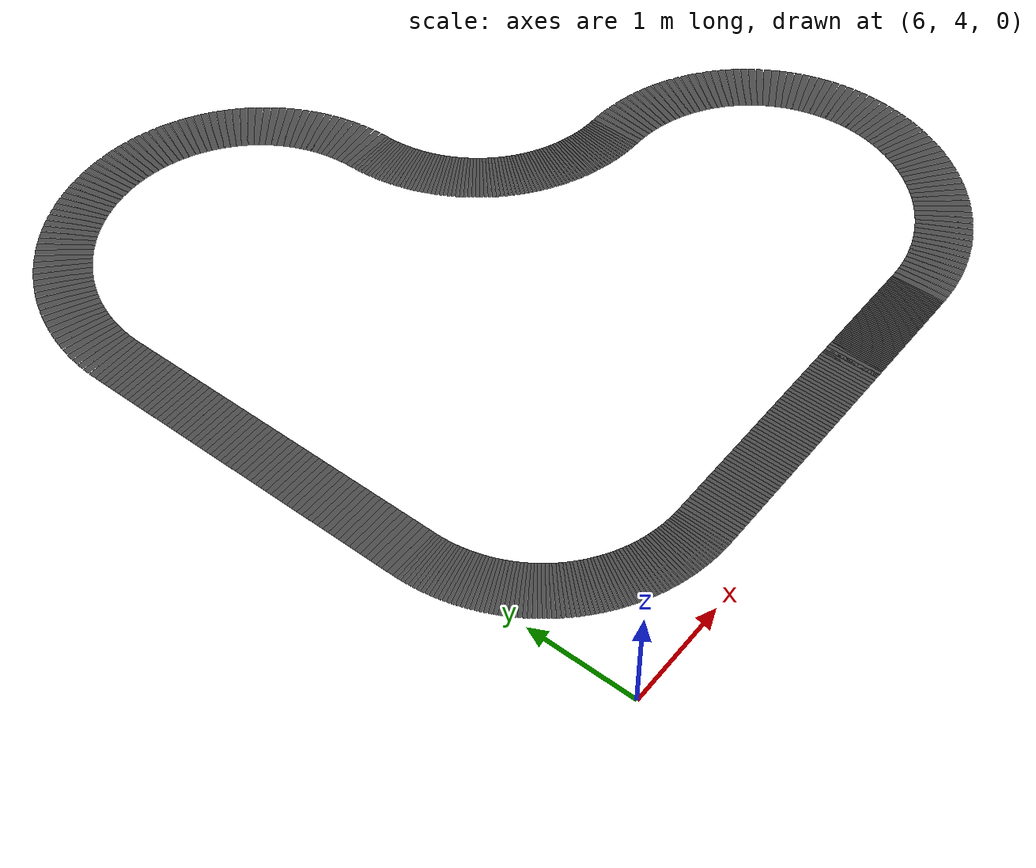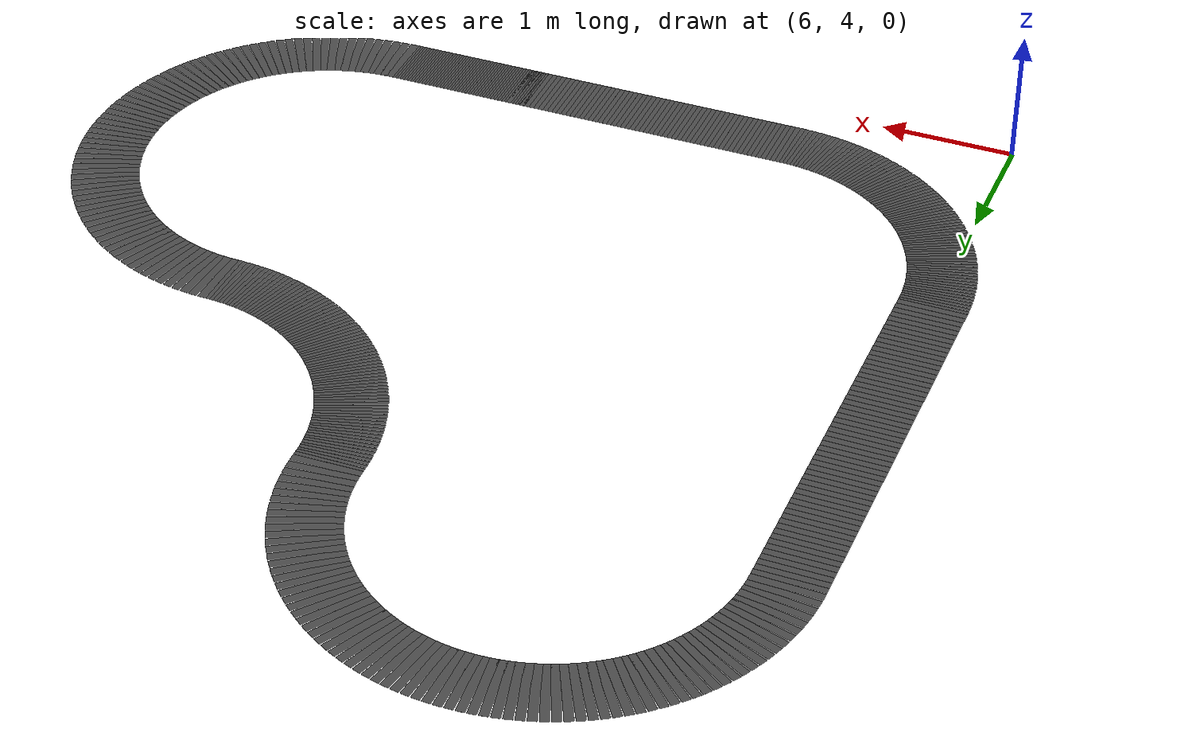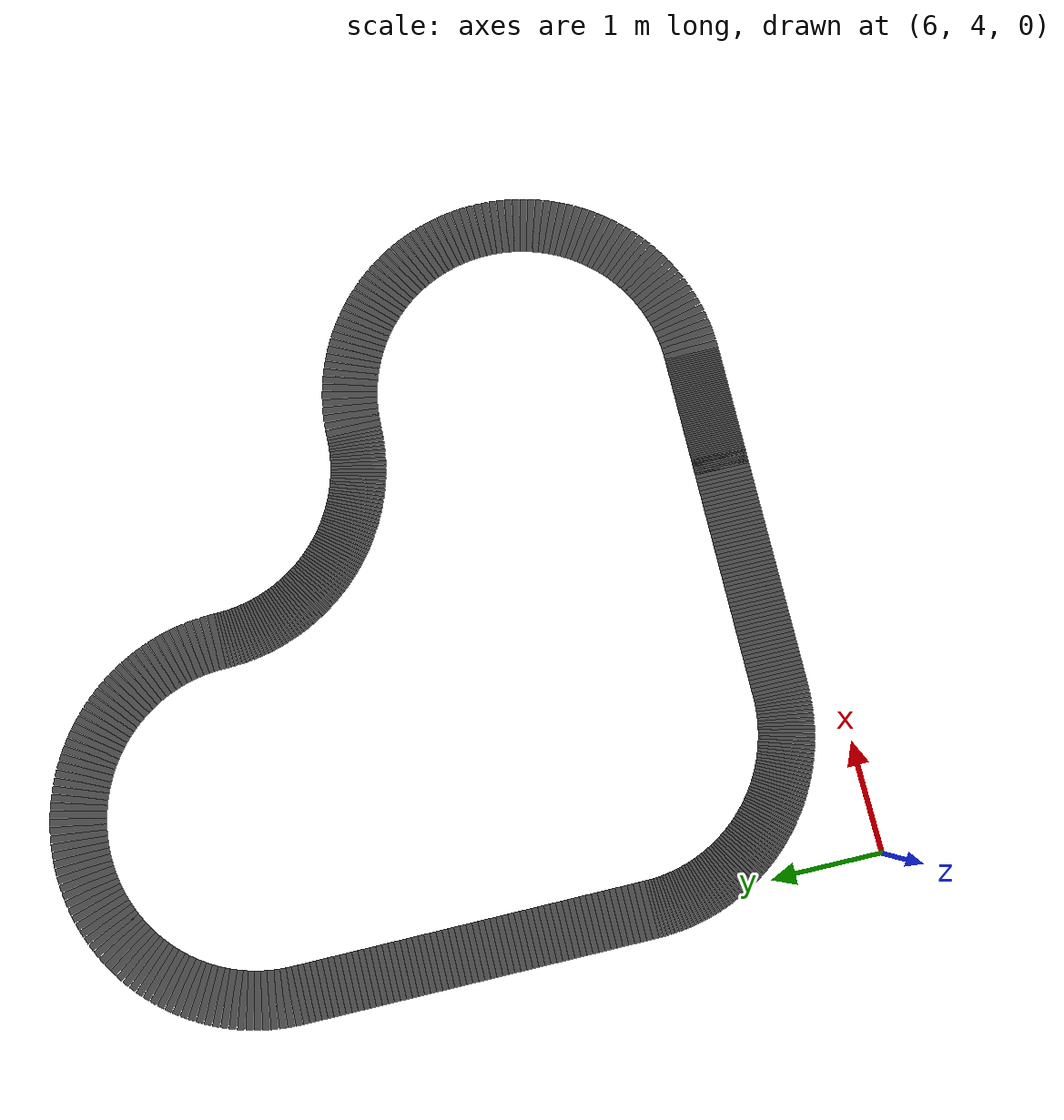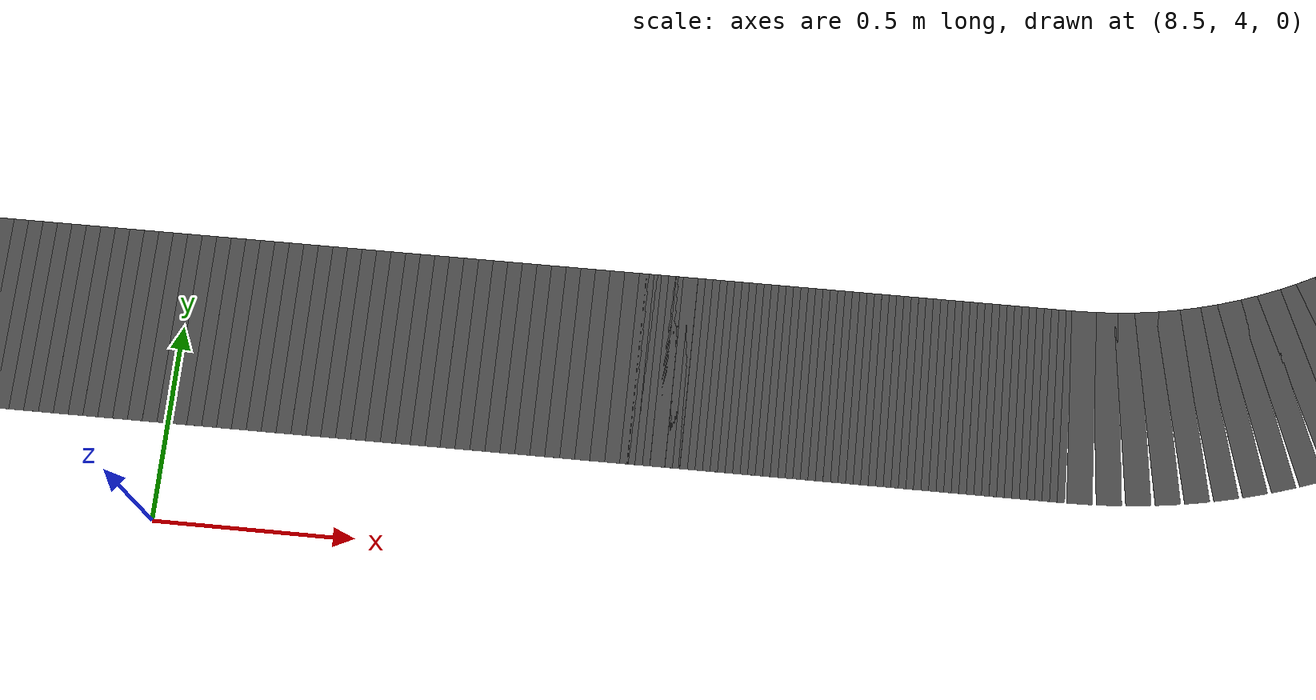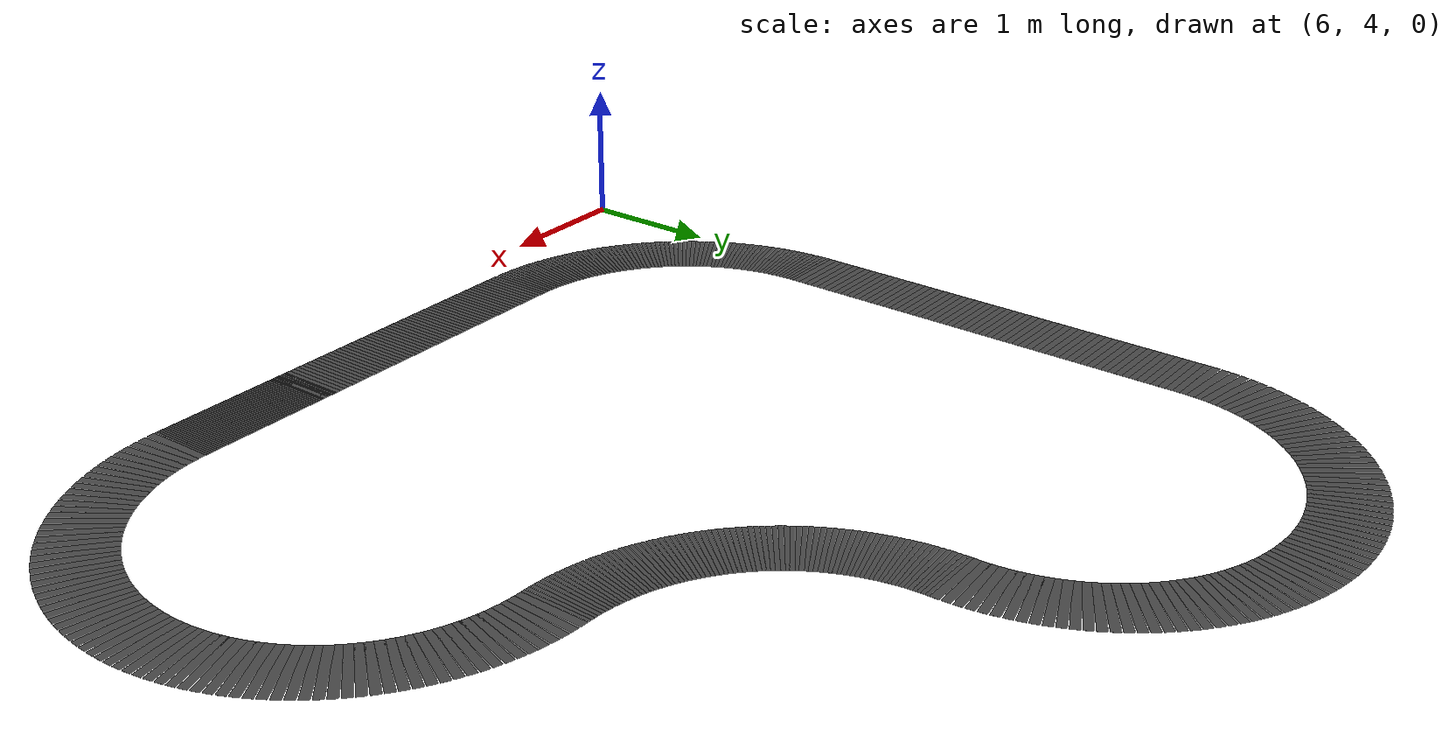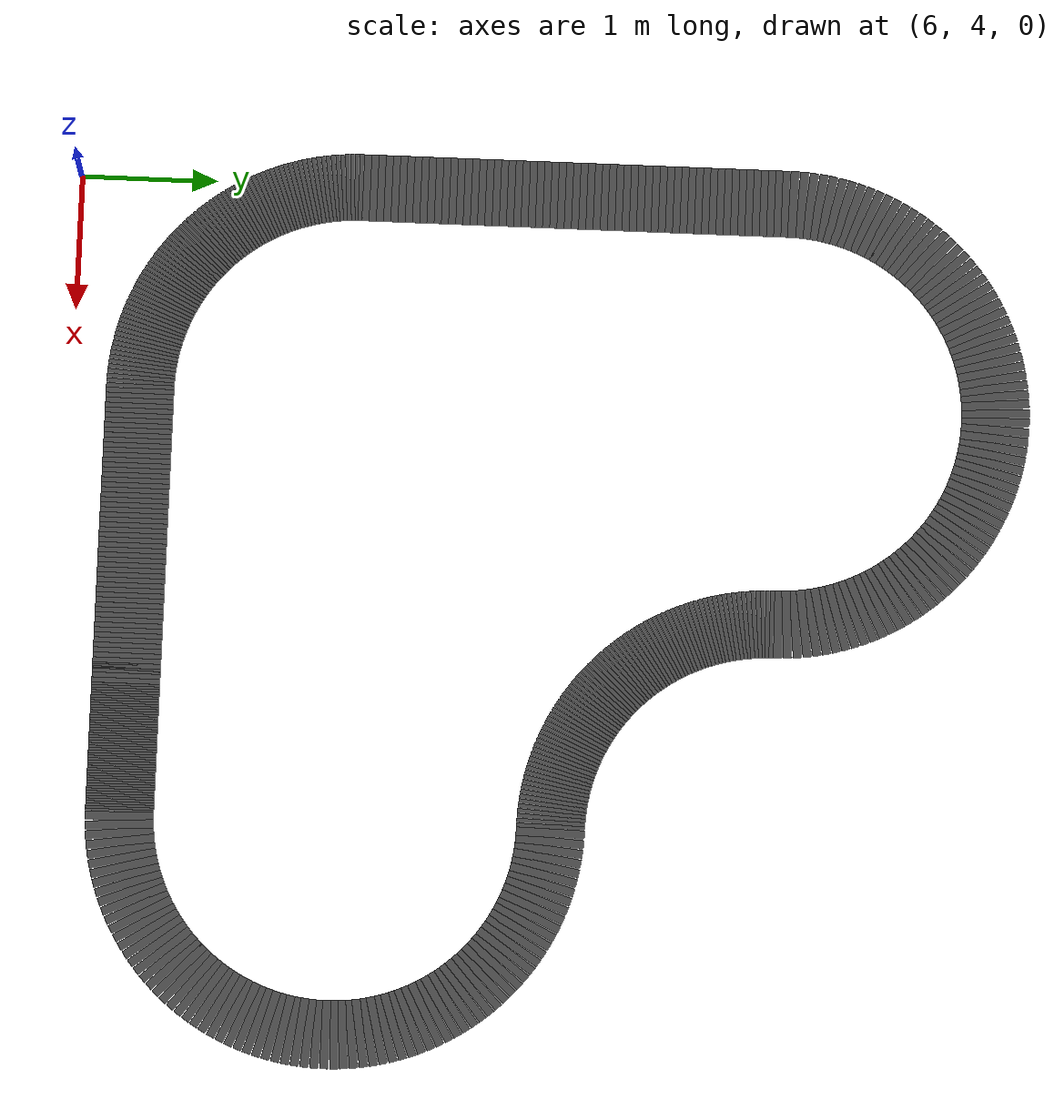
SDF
<sdf version='1.7'>
  <model name='default'>

    <model name='road_seg_0'>
      <static>1</static>
      <link name='road_link'>
        <visual name='road_visual'>
          <geometry>
            <box>
              <size>0.018637 0.5 0.0001</size>
            </box>
          </geometry>
          <material>
            <script>
              <uri>model://road_material/materials/scripts</uri>
              <uri>model://road_material/materials/textures</uri>
              <name>MyRoad/Road</name>
            </script>
          </material>
        </visual>
        <collision name='road_collision'>
          <geometry>
            <box>
              <size>0.018637 0.5 0.0001</size>
            </box>
          </geometry>
          <max_contacts>10</max_contacts>
          <surface>
            <contact>
              <ode/>
            </contact>
            <bounce/>
            <friction>
              <torsional>
                <ode/>
              </torsional>
              <ode/>
            </friction>
          </surface>
        </collision>
        <self_collide>0</self_collide>
        <enable_wind>0</enable_wind>
        <kinematic>0</kinematic>
      </link>
      <pose>9.63494 4.5 0 0 -0 0</pose>
    </model>
    <model name='road_seg_1'>
      <static>1</static>
      <link name='road_link'>
        <visual name='road_visual'>
          <geometry>
            <box>
              <size>0.018637 0.5 0.0001</size>
            </box>
          </geometry>
          <material>
            <script>
              <uri>model://road_material/materials/scripts</uri>
              <uri>model://road_material/materials/textures</uri>
              <name>MyRoad/Road</name>
            </script>
          </material>
        </visual>
        <collision name='road_collision'>
          <geometry>
            <box>
              <size>0.018637 0.5 0.0001</size>
            </box>
          </geometry>
          <max_contacts>10</max_contacts>
          <surface>
            <contact>
              <ode/>
            </contact>
            <bounce/>
            <friction>
              <torsional>
                <ode/>
              </torsional>
              <ode/>
            </friction>
          </surface>
        </collision>
        <self_collide>0</self_collide>
        <enable_wind>0</enable_wind>
        <kinematic>0</kinematic>
      </link>
      <pose>9.65358 4.5 0 0 -0 0</pose>
    </model>
    <model name='road_seg_2'>
      <static>1</static>
      <link name='road_link'>
        <visual name='road_visual'>
          <geometry>
            <box>
              <size>0.018637 0.5 0.0001</size>
            </box>
          </geometry>
          <material>
            <script>
              <uri>model://road_material/materials/scripts</uri>
              <uri>model://road_material/materials/textures</uri>
              <name>MyRoad/Road</name>
            </script>
          </material>
        </visual>
        <collision name='road_collision'>
          <geometry>
            <box>
              <size>0.018637 0.5 0.0001</size>
            </box>
          </geometry>
          <max_contacts>10</max_contacts>
          <surface>
            <contact>
              <ode/>
            </contact>
            <bounce/>
            <friction>
              <torsional>
                <ode/>
              </torsional>
              <ode/>
            </friction>
          </surface>
        </collision>
        <self_collide>0</self_collide>
        <enable_wind>0</enable_wind>
        <kinematic>0</kinematic>
      </link>
      <pose>9.67222 4.5 0 0 -0 0</pose>
    </model>
    <model name='road_seg_3'>
      <static>1</static>
      <link name='road_link'>
        <visual name='road_visual'>
          <geometry>
            <box>
              <size>0.018637 0.5 0.0001</size>
            </box>
          </geometry>
          <material>
            <script>
              <uri>model://road_material/materials/scripts</uri>
              <uri>model://road_material/materials/textures</uri>
              <name>MyRoad/Road</name>
            </script>
          </material>
        </visual>
        <collision name='road_collision'>
          <geometry>
            <box>
              <size>0.018637 0.5 0.0001</size>
            </box>
          </geometry>
          <max_contacts>10</max_contacts>
          <surface>
            <contact>
              <ode/>
            </contact>
            <bounce/>
            <friction>
              <torsional>
                <ode/>
              </torsional>
              <ode/>
            </friction>
          </surface>
        </collision>
        <self_collide>0</self_collide>
        <enable_wind>0</enable_wind>
        <kinematic>0</kinematic>
      </link>
      <pose>9.69085 4.5 0 0 -0 0</pose>
    </model>
    <model name='road_seg_4'>
      <static>1</static>
      <link name='road_link'>
        <visual name='road_visual'>
          <geometry>
            <box>
              <size>0.018637 0.5 0.0001</size>
            </box>
          </geometry>
          <material>
            <script>
              <uri>model://road_material/materials/scripts</uri>
              <uri>model://road_material/materials/textures</uri>
              <name>MyRoad/Road</name>
            </script>
          </material>
        </visual>
        <collision name='road_collision'>
          <geometry>
            <box>
              <size>0.018637 0.5 0.0001</size>
            </box>
          </geometry>
          <max_contacts>10</max_contacts>
          <surface>
            <contact>
              <ode/>
            </contact>
            <bounce/>
            <friction>
              <torsional>
                <ode/>
              </torsional>
              <ode/>
            </friction>
          </surface>
        </collision>
        <self_collide>0</self_collide>
        <enable_wind>0</enable_wind>
        <kinematic>0</kinematic>
      </link>
      <pose>9.70949 4.5 0 0 -0 0</pose>
    </model>
    <model name='road_seg_5'>
      <static>1</static>
      <link name='road_link'>
        <visual name='road_visual'>
          <geometry>
            <box>
              <size>0.018637 0.5 0.0001</size>
            </box>
          </geometry>
          <material>
            <script>
              <uri>model://road_material/materials/scripts</uri>
              <uri>model://road_material/materials/textures</uri>
              <name>MyRoad/Road</name>
            </script>
          </material>
        </visual>
        <collision name='road_collision'>
          <geometry>
            <box>
              <size>0.018637 0.5 0.0001</size>
            </box>
          </geometry>
          <max_contacts>10</max_contacts>
          <surface>
            <contact>
              <ode/>
            </contact>
            <bounce/>
            <friction>
              <torsional>
                <ode/>
              </torsional>
              <ode/>
            </friction>
          </surface>
        </collision>
        <self_collide>0</self_collide>
        <enable_wind>0</enable_wind>
        <kinematic>0</kinematic>
      </link>
      <pose>9.72813 4.5 0 0 -0 0</pose>
    </model>
    <model name='road_seg_6'>
      <static>1</static>
      <link name='road_link'>
        <visual name='road_visual'>
          <geometry>
            <box>
              <size>0.018637 0.5 0.0001</size>
            </box>
          </geometry>
          <material>
            <script>
              <uri>model://road_material/materials/scripts</uri>
              <uri>model://road_material/materials/textures</uri>
              <name>MyRoad/Road</name>
            </script>
          </material>
        </visual>
        <collision name='road_collision'>
          <geometry>
            <box>
              <size>0.018637 0.5 0.0001</size>
            </box>
          </geometry>
          <max_contacts>10</max_contacts>
          <surface>
            <contact>
              <ode/>
            </contact>
            <bounce/>
            <friction>
              <torsional>
                <ode/>
              </torsional>
              <ode/>
            </friction>
          </surface>
        </collision>
        <self_collide>0</self_collide>
        <enable_wind>0</enable_wind>
        <kinematic>0</kinematic>
      </link>
      <pose>9.74677 4.5 0 0 -0 0</pose>
    </model>
    <model name='road_seg_7'>
      <static>1</static>
      <link name='road_link'>
        <visual name='road_visual'>
          <geometry>
            <box>
              <size>0.018637 0.5 0.0001</size>
            </box>
          </geometry>
          <material>
            <script>
              <uri>model://road_material/materials/scripts</uri>
              <uri>model://road_material/materials/textures</uri>
              <name>MyRoad/Road</name>
            </script>
          </material>
        </visual>
        <collision name='road_collision'>
          <geometry>
            <box>
              <size>0.018637 0.5 0.0001</size>
            </box>
          </geometry>
          <max_contacts>10</max_contacts>
          <surface>
            <contact>
              <ode/>
            </contact>
            <bounce/>
            <friction>
              <torsional>
                <ode/>
              </torsional>
              <ode/>
            </friction>
          </surface>
        </collision>
        <self_collide>0</self_collide>
        <enable_wind>0</enable_wind>
        <kinematic>0</kinematic>
      </link>
      <pose>9.7654 4.5 0 0 -0 0</pose>
    </model>
    <model name='road_seg_8'>
      <static>1</static>
      <link name='road_link'>
        <visual name='road_visual'>
          <geometry>
            <box>
              <size>0.018637 0.5 0.0001</size>
            </box>
          </geometry>
          <material>
            <script>
              <uri>model://road_material/materials/scripts</uri>
              <uri>model://road_material/materials/textures</uri>
              <name>MyRoad/Road</name>
            </script>
          </material>
        </visual>
        <collision name='road_collision'>
          <geometry>
            <box>
              <size>0.018637 0.5 0.0001</size>
            </box>
          </geometry>
          <max_contacts>10</max_contacts>
          <surface>
            <contact>
              <ode/>
            </contact>
            <bounce/>
            <friction>
              <torsional>
                <ode/>
              </torsional>
              <ode/>
            </friction>
          </surface>
        </collision>
        <self_collide>0</self_collide>
        <enable_wind>0</enable_wind>
        <kinematic>0</kinematic>
      </link>
      <pose>9.78404 4.5 0 0 -0 0</pose>
    </model>
    <model name='road_seg_9'>
      <static>1</static>
      <link name='road_link'>
        <visual name='road_visual'>
          <geometry>
            <box>
              <size>0.018637 0.5 0.0001</size>
            </box>
          </geometry>
          <material>
            <script>
              <uri>model://road_material/materials/scripts</uri>
              <uri>model://road_material/materials/textures</uri>
              <name>MyRoad/Road</name>
            </script>
          </material>
        </visual>
        <collision name='road_collision'>
          <geometry>
            <box>
              <size>0.018637 0.5 0.0001</size>
            </box>
          </geometry>
          <max_contacts>10</max_contacts>
          <surface>
            <contact>
              <ode/>
            </contact>
            <bounce/>
            <friction>
              <torsional>
                <ode/>
              </torsional>
              <ode/>
            </friction>
          </surface>
        </collision>
        <self_collide>0</self_collide>
        <enable_wind>0</enable_wind>
        <kinematic>0</kinematic>
      </link>
      <pose>9.80268 4.5 0 0 -0 0</pose>
    </model>
    <model name='road_seg_10'>
      <static>1</static>
      <link name='road_link'>
        <visual name='road_visual'>
          <geometry>
            <box>
              <size>0.018637 0.5 0.0001</size>
            </box>
          </geometry>
          <material>
            <script>
              <uri>model://road_material/materials/scripts</uri>
              <uri>model://road_material/materials/textures</uri>
              <name>MyRoad/Road</name>
            </script>
          </material>
        </visual>
        <collision name='road_collision'>
          <geometry>
            <box>
              <size>0.018637 0.5 0.0001</size>
            </box>
          </geometry>
          <max_contacts>10</max_contacts>
          <surface>
            <contact>
              <ode/>
            </contact>
            <bounce/>
            <friction>
              <torsional>
                <ode/>
              </torsional>
              <ode/>
            </friction>
          </surface>
        </collision>
        <self_collide>0</self_collide>
        <enable_wind>0</enable_wind>
        <kinematic>0</kinematic>
      </link>
      <pose>9.82132 4.5 0 0 -0 0</pose>
    </model>
    <model name='road_seg_11'>
      <static>1</static>
      <link name='road_link'>
        <visual name='road_visual'>
          <geometry>
            <box>
              <size>0.018637 0.5 0.0001</size>
            </box>
          </geometry>
          <material>
            <script>
              <uri>model://road_material/materials/scripts</uri>
              <uri>model://road_material/materials/textures</uri>
              <name>MyRoad/Road</name>
            </script>
          </material>
        </visual>
        <collision name='road_collision'>
          <geometry>
            <box>
              <size>0.018637 0.5 0.0001</size>
            </box>
          </geometry>
          <max_contacts>10</max_contacts>
          <surface>
            <contact>
              <ode/>
            </contact>
            <bounce/>
            <friction>
              <torsional>
                <ode/>
              </torsional>
              <ode/>
            </friction>
          </surface>
        </collision>
        <self_collide>0</self_collide>
        <enable_wind>0</enable_wind>
        <kinematic>0</kinematic>
      </link>
      <pose>9.83995 4.5 0 0 -0 0</pose>
    </model>
    <model name='road_seg_12'>
      <static>1</static>
      <link name='road_link'>
        <visual name='road_visual'>
          <geometry>
            <box>
              <size>0.018637 0.5 0.0001</size>
            </box>
          </geometry>
          <material>
            <script>
              <uri>model://road_material/materials/scripts</uri>
              <uri>model://road_material/materials/textures</uri>
              <name>MyRoad/Road</name>
            </script>
          </material>
        </visual>
        <collision name='road_collision'>
          <geometry>
            <box>
              <size>0.018637 0.5 0.0001</size>
            </box>
          </geometry>
          <max_contacts>10</max_contacts>
          <surface>
            <contact>
              <ode/>
            </contact>
            <bounce/>
            <friction>
              <torsional>
                <ode/>
              </torsional>
              <ode/>
            </friction>
          </surface>
        </collision>
        <self_collide>0</self_collide>
        <enable_wind>0</enable_wind>
        <kinematic>0</kinematic>
      </link>
      <pose>9.85859 4.5 0 0 -0 0</pose>
    </model>
    <model name='road_seg_13'>
      <static>1</static>
      <link name='road_link'>
        <visual name='road_visual'>
          <geometry>
            <box>
              <size>0.018637 0.5 0.0001</size>
            </box>
          </geometry>
          <material>
            <script>
              <uri>model://road_material/materials/scripts</uri>
              <uri>model://road_material/materials/textures</uri>
              <name>MyRoad/Road</name>
            </script>
          </material>
        </visual>
        <collision name='road_collision'>
          <geometry>
            <box>
              <size>0.018637 0.5 0.0001</size>
            </box>
          </geometry>
          <max_contacts>10</max_contacts>
          <surface>
            <contact>
              <ode/>
            </contact>
            <bounce/>
            <friction>
              <torsional>
                <ode/>
              </torsional>
              <ode/>
            </friction>
          </surface>
        </collision>
        <self_collide>0</self_collide>
        <enable_wind>0</enable_wind>
        <kinematic>0</kinematic>
      </link>
      <pose>9.87723 4.5 0 0 -0 0</pose>
    </model>
    <model name='road_seg_14'>
      <static>1</static>
      <link name='road_link'>
        <visual name='road_visual'>
          <geometry>
            <box>
              <size>0.018637 0.5 0.0001</size>
            </box>
          </geometry>
          <material>
            <script>
              <uri>model://road_material/materials/scripts</uri>
              <uri>model://road_material/materials/textures</uri>
              <name>MyRoad/Road</name>
            </script>
          </material>
        </visual>
        <collision name='road_collision'>
          <geometry>
            <box>
              <size>0.018637 0.5 0.0001</size>
            </box>
          </geometry>
          <max_contacts>10</max_contacts>
          <surface>
            <contact>
              <ode/>
            </contact>
            <bounce/>
            <friction>
              <torsional>
                <ode/>
              </torsional>
              <ode/>
            </friction>
          </surface>
        </collision>
        <self_collide>0</self_collide>
        <enable_wind>0</enable_wind>
        <kinematic>0</kinematic>
      </link>
      <pose>9.89587 4.5 0 0 -0 0</pose>
    </model>
    <model name='road_seg_15'>
      <static>1</static>
      <link name='road_link'>
        <visual name='road_visual'>
          <geometry>
            <box>
              <size>0.018637 0.5 0.0001</size>
            </box>
          </geometry>
          <material>
            <script>
              <uri>model://road_material/materials/scripts</uri>
              <uri>model://road_material/materials/textures</uri>
              <name>MyRoad/Road</name>
            </script>
          </material>
        </visual>
        <collision name='road_collision'>
          <geometry>
            <box>
              <size>0.018637 0.5 0.0001</size>
            </box>
          </geometry>
          <max_contacts>10</max_contacts>
          <surface>
            <contact>
              <ode/>
            </contact>
            <bounce/>
            <friction>
              <torsional>
                <ode/>
              </torsional>
              <ode/>
            </friction>
          </surface>
        </collision>
        <self_collide>0</self_collide>
        <enable_wind>0</enable_wind>
        <kinematic>0</kinematic>
      </link>
      <pose>9.9145 4.5 0 0 -0 0</pose>
    </model>
    <model name='road_seg_16'>
      <static>1</static>
      <link name='road_link'>
        <visual name='road_visual'>
          <geometry>
            <box>
              <size>0.018637 0.5 0.0001</size>
            </box>
          </geometry>
          <material>
            <script>
              <uri>model://road_material/materials/scripts</uri>
              <uri>model://road_material/materials/textures</uri>
              <name>MyRoad/Road</name>
            </script>
          </material>
        </visual>
        <collision name='road_collision'>
          <geometry>
            <box>
              <size>0.018637 0.5 0.0001</size>
            </box>
          </geometry>
          <max_contacts>10</max_contacts>
          <surface>
            <contact>
              <ode/>
            </contact>
            <bounce/>
            <friction>
              <torsional>
                <ode/>
              </torsional>
              <ode/>
            </friction>
          </surface>
        </collision>
        <self_collide>0</self_collide>
        <enable_wind>0</enable_wind>
        <kinematic>0</kinematic>
      </link>
      <pose>9.93314 4.5 0 0 -0 0</pose>
    </model>
    <model name='road_seg_17'>
      <static>1</static>
      <link name='road_link'>
        <visual name='road_visual'>
          <geometry>
            <box>
              <size>0.018637 0.5 0.0001</size>
            </box>
          </geometry>
          <material>
            <script>
              <uri>model://road_material/materials/scripts</uri>
              <uri>model://road_material/materials/textures</uri>
              <name>MyRoad/Road</name>
            </script>
          </material>
        </visual>
        <collision name='road_collision'>
          <geometry>
            <box>
              <size>0.018637 0.5 0.0001</size>
            </box>
          </geometry>
          <max_contacts>10</max_contacts>
          <surface>
            <contact>
              <ode/>
            </contact>
            <bounce/>
            <friction>
              <torsional>
                <ode/>
              </torsional>
              <ode/>
            </friction>
          </surface>
        </collision>
        <self_collide>0</self_collide>
        <enable_wind>0</enable_wind>
        <kinematic>0</kinematic>
      </link>
      <pose>9.95178 4.5 0 0 -0 0</pose>
    </model>
    <model name='road_seg_18'>
      <static>1</static>
      <link name='road_link'>
        <visual name='road_visual'>
          <geometry>
            <box>
              <size>0.018637 0.5 0.0001</size>
            </box>
          </geometry>
          <material>
            <script>
              <uri>model://road_material/materials/scripts</uri>
              <uri>model://road_material/materials/textures</uri>
              <name>MyRoad/Road</name>
            </script>
          </material>
        </visual>
        <collision name='road_collision'>
          <geometry>
            <box>
              <size>0.018637 0.5 0.0001</size>
            </box>
          </geometry>
          <max_contacts>10</max_contacts>
          <surface>
            <contact>
              <ode/>
            </contact>
            <bounce/>
            <friction>
              <torsional>
                <ode/>
              </torsional>
              <ode/>
            </friction>
          </surface>
        </collision>
        <self_collide>0</self_collide>
        <enable_wind>0</enable_wind>
        <kinematic>0</kinematic>
      </link>
      <pose>9.97042 4.5 0 0 -0 0</pose>
    </model>
    <model name='road_seg_19'>
      <static>1</static>
      <link name='road_link'>
        <visual name='road_visual'>
          <geometry>
            <box>
              <size>0.018637 0.5 0.0001</size>
            </box>
          </geometry>
          <material>
            <script>
              <uri>model://road_material/materials/scripts</uri>
              <uri>model://road_material/materials/textures</uri>
              <name>MyRoad/Road</name>
            </script>
          </material>
        </visual>
        <collision name='road_collision'>
          <geometry>
            <box>
              <size>0.018637 0.5 0.0001</size>
            </box>
          </geometry>
          <max_contacts>10</max_contacts>
          <surface>
            <contact>
              <ode/>
            </contact>
            <bounce/>
            <friction>
              <torsional>
                <ode/>
              </torsional>
              <ode/>
            </friction>
          </surface>
        </collision>
        <self_collide>0</self_collide>
        <enable_wind>0</enable_wind>
        <kinematic>0</kinematic>
      </link>
      <pose>9.98905 4.5 0 0 -0 0</pose>
    </model>
    <model name='road_seg_20'>
      <static>1</static>
      <link name='road_link'>
        <visual name='road_visual'>
          <geometry>
            <box>
              <size>0.018637 0.5 0.0001</size>
            </box>
          </geometry>
          <material>
            <script>
              <uri>model://road_material/materials/scripts</uri>
              <uri>model://road_material/materials/textures</uri>
              <name>MyRoad/Road</name>
            </script>
          </material>
        </visual>
        <collision name='road_collision'>
          <geometry>
            <box>
              <size>0.018637 0.5 0.0001</size>
            </box>
          </geometry>
          <max_contacts>10</max_contacts>
          <surface>
            <contact>
              <ode/>
            </contact>
            <bounce/>
            <friction>
              <torsional>
                <ode/>
              </torsional>
              <ode/>
            </friction>
          </surface>
        </collision>
        <self_collide>0</self_collide>
        <enable_wind>0</enable_wind>
        <kinematic>0</kinematic>
      </link>
      <pose>10.0077 4.5 0 0 -0 0</pose>
    </model>
    <model name='road_seg_21'>
      <static>1</static>
      <link name='road_link'>
        <visual name='road_visual'>
          <geometry>
            <box>
              <size>0.018637 0.5 0.0001</size>
            </box>
          </geometry>
          <material>
            <script>
              <uri>model://road_material/materials/scripts</uri>
              <uri>model://road_material/materials/textures</uri>
              <name>MyRoad/Road</name>
            </script>
          </material>
        </visual>
        <collision name='road_collision'>
          <geometry>
            <box>
              <size>0.018637 0.5 0.0001</size>
            </box>
          </geometry>
          <max_contacts>10</max_contacts>
          <surface>
            <contact>
              <ode/>
            </contact>
            <bounce/>
            <friction>
              <torsional>
                <ode/>
              </torsional>
              <ode/>
            </friction>
          </surface>
        </collision>
        <self_collide>0</self_collide>
        <enable_wind>0</enable_wind>
        <kinematic>0</kinematic>
      </link>
      <pose>10.0263 4.5 0 0 -0 0</pose>
    </model>
    <model name='road_seg_22'>
      <static>1</static>
      <link name='road_link'>
        <visual name='road_visual'>
          <geometry>
            <box>
              <size>0.018637 0.5 0.0001</size>
            </box>
          </geometry>
          <material>
            <script>
              <uri>model://road_material/materials/scripts</uri>
              <uri>model://road_material/materials/textures</uri>
              <name>MyRoad/Road</name>
            </script>
          </material>
        </visual>
        <collision name='road_collision'>
          <geometry>
            <box>
              <size>0.018637 0.5 0.0001</size>
            </box>
          </geometry>
          <max_contacts>10</max_contacts>
          <surface>
            <contact>
              <ode/>
            </contact>
            <bounce/>
            <friction>
              <torsional>
                <ode/>
              </torsional>
              <ode/>
            </friction>
          </surface>
        </collision>
        <self_collide>0</self_collide>
        <enable_wind>0</enable_wind>
        <kinematic>0</kinematic>
      </link>
      <pose>10.045 4.5 0 0 -0 0</pose>
    </model>
    <model name='road_seg_23'>
      <static>1</static>
      <link name='road_link'>
        <visual name='road_visual'>
          <geometry>
            <box>
              <size>0.018637 0.5 0.0001</size>
            </box>
          </geometry>
          <material>
            <script>
              <uri>model://road_material/materials/scripts</uri>
              <uri>model://road_material/materials/textures</uri>
              <name>MyRoad/Road</name>
            </script>
          </material>
        </visual>
        <collision name='road_collision'>
          <geometry>
            <box>
              <size>0.018637 0.5 0.0001</size>
            </box>
          </geometry>
          <max_contacts>10</max_contacts>
          <surface>
            <contact>
              <ode/>
            </contact>
            <bounce/>
            <friction>
              <torsional>
                <ode/>
              </torsional>
              <ode/>
            </friction>
          </surface>
        </collision>
        <self_collide>0</self_collide>
        <enable_wind>0</enable_wind>
        <kinematic>0</kinematic>
      </link>
      <pose>10.0636 4.5 0 0 -0 0</pose>
    </model>
    <model name='road_seg_24'>
      <static>1</static>
      <link name='road_link'>
        <visual name='road_visual'>
          <geometry>
            <box>
              <size>0.018637 0.5 0.0001</size>
            </box>
          </geometry>
          <material>
            <script>
              <uri>model://road_material/materials/scripts</uri>
              <uri>model://road_material/materials/textures</uri>
              <name>MyRoad/Road</name>
            </script>
          </material>
        </visual>
        <collision name='road_collision'>
          <geometry>
            <box>
              <size>0.018637 0.5 0.0001</size>
            </box>
          </geometry>
          <max_contacts>10</max_contacts>
          <surface>
            <contact>
              <ode/>
            </contact>
            <bounce/>
            <friction>
              <torsional>
                <ode/>
              </torsional>
              <ode/>
            </friction>
          </surface>
        </collision>
        <self_collide>0</self_collide>
        <enable_wind>0</enable_wind>
        <kinematic>0</kinematic>
      </link>
      <pose>10.0822 4.5 0 0 -0 0</pose>
    </model>
    <model name='road_seg_25'>
      <static>1</static>
      <link name='road_link'>
        <visual name='road_visual'>
          <geometry>
            <box>
              <size>0.018637 0.5 0.0001</size>
            </box>
          </geometry>
          <material>
            <script>
              <uri>model://road_material/materials/scripts</uri>
              <uri>model://road_material/materials/textures</uri>
              <name>MyRoad/Road</name>
            </script>
          </material>
        </visual>
        <collision name='road_collision'>
          <geometry>
            <box>
              <size>0.018637 0.5 0.0001</size>
            </box>
          </geometry>
          <max_contacts>10</max_contacts>
          <surface>
            <contact>
              <ode/>
            </contact>
            <bounce/>
            <friction>
              <torsional>
                <ode/>
              </torsional>
              <ode/>
            </friction>
          </surface>
        </collision>
        <self_collide>0</self_collide>
        <enable_wind>0</enable_wind>
        <kinematic>0</kinematic>
      </link>
      <pose>10.1009 4.5 0 0 -0 0</pose>
    </model>
    <model name='road_seg_26'>
      <static>1</static>
      <link name='road_link'>
        <visual name='road_visual'>
          <geometry>
            <box>
              <size>0.018637 0.5 0.0001</size>
            </box>
          </geometry>
          <material>
            <script>
              <uri>model://road_material/materials/scripts</uri>
              <uri>model://road_material/materials/textures</uri>
              <name>MyRoad/Road</name>
            </script>
          </material>
        </visual>
        <collision name='road_collision'>
          <geometry>
            <box>
              <size>0.018637 0.5 0.0001</size>
            </box>
          </geometry>
          <max_contacts>10</max_contacts>
          <surface>
            <contact>
              <ode/>
            </contact>
            <bounce/>
            <friction>
              <torsional>
                <ode/>
              </torsional>
              <ode/>
            </friction>
          </surface>
        </collision>
        <self_collide>0</self_collide>
        <enable_wind>0</enable_wind>
        <kinematic>0</kinematic>
      </link>
      <pose>10.1195 4.5 0 0 -0 0</pose>
    </model>
    <model name='road_seg_27'>
      <static>1</static>
      <link name='road_link'>
        <visual name='road_visual'>
          <geometry>
            <box>
              <size>0.018637 0.5 0.0001</size>
            </box>
          </geometry>
          <material>
            <script>
              <uri>model://road_material/materials/scripts</uri>
              <uri>model://road_material/materials/textures</uri>
              <name>MyRoad/Road</name>
            </script>
          </material>
        </visual>
        <collision name='road_collision'>
          <geometry>
            <box>
              <size>0.018637 0.5 0.0001</size>
            </box>
          </geometry>
          <max_contacts>10</max_contacts>
          <surface>
            <contact>
              <ode/>
            </contact>
            <bounce/>
            <friction>
              <torsional>
                <ode/>
              </torsional>
              <ode/>
            </friction>
          </surface>
        </collision>
        <self_collide>0</self_collide>
        <enable_wind>0</enable_wind>
        <kinematic>0</kinematic>
      </link>
      <pose>10.1382 4.5 0 0 -0 0</pose>
    </model>
    <model name='road_seg_28'>
      <static>1</static>
      <link name='road_link'>
        <visual name='road_visual'>
          <geometry>
            <box>
              <size>0.018637 0.5 0.0001</size>
            </box>
          </geometry>
          <material>
            <script>
              <uri>model://road_material/materials/scripts</uri>
              <uri>model://road_material/materials/textures</uri>
              <name>MyRoad/Road</name>
            </script>
          </material>
        </visual>
        <collision name='road_collision'>
          <geometry>
            <box>
              <size>0.018637 0.5 0.0001</size>
            </box>
          </geometry>
          <max_contacts>10</max_contacts>
          <surface>
            <contact>
              <ode/>
            </contact>
            <bounce/>
            <friction>
              <torsional>
                <ode/>
              </torsional>
              <ode/>
            </friction>
          </surface>
        </collision>
        <self_collide>0</self_collide>
        <enable_wind>0</enable_wind>
        <kinematic>0</kinematic>
      </link>
      <pose>10.1568 4.5 0 0 -0 0</pose>
    </model>
    <model name='road_seg_29'>
      <static>1</static>
      <link name='road_link'>
        <visual name='road_visual'>
          <geometry>
            <box>
              <size>0.018637 0.5 0.0001</size>
            </box>
          </geometry>
          <material>
            <script>
              <uri>model://road_material/materials/scripts</uri>
              <uri>model://road_material/materials/textures</uri>
              <name>MyRoad/Road</name>
            </script>
          </material>
        </visual>
        <collision name='road_collision'>
          <geometry>
            <box>
              <size>0.018637 0.5 0.0001</size>
            </box>
          </geometry>
          <max_contacts>10</max_contacts>
          <surface>
            <contact>
              <ode/>
            </contact>
            <bounce/>
            <friction>
              <torsional>
                <ode/>
              </torsional>
              <ode/>
            </friction>
          </surface>
        </collision>
        <self_collide>0</self_collide>
        <enable_wind>0</enable_wind>
        <kinematic>0</kinematic>
      </link>
      <pose>10.1754 4.5 0 0 -0 0</pose>
    </model>
    <model name='road_seg_30'>
      <static>1</static>
      <link name='road_link'>
        <visual name='road_visual'>
          <geometry>
            <box>
              <size>0.018637 0.5 0.0001</size>
            </box>
          </geometry>
          <material>
            <script>
              <uri>model://road_material/materials/scripts</uri>
              <uri>model://road_material/materials/textures</uri>
              <name>MyRoad/Road</name>
            </script>
          </material>
        </visual>
        <collision name='road_collision'>
          <geometry>
            <box>
              <size>0.018637 0.5 0.0001</size>
            </box>
          </geometry>
          <max_contacts>10</max_contacts>
          <surface>
            <contact>
              <ode/>
            </contact>
            <bounce/>
            <friction>
              <torsional>
                <ode/>
              </torsional>
              <ode/>
            </friction>
          </surface>
        </collision>
        <self_collide>0</self_collide>
        <enable_wind>0</enable_wind>
        <kinematic>0</kinematic>
      </link>
      <pose>10.1941 4.5 0 0 -0 0</pose>
    </model>
    <model name='road_seg_31'>
      <static>1</static>
      <link name='road_link'>
        <visual name='road_visual'>
          <geometry>
            <box>
              <size>0.018637 0.5 0.0001</size>
            </box>
          </geometry>
          <material>
            <script>
              <uri>model://road_material/materials/scripts</uri>
              <uri>model://road_material/materials/textures</uri>
              <name>MyRoad/Road</name>
            </script>
          </material>
        </visual>
        <collision name='road_collision'>
          <geometry>
            <box>
              <size>0.018637 0.5 0.0001</size>
            </box>
          </geometry>
          <max_contacts>10</max_contacts>
          <surface>
            <contact>
              <ode/>
            </contact>
            <bounce/>
            <friction>
              <torsional>
                <ode/>
              </torsional>
              <ode/>
            </friction>
          </surface>
        </collision>
        <self_collide>0</self_collide>
        <enable_wind>0</enable_wind>
        <kinematic>0</kinematic>
      </link>
      <pose>10.2127 4.5 0 0 -0 0</pose>
    </model>
    <model name='road_seg_32'>
      <static>1</static>
      <link name='road_link'>
        <visual name='road_visual'>
          <geometry>
            <box>
              <size>0.018637 0.5 0.0001</size>
            </box>
          </geometry>
          <material>
            <script>
              <uri>model://road_material/materials/scripts</uri>
              <uri>model://road_material/materials/textures</uri>
              <name>MyRoad/Road</name>
            </script>
          </material>
        </visual>
        <collision name='road_collision'>
          <geometry>
            <box>
              <size>0.018637 0.5 0.0001</size>
            </box>
          </geometry>
          <max_contacts>10</max_contacts>
          <surface>
            <contact>
              <ode/>
            </contact>
            <bounce/>
            <friction>
              <torsional>
                <ode/>
              </torsional>
              <ode/>
            </friction>
          </surface>
        </collision>
        <self_collide>0</self_collide>
        <enable_wind>0</enable_wind>
        <kinematic>0</kinematic>
      </link>
      <pose>10.2313 4.5 0 0 -0 0</pose>
    </model>
    <model name='road_seg_33'>
      <static>1</static>
      <link name='road_link'>
        <visual name='road_visual'>
          <geometry>
            <box>
              <size>0.018637 0.5 0.0001</size>
            </box>
          </geometry>
          <material>
            <script>
              <uri>model://road_material/materials/scripts</uri>
              <uri>model://road_material/materials/textures</uri>
              <name>MyRoad/Road</name>
            </script>
          </material>
        </visual>
        <collision name='road_collision'>
          <geometry>
            <box>
              <size>0.018637 0.5 0.0001</size>
            </box>
          </geometry>
          <max_contacts>10</max_contacts>
          <surface>
            <contact>
              <ode/>
            </contact>
            <bounce/>
            <friction>
              <torsional>
                <ode/>
              </torsional>
              <ode/>
            </friction>
          </surface>
        </collision>
        <self_collide>0</self_collide>
        <enable_wind>0</enable_wind>
        <kinematic>0</kinematic>
      </link>
      <pose>10.25 4.5 0 0 -0 0</pose>
    </model>
    <model name='road_seg_34'>
      <static>1</static>
      <link name='road_link'>
        <visual name='road_visual'>
          <geometry>
            <box>
              <size>0.018637 0.5 0.0001</size>
            </box>
          </geometry>
          <material>
            <script>
              <uri>model://road_material/materials/scripts</uri>
              <uri>model://road_material/materials/textures</uri>
              <name>MyRoad/Road</name>
            </script>
          </material>
        </visual>
        <collision name='road_collision'>
          <geometry>
            <box>
              <size>0.018637 0.5 0.0001</size>
            </box>
          </geometry>
          <max_contacts>10</max_contacts>
          <surface>
            <contact>
              <ode/>
            </contact>
            <bounce/>
            <friction>
              <torsional>
                <ode/>
              </torsional>
              <ode/>
            </friction>
          </surface>
        </collision>
        <self_collide>0</self_collide>
        <enable_wind>0</enable_wind>
        <kinematic>0</kinematic>
      </link>
      <pose>10.2686 4.5 0 0 -0 0</pose>
    </model>
    <model name='road_seg_35'>
      <static>1</static>
      <link name='road_link'>
        <visual name='road_visual'>
          <geometry>
            <box>
              <size>0.018637 0.5 0.0001</size>
            </box>
          </geometry>
          <material>
            <script>
              <uri>model://road_material/materials/scripts</uri>
              <uri>model://road_material/materials/textures</uri>
              <name>MyRoad/Road</name>
            </script>
          </material>
        </visual>
        <collision name='road_collision'>
          <geometry>
            <box>
              <size>0.018637 0.5 0.0001</size>
            </box>
          </geometry>
          <max_contacts>10</max_contacts>
          <surface>
            <contact>
              <ode/>
            </contact>
            <bounce/>
            <friction>
              <torsional>
                <ode/>
              </torsional>
              <ode/>
            </friction>
          </surface>
        </collision>
        <self_collide>0</self_collide>
        <enable_wind>0</enable_wind>
        <kinematic>0</kinematic>
      </link>
      <pose>10.2873 4.5 0 0 -0 0</pose>
    </model>
    <model name='road_seg_36'>
      <static>1</static>
      <link name='road_link'>
        <visual name='road_visual'>
          <geometry>
            <box>
              <size>0.018637 0.5 0.0001</size>
            </box>
          </geometry>
          <material>
            <script>
              <uri>model://road_material/materials/scripts</uri>
              <uri>model://road_material/materials/textures</uri>
              <name>MyRoad/Road</name>
            </script>
          </material>
        </visual>
        <collision name='road_collision'>
          <geometry>
            <box>
              <size>0.018637 0.5 0.0001</size>
            </box>
          </geometry>
          <max_contacts>10</max_contacts>
          <surface>
            <contact>
              <ode/>
            </contact>
            <bounce/>
            <friction>
              <torsional>
                <ode/>
              </torsional>
              <ode/>
            </friction>
          </surface>
        </collision>
        <self_collide>0</self_collide>
        <enable_wind>0</enable_wind>
        <kinematic>0</kinematic>
      </link>
      <pose>10.3059 4.5 0 0 -0 0</pose>
    </model>
    <model name='road_seg_37'>
      <static>1</static>
      <link name='road_link'>
        <visual name='road_visual'>
          <geometry>
            <box>
              <size>0.018637 0.5 0.0001</size>
            </box>
          </geometry>
          <material>
            <script>
              <uri>model://road_material/materials/scripts</uri>
              <uri>model://road_material/materials/textures</uri>
              <name>MyRoad/Road</name>
            </script>
          </material>
        </visual>
        <collision name='road_collision'>
          <geometry>
            <box>
              <size>0.018637 0.5 0.0001</size>
            </box>
          </geometry>
          <max_contacts>10</max_contacts>
          <surface>
            <contact>
              <ode/>
            </contact>
            <bounce/>
            <friction>
              <torsional>
                <ode/>
              </torsional>
              <ode/>
            </friction>
          </surface>
        </collision>
        <self_collide>0</self_collide>
        <enable_wind>0</enable_wind>
        <kinematic>0</kinematic>
      </link>
      <pose>10.3245 4.5 0 0 -0 0</pose>
    </model>
    <model name='road_seg_38'>
      <static>1</static>
      <link name='road_link'>
        <visual name='road_visual'>
          <geometry>
            <box>
              <size>0.018637 0.5 0.0001</size>
            </box>
          </geometry>
          <material>
            <script>
              <uri>model://road_material/materials/scripts</uri>
              <uri>model://road_material/materials/textures</uri>
              <name>MyRoad/Road</name>
            </script>
          </material>
        </visual>
        <collision name='road_collision'>
          <geometry>
            <box>
              <size>0.018637 0.5 0.0001</size>
            </box>
          </geometry>
          <max_contacts>10</max_contacts>
          <surface>
            <contact>
              <ode/>
            </contact>
            <bounce/>
            <friction>
              <torsional>
                <ode/>
              </torsional>
              <ode/>
            </friction>
          </surface>
        </collision>
        <self_collide>0</self_collide>
        <enable_wind>0</enable_wind>
        <kinematic>0</kinematic>
      </link>
      <pose>10.3432 4.5 0 0 -0 0</pose>
    </model>
    <model name='road_seg_39'>
      <static>1</static>
      <link name='road_link'>
        <visual name='road_visual'>
          <geometry>
            <box>
              <size>0.018637 0.5 0.0001</size>
            </box>
          </geometry>
          <material>
            <script>
              <uri>model://road_material/materials/scripts</uri>
              <uri>model://road_material/materials/textures</uri>
              <name>MyRoad/Road</name>
            </script>
          </material>
        </visual>
        <collision name='road_collision'>
          <geometry>
            <box>
              <size>0.018637 0.5 0.0001</size>
            </box>
          </geometry>
          <max_contacts>10</max_contacts>
          <surface>
            <contact>
              <ode/>
            </contact>
            <bounce/>
            <friction>
              <torsional>
                <ode/>
              </torsional>
              <ode/>
            </friction>
          </surface>
        </collision>
        <self_collide>0</self_collide>
        <enable_wind>0</enable_wind>
        <kinematic>0</kinematic>
      </link>
      <pose>10.3618 4.5 0 0 -0 0</pose>
    </model>
    <model name='road_seg_40'>
      <static>1</static>
      <link name='road_link'>
        <visual name='road_visual'>
          <geometry>
            <box>
              <size>0.018637 0.5 0.0001</size>
            </box>
          </geometry>
          <material>
            <script>
              <uri>model://road_material/materials/scripts</uri>
              <uri>model://road_material/materials/textures</uri>
              <name>MyRoad/Road</name>
            </script>
          </material>
        </visual>
        <collision name='road_collision'>
          <geometry>
            <box>
              <size>0.018637 0.5 0.0001</size>
            </box>
          </geometry>
          <max_contacts>10</max_contacts>
          <surface>
            <contact>
              <ode/>
            </contact>
            <bounce/>
            <friction>
              <torsional>
                <ode/>
              </torsional>
              <ode/>
            </friction>
          </surface>
        </collision>
        <self_collide>0</self_collide>
        <enable_wind>0</enable_wind>
        <kinematic>0</kinematic>
      </link>
      <pose>10.3804 4.5 0 0 -0 0</pose>
    </model>
    <model name='road_seg_41'>
      <static>1</static>
      <link name='road_link'>
        <visual name='road_visual'>
          <geometry>
            <box>
              <size>0.018637 0.5 0.0001</size>
            </box>
          </geometry>
          <material>
            <script>
              <uri>model://road_material/materials/scripts</uri>
              <uri>model://road_material/materials/textures</uri>
              <name>MyRoad/Road</name>
            </script>
          </material>
        </visual>
        <collision name='road_collision'>
          <geometry>
            <box>
              <size>0.018637 0.5 0.0001</size>
            </box>
          </geometry>
          <max_contacts>10</max_contacts>
          <surface>
            <contact>
              <ode/>
            </contact>
            <bounce/>
            <friction>
              <torsional>
                <ode/>
              </torsional>
              <ode/>
            </friction>
          </surface>
        </collision>
        <self_collide>0</self_collide>
        <enable_wind>0</enable_wind>
        <kinematic>0</kinematic>
      </link>
      <pose>10.3991 4.5 0 0 -0 0</pose>
    </model>
    <model name='road_seg_42'>
      <static>1</static>
      <link name='road_link'>
        <visual name='road_visual'>
          <geometry>
            <box>
              <size>0.018637 0.5 0.0001</size>
            </box>
          </geometry>
          <material>
            <script>
              <uri>model://road_material/materials/scripts</uri>
              <uri>model://road_material/materials/textures</uri>
              <name>MyRoad/Road</name>
            </script>
          </material>
        </visual>
        <collision name='road_collision'>
          <geometry>
            <box>
              <size>0.018637 0.5 0.0001</size>
            </box>
          </geometry>
          <max_contacts>10</max_contacts>
          <surface>
            <contact>
              <ode/>
            </contact>
            <bounce/>
            <friction>
              <torsional>
                <ode/>
              </torsional>
              <ode/>
            </friction>
          </surface>
        </collision>
        <self_collide>0</self_collide>
        <enable_wind>0</enable_wind>
        <kinematic>0</kinematic>
      </link>
      <pose>10.4177 4.5 0 0 -0 0</pose>
    </model>
    <model name='road_seg_43'>
      <static>1</static>
      <link name='road_link'>
        <visual name='road_visual'>
          <geometry>
            <box>
              <size>0.018637 0.5 0.0001</size>
            </box>
          </geometry>
          <material>
            <script>
              <uri>model://road_material/materials/scripts</uri>
              <uri>model://road_material/materials/textures</uri>
              <name>MyRoad/Road</name>
            </script>
          </material>
        </visual>
        <collision name='road_collision'>
          <geometry>
            <box>
              <size>0.018637 0.5 0.0001</size>
            </box>
          </geometry>
          <max_contacts>10</max_contacts>
          <surface>
            <contact>
              <ode/>
            </contact>
            <bounce/>
            <friction>
              <torsional>
                <ode/>
              </torsional>
              <ode/>
            </friction>
          </surface>
        </collision>
        <self_collide>0</self_collide>
        <enable_wind>0</enable_wind>
        <kinematic>0</kinematic>
      </link>
      <pose>10.4364 4.5 0 0 -0 0</pose>
    </model>
    <model name='road_seg_44'>
      <static>1</static>
      <link name='road_link'>
        <visual name='road_visual'>
          <geometry>
            <box>
              <size>0.018637 0.5 0.0001</size>
            </box>
          </geometry>
          <material>
            <script>
              <uri>model://road_material/materials/scripts</uri>
              <uri>model://road_material/materials/textures</uri>
              <name>MyRoad/Road</name>
            </script>
          </material>
        </visual>
        <collision name='road_collision'>
          <geometry>
            <box>
              <size>0.018637 0.5 0.0001</size>
            </box>
          </geometry>
          <max_contacts>10</max_contacts>
          <surface>
            <contact>
              <ode/>
            </contact>
            <bounce/>
            <friction>
              <torsional>
                <ode/>
              </torsional>
              <ode/>
            </friction>
          </surface>
        </collision>
        <self_collide>0</self_collide>
        <enable_wind>0</enable_wind>
        <kinematic>0</kinematic>
      </link>
      <pose>10.455 4.5 0 0 -0 0</pose>
    </model>
    <model name='road_seg_45'>
      <static>1</static>
      <link name='road_link'>
        <visual name='road_visual'>
          <geometry>
            <box>
              <size>0.018637 0.5 0.0001</size>
            </box>
          </geometry>
          <material>
            <script>
              <uri>model://road_material/materials/scripts</uri>
              <uri>model://road_material/materials/textures</uri>
              <name>MyRoad/Road</name>
            </script>
          </material>
        </visual>
        <collision name='road_collision'>
          <geometry>
            <box>
              <size>0.018637 0.5 0.0001</size>
            </box>
          </geometry>
          <max_contacts>10</max_contacts>
          <surface>
            <contact>
              <ode/>
            </contact>
            <bounce/>
            <friction>
              <torsional>
                <ode/>
              </torsional>
              <ode/>
            </friction>
          </surface>
        </collision>
        <self_collide>0</self_collide>
        <enable_wind>0</enable_wind>
        <kinematic>0</kinematic>
      </link>
      <pose>10.4736 4.5 0 0 -0 0</pose>
    </model>
    <model name='road_seg_46'>
      <static>1</static>
      <link name='road_link'>
        <visual name='road_visual'>
          <geometry>
            <box>
              <size>0.018637 0.5 0.0001</size>
            </box>
          </geometry>
          <material>
            <script>
              <uri>model://road_material/materials/scripts</uri>
              <uri>model://road_material/materials/textures</uri>
              <name>MyRoad/Road</name>
            </script>
          </material>
        </visual>
        <collision name='road_collision'>
          <geometry>
            <box>
              <size>0.018637 0.5 0.0001</size>
            </box>
          </geometry>
          <max_contacts>10</max_contacts>
          <surface>
            <contact>
              <ode/>
            </contact>
            <bounce/>
            <friction>
              <torsional>
                <ode/>
              </torsional>
              <ode/>
            </friction>
          </surface>
        </collision>
        <self_collide>0</self_collide>
        <enable_wind>0</enable_wind>
        <kinematic>0</kinematic>
      </link>
      <pose>10.4923 4.5 0 0 -0 0</pose>
    </model>
    <model name='road_seg_47'>
      <static>1</static>
      <link name='road_link'>
        <visual name='road_visual'>
          <geometry>
            <box>
              <size>0.018637 0.5 0.0001</size>
            </box>
          </geometry>
          <material>
            <script>
              <uri>model://road_material/materials/scripts</uri>
              <uri>model://road_material/materials/textures</uri>
              <name>MyRoad/Road</name>
            </script>
          </material>
        </visual>
        <collision name='road_collision'>
          <geometry>
            <box>
              <size>0.018637 0.5 0.0001</size>
            </box>
          </geometry>
          <max_contacts>10</max_contacts>
          <surface>
            <contact>
              <ode/>
            </contact>
            <bounce/>
            <friction>
              <torsional>
                <ode/>
              </torsional>
              <ode/>
            </friction>
          </surface>
        </collision>
        <self_collide>0</self_collide>
        <enable_wind>0</enable_wind>
        <kinematic>0</kinematic>
      </link>
      <pose>10.5109 4.5 0 0 -0 0</pose>
    </model>
    <model name='road_seg_48'>
      <static>1</static>
      <link name='road_link'>
        <visual name='road_visual'>
          <geometry>
            <box>
              <size>0.018637 0.5 0.0001</size>
            </box>
          </geometry>
          <material>
            <script>
              <uri>model://road_material/materials/scripts</uri>
              <uri>model://road_material/materials/textures</uri>
              <name>MyRoad/Road</name>
            </script>
          </material>
        </visual>
        <collision name='road_collision'>
          <geometry>
            <box>
              <size>0.018637 0.5 0.0001</size>
            </box>
          </geometry>
          <max_contacts>10</max_contacts>
          <surface>
            <contact>
              <ode/>
            </contact>
            <bounce/>
            <friction>
              <torsional>
                <ode/>
              </torsional>
              <ode/>
            </friction>
          </surface>
        </collision>
        <self_collide>0</self_collide>
        <enable_wind>0</enable_wind>
        <kinematic>0</kinematic>
      </link>
      <pose>10.5295 4.5 0 0 -0 0</pose>
    </model>
    <model name='road_seg_49'>
      <static>1</static>
      <link name='road_link'>
        <visual name='road_visual'>
          <geometry>
            <box>
              <size>0.018637 0.5 0.0001</size>
            </box>
          </geometry>
          <material>
            <script>
              <uri>model://road_material/materials/scripts</uri>
              <uri>model://road_material/materials/textures</uri>
              <name>MyRoad/Road</name>
            </script>
          </material>
        </visual>
        <collision name='road_collision'>
          <geometry>
            <box>
              <size>0.018637 0.5 0.0001</size>
            </box>
          </geometry>
          <max_contacts>10</max_contacts>
          <surface>
            <contact>
              <ode/>
            </contact>
            <bounce/>
            <friction>
              <torsional>
                <ode/>
              </torsional>
              <ode/>
            </friction>
          </surface>
        </collision>
        <self_collide>0</self_collide>
        <enable_wind>0</enable_wind>
        <kinematic>0</kinematic>
      </link>
      <pose>10.5482 4.5 0 0 -0 0</pose>
    </model>
    <model name='road_seg_50'>
      <static>1</static>
      <link name='road_link'>
        <visual name='road_visual'>
          <geometry>
            <box>
              <size>0.018637 0.5 0.0001</size>
            </box>
          </geometry>
          <material>
            <script>
              <uri>model://road_material/materials/scripts</uri>
              <uri>model://road_material/materials/textures</uri>
              <name>MyRoad/Road</name>
            </script>
          </material>
        </visual>
        <collision name='road_collision'>
          <geometry>
            <box>
              <size>0.018637 0.5 0.0001</size>
            </box>
          </geometry>
          <max_contacts>10</max_contacts>
          <surface>
            <contact>
              <ode/>
            </contact>
            <bounce/>
            <friction>
              <torsional>
                <ode/>
              </torsional>
              <ode/>
            </friction>
          </surface>
        </collision>
        <self_collide>0</self_collide>
        <enable_wind>0</enable_wind>
        <kinematic>0</kinematic>
      </link>
      <pose>10.5668 4.5 0 0 -0 0</pose>
    </model>
    <model name='road_seg_51'>
      <static>1</static>
      <link name='road_link'>
        <visual name='road_visual'>
          <geometry>
            <box>
              <size>0.018637 0.5 0.0001</size>
            </box>
          </geometry>
          <material>
            <script>
              <uri>model://road_material/materials/scripts</uri>
              <uri>model://road_material/materials/textures</uri>
              <name>MyRoad/Road</name>
            </script>
          </material>
        </visual>
        <collision name='road_collision'>
          <geometry>
            <box>
              <size>0.018637 0.5 0.0001</size>
            </box>
          </geometry>
          <max_contacts>10</max_contacts>
          <surface>
            <contact>
              <ode/>
            </contact>
            <bounce/>
            <friction>
              <torsional>
                <ode/>
              </torsional>
              <ode/>
            </friction>
          </surface>
        </collision>
        <self_collide>0</self_collide>
        <enable_wind>0</enable_wind>
        <kinematic>0</kinematic>
      </link>
      <pose>10.5855 4.5 0 0 -0 0</pose>
    </model>
    <model name='road_seg_52'>
      <static>1</static>
      <link name='road_link'>
        <visual name='road_visual'>
          <geometry>
            <box>
              <size>0.018637 0.5 0.0001</size>
            </box>
          </geometry>
          <material>
            <script>
              <uri>model://road_material/materials/scripts</uri>
              <uri>model://road_material/materials/textures</uri>
              <name>MyRoad/Road</name>
            </script>
          </material>
        </visual>
        <collision name='road_collision'>
          <geometry>
            <box>
              <size>0.018637 0.5 0.0001</size>
            </box>
          </geometry>
          <max_contacts>10</max_contacts>
          <surface>
            <contact>
              <ode/>
            </contact>
            <bounce/>
            <friction>
              <torsional>
                <ode/>
              </torsional>
              <ode/>
            </friction>
          </surface>
        </collision>
        <self_collide>0</self_collide>
        <enable_wind>0</enable_wind>
        <kinematic>0</kinematic>
      </link>
      <pose>10.6041 4.5 0 0 -0 0</pose>
    </model>
    <model name='road_seg_53'>
      <static>1</static>
      <link name='road_link'>
        <visual name='road_visual'>
          <geometry>
            <box>
              <size>0.018637 0.5 0.0001</size>
            </box>
          </geometry>
          <material>
            <script>
              <uri>model://road_material/materials/scripts</uri>
              <uri>model://road_material/materials/textures</uri>
              <name>MyRoad/Road</name>
            </script>
          </material>
        </visual>
        <collision name='road_collision'>
          <geometry>
            <box>
              <size>0.018637 0.5 0.0001</size>
            </box>
          </geometry>
          <max_contacts>10</max_contacts>
          <surface>
            <contact>
              <ode/>
            </contact>
            <bounce/>
            <friction>
              <torsional>
                <ode/>
              </torsional>
              <ode/>
            </friction>
          </surface>
        </collision>
        <self_collide>0</self_collide>
        <enable_wind>0</enable_wind>
        <kinematic>0</kinematic>
      </link>
      <pose>10.6227 4.5 0 0 -0 0</pose>
    </model>
    <model name='road_seg_54'>
      <static>1</static>
      <link name='road_link'>
        <visual name='road_visual'>
          <geometry>
            <box>
              <size>0.018637 0.5 0.0001</size>
            </box>
          </geometry>
          <material>
            <script>
              <uri>model://road_material/materials/scripts</uri>
              <uri>model://road_material/materials/textures</uri>
              <name>MyRoad/Road</name>
            </script>
          </material>
        </visual>
        <collision name='road_collision'>
          <geometry>
            <box>
              <size>0.018637 0.5 0.0001</size>
            </box>
          </geometry>
          <max_contacts>10</max_contacts>
          <surface>
            <contact>
              <ode/>
            </contact>
            <bounce/>
            <friction>
              <torsional>
                <ode/>
              </torsional>
              <ode/>
            </friction>
          </surface>
        </collision>
        <self_collide>0</self_collide>
        <enable_wind>0</enable_wind>
        <kinematic>0</kinematic>
      </link>
      <pose>10.6414 4.5 0 0 -0 0</pose>
    </model>
    <model name='road_seg_55'>
      <static>1</static>
      <link name='road_link'>
        <visual name='road_visual'>
          <geometry>
            <box>
              <size>0.018637 0.5 0.0001</size>
            </box>
          </geometry>
          <material>
            <script>
              <uri>model://road_material/materials/scripts</uri>
              <uri>model://road_material/materials/textures</uri>
              <name>MyRoad/Road</name>
            </script>
          </material>
        </visual>
        <collision name='road_collision'>
          <geometry>
            <box>
              <size>0.018637 0.5 0.0001</size>
            </box>
          </geometry>
          <max_contacts>10</max_contacts>
          <surface>
            <contact>
              <ode/>
            </contact>
            <bounce/>
            <friction>
              <torsional>
                <ode/>
              </torsional>
              <ode/>
            </friction>
          </surface>
        </collision>
        <self_collide>0</self_collide>
        <enable_wind>0</enable_wind>
        <kinematic>0</kinematic>
      </link>
      <pose>10.66 4.5 0 0 -0 0</pose>
    </model>
    <model name='road_seg_56'>
      <static>1</static>
      <link name='road_link'>
        <visual name='road_visual'>
          <geometry>
            <box>
              <size>0.018637 0.5 0.0001</size>
            </box>
          </geometry>
          <material>
            <script>
              <uri>model://road_material/materials/scripts</uri>
              <uri>model://road_material/materials/textures</uri>
              <name>MyRoad/Road</name>
            </script>
          </material>
        </visual>
        <collision name='road_collision'>
          <geometry>
            <box>
              <size>0.018637 0.5 0.0001</size>
            </box>
          </geometry>
          <max_contacts>10</max_contacts>
          <surface>
            <contact>
              <ode/>
            </contact>
            <bounce/>
            <friction>
              <torsional>
                <ode/>
              </torsional>
              <ode/>
            </friction>
          </surface>
        </collision>
        <self_collide>0</self_collide>
        <enable_wind>0</enable_wind>
        <kinematic>0</kinematic>
      </link>
      <pose>10.6786 4.5 0 0 -0 0</pose>
    </model>
    <model name='road_seg_57'>
      <static>1</static>
      <link name='road_link'>
        <visual name='road_visual'>
          <geometry>
            <box>
              <size>0.018637 0.5 0.0001</size>
            </box>
          </geometry>
          <material>
            <script>
              <uri>model://road_material/materials/scripts</uri>
              <uri>model://road_material/materials/textures</uri>
              <name>MyRoad/Road</name>
            </script>
          </material>
        </visual>
        <collision name='road_collision'>
          <geometry>
            <box>
              <size>0.018637 0.5 0.0001</size>
            </box>
          </geometry>
          <max_contacts>10</max_contacts>
          <surface>
            <contact>
              <ode/>
            </contact>
            <bounce/>
            <friction>
              <torsional>
                <ode/>
              </torsional>
              <ode/>
            </friction>
          </surface>
        </collision>
        <self_collide>0</self_collide>
        <enable_wind>0</enable_wind>
        <kinematic>0</kinematic>
      </link>
      <pose>10.6973 4.5 0 0 -0 0</pose>
    </model>
    <model name='road_seg_58'>
      <static>1</static>
      <link name='road_link'>
        <visual name='road_visual'>
          <geometry>
            <box>
              <size>0.018637 0.5 0.0001</size>
            </box>
          </geometry>
          <material>
            <script>
              <uri>model://road_material/materials/scripts</uri>
              <uri>model://road_material/materials/textures</uri>
              <name>MyRoad/Road</name>
            </script>
          </material>
        </visual>
        <collision name='road_collision'>
          <geometry>
            <box>
              <size>0.018637 0.5 0.0001</size>
            </box>
          </geometry>
          <max_contacts>10</max_contacts>
          <surface>
            <contact>
              <ode/>
            </contact>
            <bounce/>
            <friction>
              <torsional>
                <ode/>
              </torsional>
              <ode/>
            </friction>
          </surface>
        </collision>
        <self_collide>0</self_collide>
        <enable_wind>0</enable_wind>
        <kinematic>0</kinematic>
      </link>
      <pose>10.7159 4.5 0 0 -0 0</pose>
    </model>
    <model name='road_seg_59'>
      <static>1</static>
      <link name='road_link'>
        <visual name='road_visual'>
          <geometry>
            <box>
              <size>0.062632 0.5 0.0001</size>
            </box>
          </geometry>
          <material>
            <script>
              <uri>model://road_material/materials/scripts</uri>
              <uri>model://road_material/materials/textures</uri>
              <name>MyRoad/Road</name>
            </script>
          </material>
        </visual>
        <collision name='road_collision'>
          <geometry>
            <box>
              <size>0.062632 0.5 0.0001</size>
            </box>
          </geometry>
          <max_contacts>10</max_contacts>
          <surface>
            <contact>
              <ode/>
            </contact>
            <bounce/>
            <friction>
              <torsional>
                <ode/>
              </torsional>
              <ode/>
            </friction>
          </surface>
        </collision>
        <self_collide>0</self_collide>
        <enable_wind>0</enable_wind>
        <kinematic>0</kinematic>
      </link>
      <pose>10.7565 4.50062 0 0 -0 0.019884</pose>
    </model>
    <model name='road_seg_60'>
      <static>1</static>
      <link name='road_link'>
        <visual name='road_visual'>
          <geometry>
            <box>
              <size>0.062632 0.5 0.0001</size>
            </box>
          </geometry>
          <material>
            <script>
              <uri>model://road_material/materials/scripts</uri>
              <uri>model://road_material/materials/textures</uri>
              <name>MyRoad/Road</name>
            </script>
          </material>
        </visual>
        <collision name='road_collision'>
          <geometry>
            <box>
              <size>0.062632 0.5 0.0001</size>
            </box>
          </geometry>
          <max_contacts>10</max_contacts>
          <surface>
            <contact>
              <ode/>
            </contact>
            <bounce/>
            <friction>
              <torsional>
                <ode/>
              </torsional>
              <ode/>
            </friction>
          </surface>
        </collision>
        <self_collide>0</self_collide>
        <enable_wind>0</enable_wind>
        <kinematic>0</kinematic>
      </link>
      <pose>10.8191 4.50311 0 0 -0 0.059651</pose>
    </model>
    <model name='road_seg_61'>
      <static>1</static>
      <link name='road_link'>
        <visual name='road_visual'>
          <geometry>
            <box>
              <size>0.062632 0.5 0.0001</size>
            </box>
          </geometry>
          <material>
            <script>
              <uri>model://road_material/materials/scripts</uri>
              <uri>model://road_material/materials/textures</uri>
              <name>MyRoad/Road</name>
            </script>
          </material>
        </visual>
        <collision name='road_collision'>
          <geometry>
            <box>
              <size>0.062632 0.5 0.0001</size>
            </box>
          </geometry>
          <max_contacts>10</max_contacts>
          <surface>
            <contact>
              <ode/>
            </contact>
            <bounce/>
            <friction>
              <torsional>
                <ode/>
              </torsional>
              <ode/>
            </friction>
          </surface>
        </collision>
        <self_collide>0</self_collide>
        <enable_wind>0</enable_wind>
        <kinematic>0</kinematic>
      </link>
      <pose>10.8815 4.50809 0 0 -0 0.099418</pose>
    </model>
    <model name='road_seg_62'>
      <static>1</static>
      <link name='road_link'>
        <visual name='road_visual'>
          <geometry>
            <box>
              <size>0.062632 0.5 0.0001</size>
            </box>
          </geometry>
          <material>
            <script>
              <uri>model://road_material/materials/scripts</uri>
              <uri>model://road_material/materials/textures</uri>
              <name>MyRoad/Road</name>
            </script>
          </material>
        </visual>
        <collision name='road_collision'>
          <geometry>
            <box>
              <size>0.062632 0.5 0.0001</size>
            </box>
          </geometry>
          <max_contacts>10</max_contacts>
          <surface>
            <contact>
              <ode/>
            </contact>
            <bounce/>
            <friction>
              <torsional>
                <ode/>
              </torsional>
              <ode/>
            </friction>
          </surface>
        </collision>
        <self_collide>0</self_collide>
        <enable_wind>0</enable_wind>
        <kinematic>0</kinematic>
      </link>
      <pose>10.9437 4.51554 0 0 -0 0.139184</pose>
    </model>
    <model name='road_seg_63'>
      <static>1</static>
      <link name='road_link'>
        <visual name='road_visual'>
          <geometry>
            <box>
              <size>0.062632 0.5 0.0001</size>
            </box>
          </geometry>
          <material>
            <script>
              <uri>model://road_material/materials/scripts</uri>
              <uri>model://road_material/materials/textures</uri>
              <name>MyRoad/Road</name>
            </script>
          </material>
        </visual>
        <collision name='road_collision'>
          <geometry>
            <box>
              <size>0.062632 0.5 0.0001</size>
            </box>
          </geometry>
          <max_contacts>10</max_contacts>
          <surface>
            <contact>
              <ode/>
            </contact>
            <bounce/>
            <friction>
              <torsional>
                <ode/>
              </torsional>
              <ode/>
            </friction>
          </surface>
        </collision>
        <self_collide>0</self_collide>
        <enable_wind>0</enable_wind>
        <kinematic>0</kinematic>
      </link>
      <pose>11.0055 4.52546 0 0 -0 0.178951</pose>
    </model>
    <model name='road_seg_64'>
      <static>1</static>
      <link name='road_link'>
        <visual name='road_visual'>
          <geometry>
            <box>
              <size>0.062632 0.5 0.0001</size>
            </box>
          </geometry>
          <material>
            <script>
              <uri>model://road_material/materials/scripts</uri>
              <uri>model://road_material/materials/textures</uri>
              <name>MyRoad/Road</name>
            </script>
          </material>
        </visual>
        <collision name='road_collision'>
          <geometry>
            <box>
              <size>0.062632 0.5 0.0001</size>
            </box>
          </geometry>
          <max_contacts>10</max_contacts>
          <surface>
            <contact>
              <ode/>
            </contact>
            <bounce/>
            <friction>
              <torsional>
                <ode/>
              </torsional>
              <ode/>
            </friction>
          </surface>
        </collision>
        <self_collide>0</self_collide>
        <enable_wind>0</enable_wind>
        <kinematic>0</kinematic>
      </link>
      <pose>11.0669 4.53783 0 0 -0 0.218718</pose>
    </model>
    <model name='road_seg_65'>
      <static>1</static>
      <link name='road_link'>
        <visual name='road_visual'>
          <geometry>
            <box>
              <size>0.062632 0.5 0.0001</size>
            </box>
          </geometry>
          <material>
            <script>
              <uri>model://road_material/materials/scripts</uri>
              <uri>model://road_material/materials/textures</uri>
              <name>MyRoad/Road</name>
            </script>
          </material>
        </visual>
        <collision name='road_collision'>
          <geometry>
            <box>
              <size>0.062632 0.5 0.0001</size>
            </box>
          </geometry>
          <max_contacts>10</max_contacts>
          <surface>
            <contact>
              <ode/>
            </contact>
            <bounce/>
            <friction>
              <torsional>
                <ode/>
              </torsional>
              <ode/>
            </friction>
          </surface>
        </collision>
        <self_collide>0</self_collide>
        <enable_wind>0</enable_wind>
        <kinematic>0</kinematic>
      </link>
      <pose>11.1278 4.55263 0 0 -0 0.258485</pose>
    </model>
    <model name='road_seg_66'>
      <static>1</static>
      <link name='road_link'>
        <visual name='road_visual'>
          <geometry>
            <box>
              <size>0.062632 0.5 0.0001</size>
            </box>
          </geometry>
          <material>
            <script>
              <uri>model://road_material/materials/scripts</uri>
              <uri>model://road_material/materials/textures</uri>
              <name>MyRoad/Road</name>
            </script>
          </material>
        </visual>
        <collision name='road_collision'>
          <geometry>
            <box>
              <size>0.062632 0.5 0.0001</size>
            </box>
          </geometry>
          <max_contacts>10</max_contacts>
          <surface>
            <contact>
              <ode/>
            </contact>
            <bounce/>
            <friction>
              <torsional>
                <ode/>
              </torsional>
              <ode/>
            </friction>
          </surface>
        </collision>
        <self_collide>0</self_collide>
        <enable_wind>0</enable_wind>
        <kinematic>0</kinematic>
      </link>
      <pose>11.188 4.56983 0 0 -0 0.298252</pose>
    </model>
    <model name='road_seg_67'>
      <static>1</static>
      <link name='road_link'>
        <visual name='road_visual'>
          <geometry>
            <box>
              <size>0.062632 0.5 0.0001</size>
            </box>
          </geometry>
          <material>
            <script>
              <uri>model://road_material/materials/scripts</uri>
              <uri>model://road_material/materials/textures</uri>
              <name>MyRoad/Road</name>
            </script>
          </material>
        </visual>
        <collision name='road_collision'>
          <geometry>
            <box>
              <size>0.062632 0.5 0.0001</size>
            </box>
          </geometry>
          <max_contacts>10</max_contacts>
          <surface>
            <contact>
              <ode/>
            </contact>
            <bounce/>
            <friction>
              <torsional>
                <ode/>
              </torsional>
              <ode/>
            </friction>
          </surface>
        </collision>
        <self_collide>0</self_collide>
        <enable_wind>0</enable_wind>
        <kinematic>0</kinematic>
      </link>
      <pose>11.2475 4.58942 0 0 -0 0.338019</pose>
    </model>
    <model name='road_seg_68'>
      <static>1</static>
      <link name='road_link'>
        <visual name='road_visual'>
          <geometry>
            <box>
              <size>0.062632 0.5 0.0001</size>
            </box>
          </geometry>
          <material>
            <script>
              <uri>model://road_material/materials/scripts</uri>
              <uri>model://road_material/materials/textures</uri>
              <name>MyRoad/Road</name>
            </script>
          </material>
        </visual>
        <collision name='road_collision'>
          <geometry>
            <box>
              <size>0.062632 0.5 0.0001</size>
            </box>
          </geometry>
          <max_contacts>10</max_contacts>
          <surface>
            <contact>
              <ode/>
            </contact>
            <bounce/>
            <friction>
              <torsional>
                <ode/>
              </torsional>
              <ode/>
            </friction>
          </surface>
        </collision>
        <self_collide>0</self_collide>
        <enable_wind>0</enable_wind>
        <kinematic>0</kinematic>
      </link>
      <pose>11.3061 4.61136 0 0 -0 0.377786</pose>
    </model>
    <model name='road_seg_69'>
      <static>1</static>
      <link name='road_link'>
        <visual name='road_visual'>
          <geometry>
            <box>
              <size>0.062632 0.5 0.0001</size>
            </box>
          </geometry>
          <material>
            <script>
              <uri>model://road_material/materials/scripts</uri>
              <uri>model://road_material/materials/textures</uri>
              <name>MyRoad/Road</name>
            </script>
          </material>
        </visual>
        <collision name='road_collision'>
          <geometry>
            <box>
              <size>0.062632 0.5 0.0001</size>
            </box>
          </geometry>
          <max_contacts>10</max_contacts>
          <surface>
            <contact>
              <ode/>
            </contact>
            <bounce/>
            <friction>
              <torsional>
                <ode/>
              </torsional>
              <ode/>
            </friction>
          </surface>
        </collision>
        <self_collide>0</self_collide>
        <enable_wind>0</enable_wind>
        <kinematic>0</kinematic>
      </link>
      <pose>11.3638 4.63561 0 0 -0 0.417553</pose>
    </model>
    <model name='road_seg_70'>
      <static>1</static>
      <link name='road_link'>
        <visual name='road_visual'>
          <geometry>
            <box>
              <size>0.062632 0.5 0.0001</size>
            </box>
          </geometry>
          <material>
            <script>
              <uri>model://road_material/materials/scripts</uri>
              <uri>model://road_material/materials/textures</uri>
              <name>MyRoad/Road</name>
            </script>
          </material>
        </visual>
        <collision name='road_collision'>
          <geometry>
            <box>
              <size>0.062632 0.5 0.0001</size>
            </box>
          </geometry>
          <max_contacts>10</max_contacts>
          <surface>
            <contact>
              <ode/>
            </contact>
            <bounce/>
            <friction>
              <torsional>
                <ode/>
              </torsional>
              <ode/>
            </friction>
          </surface>
        </collision>
        <self_collide>0</self_collide>
        <enable_wind>0</enable_wind>
        <kinematic>0</kinematic>
      </link>
      <pose>11.4206 4.66214 0 0 -0 0.45732</pose>
    </model>
    <model name='road_seg_71'>
      <static>1</static>
      <link name='road_link'>
        <visual name='road_visual'>
          <geometry>
            <box>
              <size>0.062632 0.5 0.0001</size>
            </box>
          </geometry>
          <material>
            <script>
              <uri>model://road_material/materials/scripts</uri>
              <uri>model://road_material/materials/textures</uri>
              <name>MyRoad/Road</name>
            </script>
          </material>
        </visual>
        <collision name='road_collision'>
          <geometry>
            <box>
              <size>0.062632 0.5 0.0001</size>
            </box>
          </geometry>
          <max_contacts>10</max_contacts>
          <surface>
            <contact>
              <ode/>
            </contact>
            <bounce/>
            <friction>
              <torsional>
                <ode/>
              </torsional>
              <ode/>
            </friction>
          </surface>
        </collision>
        <self_collide>0</self_collide>
        <enable_wind>0</enable_wind>
        <kinematic>0</kinematic>
      </link>
      <pose>11.4762 4.6909 0 0 -0 0.497087</pose>
    </model>
    <model name='road_seg_72'>
      <static>1</static>
      <link name='road_link'>
        <visual name='road_visual'>
          <geometry>
            <box>
              <size>0.062632 0.5 0.0001</size>
            </box>
          </geometry>
          <material>
            <script>
              <uri>model://road_material/materials/scripts</uri>
              <uri>model://road_material/materials/textures</uri>
              <name>MyRoad/Road</name>
            </script>
          </material>
        </visual>
        <collision name='road_collision'>
          <geometry>
            <box>
              <size>0.062632 0.5 0.0001</size>
            </box>
          </geometry>
          <max_contacts>10</max_contacts>
          <surface>
            <contact>
              <ode/>
            </contact>
            <bounce/>
            <friction>
              <torsional>
                <ode/>
              </torsional>
              <ode/>
            </friction>
          </surface>
        </collision>
        <self_collide>0</self_collide>
        <enable_wind>0</enable_wind>
        <kinematic>0</kinematic>
      </link>
      <pose>11.5306 4.72185 0 0 -0 0.536854</pose>
    </model>
    <model name='road_seg_73'>
      <static>1</static>
      <link name='road_link'>
        <visual name='road_visual'>
          <geometry>
            <box>
              <size>0.062632 0.5 0.0001</size>
            </box>
          </geometry>
          <material>
            <script>
              <uri>model://road_material/materials/scripts</uri>
              <uri>model://road_material/materials/textures</uri>
              <name>MyRoad/Road</name>
            </script>
          </material>
        </visual>
        <collision name='road_collision'>
          <geometry>
            <box>
              <size>0.062632 0.5 0.0001</size>
            </box>
          </geometry>
          <max_contacts>10</max_contacts>
          <surface>
            <contact>
              <ode/>
            </contact>
            <bounce/>
            <friction>
              <torsional>
                <ode/>
              </torsional>
              <ode/>
            </friction>
          </surface>
        </collision>
        <self_collide>0</self_collide>
        <enable_wind>0</enable_wind>
        <kinematic>0</kinematic>
      </link>
      <pose>11.5838 4.75494 0 0 -0 0.576621</pose>
    </model>
    <model name='road_seg_74'>
      <static>1</static>
      <link name='road_link'>
        <visual name='road_visual'>
          <geometry>
            <box>
              <size>0.062632 0.5 0.0001</size>
            </box>
          </geometry>
          <material>
            <script>
              <uri>model://road_material/materials/scripts</uri>
              <uri>model://road_material/materials/textures</uri>
              <name>MyRoad/Road</name>
            </script>
          </material>
        </visual>
        <collision name='road_collision'>
          <geometry>
            <box>
              <size>0.062632 0.5 0.0001</size>
            </box>
          </geometry>
          <max_contacts>10</max_contacts>
          <surface>
            <contact>
              <ode/>
            </contact>
            <bounce/>
            <friction>
              <torsional>
                <ode/>
              </torsional>
              <ode/>
            </friction>
          </surface>
        </collision>
        <self_collide>0</self_collide>
        <enable_wind>0</enable_wind>
        <kinematic>0</kinematic>
      </link>
      <pose>11.6356 4.79011 0 0 -0 0.616388</pose>
    </model>
    <model name='road_seg_75'>
      <static>1</static>
      <link name='road_link'>
        <visual name='road_visual'>
          <geometry>
            <box>
              <size>0.062632 0.5 0.0001</size>
            </box>
          </geometry>
          <material>
            <script>
              <uri>model://road_material/materials/scripts</uri>
              <uri>model://road_material/materials/textures</uri>
              <name>MyRoad/Road</name>
            </script>
          </material>
        </visual>
        <collision name='road_collision'>
          <geometry>
            <box>
              <size>0.062632 0.5 0.0001</size>
            </box>
          </geometry>
          <max_contacts>10</max_contacts>
          <surface>
            <contact>
              <ode/>
            </contact>
            <bounce/>
            <friction>
              <torsional>
                <ode/>
              </torsional>
              <ode/>
            </friction>
          </surface>
        </collision>
        <self_collide>0</self_collide>
        <enable_wind>0</enable_wind>
        <kinematic>0</kinematic>
      </link>
      <pose>11.686 4.82732 0 0 -0 0.656155</pose>
    </model>
    <model name='road_seg_76'>
      <static>1</static>
      <link name='road_link'>
        <visual name='road_visual'>
          <geometry>
            <box>
              <size>0.062632 0.5 0.0001</size>
            </box>
          </geometry>
          <material>
            <script>
              <uri>model://road_material/materials/scripts</uri>
              <uri>model://road_material/materials/textures</uri>
              <name>MyRoad/Road</name>
            </script>
          </material>
        </visual>
        <collision name='road_collision'>
          <geometry>
            <box>
              <size>0.062632 0.5 0.0001</size>
            </box>
          </geometry>
          <max_contacts>10</max_contacts>
          <surface>
            <contact>
              <ode/>
            </contact>
            <bounce/>
            <friction>
              <torsional>
                <ode/>
              </torsional>
              <ode/>
            </friction>
          </surface>
        </collision>
        <self_collide>0</self_collide>
        <enable_wind>0</enable_wind>
        <kinematic>0</kinematic>
      </link>
      <pose>11.7348 4.8665 0 0 -0 0.695922</pose>
    </model>
    <model name='road_seg_77'>
      <static>1</static>
      <link name='road_link'>
        <visual name='road_visual'>
          <geometry>
            <box>
              <size>0.062632 0.5 0.0001</size>
            </box>
          </geometry>
          <material>
            <script>
              <uri>model://road_material/materials/scripts</uri>
              <uri>model://road_material/materials/textures</uri>
              <name>MyRoad/Road</name>
            </script>
          </material>
        </visual>
        <collision name='road_collision'>
          <geometry>
            <box>
              <size>0.062632 0.5 0.0001</size>
            </box>
          </geometry>
          <max_contacts>10</max_contacts>
          <surface>
            <contact>
              <ode/>
            </contact>
            <bounce/>
            <friction>
              <torsional>
                <ode/>
              </torsional>
              <ode/>
            </friction>
          </surface>
        </collision>
        <self_collide>0</self_collide>
        <enable_wind>0</enable_wind>
        <kinematic>0</kinematic>
      </link>
      <pose>11.7821 4.9076 0 0 -0 0.735689</pose>
    </model>
    <model name='road_seg_78'>
      <static>1</static>
      <link name='road_link'>
        <visual name='road_visual'>
          <geometry>
            <box>
              <size>0.062632 0.5 0.0001</size>
            </box>
          </geometry>
          <material>
            <script>
              <uri>model://road_material/materials/scripts</uri>
              <uri>model://road_material/materials/textures</uri>
              <name>MyRoad/Road</name>
            </script>
          </material>
        </visual>
        <collision name='road_collision'>
          <geometry>
            <box>
              <size>0.062632 0.5 0.0001</size>
            </box>
          </geometry>
          <max_contacts>10</max_contacts>
          <surface>
            <contact>
              <ode/>
            </contact>
            <bounce/>
            <friction>
              <torsional>
                <ode/>
              </torsional>
              <ode/>
            </friction>
          </surface>
        </collision>
        <self_collide>0</self_collide>
        <enable_wind>0</enable_wind>
        <kinematic>0</kinematic>
      </link>
      <pose>11.8276 4.95053 0 0 -0 0.775456</pose>
    </model>
    <model name='road_seg_79'>
      <static>1</static>
      <link name='road_link'>
        <visual name='road_visual'>
          <geometry>
            <box>
              <size>0.062632 0.5 0.0001</size>
            </box>
          </geometry>
          <material>
            <script>
              <uri>model://road_material/materials/scripts</uri>
              <uri>model://road_material/materials/textures</uri>
              <name>MyRoad/Road</name>
            </script>
          </material>
        </visual>
        <collision name='road_collision'>
          <geometry>
            <box>
              <size>0.062632 0.5 0.0001</size>
            </box>
          </geometry>
          <max_contacts>10</max_contacts>
          <surface>
            <contact>
              <ode/>
            </contact>
            <bounce/>
            <friction>
              <torsional>
                <ode/>
              </torsional>
              <ode/>
            </friction>
          </surface>
        </collision>
        <self_collide>0</self_collide>
        <enable_wind>0</enable_wind>
        <kinematic>0</kinematic>
      </link>
      <pose>11.8715 4.99525 0 0 -0 0.815223</pose>
    </model>
    <model name='road_seg_80'>
      <static>1</static>
      <link name='road_link'>
        <visual name='road_visual'>
          <geometry>
            <box>
              <size>0.062632 0.5 0.0001</size>
            </box>
          </geometry>
          <material>
            <script>
              <uri>model://road_material/materials/scripts</uri>
              <uri>model://road_material/materials/textures</uri>
              <name>MyRoad/Road</name>
            </script>
          </material>
        </visual>
        <collision name='road_collision'>
          <geometry>
            <box>
              <size>0.062632 0.5 0.0001</size>
            </box>
          </geometry>
          <max_contacts>10</max_contacts>
          <surface>
            <contact>
              <ode/>
            </contact>
            <bounce/>
            <friction>
              <torsional>
                <ode/>
              </torsional>
              <ode/>
            </friction>
          </surface>
        </collision>
        <self_collide>0</self_collide>
        <enable_wind>0</enable_wind>
        <kinematic>0</kinematic>
      </link>
      <pose>11.9135 5.04168 0 0 -0 0.85499</pose>
    </model>
    <model name='road_seg_81'>
      <static>1</static>
      <link name='road_link'>
        <visual name='road_visual'>
          <geometry>
            <box>
              <size>0.062632 0.5 0.0001</size>
            </box>
          </geometry>
          <material>
            <script>
              <uri>model://road_material/materials/scripts</uri>
              <uri>model://road_material/materials/textures</uri>
              <name>MyRoad/Road</name>
            </script>
          </material>
        </visual>
        <collision name='road_collision'>
          <geometry>
            <box>
              <size>0.062632 0.5 0.0001</size>
            </box>
          </geometry>
          <max_contacts>10</max_contacts>
          <surface>
            <contact>
              <ode/>
            </contact>
            <bounce/>
            <friction>
              <torsional>
                <ode/>
              </torsional>
              <ode/>
            </friction>
          </surface>
        </collision>
        <self_collide>0</self_collide>
        <enable_wind>0</enable_wind>
        <kinematic>0</kinematic>
      </link>
      <pose>11.9536 5.08973 0 0 -0 0.894757</pose>
    </model>
    <model name='road_seg_82'>
      <static>1</static>
      <link name='road_link'>
        <visual name='road_visual'>
          <geometry>
            <box>
              <size>0.062632 0.5 0.0001</size>
            </box>
          </geometry>
          <material>
            <script>
              <uri>model://road_material/materials/scripts</uri>
              <uri>model://road_material/materials/textures</uri>
              <name>MyRoad/Road</name>
            </script>
          </material>
        </visual>
        <collision name='road_collision'>
          <geometry>
            <box>
              <size>0.062632 0.5 0.0001</size>
            </box>
          </geometry>
          <max_contacts>10</max_contacts>
          <surface>
            <contact>
              <ode/>
            </contact>
            <bounce/>
            <friction>
              <torsional>
                <ode/>
              </torsional>
              <ode/>
            </friction>
          </surface>
        </collision>
        <self_collide>0</self_collide>
        <enable_wind>0</enable_wind>
        <kinematic>0</kinematic>
      </link>
      <pose>11.9918 5.13935 0 0 -0 0.934524</pose>
    </model>
    <model name='road_seg_83'>
      <static>1</static>
      <link name='road_link'>
        <visual name='road_visual'>
          <geometry>
            <box>
              <size>0.062632 0.5 0.0001</size>
            </box>
          </geometry>
          <material>
            <script>
              <uri>model://road_material/materials/scripts</uri>
              <uri>model://road_material/materials/textures</uri>
              <name>MyRoad/Road</name>
            </script>
          </material>
        </visual>
        <collision name='road_collision'>
          <geometry>
            <box>
              <size>0.062632 0.5 0.0001</size>
            </box>
          </geometry>
          <max_contacts>10</max_contacts>
          <surface>
            <contact>
              <ode/>
            </contact>
            <bounce/>
            <friction>
              <torsional>
                <ode/>
              </torsional>
              <ode/>
            </friction>
          </surface>
        </collision>
        <self_collide>0</self_collide>
        <enable_wind>0</enable_wind>
        <kinematic>0</kinematic>
      </link>
      <pose>12.028 5.19045 0 0 -0 0.974291</pose>
    </model>
    <model name='road_seg_84'>
      <static>1</static>
      <link name='road_link'>
        <visual name='road_visual'>
          <geometry>
            <box>
              <size>0.062632 0.5 0.0001</size>
            </box>
          </geometry>
          <material>
            <script>
              <uri>model://road_material/materials/scripts</uri>
              <uri>model://road_material/materials/textures</uri>
              <name>MyRoad/Road</name>
            </script>
          </material>
        </visual>
        <collision name='road_collision'>
          <geometry>
            <box>
              <size>0.062632 0.5 0.0001</size>
            </box>
          </geometry>
          <max_contacts>10</max_contacts>
          <surface>
            <contact>
              <ode/>
            </contact>
            <bounce/>
            <friction>
              <torsional>
                <ode/>
              </torsional>
              <ode/>
            </friction>
          </surface>
        </collision>
        <self_collide>0</self_collide>
        <enable_wind>0</enable_wind>
        <kinematic>0</kinematic>
      </link>
      <pose>12.0622 5.24294 0 0 -0 1.01406</pose>
    </model>
    <model name='road_seg_85'>
      <static>1</static>
      <link name='road_link'>
        <visual name='road_visual'>
          <geometry>
            <box>
              <size>0.062632 0.5 0.0001</size>
            </box>
          </geometry>
          <material>
            <script>
              <uri>model://road_material/materials/scripts</uri>
              <uri>model://road_material/materials/textures</uri>
              <name>MyRoad/Road</name>
            </script>
          </material>
        </visual>
        <collision name='road_collision'>
          <geometry>
            <box>
              <size>0.062632 0.5 0.0001</size>
            </box>
          </geometry>
          <max_contacts>10</max_contacts>
          <surface>
            <contact>
              <ode/>
            </contact>
            <bounce/>
            <friction>
              <torsional>
                <ode/>
              </torsional>
              <ode/>
            </friction>
          </surface>
        </collision>
        <self_collide>0</self_collide>
        <enable_wind>0</enable_wind>
        <kinematic>0</kinematic>
      </link>
      <pose>12.0942 5.29675 0 0 -0 1.05383</pose>
    </model>
    <model name='road_seg_86'>
      <static>1</static>
      <link name='road_link'>
        <visual name='road_visual'>
          <geometry>
            <box>
              <size>0.062632 0.5 0.0001</size>
            </box>
          </geometry>
          <material>
            <script>
              <uri>model://road_material/materials/scripts</uri>
              <uri>model://road_material/materials/textures</uri>
              <name>MyRoad/Road</name>
            </script>
          </material>
        </visual>
        <collision name='road_collision'>
          <geometry>
            <box>
              <size>0.062632 0.5 0.0001</size>
            </box>
          </geometry>
          <max_contacts>10</max_contacts>
          <surface>
            <contact>
              <ode/>
            </contact>
            <bounce/>
            <friction>
              <torsional>
                <ode/>
              </torsional>
              <ode/>
            </friction>
          </surface>
        </collision>
        <self_collide>0</self_collide>
        <enable_wind>0</enable_wind>
        <kinematic>0</kinematic>
      </link>
      <pose>12.1241 5.35179 0 0 -0 1.09359</pose>
    </model>
    <model name='road_seg_87'>
      <static>1</static>
      <link name='road_link'>
        <visual name='road_visual'>
          <geometry>
            <box>
              <size>0.062632 0.5 0.0001</size>
            </box>
          </geometry>
          <material>
            <script>
              <uri>model://road_material/materials/scripts</uri>
              <uri>model://road_material/materials/textures</uri>
              <name>MyRoad/Road</name>
            </script>
          </material>
        </visual>
        <collision name='road_collision'>
          <geometry>
            <box>
              <size>0.062632 0.5 0.0001</size>
            </box>
          </geometry>
          <max_contacts>10</max_contacts>
          <surface>
            <contact>
              <ode/>
            </contact>
            <bounce/>
            <friction>
              <torsional>
                <ode/>
              </torsional>
              <ode/>
            </friction>
          </surface>
        </collision>
        <self_collide>0</self_collide>
        <enable_wind>0</enable_wind>
        <kinematic>0</kinematic>
      </link>
      <pose>12.1517 5.40798 0 0 -0 1.13336</pose>
    </model>
    <model name='road_seg_88'>
      <static>1</static>
      <link name='road_link'>
        <visual name='road_visual'>
          <geometry>
            <box>
              <size>0.062632 0.5 0.0001</size>
            </box>
          </geometry>
          <material>
            <script>
              <uri>model://road_material/materials/scripts</uri>
              <uri>model://road_material/materials/textures</uri>
              <name>MyRoad/Road</name>
            </script>
          </material>
        </visual>
        <collision name='road_collision'>
          <geometry>
            <box>
              <size>0.062632 0.5 0.0001</size>
            </box>
          </geometry>
          <max_contacts>10</max_contacts>
          <surface>
            <contact>
              <ode/>
            </contact>
            <bounce/>
            <friction>
              <torsional>
                <ode/>
              </torsional>
              <ode/>
            </friction>
          </surface>
        </collision>
        <self_collide>0</self_collide>
        <enable_wind>0</enable_wind>
        <kinematic>0</kinematic>
      </link>
      <pose>12.1771 5.46522 0 0 -0 1.17313</pose>
    </model>
    <model name='road_seg_89'>
      <static>1</static>
      <link name='road_link'>
        <visual name='road_visual'>
          <geometry>
            <box>
              <size>0.062632 0.5 0.0001</size>
            </box>
          </geometry>
          <material>
            <script>
              <uri>model://road_material/materials/scripts</uri>
              <uri>model://road_material/materials/textures</uri>
              <name>MyRoad/Road</name>
            </script>
          </material>
        </visual>
        <collision name='road_collision'>
          <geometry>
            <box>
              <size>0.062632 0.5 0.0001</size>
            </box>
          </geometry>
          <max_contacts>10</max_contacts>
          <surface>
            <contact>
              <ode/>
            </contact>
            <bounce/>
            <friction>
              <torsional>
                <ode/>
              </torsional>
              <ode/>
            </friction>
          </surface>
        </collision>
        <self_collide>0</self_collide>
        <enable_wind>0</enable_wind>
        <kinematic>0</kinematic>
      </link>
      <pose>12.2002 5.52342 0 0 -0 1.21289</pose>
    </model>
    <model name='road_seg_90'>
      <static>1</static>
      <link name='road_link'>
        <visual name='road_visual'>
          <geometry>
            <box>
              <size>0.062632 0.5 0.0001</size>
            </box>
          </geometry>
          <material>
            <script>
              <uri>model://road_material/materials/scripts</uri>
              <uri>model://road_material/materials/textures</uri>
              <name>MyRoad/Road</name>
            </script>
          </material>
        </visual>
        <collision name='road_collision'>
          <geometry>
            <box>
              <size>0.062632 0.5 0.0001</size>
            </box>
          </geometry>
          <max_contacts>10</max_contacts>
          <surface>
            <contact>
              <ode/>
            </contact>
            <bounce/>
            <friction>
              <torsional>
                <ode/>
              </torsional>
              <ode/>
            </friction>
          </surface>
        </collision>
        <self_collide>0</self_collide>
        <enable_wind>0</enable_wind>
        <kinematic>0</kinematic>
      </link>
      <pose>12.221 5.5825 0 0 -0 1.25266</pose>
    </model>
    <model name='road_seg_91'>
      <static>1</static>
      <link name='road_link'>
        <visual name='road_visual'>
          <geometry>
            <box>
              <size>0.062632 0.5 0.0001</size>
            </box>
          </geometry>
          <material>
            <script>
              <uri>model://road_material/materials/scripts</uri>
              <uri>model://road_material/materials/textures</uri>
              <name>MyRoad/Road</name>
            </script>
          </material>
        </visual>
        <collision name='road_collision'>
          <geometry>
            <box>
              <size>0.062632 0.5 0.0001</size>
            </box>
          </geometry>
          <max_contacts>10</max_contacts>
          <surface>
            <contact>
              <ode/>
            </contact>
            <bounce/>
            <friction>
              <torsional>
                <ode/>
              </torsional>
              <ode/>
            </friction>
          </surface>
        </collision>
        <self_collide>0</self_collide>
        <enable_wind>0</enable_wind>
        <kinematic>0</kinematic>
      </link>
      <pose>12.2394 5.64235 0 0 -0 1.29243</pose>
    </model>
    <model name='road_seg_92'>
      <static>1</static>
      <link name='road_link'>
        <visual name='road_visual'>
          <geometry>
            <box>
              <size>0.062632 0.5 0.0001</size>
            </box>
          </geometry>
          <material>
            <script>
              <uri>model://road_material/materials/scripts</uri>
              <uri>model://road_material/materials/textures</uri>
              <name>MyRoad/Road</name>
            </script>
          </material>
        </visual>
        <collision name='road_collision'>
          <geometry>
            <box>
              <size>0.062632 0.5 0.0001</size>
            </box>
          </geometry>
          <max_contacts>10</max_contacts>
          <surface>
            <contact>
              <ode/>
            </contact>
            <bounce/>
            <friction>
              <torsional>
                <ode/>
              </torsional>
              <ode/>
            </friction>
          </surface>
        </collision>
        <self_collide>0</self_collide>
        <enable_wind>0</enable_wind>
        <kinematic>0</kinematic>
      </link>
      <pose>12.2554 5.70289 0 0 -0 1.33219</pose>
    </model>
    <model name='road_seg_93'>
      <static>1</static>
      <link name='road_link'>
        <visual name='road_visual'>
          <geometry>
            <box>
              <size>0.062632 0.5 0.0001</size>
            </box>
          </geometry>
          <material>
            <script>
              <uri>model://road_material/materials/scripts</uri>
              <uri>model://road_material/materials/textures</uri>
              <name>MyRoad/Road</name>
            </script>
          </material>
        </visual>
        <collision name='road_collision'>
          <geometry>
            <box>
              <size>0.062632 0.5 0.0001</size>
            </box>
          </geometry>
          <max_contacts>10</max_contacts>
          <surface>
            <contact>
              <ode/>
            </contact>
            <bounce/>
            <friction>
              <torsional>
                <ode/>
              </torsional>
              <ode/>
            </friction>
          </surface>
        </collision>
        <self_collide>0</self_collide>
        <enable_wind>0</enable_wind>
        <kinematic>0</kinematic>
      </link>
      <pose>12.269 5.76402 0 0 -0 1.37196</pose>
    </model>
    <model name='road_seg_94'>
      <static>1</static>
      <link name='road_link'>
        <visual name='road_visual'>
          <geometry>
            <box>
              <size>0.062632 0.5 0.0001</size>
            </box>
          </geometry>
          <material>
            <script>
              <uri>model://road_material/materials/scripts</uri>
              <uri>model://road_material/materials/textures</uri>
              <name>MyRoad/Road</name>
            </script>
          </material>
        </visual>
        <collision name='road_collision'>
          <geometry>
            <box>
              <size>0.062632 0.5 0.0001</size>
            </box>
          </geometry>
          <max_contacts>10</max_contacts>
          <surface>
            <contact>
              <ode/>
            </contact>
            <bounce/>
            <friction>
              <torsional>
                <ode/>
              </torsional>
              <ode/>
            </friction>
          </surface>
        </collision>
        <self_collide>0</self_collide>
        <enable_wind>0</enable_wind>
        <kinematic>0</kinematic>
      </link>
      <pose>12.2801 5.82564 0 0 -0 1.41173</pose>
    </model>
    <model name='road_seg_95'>
      <static>1</static>
      <link name='road_link'>
        <visual name='road_visual'>
          <geometry>
            <box>
              <size>0.062632 0.5 0.0001</size>
            </box>
          </geometry>
          <material>
            <script>
              <uri>model://road_material/materials/scripts</uri>
              <uri>model://road_material/materials/textures</uri>
              <name>MyRoad/Road</name>
            </script>
          </material>
        </visual>
        <collision name='road_collision'>
          <geometry>
            <box>
              <size>0.062632 0.5 0.0001</size>
            </box>
          </geometry>
          <max_contacts>10</max_contacts>
          <surface>
            <contact>
              <ode/>
            </contact>
            <bounce/>
            <friction>
              <torsional>
                <ode/>
              </torsional>
              <ode/>
            </friction>
          </surface>
        </collision>
        <self_collide>0</self_collide>
        <enable_wind>0</enable_wind>
        <kinematic>0</kinematic>
      </link>
      <pose>12.2888 5.88765 0 0 -0 1.4515</pose>
    </model>
    <model name='road_seg_96'>
      <static>1</static>
      <link name='road_link'>
        <visual name='road_visual'>
          <geometry>
            <box>
              <size>0.062632 0.5 0.0001</size>
            </box>
          </geometry>
          <material>
            <script>
              <uri>model://road_material/materials/scripts</uri>
              <uri>model://road_material/materials/textures</uri>
              <name>MyRoad/Road</name>
            </script>
          </material>
        </visual>
        <collision name='road_collision'>
          <geometry>
            <box>
              <size>0.062632 0.5 0.0001</size>
            </box>
          </geometry>
          <max_contacts>10</max_contacts>
          <surface>
            <contact>
              <ode/>
            </contact>
            <bounce/>
            <friction>
              <torsional>
                <ode/>
              </torsional>
              <ode/>
            </friction>
          </surface>
        </collision>
        <self_collide>0</self_collide>
        <enable_wind>0</enable_wind>
        <kinematic>0</kinematic>
      </link>
      <pose>12.295 5.94996 0 0 -0 1.49126</pose>
    </model>
    <model name='road_seg_97'>
      <static>1</static>
      <link name='road_link'>
        <visual name='road_visual'>
          <geometry>
            <box>
              <size>0.062632 0.5 0.0001</size>
            </box>
          </geometry>
          <material>
            <script>
              <uri>model://road_material/materials/scripts</uri>
              <uri>model://road_material/materials/textures</uri>
              <name>MyRoad/Road</name>
            </script>
          </material>
        </visual>
        <collision name='road_collision'>
          <geometry>
            <box>
              <size>0.062632 0.5 0.0001</size>
            </box>
          </geometry>
          <max_contacts>10</max_contacts>
          <surface>
            <contact>
              <ode/>
            </contact>
            <bounce/>
            <friction>
              <torsional>
                <ode/>
              </torsional>
              <ode/>
            </friction>
          </surface>
        </collision>
        <self_collide>0</self_collide>
        <enable_wind>0</enable_wind>
        <kinematic>0</kinematic>
      </link>
      <pose>12.2988 6.01247 0 0 -0 1.53103</pose>
    </model>
    <model name='road_seg_98'>
      <static>1</static>
      <link name='road_link'>
        <visual name='road_visual'>
          <geometry>
            <box>
              <size>0.062632 0.5 0.0001</size>
            </box>
          </geometry>
          <material>
            <script>
              <uri>model://road_material/materials/scripts</uri>
              <uri>model://road_material/materials/textures</uri>
              <name>MyRoad/Road</name>
            </script>
          </material>
        </visual>
        <collision name='road_collision'>
          <geometry>
            <box>
              <size>0.062632 0.5 0.0001</size>
            </box>
          </geometry>
          <max_contacts>10</max_contacts>
          <surface>
            <contact>
              <ode/>
            </contact>
            <bounce/>
            <friction>
              <torsional>
                <ode/>
              </torsional>
              <ode/>
            </friction>
          </surface>
        </collision>
        <self_collide>0</self_collide>
        <enable_wind>0</enable_wind>
        <kinematic>0</kinematic>
      </link>
      <pose>12.3 6.07508 0 0 -0 1.5708</pose>
    </model>
    <model name='road_seg_99'>
      <static>1</static>
      <link name='road_link'>
        <visual name='road_visual'>
          <geometry>
            <box>
              <size>0.062632 0.5 0.0001</size>
            </box>
          </geometry>
          <material>
            <script>
              <uri>model://road_material/materials/scripts</uri>
              <uri>model://road_material/materials/textures</uri>
              <name>MyRoad/Road</name>
            </script>
          </material>
        </visual>
        <collision name='road_collision'>
          <geometry>
            <box>
              <size>0.062632 0.5 0.0001</size>
            </box>
          </geometry>
          <max_contacts>10</max_contacts>
          <surface>
            <contact>
              <ode/>
            </contact>
            <bounce/>
            <friction>
              <torsional>
                <ode/>
              </torsional>
              <ode/>
            </friction>
          </surface>
        </collision>
        <self_collide>0</self_collide>
        <enable_wind>0</enable_wind>
        <kinematic>0</kinematic>
      </link>
      <pose>12.2988 6.13769 0 0 -0 1.61056</pose>
    </model>
    <model name='road_seg_100'>
      <static>1</static>
      <link name='road_link'>
        <visual name='road_visual'>
          <geometry>
            <box>
              <size>0.062632 0.5 0.0001</size>
            </box>
          </geometry>
          <material>
            <script>
              <uri>model://road_material/materials/scripts</uri>
              <uri>model://road_material/materials/textures</uri>
              <name>MyRoad/Road</name>
            </script>
          </material>
        </visual>
        <collision name='road_collision'>
          <geometry>
            <box>
              <size>0.062632 0.5 0.0001</size>
            </box>
          </geometry>
          <max_contacts>10</max_contacts>
          <surface>
            <contact>
              <ode/>
            </contact>
            <bounce/>
            <friction>
              <torsional>
                <ode/>
              </torsional>
              <ode/>
            </friction>
          </surface>
        </collision>
        <self_collide>0</self_collide>
        <enable_wind>0</enable_wind>
        <kinematic>0</kinematic>
      </link>
      <pose>12.295 6.20019 0 0 -0 1.65033</pose>
    </model>
    <model name='road_seg_101'>
      <static>1</static>
      <link name='road_link'>
        <visual name='road_visual'>
          <geometry>
            <box>
              <size>0.062632 0.5 0.0001</size>
            </box>
          </geometry>
          <material>
            <script>
              <uri>model://road_material/materials/scripts</uri>
              <uri>model://road_material/materials/textures</uri>
              <name>MyRoad/Road</name>
            </script>
          </material>
        </visual>
        <collision name='road_collision'>
          <geometry>
            <box>
              <size>0.062632 0.5 0.0001</size>
            </box>
          </geometry>
          <max_contacts>10</max_contacts>
          <surface>
            <contact>
              <ode/>
            </contact>
            <bounce/>
            <friction>
              <torsional>
                <ode/>
              </torsional>
              <ode/>
            </friction>
          </surface>
        </collision>
        <self_collide>0</self_collide>
        <enable_wind>0</enable_wind>
        <kinematic>0</kinematic>
      </link>
      <pose>12.2888 6.2625 0 0 -0 1.6901</pose>
    </model>
    <model name='road_seg_102'>
      <static>1</static>
      <link name='road_link'>
        <visual name='road_visual'>
          <geometry>
            <box>
              <size>0.062632 0.5 0.0001</size>
            </box>
          </geometry>
          <material>
            <script>
              <uri>model://road_material/materials/scripts</uri>
              <uri>model://road_material/materials/textures</uri>
              <name>MyRoad/Road</name>
            </script>
          </material>
        </visual>
        <collision name='road_collision'>
          <geometry>
            <box>
              <size>0.062632 0.5 0.0001</size>
            </box>
          </geometry>
          <max_contacts>10</max_contacts>
          <surface>
            <contact>
              <ode/>
            </contact>
            <bounce/>
            <friction>
              <torsional>
                <ode/>
              </torsional>
              <ode/>
            </friction>
          </surface>
        </collision>
        <self_collide>0</self_collide>
        <enable_wind>0</enable_wind>
        <kinematic>0</kinematic>
      </link>
      <pose>12.2801 6.32452 0 0 -0 1.72986</pose>
    </model>
    <model name='road_seg_103'>
      <static>1</static>
      <link name='road_link'>
        <visual name='road_visual'>
          <geometry>
            <box>
              <size>0.062632 0.5 0.0001</size>
            </box>
          </geometry>
          <material>
            <script>
              <uri>model://road_material/materials/scripts</uri>
              <uri>model://road_material/materials/textures</uri>
              <name>MyRoad/Road</name>
            </script>
          </material>
        </visual>
        <collision name='road_collision'>
          <geometry>
            <box>
              <size>0.062632 0.5 0.0001</size>
            </box>
          </geometry>
          <max_contacts>10</max_contacts>
          <surface>
            <contact>
              <ode/>
            </contact>
            <bounce/>
            <friction>
              <torsional>
                <ode/>
              </torsional>
              <ode/>
            </friction>
          </surface>
        </collision>
        <self_collide>0</self_collide>
        <enable_wind>0</enable_wind>
        <kinematic>0</kinematic>
      </link>
      <pose>12.269 6.38614 0 0 -0 1.76963</pose>
    </model>
    <model name='road_seg_104'>
      <static>1</static>
      <link name='road_link'>
        <visual name='road_visual'>
          <geometry>
            <box>
              <size>0.062632 0.5 0.0001</size>
            </box>
          </geometry>
          <material>
            <script>
              <uri>model://road_material/materials/scripts</uri>
              <uri>model://road_material/materials/textures</uri>
              <name>MyRoad/Road</name>
            </script>
          </material>
        </visual>
        <collision name='road_collision'>
          <geometry>
            <box>
              <size>0.062632 0.5 0.0001</size>
            </box>
          </geometry>
          <max_contacts>10</max_contacts>
          <surface>
            <contact>
              <ode/>
            </contact>
            <bounce/>
            <friction>
              <torsional>
                <ode/>
              </torsional>
              <ode/>
            </friction>
          </surface>
        </collision>
        <self_collide>0</self_collide>
        <enable_wind>0</enable_wind>
        <kinematic>0</kinematic>
      </link>
      <pose>12.2554 6.44727 0 0 -0 1.8094</pose>
    </model>
    <model name='road_seg_105'>
      <static>1</static>
      <link name='road_link'>
        <visual name='road_visual'>
          <geometry>
            <box>
              <size>0.062632 0.5 0.0001</size>
            </box>
          </geometry>
          <material>
            <script>
              <uri>model://road_material/materials/scripts</uri>
              <uri>model://road_material/materials/textures</uri>
              <name>MyRoad/Road</name>
            </script>
          </material>
        </visual>
        <collision name='road_collision'>
          <geometry>
            <box>
              <size>0.062632 0.5 0.0001</size>
            </box>
          </geometry>
          <max_contacts>10</max_contacts>
          <surface>
            <contact>
              <ode/>
            </contact>
            <bounce/>
            <friction>
              <torsional>
                <ode/>
              </torsional>
              <ode/>
            </friction>
          </surface>
        </collision>
        <self_collide>0</self_collide>
        <enable_wind>0</enable_wind>
        <kinematic>0</kinematic>
      </link>
      <pose>12.2394 6.5078 0 0 -0 1.84917</pose>
    </model>
    <model name='road_seg_106'>
      <static>1</static>
      <link name='road_link'>
        <visual name='road_visual'>
          <geometry>
            <box>
              <size>0.062632 0.5 0.0001</size>
            </box>
          </geometry>
          <material>
            <script>
              <uri>model://road_material/materials/scripts</uri>
              <uri>model://road_material/materials/textures</uri>
              <name>MyRoad/Road</name>
            </script>
          </material>
        </visual>
        <collision name='road_collision'>
          <geometry>
            <box>
              <size>0.062632 0.5 0.0001</size>
            </box>
          </geometry>
          <max_contacts>10</max_contacts>
          <surface>
            <contact>
              <ode/>
            </contact>
            <bounce/>
            <friction>
              <torsional>
                <ode/>
              </torsional>
              <ode/>
            </friction>
          </surface>
        </collision>
        <self_collide>0</self_collide>
        <enable_wind>0</enable_wind>
        <kinematic>0</kinematic>
      </link>
      <pose>12.221 6.56766 0 0 -0 1.88893</pose>
    </model>
    <model name='road_seg_107'>
      <static>1</static>
      <link name='road_link'>
        <visual name='road_visual'>
          <geometry>
            <box>
              <size>0.062632 0.5 0.0001</size>
            </box>
          </geometry>
          <material>
            <script>
              <uri>model://road_material/materials/scripts</uri>
              <uri>model://road_material/materials/textures</uri>
              <name>MyRoad/Road</name>
            </script>
          </material>
        </visual>
        <collision name='road_collision'>
          <geometry>
            <box>
              <size>0.062632 0.5 0.0001</size>
            </box>
          </geometry>
          <max_contacts>10</max_contacts>
          <surface>
            <contact>
              <ode/>
            </contact>
            <bounce/>
            <friction>
              <torsional>
                <ode/>
              </torsional>
              <ode/>
            </friction>
          </surface>
        </collision>
        <self_collide>0</self_collide>
        <enable_wind>0</enable_wind>
        <kinematic>0</kinematic>
      </link>
      <pose>12.2002 6.62674 0 0 -0 1.9287</pose>
    </model>
    <model name='road_seg_108'>
      <static>1</static>
      <link name='road_link'>
        <visual name='road_visual'>
          <geometry>
            <box>
              <size>0.062632 0.5 0.0001</size>
            </box>
          </geometry>
          <material>
            <script>
              <uri>model://road_material/materials/scripts</uri>
              <uri>model://road_material/materials/textures</uri>
              <name>MyRoad/Road</name>
            </script>
          </material>
        </visual>
        <collision name='road_collision'>
          <geometry>
            <box>
              <size>0.062632 0.5 0.0001</size>
            </box>
          </geometry>
          <max_contacts>10</max_contacts>
          <surface>
            <contact>
              <ode/>
            </contact>
            <bounce/>
            <friction>
              <torsional>
                <ode/>
              </torsional>
              <ode/>
            </friction>
          </surface>
        </collision>
        <self_collide>0</self_collide>
        <enable_wind>0</enable_wind>
        <kinematic>0</kinematic>
      </link>
      <pose>12.1771 6.68494 0 0 -0 1.96847</pose>
    </model>
    <model name='road_seg_109'>
      <static>1</static>
      <link name='road_link'>
        <visual name='road_visual'>
          <geometry>
            <box>
              <size>0.062632 0.5 0.0001</size>
            </box>
          </geometry>
          <material>
            <script>
              <uri>model://road_material/materials/scripts</uri>
              <uri>model://road_material/materials/textures</uri>
              <name>MyRoad/Road</name>
            </script>
          </material>
        </visual>
        <collision name='road_collision'>
          <geometry>
            <box>
              <size>0.062632 0.5 0.0001</size>
            </box>
          </geometry>
          <max_contacts>10</max_contacts>
          <surface>
            <contact>
              <ode/>
            </contact>
            <bounce/>
            <friction>
              <torsional>
                <ode/>
              </torsional>
              <ode/>
            </friction>
          </surface>
        </collision>
        <self_collide>0</self_collide>
        <enable_wind>0</enable_wind>
        <kinematic>0</kinematic>
      </link>
      <pose>12.1517 6.74218 0 0 -0 2.00823</pose>
    </model>
    <model name='road_seg_110'>
      <static>1</static>
      <link name='road_link'>
        <visual name='road_visual'>
          <geometry>
            <box>
              <size>0.062632 0.5 0.0001</size>
            </box>
          </geometry>
          <material>
            <script>
              <uri>model://road_material/materials/scripts</uri>
              <uri>model://road_material/materials/textures</uri>
              <name>MyRoad/Road</name>
            </script>
          </material>
        </visual>
        <collision name='road_collision'>
          <geometry>
            <box>
              <size>0.062632 0.5 0.0001</size>
            </box>
          </geometry>
          <max_contacts>10</max_contacts>
          <surface>
            <contact>
              <ode/>
            </contact>
            <bounce/>
            <friction>
              <torsional>
                <ode/>
              </torsional>
              <ode/>
            </friction>
          </surface>
        </collision>
        <self_collide>0</self_collide>
        <enable_wind>0</enable_wind>
        <kinematic>0</kinematic>
      </link>
      <pose>12.1241 6.79836 0 0 -0 2.048</pose>
    </model>
    <model name='road_seg_111'>
      <static>1</static>
      <link name='road_link'>
        <visual name='road_visual'>
          <geometry>
            <box>
              <size>0.062632 0.5 0.0001</size>
            </box>
          </geometry>
          <material>
            <script>
              <uri>model://road_material/materials/scripts</uri>
              <uri>model://road_material/materials/textures</uri>
              <name>MyRoad/Road</name>
            </script>
          </material>
        </visual>
        <collision name='road_collision'>
          <geometry>
            <box>
              <size>0.062632 0.5 0.0001</size>
            </box>
          </geometry>
          <max_contacts>10</max_contacts>
          <surface>
            <contact>
              <ode/>
            </contact>
            <bounce/>
            <friction>
              <torsional>
                <ode/>
              </torsional>
              <ode/>
            </friction>
          </surface>
        </collision>
        <self_collide>0</self_collide>
        <enable_wind>0</enable_wind>
        <kinematic>0</kinematic>
      </link>
      <pose>12.0942 6.8534 0 0 -0 2.08777</pose>
    </model>
    <model name='road_seg_112'>
      <static>1</static>
      <link name='road_link'>
        <visual name='road_visual'>
          <geometry>
            <box>
              <size>0.062632 0.5 0.0001</size>
            </box>
          </geometry>
          <material>
            <script>
              <uri>model://road_material/materials/scripts</uri>
              <uri>model://road_material/materials/textures</uri>
              <name>MyRoad/Road</name>
            </script>
          </material>
        </visual>
        <collision name='road_collision'>
          <geometry>
            <box>
              <size>0.062632 0.5 0.0001</size>
            </box>
          </geometry>
          <max_contacts>10</max_contacts>
          <surface>
            <contact>
              <ode/>
            </contact>
            <bounce/>
            <friction>
              <torsional>
                <ode/>
              </torsional>
              <ode/>
            </friction>
          </surface>
        </collision>
        <self_collide>0</self_collide>
        <enable_wind>0</enable_wind>
        <kinematic>0</kinematic>
      </link>
      <pose>12.0622 6.90722 0 0 -0 2.12753</pose>
    </model>
    <model name='road_seg_113'>
      <static>1</static>
      <link name='road_link'>
        <visual name='road_visual'>
          <geometry>
            <box>
              <size>0.062632 0.5 0.0001</size>
            </box>
          </geometry>
          <material>
            <script>
              <uri>model://road_material/materials/scripts</uri>
              <uri>model://road_material/materials/textures</uri>
              <name>MyRoad/Road</name>
            </script>
          </material>
        </visual>
        <collision name='road_collision'>
          <geometry>
            <box>
              <size>0.062632 0.5 0.0001</size>
            </box>
          </geometry>
          <max_contacts>10</max_contacts>
          <surface>
            <contact>
              <ode/>
            </contact>
            <bounce/>
            <friction>
              <torsional>
                <ode/>
              </torsional>
              <ode/>
            </friction>
          </surface>
        </collision>
        <self_collide>0</self_collide>
        <enable_wind>0</enable_wind>
        <kinematic>0</kinematic>
      </link>
      <pose>12.028 6.95971 0 0 -0 2.1673</pose>
    </model>
    <model name='road_seg_114'>
      <static>1</static>
      <link name='road_link'>
        <visual name='road_visual'>
          <geometry>
            <box>
              <size>0.062632 0.5 0.0001</size>
            </box>
          </geometry>
          <material>
            <script>
              <uri>model://road_material/materials/scripts</uri>
              <uri>model://road_material/materials/textures</uri>
              <name>MyRoad/Road</name>
            </script>
          </material>
        </visual>
        <collision name='road_collision'>
          <geometry>
            <box>
              <size>0.062632 0.5 0.0001</size>
            </box>
          </geometry>
          <max_contacts>10</max_contacts>
          <surface>
            <contact>
              <ode/>
            </contact>
            <bounce/>
            <friction>
              <torsional>
                <ode/>
              </torsional>
              <ode/>
            </friction>
          </surface>
        </collision>
        <self_collide>0</self_collide>
        <enable_wind>0</enable_wind>
        <kinematic>0</kinematic>
      </link>
      <pose>11.9918 7.01081 0 0 -0 2.20707</pose>
    </model>
    <model name='road_seg_115'>
      <static>1</static>
      <link name='road_link'>
        <visual name='road_visual'>
          <geometry>
            <box>
              <size>0.062632 0.5 0.0001</size>
            </box>
          </geometry>
          <material>
            <script>
              <uri>model://road_material/materials/scripts</uri>
              <uri>model://road_material/materials/textures</uri>
              <name>MyRoad/Road</name>
            </script>
          </material>
        </visual>
        <collision name='road_collision'>
          <geometry>
            <box>
              <size>0.062632 0.5 0.0001</size>
            </box>
          </geometry>
          <max_contacts>10</max_contacts>
          <surface>
            <contact>
              <ode/>
            </contact>
            <bounce/>
            <friction>
              <torsional>
                <ode/>
              </torsional>
              <ode/>
            </friction>
          </surface>
        </collision>
        <self_collide>0</self_collide>
        <enable_wind>0</enable_wind>
        <kinematic>0</kinematic>
      </link>
      <pose>11.9536 7.06042 0 0 -0 2.24684</pose>
    </model>
    <model name='road_seg_116'>
      <static>1</static>
      <link name='road_link'>
        <visual name='road_visual'>
          <geometry>
            <box>
              <size>0.062632 0.5 0.0001</size>
            </box>
          </geometry>
          <material>
            <script>
              <uri>model://road_material/materials/scripts</uri>
              <uri>model://road_material/materials/textures</uri>
              <name>MyRoad/Road</name>
            </script>
          </material>
        </visual>
        <collision name='road_collision'>
          <geometry>
            <box>
              <size>0.062632 0.5 0.0001</size>
            </box>
          </geometry>
          <max_contacts>10</max_contacts>
          <surface>
            <contact>
              <ode/>
            </contact>
            <bounce/>
            <friction>
              <torsional>
                <ode/>
              </torsional>
              <ode/>
            </friction>
          </surface>
        </collision>
        <self_collide>0</self_collide>
        <enable_wind>0</enable_wind>
        <kinematic>0</kinematic>
      </link>
      <pose>11.9135 7.10848 0 0 -0 2.2866</pose>
    </model>
    <model name='road_seg_117'>
      <static>1</static>
      <link name='road_link'>
        <visual name='road_visual'>
          <geometry>
            <box>
              <size>0.062632 0.5 0.0001</size>
            </box>
          </geometry>
          <material>
            <script>
              <uri>model://road_material/materials/scripts</uri>
              <uri>model://road_material/materials/textures</uri>
              <name>MyRoad/Road</name>
            </script>
          </material>
        </visual>
        <collision name='road_collision'>
          <geometry>
            <box>
              <size>0.062632 0.5 0.0001</size>
            </box>
          </geometry>
          <max_contacts>10</max_contacts>
          <surface>
            <contact>
              <ode/>
            </contact>
            <bounce/>
            <friction>
              <torsional>
                <ode/>
              </torsional>
              <ode/>
            </friction>
          </surface>
        </collision>
        <self_collide>0</self_collide>
        <enable_wind>0</enable_wind>
        <kinematic>0</kinematic>
      </link>
      <pose>11.8715 7.1549 0 0 -0 2.32637</pose>
    </model>
    <model name='road_seg_118'>
      <static>1</static>
      <link name='road_link'>
        <visual name='road_visual'>
          <geometry>
            <box>
              <size>0.062632 0.5 0.0001</size>
            </box>
          </geometry>
          <material>
            <script>
              <uri>model://road_material/materials/scripts</uri>
              <uri>model://road_material/materials/textures</uri>
              <name>MyRoad/Road</name>
            </script>
          </material>
        </visual>
        <collision name='road_collision'>
          <geometry>
            <box>
              <size>0.062632 0.5 0.0001</size>
            </box>
          </geometry>
          <max_contacts>10</max_contacts>
          <surface>
            <contact>
              <ode/>
            </contact>
            <bounce/>
            <friction>
              <torsional>
                <ode/>
              </torsional>
              <ode/>
            </friction>
          </surface>
        </collision>
        <self_collide>0</self_collide>
        <enable_wind>0</enable_wind>
        <kinematic>0</kinematic>
      </link>
      <pose>11.8276 7.19962 0 0 -0 2.36614</pose>
    </model>
    <model name='road_seg_119'>
      <static>1</static>
      <link name='road_link'>
        <visual name='road_visual'>
          <geometry>
            <box>
              <size>0.062632 0.5 0.0001</size>
            </box>
          </geometry>
          <material>
            <script>
              <uri>model://road_material/materials/scripts</uri>
              <uri>model://road_material/materials/textures</uri>
              <name>MyRoad/Road</name>
            </script>
          </material>
        </visual>
        <collision name='road_collision'>
          <geometry>
            <box>
              <size>0.062632 0.5 0.0001</size>
            </box>
          </geometry>
          <max_contacts>10</max_contacts>
          <surface>
            <contact>
              <ode/>
            </contact>
            <bounce/>
            <friction>
              <torsional>
                <ode/>
              </torsional>
              <ode/>
            </friction>
          </surface>
        </collision>
        <self_collide>0</self_collide>
        <enable_wind>0</enable_wind>
        <kinematic>0</kinematic>
      </link>
      <pose>11.7821 7.24256 0 0 -0 2.4059</pose>
    </model>
    <model name='road_seg_120'>
      <static>1</static>
      <link name='road_link'>
        <visual name='road_visual'>
          <geometry>
            <box>
              <size>0.062632 0.5 0.0001</size>
            </box>
          </geometry>
          <material>
            <script>
              <uri>model://road_material/materials/scripts</uri>
              <uri>model://road_material/materials/textures</uri>
              <name>MyRoad/Road</name>
            </script>
          </material>
        </visual>
        <collision name='road_collision'>
          <geometry>
            <box>
              <size>0.062632 0.5 0.0001</size>
            </box>
          </geometry>
          <max_contacts>10</max_contacts>
          <surface>
            <contact>
              <ode/>
            </contact>
            <bounce/>
            <friction>
              <torsional>
                <ode/>
              </torsional>
              <ode/>
            </friction>
          </surface>
        </collision>
        <self_collide>0</self_collide>
        <enable_wind>0</enable_wind>
        <kinematic>0</kinematic>
      </link>
      <pose>11.7348 7.28365 0 0 -0 2.44567</pose>
    </model>
    <model name='road_seg_121'>
      <static>1</static>
      <link name='road_link'>
        <visual name='road_visual'>
          <geometry>
            <box>
              <size>0.062632 0.5 0.0001</size>
            </box>
          </geometry>
          <material>
            <script>
              <uri>model://road_material/materials/scripts</uri>
              <uri>model://road_material/materials/textures</uri>
              <name>MyRoad/Road</name>
            </script>
          </material>
        </visual>
        <collision name='road_collision'>
          <geometry>
            <box>
              <size>0.062632 0.5 0.0001</size>
            </box>
          </geometry>
          <max_contacts>10</max_contacts>
          <surface>
            <contact>
              <ode/>
            </contact>
            <bounce/>
            <friction>
              <torsional>
                <ode/>
              </torsional>
              <ode/>
            </friction>
          </surface>
        </collision>
        <self_collide>0</self_collide>
        <enable_wind>0</enable_wind>
        <kinematic>0</kinematic>
      </link>
      <pose>11.686 7.32283 0 0 -0 2.48544</pose>
    </model>
    <model name='road_seg_122'>
      <static>1</static>
      <link name='road_link'>
        <visual name='road_visual'>
          <geometry>
            <box>
              <size>0.062632 0.5 0.0001</size>
            </box>
          </geometry>
          <material>
            <script>
              <uri>model://road_material/materials/scripts</uri>
              <uri>model://road_material/materials/textures</uri>
              <name>MyRoad/Road</name>
            </script>
          </material>
        </visual>
        <collision name='road_collision'>
          <geometry>
            <box>
              <size>0.062632 0.5 0.0001</size>
            </box>
          </geometry>
          <max_contacts>10</max_contacts>
          <surface>
            <contact>
              <ode/>
            </contact>
            <bounce/>
            <friction>
              <torsional>
                <ode/>
              </torsional>
              <ode/>
            </friction>
          </surface>
        </collision>
        <self_collide>0</self_collide>
        <enable_wind>0</enable_wind>
        <kinematic>0</kinematic>
      </link>
      <pose>11.6356 7.36004 0 0 -0 2.5252</pose>
    </model>
    <model name='road_seg_123'>
      <static>1</static>
      <link name='road_link'>
        <visual name='road_visual'>
          <geometry>
            <box>
              <size>0.062632 0.5 0.0001</size>
            </box>
          </geometry>
          <material>
            <script>
              <uri>model://road_material/materials/scripts</uri>
              <uri>model://road_material/materials/textures</uri>
              <name>MyRoad/Road</name>
            </script>
          </material>
        </visual>
        <collision name='road_collision'>
          <geometry>
            <box>
              <size>0.062632 0.5 0.0001</size>
            </box>
          </geometry>
          <max_contacts>10</max_contacts>
          <surface>
            <contact>
              <ode/>
            </contact>
            <bounce/>
            <friction>
              <torsional>
                <ode/>
              </torsional>
              <ode/>
            </friction>
          </surface>
        </collision>
        <self_collide>0</self_collide>
        <enable_wind>0</enable_wind>
        <kinematic>0</kinematic>
      </link>
      <pose>11.5838 7.39522 0 0 -0 2.56497</pose>
    </model>
    <model name='road_seg_124'>
      <static>1</static>
      <link name='road_link'>
        <visual name='road_visual'>
          <geometry>
            <box>
              <size>0.062632 0.5 0.0001</size>
            </box>
          </geometry>
          <material>
            <script>
              <uri>model://road_material/materials/scripts</uri>
              <uri>model://road_material/materials/textures</uri>
              <name>MyRoad/Road</name>
            </script>
          </material>
        </visual>
        <collision name='road_collision'>
          <geometry>
            <box>
              <size>0.062632 0.5 0.0001</size>
            </box>
          </geometry>
          <max_contacts>10</max_contacts>
          <surface>
            <contact>
              <ode/>
            </contact>
            <bounce/>
            <friction>
              <torsional>
                <ode/>
              </torsional>
              <ode/>
            </friction>
          </surface>
        </collision>
        <self_collide>0</self_collide>
        <enable_wind>0</enable_wind>
        <kinematic>0</kinematic>
      </link>
      <pose>11.5306 7.42831 0 0 -0 2.60474</pose>
    </model>
    <model name='road_seg_125'>
      <static>1</static>
      <link name='road_link'>
        <visual name='road_visual'>
          <geometry>
            <box>
              <size>0.062632 0.5 0.0001</size>
            </box>
          </geometry>
          <material>
            <script>
              <uri>model://road_material/materials/scripts</uri>
              <uri>model://road_material/materials/textures</uri>
              <name>MyRoad/Road</name>
            </script>
          </material>
        </visual>
        <collision name='road_collision'>
          <geometry>
            <box>
              <size>0.062632 0.5 0.0001</size>
            </box>
          </geometry>
          <max_contacts>10</max_contacts>
          <surface>
            <contact>
              <ode/>
            </contact>
            <bounce/>
            <friction>
              <torsional>
                <ode/>
              </torsional>
              <ode/>
            </friction>
          </surface>
        </collision>
        <self_collide>0</self_collide>
        <enable_wind>0</enable_wind>
        <kinematic>0</kinematic>
      </link>
      <pose>11.4762 7.45926 0 0 -0 2.64451</pose>
    </model>
    <model name='road_seg_126'>
      <static>1</static>
      <link name='road_link'>
        <visual name='road_visual'>
          <geometry>
            <box>
              <size>0.062632 0.5 0.0001</size>
            </box>
          </geometry>
          <material>
            <script>
              <uri>model://road_material/materials/scripts</uri>
              <uri>model://road_material/materials/textures</uri>
              <name>MyRoad/Road</name>
            </script>
          </material>
        </visual>
        <collision name='road_collision'>
          <geometry>
            <box>
              <size>0.062632 0.5 0.0001</size>
            </box>
          </geometry>
          <max_contacts>10</max_contacts>
          <surface>
            <contact>
              <ode/>
            </contact>
            <bounce/>
            <friction>
              <torsional>
                <ode/>
              </torsional>
              <ode/>
            </friction>
          </surface>
        </collision>
        <self_collide>0</self_collide>
        <enable_wind>0</enable_wind>
        <kinematic>0</kinematic>
      </link>
      <pose>11.4206 7.48802 0 0 -0 2.68427</pose>
    </model>
    <model name='road_seg_127'>
      <static>1</static>
      <link name='road_link'>
        <visual name='road_visual'>
          <geometry>
            <box>
              <size>0.062632 0.5 0.0001</size>
            </box>
          </geometry>
          <material>
            <script>
              <uri>model://road_material/materials/scripts</uri>
              <uri>model://road_material/materials/textures</uri>
              <name>MyRoad/Road</name>
            </script>
          </material>
        </visual>
        <collision name='road_collision'>
          <geometry>
            <box>
              <size>0.062632 0.5 0.0001</size>
            </box>
          </geometry>
          <max_contacts>10</max_contacts>
          <surface>
            <contact>
              <ode/>
            </contact>
            <bounce/>
            <friction>
              <torsional>
                <ode/>
              </torsional>
              <ode/>
            </friction>
          </surface>
        </collision>
        <self_collide>0</self_collide>
        <enable_wind>0</enable_wind>
        <kinematic>0</kinematic>
      </link>
      <pose>11.3638 7.51455 0 0 -0 2.72404</pose>
    </model>
    <model name='road_seg_128'>
      <static>1</static>
      <link name='road_link'>
        <visual name='road_visual'>
          <geometry>
            <box>
              <size>0.062632 0.5 0.0001</size>
            </box>
          </geometry>
          <material>
            <script>
              <uri>model://road_material/materials/scripts</uri>
              <uri>model://road_material/materials/textures</uri>
              <name>MyRoad/Road</name>
            </script>
          </material>
        </visual>
        <collision name='road_collision'>
          <geometry>
            <box>
              <size>0.062632 0.5 0.0001</size>
            </box>
          </geometry>
          <max_contacts>10</max_contacts>
          <surface>
            <contact>
              <ode/>
            </contact>
            <bounce/>
            <friction>
              <torsional>
                <ode/>
              </torsional>
              <ode/>
            </friction>
          </surface>
        </collision>
        <self_collide>0</self_collide>
        <enable_wind>0</enable_wind>
        <kinematic>0</kinematic>
      </link>
      <pose>11.3061 7.5388 0 0 -0 2.76381</pose>
    </model>
    <model name='road_seg_129'>
      <static>1</static>
      <link name='road_link'>
        <visual name='road_visual'>
          <geometry>
            <box>
              <size>0.062632 0.5 0.0001</size>
            </box>
          </geometry>
          <material>
            <script>
              <uri>model://road_material/materials/scripts</uri>
              <uri>model://road_material/materials/textures</uri>
              <name>MyRoad/Road</name>
            </script>
          </material>
        </visual>
        <collision name='road_collision'>
          <geometry>
            <box>
              <size>0.062632 0.5 0.0001</size>
            </box>
          </geometry>
          <max_contacts>10</max_contacts>
          <surface>
            <contact>
              <ode/>
            </contact>
            <bounce/>
            <friction>
              <torsional>
                <ode/>
              </torsional>
              <ode/>
            </friction>
          </surface>
        </collision>
        <self_collide>0</self_collide>
        <enable_wind>0</enable_wind>
        <kinematic>0</kinematic>
      </link>
      <pose>11.2475 7.56073 0 0 -0 2.80357</pose>
    </model>
    <model name='road_seg_130'>
      <static>1</static>
      <link name='road_link'>
        <visual name='road_visual'>
          <geometry>
            <box>
              <size>0.062632 0.5 0.0001</size>
            </box>
          </geometry>
          <material>
            <script>
              <uri>model://road_material/materials/scripts</uri>
              <uri>model://road_material/materials/textures</uri>
              <name>MyRoad/Road</name>
            </script>
          </material>
        </visual>
        <collision name='road_collision'>
          <geometry>
            <box>
              <size>0.062632 0.5 0.0001</size>
            </box>
          </geometry>
          <max_contacts>10</max_contacts>
          <surface>
            <contact>
              <ode/>
            </contact>
            <bounce/>
            <friction>
              <torsional>
                <ode/>
              </torsional>
              <ode/>
            </friction>
          </surface>
        </collision>
        <self_collide>0</self_collide>
        <enable_wind>0</enable_wind>
        <kinematic>0</kinematic>
      </link>
      <pose>11.188 7.58032 0 0 -0 2.84334</pose>
    </model>
    <model name='road_seg_131'>
      <static>1</static>
      <link name='road_link'>
        <visual name='road_visual'>
          <geometry>
            <box>
              <size>0.062632 0.5 0.0001</size>
            </box>
          </geometry>
          <material>
            <script>
              <uri>model://road_material/materials/scripts</uri>
              <uri>model://road_material/materials/textures</uri>
              <name>MyRoad/Road</name>
            </script>
          </material>
        </visual>
        <collision name='road_collision'>
          <geometry>
            <box>
              <size>0.062632 0.5 0.0001</size>
            </box>
          </geometry>
          <max_contacts>10</max_contacts>
          <surface>
            <contact>
              <ode/>
            </contact>
            <bounce/>
            <friction>
              <torsional>
                <ode/>
              </torsional>
              <ode/>
            </friction>
          </surface>
        </collision>
        <self_collide>0</self_collide>
        <enable_wind>0</enable_wind>
        <kinematic>0</kinematic>
      </link>
      <pose>11.1278 7.59753 0 0 -0 2.88311</pose>
    </model>
    <model name='road_seg_132'>
      <static>1</static>
      <link name='road_link'>
        <visual name='road_visual'>
          <geometry>
            <box>
              <size>0.062632 0.5 0.0001</size>
            </box>
          </geometry>
          <material>
            <script>
              <uri>model://road_material/materials/scripts</uri>
              <uri>model://road_material/materials/textures</uri>
              <name>MyRoad/Road</name>
            </script>
          </material>
        </visual>
        <collision name='road_collision'>
          <geometry>
            <box>
              <size>0.062632 0.5 0.0001</size>
            </box>
          </geometry>
          <max_contacts>10</max_contacts>
          <surface>
            <contact>
              <ode/>
            </contact>
            <bounce/>
            <friction>
              <torsional>
                <ode/>
              </torsional>
              <ode/>
            </friction>
          </surface>
        </collision>
        <self_collide>0</self_collide>
        <enable_wind>0</enable_wind>
        <kinematic>0</kinematic>
      </link>
      <pose>11.0669 7.61233 0 0 -0 2.92287</pose>
    </model>
    <model name='road_seg_133'>
      <static>1</static>
      <link name='road_link'>
        <visual name='road_visual'>
          <geometry>
            <box>
              <size>0.062632 0.5 0.0001</size>
            </box>
          </geometry>
          <material>
            <script>
              <uri>model://road_material/materials/scripts</uri>
              <uri>model://road_material/materials/textures</uri>
              <name>MyRoad/Road</name>
            </script>
          </material>
        </visual>
        <collision name='road_collision'>
          <geometry>
            <box>
              <size>0.062632 0.5 0.0001</size>
            </box>
          </geometry>
          <max_contacts>10</max_contacts>
          <surface>
            <contact>
              <ode/>
            </contact>
            <bounce/>
            <friction>
              <torsional>
                <ode/>
              </torsional>
              <ode/>
            </friction>
          </surface>
        </collision>
        <self_collide>0</self_collide>
        <enable_wind>0</enable_wind>
        <kinematic>0</kinematic>
      </link>
      <pose>11.0055 7.6247 0 0 -0 2.96264</pose>
    </model>
    <model name='road_seg_134'>
      <static>1</static>
      <link name='road_link'>
        <visual name='road_visual'>
          <geometry>
            <box>
              <size>0.062632 0.5 0.0001</size>
            </box>
          </geometry>
          <material>
            <script>
              <uri>model://road_material/materials/scripts</uri>
              <uri>model://road_material/materials/textures</uri>
              <name>MyRoad/Road</name>
            </script>
          </material>
        </visual>
        <collision name='road_collision'>
          <geometry>
            <box>
              <size>0.062632 0.5 0.0001</size>
            </box>
          </geometry>
          <max_contacts>10</max_contacts>
          <surface>
            <contact>
              <ode/>
            </contact>
            <bounce/>
            <friction>
              <torsional>
                <ode/>
              </torsional>
              <ode/>
            </friction>
          </surface>
        </collision>
        <self_collide>0</self_collide>
        <enable_wind>0</enable_wind>
        <kinematic>0</kinematic>
      </link>
      <pose>10.9437 7.63462 0 0 -0 3.00241</pose>
    </model>
    <model name='road_seg_135'>
      <static>1</static>
      <link name='road_link'>
        <visual name='road_visual'>
          <geometry>
            <box>
              <size>0.062632 0.5 0.0001</size>
            </box>
          </geometry>
          <material>
            <script>
              <uri>model://road_material/materials/scripts</uri>
              <uri>model://road_material/materials/textures</uri>
              <name>MyRoad/Road</name>
            </script>
          </material>
        </visual>
        <collision name='road_collision'>
          <geometry>
            <box>
              <size>0.062632 0.5 0.0001</size>
            </box>
          </geometry>
          <max_contacts>10</max_contacts>
          <surface>
            <contact>
              <ode/>
            </contact>
            <bounce/>
            <friction>
              <torsional>
                <ode/>
              </torsional>
              <ode/>
            </friction>
          </surface>
        </collision>
        <self_collide>0</self_collide>
        <enable_wind>0</enable_wind>
        <kinematic>0</kinematic>
      </link>
      <pose>10.8815 7.64207 0 0 -0 3.04218</pose>
    </model>
    <model name='road_seg_136'>
      <static>1</static>
      <link name='road_link'>
        <visual name='road_visual'>
          <geometry>
            <box>
              <size>0.062632 0.5 0.0001</size>
            </box>
          </geometry>
          <material>
            <script>
              <uri>model://road_material/materials/scripts</uri>
              <uri>model://road_material/materials/textures</uri>
              <name>MyRoad/Road</name>
            </script>
          </material>
        </visual>
        <collision name='road_collision'>
          <geometry>
            <box>
              <size>0.062632 0.5 0.0001</size>
            </box>
          </geometry>
          <max_contacts>10</max_contacts>
          <surface>
            <contact>
              <ode/>
            </contact>
            <bounce/>
            <friction>
              <torsional>
                <ode/>
              </torsional>
              <ode/>
            </friction>
          </surface>
        </collision>
        <self_collide>0</self_collide>
        <enable_wind>0</enable_wind>
        <kinematic>0</kinematic>
      </link>
      <pose>10.8191 7.64704 0 0 -0 3.08194</pose>
    </model>
    <model name='road_seg_137'>
      <static>1</static>
      <link name='road_link'>
        <visual name='road_visual'>
          <geometry>
            <box>
              <size>0.062632 0.5 0.0001</size>
            </box>
          </geometry>
          <material>
            <script>
              <uri>model://road_material/materials/scripts</uri>
              <uri>model://road_material/materials/textures</uri>
              <name>MyRoad/Road</name>
            </script>
          </material>
        </visual>
        <collision name='road_collision'>
          <geometry>
            <box>
              <size>0.062632 0.5 0.0001</size>
            </box>
          </geometry>
          <max_contacts>10</max_contacts>
          <surface>
            <contact>
              <ode/>
            </contact>
            <bounce/>
            <friction>
              <torsional>
                <ode/>
              </torsional>
              <ode/>
            </friction>
          </surface>
        </collision>
        <self_collide>0</self_collide>
        <enable_wind>0</enable_wind>
        <kinematic>0</kinematic>
      </link>
      <pose>10.7565 7.64953 0 0 -0 3.12171</pose>
    </model>
    <model name='road_seg_138'>
      <static>1</static>
      <link name='road_link'>
        <visual name='road_visual'>
          <geometry>
            <box>
              <size>0.031318 0.5 0.0001</size>
            </box>
          </geometry>
          <material>
            <script>
              <uri>model://road_material/materials/scripts</uri>
              <uri>model://road_material/materials/textures</uri>
              <name>MyRoad/Road</name>
            </script>
          </material>
        </visual>
        <collision name='road_collision'>
          <geometry>
            <box>
              <size>0.031318 0.5 0.0001</size>
            </box>
          </geometry>
          <max_contacts>10</max_contacts>
          <surface>
            <contact>
              <ode/>
            </contact>
            <bounce/>
            <friction>
              <torsional>
                <ode/>
              </torsional>
              <ode/>
            </friction>
          </surface>
        </collision>
        <self_collide>0</self_collide>
        <enable_wind>0</enable_wind>
        <kinematic>0</kinematic>
      </link>
      <pose>10.7096 7.65031 0 0 -0 3.13165</pose>
    </model>
    <model name='road_seg_139'>
      <static>1</static>
      <link name='road_link'>
        <visual name='road_visual'>
          <geometry>
            <box>
              <size>0.031318 0.5 0.0001</size>
            </box>
          </geometry>
          <material>
            <script>
              <uri>model://road_material/materials/scripts</uri>
              <uri>model://road_material/materials/textures</uri>
              <name>MyRoad/Road</name>
            </script>
          </material>
        </visual>
        <collision name='road_collision'>
          <geometry>
            <box>
              <size>0.031318 0.5 0.0001</size>
            </box>
          </geometry>
          <max_contacts>10</max_contacts>
          <surface>
            <contact>
              <ode/>
            </contact>
            <bounce/>
            <friction>
              <torsional>
                <ode/>
              </torsional>
              <ode/>
            </friction>
          </surface>
        </collision>
        <self_collide>0</self_collide>
        <enable_wind>0</enable_wind>
        <kinematic>0</kinematic>
      </link>
      <pose>10.6783 7.65093 0 0 -0 3.11177</pose>
    </model>
    <model name='road_seg_140'>
      <static>1</static>
      <link name='road_link'>
        <visual name='road_visual'>
          <geometry>
            <box>
              <size>0.031318 0.5 0.0001</size>
            </box>
          </geometry>
          <material>
            <script>
              <uri>model://road_material/materials/scripts</uri>
              <uri>model://road_material/materials/textures</uri>
              <name>MyRoad/Road</name>
            </script>
          </material>
        </visual>
        <collision name='road_collision'>
          <geometry>
            <box>
              <size>0.031318 0.5 0.0001</size>
            </box>
          </geometry>
          <max_contacts>10</max_contacts>
          <surface>
            <contact>
              <ode/>
            </contact>
            <bounce/>
            <friction>
              <torsional>
                <ode/>
              </torsional>
              <ode/>
            </friction>
          </surface>
        </collision>
        <self_collide>0</self_collide>
        <enable_wind>0</enable_wind>
        <kinematic>0</kinematic>
      </link>
      <pose>10.647 7.65218 0 0 -0 3.09188</pose>
    </model>
    <model name='road_seg_141'>
      <static>1</static>
      <link name='road_link'>
        <visual name='road_visual'>
          <geometry>
            <box>
              <size>0.031318 0.5 0.0001</size>
            </box>
          </geometry>
          <material>
            <script>
              <uri>model://road_material/materials/scripts</uri>
              <uri>model://road_material/materials/textures</uri>
              <name>MyRoad/Road</name>
            </script>
          </material>
        </visual>
        <collision name='road_collision'>
          <geometry>
            <box>
              <size>0.031318 0.5 0.0001</size>
            </box>
          </geometry>
          <max_contacts>10</max_contacts>
          <surface>
            <contact>
              <ode/>
            </contact>
            <bounce/>
            <friction>
              <torsional>
                <ode/>
              </torsional>
              <ode/>
            </friction>
          </surface>
        </collision>
        <self_collide>0</self_collide>
        <enable_wind>0</enable_wind>
        <kinematic>0</kinematic>
      </link>
      <pose>10.6157 7.65405 0 0 -0 3.072</pose>
    </model>
    <model name='road_seg_142'>
      <static>1</static>
      <link name='road_link'>
        <visual name='road_visual'>
          <geometry>
            <box>
              <size>0.031318 0.5 0.0001</size>
            </box>
          </geometry>
          <material>
            <script>
              <uri>model://road_material/materials/scripts</uri>
              <uri>model://road_material/materials/textures</uri>
              <name>MyRoad/Road</name>
            </script>
          </material>
        </visual>
        <collision name='road_collision'>
          <geometry>
            <box>
              <size>0.031318 0.5 0.0001</size>
            </box>
          </geometry>
          <max_contacts>10</max_contacts>
          <surface>
            <contact>
              <ode/>
            </contact>
            <bounce/>
            <friction>
              <torsional>
                <ode/>
              </torsional>
              <ode/>
            </friction>
          </surface>
        </collision>
        <self_collide>0</self_collide>
        <enable_wind>0</enable_wind>
        <kinematic>0</kinematic>
      </link>
      <pose>10.5845 7.65653 0 0 -0 3.05212</pose>
    </model>
    <model name='road_seg_143'>
      <static>1</static>
      <link name='road_link'>
        <visual name='road_visual'>
          <geometry>
            <box>
              <size>0.031318 0.5 0.0001</size>
            </box>
          </geometry>
          <material>
            <script>
              <uri>model://road_material/materials/scripts</uri>
              <uri>model://road_material/materials/textures</uri>
              <name>MyRoad/Road</name>
            </script>
          </material>
        </visual>
        <collision name='road_collision'>
          <geometry>
            <box>
              <size>0.031318 0.5 0.0001</size>
            </box>
          </geometry>
          <max_contacts>10</max_contacts>
          <surface>
            <contact>
              <ode/>
            </contact>
            <bounce/>
            <friction>
              <torsional>
                <ode/>
              </torsional>
              <ode/>
            </friction>
          </surface>
        </collision>
        <self_collide>0</self_collide>
        <enable_wind>0</enable_wind>
        <kinematic>0</kinematic>
      </link>
      <pose>10.5533 7.65964 0 0 -0 3.03223</pose>
    </model>
    <model name='road_seg_144'>
      <static>1</static>
      <link name='road_link'>
        <visual name='road_visual'>
          <geometry>
            <box>
              <size>0.031318 0.5 0.0001</size>
            </box>
          </geometry>
          <material>
            <script>
              <uri>model://road_material/materials/scripts</uri>
              <uri>model://road_material/materials/textures</uri>
              <name>MyRoad/Road</name>
            </script>
          </material>
        </visual>
        <collision name='road_collision'>
          <geometry>
            <box>
              <size>0.031318 0.5 0.0001</size>
            </box>
          </geometry>
          <max_contacts>10</max_contacts>
          <surface>
            <contact>
              <ode/>
            </contact>
            <bounce/>
            <friction>
              <torsional>
                <ode/>
              </torsional>
              <ode/>
            </friction>
          </surface>
        </collision>
        <self_collide>0</self_collide>
        <enable_wind>0</enable_wind>
        <kinematic>0</kinematic>
      </link>
      <pose>10.5222 7.66337 0 0 -0 3.01235</pose>
    </model>
    <model name='road_seg_145'>
      <static>1</static>
      <link name='road_link'>
        <visual name='road_visual'>
          <geometry>
            <box>
              <size>0.031318 0.5 0.0001</size>
            </box>
          </geometry>
          <material>
            <script>
              <uri>model://road_material/materials/scripts</uri>
              <uri>model://road_material/materials/textures</uri>
              <name>MyRoad/Road</name>
            </script>
          </material>
        </visual>
        <collision name='road_collision'>
          <geometry>
            <box>
              <size>0.031318 0.5 0.0001</size>
            </box>
          </geometry>
          <max_contacts>10</max_contacts>
          <surface>
            <contact>
              <ode/>
            </contact>
            <bounce/>
            <friction>
              <torsional>
                <ode/>
              </torsional>
              <ode/>
            </friction>
          </surface>
        </collision>
        <self_collide>0</self_collide>
        <enable_wind>0</enable_wind>
        <kinematic>0</kinematic>
      </link>
      <pose>10.4912 7.66771 0 0 -0 2.99247</pose>
    </model>
    <model name='road_seg_146'>
      <static>1</static>
      <link name='road_link'>
        <visual name='road_visual'>
          <geometry>
            <box>
              <size>0.031318 0.5 0.0001</size>
            </box>
          </geometry>
          <material>
            <script>
              <uri>model://road_material/materials/scripts</uri>
              <uri>model://road_material/materials/textures</uri>
              <name>MyRoad/Road</name>
            </script>
          </material>
        </visual>
        <collision name='road_collision'>
          <geometry>
            <box>
              <size>0.031318 0.5 0.0001</size>
            </box>
          </geometry>
          <max_contacts>10</max_contacts>
          <surface>
            <contact>
              <ode/>
            </contact>
            <bounce/>
            <friction>
              <torsional>
                <ode/>
              </torsional>
              <ode/>
            </friction>
          </surface>
        </collision>
        <self_collide>0</self_collide>
        <enable_wind>0</enable_wind>
        <kinematic>0</kinematic>
      </link>
      <pose>10.4603 7.67267 0 0 -0 2.97258</pose>
    </model>
    <model name='road_seg_147'>
      <static>1</static>
      <link name='road_link'>
        <visual name='road_visual'>
          <geometry>
            <box>
              <size>0.031318 0.5 0.0001</size>
            </box>
          </geometry>
          <material>
            <script>
              <uri>model://road_material/materials/scripts</uri>
              <uri>model://road_material/materials/textures</uri>
              <name>MyRoad/Road</name>
            </script>
          </material>
        </visual>
        <collision name='road_collision'>
          <geometry>
            <box>
              <size>0.031318 0.5 0.0001</size>
            </box>
          </geometry>
          <max_contacts>10</max_contacts>
          <surface>
            <contact>
              <ode/>
            </contact>
            <bounce/>
            <friction>
              <torsional>
                <ode/>
              </torsional>
              <ode/>
            </friction>
          </surface>
        </collision>
        <self_collide>0</self_collide>
        <enable_wind>0</enable_wind>
        <kinematic>0</kinematic>
      </link>
      <pose>10.4295 7.67825 0 0 -0 2.9527</pose>
    </model>
    <model name='road_seg_148'>
      <static>1</static>
      <link name='road_link'>
        <visual name='road_visual'>
          <geometry>
            <box>
              <size>0.031318 0.5 0.0001</size>
            </box>
          </geometry>
          <material>
            <script>
              <uri>model://road_material/materials/scripts</uri>
              <uri>model://road_material/materials/textures</uri>
              <name>MyRoad/Road</name>
            </script>
          </material>
        </visual>
        <collision name='road_collision'>
          <geometry>
            <box>
              <size>0.031318 0.5 0.0001</size>
            </box>
          </geometry>
          <max_contacts>10</max_contacts>
          <surface>
            <contact>
              <ode/>
            </contact>
            <bounce/>
            <friction>
              <torsional>
                <ode/>
              </torsional>
              <ode/>
            </friction>
          </surface>
        </collision>
        <self_collide>0</self_collide>
        <enable_wind>0</enable_wind>
        <kinematic>0</kinematic>
      </link>
      <pose>10.3988 7.68443 0 0 -0 2.93282</pose>
    </model>
    <model name='road_seg_149'>
      <static>1</static>
      <link name='road_link'>
        <visual name='road_visual'>
          <geometry>
            <box>
              <size>0.031318 0.5 0.0001</size>
            </box>
          </geometry>
          <material>
            <script>
              <uri>model://road_material/materials/scripts</uri>
              <uri>model://road_material/materials/textures</uri>
              <name>MyRoad/Road</name>
            </script>
          </material>
        </visual>
        <collision name='road_collision'>
          <geometry>
            <box>
              <size>0.031318 0.5 0.0001</size>
            </box>
          </geometry>
          <max_contacts>10</max_contacts>
          <surface>
            <contact>
              <ode/>
            </contact>
            <bounce/>
            <friction>
              <torsional>
                <ode/>
              </torsional>
              <ode/>
            </friction>
          </surface>
        </collision>
        <self_collide>0</self_collide>
        <enable_wind>0</enable_wind>
        <kinematic>0</kinematic>
      </link>
      <pose>10.3682 7.69123 0 0 -0 2.91293</pose>
    </model>
    <model name='road_seg_150'>
      <static>1</static>
      <link name='road_link'>
        <visual name='road_visual'>
          <geometry>
            <box>
              <size>0.031318 0.5 0.0001</size>
            </box>
          </geometry>
          <material>
            <script>
              <uri>model://road_material/materials/scripts</uri>
              <uri>model://road_material/materials/textures</uri>
              <name>MyRoad/Road</name>
            </script>
          </material>
        </visual>
        <collision name='road_collision'>
          <geometry>
            <box>
              <size>0.031318 0.5 0.0001</size>
            </box>
          </geometry>
          <max_contacts>10</max_contacts>
          <surface>
            <contact>
              <ode/>
            </contact>
            <bounce/>
            <friction>
              <torsional>
                <ode/>
              </torsional>
              <ode/>
            </friction>
          </surface>
        </collision>
        <self_collide>0</self_collide>
        <enable_wind>0</enable_wind>
        <kinematic>0</kinematic>
      </link>
      <pose>10.3378 7.69863 0 0 -0 2.89305</pose>
    </model>
    <model name='road_seg_151'>
      <static>1</static>
      <link name='road_link'>
        <visual name='road_visual'>
          <geometry>
            <box>
              <size>0.031318 0.5 0.0001</size>
            </box>
          </geometry>
          <material>
            <script>
              <uri>model://road_material/materials/scripts</uri>
              <uri>model://road_material/materials/textures</uri>
              <name>MyRoad/Road</name>
            </script>
          </material>
        </visual>
        <collision name='road_collision'>
          <geometry>
            <box>
              <size>0.031318 0.5 0.0001</size>
            </box>
          </geometry>
          <max_contacts>10</max_contacts>
          <surface>
            <contact>
              <ode/>
            </contact>
            <bounce/>
            <friction>
              <torsional>
                <ode/>
              </torsional>
              <ode/>
            </friction>
          </surface>
        </collision>
        <self_collide>0</self_collide>
        <enable_wind>0</enable_wind>
        <kinematic>0</kinematic>
      </link>
      <pose>10.3075 7.70664 0 0 -0 2.87317</pose>
    </model>
    <model name='road_seg_152'>
      <static>1</static>
      <link name='road_link'>
        <visual name='road_visual'>
          <geometry>
            <box>
              <size>0.031318 0.5 0.0001</size>
            </box>
          </geometry>
          <material>
            <script>
              <uri>model://road_material/materials/scripts</uri>
              <uri>model://road_material/materials/textures</uri>
              <name>MyRoad/Road</name>
            </script>
          </material>
        </visual>
        <collision name='road_collision'>
          <geometry>
            <box>
              <size>0.031318 0.5 0.0001</size>
            </box>
          </geometry>
          <max_contacts>10</max_contacts>
          <surface>
            <contact>
              <ode/>
            </contact>
            <bounce/>
            <friction>
              <torsional>
                <ode/>
              </torsional>
              <ode/>
            </friction>
          </surface>
        </collision>
        <self_collide>0</self_collide>
        <enable_wind>0</enable_wind>
        <kinematic>0</kinematic>
      </link>
      <pose>10.2774 7.71524 0 0 -0 2.85328</pose>
    </model>
    <model name='road_seg_153'>
      <static>1</static>
      <link name='road_link'>
        <visual name='road_visual'>
          <geometry>
            <box>
              <size>0.031318 0.5 0.0001</size>
            </box>
          </geometry>
          <material>
            <script>
              <uri>model://road_material/materials/scripts</uri>
              <uri>model://road_material/materials/textures</uri>
              <name>MyRoad/Road</name>
            </script>
          </material>
        </visual>
        <collision name='road_collision'>
          <geometry>
            <box>
              <size>0.031318 0.5 0.0001</size>
            </box>
          </geometry>
          <max_contacts>10</max_contacts>
          <surface>
            <contact>
              <ode/>
            </contact>
            <bounce/>
            <friction>
              <torsional>
                <ode/>
              </torsional>
              <ode/>
            </friction>
          </surface>
        </collision>
        <self_collide>0</self_collide>
        <enable_wind>0</enable_wind>
        <kinematic>0</kinematic>
      </link>
      <pose>10.2475 7.72444 0 0 -0 2.8334</pose>
    </model>
    <model name='road_seg_154'>
      <static>1</static>
      <link name='road_link'>
        <visual name='road_visual'>
          <geometry>
            <box>
              <size>0.031318 0.5 0.0001</size>
            </box>
          </geometry>
          <material>
            <script>
              <uri>model://road_material/materials/scripts</uri>
              <uri>model://road_material/materials/textures</uri>
              <name>MyRoad/Road</name>
            </script>
          </material>
        </visual>
        <collision name='road_collision'>
          <geometry>
            <box>
              <size>0.031318 0.5 0.0001</size>
            </box>
          </geometry>
          <max_contacts>10</max_contacts>
          <surface>
            <contact>
              <ode/>
            </contact>
            <bounce/>
            <friction>
              <torsional>
                <ode/>
              </torsional>
              <ode/>
            </friction>
          </surface>
        </collision>
        <self_collide>0</self_collide>
        <enable_wind>0</enable_wind>
        <kinematic>0</kinematic>
      </link>
      <pose>10.2177 7.73424 0 0 -0 2.81351</pose>
    </model>
    <model name='road_seg_155'>
      <static>1</static>
      <link name='road_link'>
        <visual name='road_visual'>
          <geometry>
            <box>
              <size>0.031318 0.5 0.0001</size>
            </box>
          </geometry>
          <material>
            <script>
              <uri>model://road_material/materials/scripts</uri>
              <uri>model://road_material/materials/textures</uri>
              <name>MyRoad/Road</name>
            </script>
          </material>
        </visual>
        <collision name='road_collision'>
          <geometry>
            <box>
              <size>0.031318 0.5 0.0001</size>
            </box>
          </geometry>
          <max_contacts>10</max_contacts>
          <surface>
            <contact>
              <ode/>
            </contact>
            <bounce/>
            <friction>
              <torsional>
                <ode/>
              </torsional>
              <ode/>
            </friction>
          </surface>
        </collision>
        <self_collide>0</self_collide>
        <enable_wind>0</enable_wind>
        <kinematic>0</kinematic>
      </link>
      <pose>10.1882 7.74462 0 0 -0 2.79363</pose>
    </model>
    <model name='road_seg_156'>
      <static>1</static>
      <link name='road_link'>
        <visual name='road_visual'>
          <geometry>
            <box>
              <size>0.031318 0.5 0.0001</size>
            </box>
          </geometry>
          <material>
            <script>
              <uri>model://road_material/materials/scripts</uri>
              <uri>model://road_material/materials/textures</uri>
              <name>MyRoad/Road</name>
            </script>
          </material>
        </visual>
        <collision name='road_collision'>
          <geometry>
            <box>
              <size>0.031318 0.5 0.0001</size>
            </box>
          </geometry>
          <max_contacts>10</max_contacts>
          <surface>
            <contact>
              <ode/>
            </contact>
            <bounce/>
            <friction>
              <torsional>
                <ode/>
              </torsional>
              <ode/>
            </friction>
          </surface>
        </collision>
        <self_collide>0</self_collide>
        <enable_wind>0</enable_wind>
        <kinematic>0</kinematic>
      </link>
      <pose>10.1589 7.75559 0 0 -0 2.77375</pose>
    </model>
    <model name='road_seg_157'>
      <static>1</static>
      <link name='road_link'>
        <visual name='road_visual'>
          <geometry>
            <box>
              <size>0.031318 0.5 0.0001</size>
            </box>
          </geometry>
          <material>
            <script>
              <uri>model://road_material/materials/scripts</uri>
              <uri>model://road_material/materials/textures</uri>
              <name>MyRoad/Road</name>
            </script>
          </material>
        </visual>
        <collision name='road_collision'>
          <geometry>
            <box>
              <size>0.031318 0.5 0.0001</size>
            </box>
          </geometry>
          <max_contacts>10</max_contacts>
          <surface>
            <contact>
              <ode/>
            </contact>
            <bounce/>
            <friction>
              <torsional>
                <ode/>
              </torsional>
              <ode/>
            </friction>
          </surface>
        </collision>
        <self_collide>0</self_collide>
        <enable_wind>0</enable_wind>
        <kinematic>0</kinematic>
      </link>
      <pose>10.1297 7.76715 0 0 -0 2.75386</pose>
    </model>
    <model name='road_seg_158'>
      <static>1</static>
      <link name='road_link'>
        <visual name='road_visual'>
          <geometry>
            <box>
              <size>0.031318 0.5 0.0001</size>
            </box>
          </geometry>
          <material>
            <script>
              <uri>model://road_material/materials/scripts</uri>
              <uri>model://road_material/materials/textures</uri>
              <name>MyRoad/Road</name>
            </script>
          </material>
        </visual>
        <collision name='road_collision'>
          <geometry>
            <box>
              <size>0.031318 0.5 0.0001</size>
            </box>
          </geometry>
          <max_contacts>10</max_contacts>
          <surface>
            <contact>
              <ode/>
            </contact>
            <bounce/>
            <friction>
              <torsional>
                <ode/>
              </torsional>
              <ode/>
            </friction>
          </surface>
        </collision>
        <self_collide>0</self_collide>
        <enable_wind>0</enable_wind>
        <kinematic>0</kinematic>
      </link>
      <pose>10.1009 7.77927 0 0 -0 2.73398</pose>
    </model>
    <model name='road_seg_159'>
      <static>1</static>
      <link name='road_link'>
        <visual name='road_visual'>
          <geometry>
            <box>
              <size>0.031318 0.5 0.0001</size>
            </box>
          </geometry>
          <material>
            <script>
              <uri>model://road_material/materials/scripts</uri>
              <uri>model://road_material/materials/textures</uri>
              <name>MyRoad/Road</name>
            </script>
          </material>
        </visual>
        <collision name='road_collision'>
          <geometry>
            <box>
              <size>0.031318 0.5 0.0001</size>
            </box>
          </geometry>
          <max_contacts>10</max_contacts>
          <surface>
            <contact>
              <ode/>
            </contact>
            <bounce/>
            <friction>
              <torsional>
                <ode/>
              </torsional>
              <ode/>
            </friction>
          </surface>
        </collision>
        <self_collide>0</self_collide>
        <enable_wind>0</enable_wind>
        <kinematic>0</kinematic>
      </link>
      <pose>10.0722 7.79197 0 0 -0 2.7141</pose>
    </model>
    <model name='road_seg_160'>
      <static>1</static>
      <link name='road_link'>
        <visual name='road_visual'>
          <geometry>
            <box>
              <size>0.031318 0.5 0.0001</size>
            </box>
          </geometry>
          <material>
            <script>
              <uri>model://road_material/materials/scripts</uri>
              <uri>model://road_material/materials/textures</uri>
              <name>MyRoad/Road</name>
            </script>
          </material>
        </visual>
        <collision name='road_collision'>
          <geometry>
            <box>
              <size>0.031318 0.5 0.0001</size>
            </box>
          </geometry>
          <max_contacts>10</max_contacts>
          <surface>
            <contact>
              <ode/>
            </contact>
            <bounce/>
            <friction>
              <torsional>
                <ode/>
              </torsional>
              <ode/>
            </friction>
          </surface>
        </collision>
        <self_collide>0</self_collide>
        <enable_wind>0</enable_wind>
        <kinematic>0</kinematic>
      </link>
      <pose>10.0439 7.80524 0 0 -0 2.69421</pose>
    </model>
    <model name='road_seg_161'>
      <static>1</static>
      <link name='road_link'>
        <visual name='road_visual'>
          <geometry>
            <box>
              <size>0.031318 0.5 0.0001</size>
            </box>
          </geometry>
          <material>
            <script>
              <uri>model://road_material/materials/scripts</uri>
              <uri>model://road_material/materials/textures</uri>
              <name>MyRoad/Road</name>
            </script>
          </material>
        </visual>
        <collision name='road_collision'>
          <geometry>
            <box>
              <size>0.031318 0.5 0.0001</size>
            </box>
          </geometry>
          <max_contacts>10</max_contacts>
          <surface>
            <contact>
              <ode/>
            </contact>
            <bounce/>
            <friction>
              <torsional>
                <ode/>
              </torsional>
              <ode/>
            </friction>
          </surface>
        </collision>
        <self_collide>0</self_collide>
        <enable_wind>0</enable_wind>
        <kinematic>0</kinematic>
      </link>
      <pose>10.0158 7.81907 0 0 -0 2.67433</pose>
    </model>
    <model name='road_seg_162'>
      <static>1</static>
      <link name='road_link'>
        <visual name='road_visual'>
          <geometry>
            <box>
              <size>0.031318 0.5 0.0001</size>
            </box>
          </geometry>
          <material>
            <script>
              <uri>model://road_material/materials/scripts</uri>
              <uri>model://road_material/materials/textures</uri>
              <name>MyRoad/Road</name>
            </script>
          </material>
        </visual>
        <collision name='road_collision'>
          <geometry>
            <box>
              <size>0.031318 0.5 0.0001</size>
            </box>
          </geometry>
          <max_contacts>10</max_contacts>
          <surface>
            <contact>
              <ode/>
            </contact>
            <bounce/>
            <friction>
              <torsional>
                <ode/>
              </torsional>
              <ode/>
            </friction>
          </surface>
        </collision>
        <self_collide>0</self_collide>
        <enable_wind>0</enable_wind>
        <kinematic>0</kinematic>
      </link>
      <pose>9.98797 7.83345 0 0 -0 2.65445</pose>
    </model>
    <model name='road_seg_163'>
      <static>1</static>
      <link name='road_link'>
        <visual name='road_visual'>
          <geometry>
            <box>
              <size>0.031318 0.5 0.0001</size>
            </box>
          </geometry>
          <material>
            <script>
              <uri>model://road_material/materials/scripts</uri>
              <uri>model://road_material/materials/textures</uri>
              <name>MyRoad/Road</name>
            </script>
          </material>
        </visual>
        <collision name='road_collision'>
          <geometry>
            <box>
              <size>0.031318 0.5 0.0001</size>
            </box>
          </geometry>
          <max_contacts>10</max_contacts>
          <surface>
            <contact>
              <ode/>
            </contact>
            <bounce/>
            <friction>
              <torsional>
                <ode/>
              </torsional>
              <ode/>
            </friction>
          </surface>
        </collision>
        <self_collide>0</self_collide>
        <enable_wind>0</enable_wind>
        <kinematic>0</kinematic>
      </link>
      <pose>9.96044 7.84838 0 0 -0 2.63456</pose>
    </model>
    <model name='road_seg_164'>
      <static>1</static>
      <link name='road_link'>
        <visual name='road_visual'>
          <geometry>
            <box>
              <size>0.031318 0.5 0.0001</size>
            </box>
          </geometry>
          <material>
            <script>
              <uri>model://road_material/materials/scripts</uri>
              <uri>model://road_material/materials/textures</uri>
              <name>MyRoad/Road</name>
            </script>
          </material>
        </visual>
        <collision name='road_collision'>
          <geometry>
            <box>
              <size>0.031318 0.5 0.0001</size>
            </box>
          </geometry>
          <max_contacts>10</max_contacts>
          <surface>
            <contact>
              <ode/>
            </contact>
            <bounce/>
            <friction>
              <torsional>
                <ode/>
              </torsional>
              <ode/>
            </friction>
          </surface>
        </collision>
        <self_collide>0</self_collide>
        <enable_wind>0</enable_wind>
        <kinematic>0</kinematic>
      </link>
      <pose>9.93322 7.86386 0 0 -0 2.61468</pose>
    </model>
    <model name='road_seg_165'>
      <static>1</static>
      <link name='road_link'>
        <visual name='road_visual'>
          <geometry>
            <box>
              <size>0.031318 0.5 0.0001</size>
            </box>
          </geometry>
          <material>
            <script>
              <uri>model://road_material/materials/scripts</uri>
              <uri>model://road_material/materials/textures</uri>
              <name>MyRoad/Road</name>
            </script>
          </material>
        </visual>
        <collision name='road_collision'>
          <geometry>
            <box>
              <size>0.031318 0.5 0.0001</size>
            </box>
          </geometry>
          <max_contacts>10</max_contacts>
          <surface>
            <contact>
              <ode/>
            </contact>
            <bounce/>
            <friction>
              <torsional>
                <ode/>
              </torsional>
              <ode/>
            </friction>
          </surface>
        </collision>
        <self_collide>0</self_collide>
        <enable_wind>0</enable_wind>
        <kinematic>0</kinematic>
      </link>
      <pose>9.90631 7.87988 0 0 -0 2.5948</pose>
    </model>
    <model name='road_seg_166'>
      <static>1</static>
      <link name='road_link'>
        <visual name='road_visual'>
          <geometry>
            <box>
              <size>0.031318 0.5 0.0001</size>
            </box>
          </geometry>
          <material>
            <script>
              <uri>model://road_material/materials/scripts</uri>
              <uri>model://road_material/materials/textures</uri>
              <name>MyRoad/Road</name>
            </script>
          </material>
        </visual>
        <collision name='road_collision'>
          <geometry>
            <box>
              <size>0.031318 0.5 0.0001</size>
            </box>
          </geometry>
          <max_contacts>10</max_contacts>
          <surface>
            <contact>
              <ode/>
            </contact>
            <bounce/>
            <friction>
              <torsional>
                <ode/>
              </torsional>
              <ode/>
            </friction>
          </surface>
        </collision>
        <self_collide>0</self_collide>
        <enable_wind>0</enable_wind>
        <kinematic>0</kinematic>
      </link>
      <pose>9.87972 7.89642 0 0 -0 2.57491</pose>
    </model>
    <model name='road_seg_167'>
      <static>1</static>
      <link name='road_link'>
        <visual name='road_visual'>
          <geometry>
            <box>
              <size>0.031318 0.5 0.0001</size>
            </box>
          </geometry>
          <material>
            <script>
              <uri>model://road_material/materials/scripts</uri>
              <uri>model://road_material/materials/textures</uri>
              <name>MyRoad/Road</name>
            </script>
          </material>
        </visual>
        <collision name='road_collision'>
          <geometry>
            <box>
              <size>0.031318 0.5 0.0001</size>
            </box>
          </geometry>
          <max_contacts>10</max_contacts>
          <surface>
            <contact>
              <ode/>
            </contact>
            <bounce/>
            <friction>
              <torsional>
                <ode/>
              </torsional>
              <ode/>
            </friction>
          </surface>
        </collision>
        <self_collide>0</self_collide>
        <enable_wind>0</enable_wind>
        <kinematic>0</kinematic>
      </link>
      <pose>9.85347 7.9135 0 0 -0 2.55503</pose>
    </model>
    <model name='road_seg_168'>
      <static>1</static>
      <link name='road_link'>
        <visual name='road_visual'>
          <geometry>
            <box>
              <size>0.031318 0.5 0.0001</size>
            </box>
          </geometry>
          <material>
            <script>
              <uri>model://road_material/materials/scripts</uri>
              <uri>model://road_material/materials/textures</uri>
              <name>MyRoad/Road</name>
            </script>
          </material>
        </visual>
        <collision name='road_collision'>
          <geometry>
            <box>
              <size>0.031318 0.5 0.0001</size>
            </box>
          </geometry>
          <max_contacts>10</max_contacts>
          <surface>
            <contact>
              <ode/>
            </contact>
            <bounce/>
            <friction>
              <torsional>
                <ode/>
              </torsional>
              <ode/>
            </friction>
          </surface>
        </collision>
        <self_collide>0</self_collide>
        <enable_wind>0</enable_wind>
        <kinematic>0</kinematic>
      </link>
      <pose>9.82756 7.93109 0 0 -0 2.53515</pose>
    </model>
    <model name='road_seg_169'>
      <static>1</static>
      <link name='road_link'>
        <visual name='road_visual'>
          <geometry>
            <box>
              <size>0.031318 0.5 0.0001</size>
            </box>
          </geometry>
          <material>
            <script>
              <uri>model://road_material/materials/scripts</uri>
              <uri>model://road_material/materials/textures</uri>
              <name>MyRoad/Road</name>
            </script>
          </material>
        </visual>
        <collision name='road_collision'>
          <geometry>
            <box>
              <size>0.031318 0.5 0.0001</size>
            </box>
          </geometry>
          <max_contacts>10</max_contacts>
          <surface>
            <contact>
              <ode/>
            </contact>
            <bounce/>
            <friction>
              <torsional>
                <ode/>
              </torsional>
              <ode/>
            </friction>
          </surface>
        </collision>
        <self_collide>0</self_collide>
        <enable_wind>0</enable_wind>
        <kinematic>0</kinematic>
      </link>
      <pose>9.80201 7.94919 0 0 -0 2.51526</pose>
    </model>
    <model name='road_seg_170'>
      <static>1</static>
      <link name='road_link'>
        <visual name='road_visual'>
          <geometry>
            <box>
              <size>0.031318 0.5 0.0001</size>
            </box>
          </geometry>
          <material>
            <script>
              <uri>model://road_material/materials/scripts</uri>
              <uri>model://road_material/materials/textures</uri>
              <name>MyRoad/Road</name>
            </script>
          </material>
        </visual>
        <collision name='road_collision'>
          <geometry>
            <box>
              <size>0.031318 0.5 0.0001</size>
            </box>
          </geometry>
          <max_contacts>10</max_contacts>
          <surface>
            <contact>
              <ode/>
            </contact>
            <bounce/>
            <friction>
              <torsional>
                <ode/>
              </torsional>
              <ode/>
            </friction>
          </surface>
        </collision>
        <self_collide>0</self_collide>
        <enable_wind>0</enable_wind>
        <kinematic>0</kinematic>
      </link>
      <pose>9.77682 7.9678 0 0 -0 2.49538</pose>
    </model>
    <model name='road_seg_171'>
      <static>1</static>
      <link name='road_link'>
        <visual name='road_visual'>
          <geometry>
            <box>
              <size>0.031318 0.5 0.0001</size>
            </box>
          </geometry>
          <material>
            <script>
              <uri>model://road_material/materials/scripts</uri>
              <uri>model://road_material/materials/textures</uri>
              <name>MyRoad/Road</name>
            </script>
          </material>
        </visual>
        <collision name='road_collision'>
          <geometry>
            <box>
              <size>0.031318 0.5 0.0001</size>
            </box>
          </geometry>
          <max_contacts>10</max_contacts>
          <surface>
            <contact>
              <ode/>
            </contact>
            <bounce/>
            <friction>
              <torsional>
                <ode/>
              </torsional>
              <ode/>
            </friction>
          </surface>
        </collision>
        <self_collide>0</self_collide>
        <enable_wind>0</enable_wind>
        <kinematic>0</kinematic>
      </link>
      <pose>9.75201 7.98691 0 0 -0 2.4755</pose>
    </model>
    <model name='road_seg_172'>
      <static>1</static>
      <link name='road_link'>
        <visual name='road_visual'>
          <geometry>
            <box>
              <size>0.031318 0.5 0.0001</size>
            </box>
          </geometry>
          <material>
            <script>
              <uri>model://road_material/materials/scripts</uri>
              <uri>model://road_material/materials/textures</uri>
              <name>MyRoad/Road</name>
            </script>
          </material>
        </visual>
        <collision name='road_collision'>
          <geometry>
            <box>
              <size>0.031318 0.5 0.0001</size>
            </box>
          </geometry>
          <max_contacts>10</max_contacts>
          <surface>
            <contact>
              <ode/>
            </contact>
            <bounce/>
            <friction>
              <torsional>
                <ode/>
              </torsional>
              <ode/>
            </friction>
          </surface>
        </collision>
        <self_collide>0</self_collide>
        <enable_wind>0</enable_wind>
        <kinematic>0</kinematic>
      </link>
      <pose>9.72758 8.0065 0 0 -0 2.45561</pose>
    </model>
    <model name='road_seg_173'>
      <static>1</static>
      <link name='road_link'>
        <visual name='road_visual'>
          <geometry>
            <box>
              <size>0.031318 0.5 0.0001</size>
            </box>
          </geometry>
          <material>
            <script>
              <uri>model://road_material/materials/scripts</uri>
              <uri>model://road_material/materials/textures</uri>
              <name>MyRoad/Road</name>
            </script>
          </material>
        </visual>
        <collision name='road_collision'>
          <geometry>
            <box>
              <size>0.031318 0.5 0.0001</size>
            </box>
          </geometry>
          <max_contacts>10</max_contacts>
          <surface>
            <contact>
              <ode/>
            </contact>
            <bounce/>
            <friction>
              <torsional>
                <ode/>
              </torsional>
              <ode/>
            </friction>
          </surface>
        </collision>
        <self_collide>0</self_collide>
        <enable_wind>0</enable_wind>
        <kinematic>0</kinematic>
      </link>
      <pose>9.70354 8.02658 0 0 -0 2.43573</pose>
    </model>
    <model name='road_seg_174'>
      <static>1</static>
      <link name='road_link'>
        <visual name='road_visual'>
          <geometry>
            <box>
              <size>0.031318 0.5 0.0001</size>
            </box>
          </geometry>
          <material>
            <script>
              <uri>model://road_material/materials/scripts</uri>
              <uri>model://road_material/materials/textures</uri>
              <name>MyRoad/Road</name>
            </script>
          </material>
        </visual>
        <collision name='road_collision'>
          <geometry>
            <box>
              <size>0.031318 0.5 0.0001</size>
            </box>
          </geometry>
          <max_contacts>10</max_contacts>
          <surface>
            <contact>
              <ode/>
            </contact>
            <bounce/>
            <friction>
              <torsional>
                <ode/>
              </torsional>
              <ode/>
            </friction>
          </surface>
        </collision>
        <self_collide>0</self_collide>
        <enable_wind>0</enable_wind>
        <kinematic>0</kinematic>
      </link>
      <pose>9.67991 8.04713 0 0 -0 2.41584</pose>
    </model>
    <model name='road_seg_175'>
      <static>1</static>
      <link name='road_link'>
        <visual name='road_visual'>
          <geometry>
            <box>
              <size>0.031318 0.5 0.0001</size>
            </box>
          </geometry>
          <material>
            <script>
              <uri>model://road_material/materials/scripts</uri>
              <uri>model://road_material/materials/textures</uri>
              <name>MyRoad/Road</name>
            </script>
          </material>
        </visual>
        <collision name='road_collision'>
          <geometry>
            <box>
              <size>0.031318 0.5 0.0001</size>
            </box>
          </geometry>
          <max_contacts>10</max_contacts>
          <surface>
            <contact>
              <ode/>
            </contact>
            <bounce/>
            <friction>
              <torsional>
                <ode/>
              </torsional>
              <ode/>
            </friction>
          </surface>
        </collision>
        <self_collide>0</self_collide>
        <enable_wind>0</enable_wind>
        <kinematic>0</kinematic>
      </link>
      <pose>9.6567 8.06814 0 0 -0 2.39596</pose>
    </model>
    <model name='road_seg_176'>
      <static>1</static>
      <link name='road_link'>
        <visual name='road_visual'>
          <geometry>
            <box>
              <size>0.031318 0.5 0.0001</size>
            </box>
          </geometry>
          <material>
            <script>
              <uri>model://road_material/materials/scripts</uri>
              <uri>model://road_material/materials/textures</uri>
              <name>MyRoad/Road</name>
            </script>
          </material>
        </visual>
        <collision name='road_collision'>
          <geometry>
            <box>
              <size>0.031318 0.5 0.0001</size>
            </box>
          </geometry>
          <max_contacts>10</max_contacts>
          <surface>
            <contact>
              <ode/>
            </contact>
            <bounce/>
            <friction>
              <torsional>
                <ode/>
              </torsional>
              <ode/>
            </friction>
          </surface>
        </collision>
        <self_collide>0</self_collide>
        <enable_wind>0</enable_wind>
        <kinematic>0</kinematic>
      </link>
      <pose>9.6339 8.08962 0 0 -0 2.37608</pose>
    </model>
    <model name='road_seg_177'>
      <static>1</static>
      <link name='road_link'>
        <visual name='road_visual'>
          <geometry>
            <box>
              <size>0.031318 0.5 0.0001</size>
            </box>
          </geometry>
          <material>
            <script>
              <uri>model://road_material/materials/scripts</uri>
              <uri>model://road_material/materials/textures</uri>
              <name>MyRoad/Road</name>
            </script>
          </material>
        </visual>
        <collision name='road_collision'>
          <geometry>
            <box>
              <size>0.031318 0.5 0.0001</size>
            </box>
          </geometry>
          <max_contacts>10</max_contacts>
          <surface>
            <contact>
              <ode/>
            </contact>
            <bounce/>
            <friction>
              <torsional>
                <ode/>
              </torsional>
              <ode/>
            </friction>
          </surface>
        </collision>
        <self_collide>0</self_collide>
        <enable_wind>0</enable_wind>
        <kinematic>0</kinematic>
      </link>
      <pose>9.61154 8.11154 0 0 -0 2.35619</pose>
    </model>
    <model name='road_seg_178'>
      <static>1</static>
      <link name='road_link'>
        <visual name='road_visual'>
          <geometry>
            <box>
              <size>0.031318 0.5 0.0001</size>
            </box>
          </geometry>
          <material>
            <script>
              <uri>model://road_material/materials/scripts</uri>
              <uri>model://road_material/materials/textures</uri>
              <name>MyRoad/Road</name>
            </script>
          </material>
        </visual>
        <collision name='road_collision'>
          <geometry>
            <box>
              <size>0.031318 0.5 0.0001</size>
            </box>
          </geometry>
          <max_contacts>10</max_contacts>
          <surface>
            <contact>
              <ode/>
            </contact>
            <bounce/>
            <friction>
              <torsional>
                <ode/>
              </torsional>
              <ode/>
            </friction>
          </surface>
        </collision>
        <self_collide>0</self_collide>
        <enable_wind>0</enable_wind>
        <kinematic>0</kinematic>
      </link>
      <pose>9.58962 8.1339 0 0 -0 2.33631</pose>
    </model>
    <model name='road_seg_179'>
      <static>1</static>
      <link name='road_link'>
        <visual name='road_visual'>
          <geometry>
            <box>
              <size>0.031318 0.5 0.0001</size>
            </box>
          </geometry>
          <material>
            <script>
              <uri>model://road_material/materials/scripts</uri>
              <uri>model://road_material/materials/textures</uri>
              <name>MyRoad/Road</name>
            </script>
          </material>
        </visual>
        <collision name='road_collision'>
          <geometry>
            <box>
              <size>0.031318 0.5 0.0001</size>
            </box>
          </geometry>
          <max_contacts>10</max_contacts>
          <surface>
            <contact>
              <ode/>
            </contact>
            <bounce/>
            <friction>
              <torsional>
                <ode/>
              </torsional>
              <ode/>
            </friction>
          </surface>
        </collision>
        <self_collide>0</self_collide>
        <enable_wind>0</enable_wind>
        <kinematic>0</kinematic>
      </link>
      <pose>9.56814 8.1567 0 0 -0 2.31643</pose>
    </model>
    <model name='road_seg_180'>
      <static>1</static>
      <link name='road_link'>
        <visual name='road_visual'>
          <geometry>
            <box>
              <size>0.031318 0.5 0.0001</size>
            </box>
          </geometry>
          <material>
            <script>
              <uri>model://road_material/materials/scripts</uri>
              <uri>model://road_material/materials/textures</uri>
              <name>MyRoad/Road</name>
            </script>
          </material>
        </visual>
        <collision name='road_collision'>
          <geometry>
            <box>
              <size>0.031318 0.5 0.0001</size>
            </box>
          </geometry>
          <max_contacts>10</max_contacts>
          <surface>
            <contact>
              <ode/>
            </contact>
            <bounce/>
            <friction>
              <torsional>
                <ode/>
              </torsional>
              <ode/>
            </friction>
          </surface>
        </collision>
        <self_collide>0</self_collide>
        <enable_wind>0</enable_wind>
        <kinematic>0</kinematic>
      </link>
      <pose>9.54713 8.17991 0 0 -0 2.29654</pose>
    </model>
    <model name='road_seg_181'>
      <static>1</static>
      <link name='road_link'>
        <visual name='road_visual'>
          <geometry>
            <box>
              <size>0.031318 0.5 0.0001</size>
            </box>
          </geometry>
          <material>
            <script>
              <uri>model://road_material/materials/scripts</uri>
              <uri>model://road_material/materials/textures</uri>
              <name>MyRoad/Road</name>
            </script>
          </material>
        </visual>
        <collision name='road_collision'>
          <geometry>
            <box>
              <size>0.031318 0.5 0.0001</size>
            </box>
          </geometry>
          <max_contacts>10</max_contacts>
          <surface>
            <contact>
              <ode/>
            </contact>
            <bounce/>
            <friction>
              <torsional>
                <ode/>
              </torsional>
              <ode/>
            </friction>
          </surface>
        </collision>
        <self_collide>0</self_collide>
        <enable_wind>0</enable_wind>
        <kinematic>0</kinematic>
      </link>
      <pose>9.52658 8.20354 0 0 -0 2.27666</pose>
    </model>
    <model name='road_seg_182'>
      <static>1</static>
      <link name='road_link'>
        <visual name='road_visual'>
          <geometry>
            <box>
              <size>0.031318 0.5 0.0001</size>
            </box>
          </geometry>
          <material>
            <script>
              <uri>model://road_material/materials/scripts</uri>
              <uri>model://road_material/materials/textures</uri>
              <name>MyRoad/Road</name>
            </script>
          </material>
        </visual>
        <collision name='road_collision'>
          <geometry>
            <box>
              <size>0.031318 0.5 0.0001</size>
            </box>
          </geometry>
          <max_contacts>10</max_contacts>
          <surface>
            <contact>
              <ode/>
            </contact>
            <bounce/>
            <friction>
              <torsional>
                <ode/>
              </torsional>
              <ode/>
            </friction>
          </surface>
        </collision>
        <self_collide>0</self_collide>
        <enable_wind>0</enable_wind>
        <kinematic>0</kinematic>
      </link>
      <pose>9.5065 8.22758 0 0 -0 2.25678</pose>
    </model>
    <model name='road_seg_183'>
      <static>1</static>
      <link name='road_link'>
        <visual name='road_visual'>
          <geometry>
            <box>
              <size>0.031318 0.5 0.0001</size>
            </box>
          </geometry>
          <material>
            <script>
              <uri>model://road_material/materials/scripts</uri>
              <uri>model://road_material/materials/textures</uri>
              <name>MyRoad/Road</name>
            </script>
          </material>
        </visual>
        <collision name='road_collision'>
          <geometry>
            <box>
              <size>0.031318 0.5 0.0001</size>
            </box>
          </geometry>
          <max_contacts>10</max_contacts>
          <surface>
            <contact>
              <ode/>
            </contact>
            <bounce/>
            <friction>
              <torsional>
                <ode/>
              </torsional>
              <ode/>
            </friction>
          </surface>
        </collision>
        <self_collide>0</self_collide>
        <enable_wind>0</enable_wind>
        <kinematic>0</kinematic>
      </link>
      <pose>9.48691 8.25201 0 0 -0 2.23689</pose>
    </model>
    <model name='road_seg_184'>
      <static>1</static>
      <link name='road_link'>
        <visual name='road_visual'>
          <geometry>
            <box>
              <size>0.031318 0.5 0.0001</size>
            </box>
          </geometry>
          <material>
            <script>
              <uri>model://road_material/materials/scripts</uri>
              <uri>model://road_material/materials/textures</uri>
              <name>MyRoad/Road</name>
            </script>
          </material>
        </visual>
        <collision name='road_collision'>
          <geometry>
            <box>
              <size>0.031318 0.5 0.0001</size>
            </box>
          </geometry>
          <max_contacts>10</max_contacts>
          <surface>
            <contact>
              <ode/>
            </contact>
            <bounce/>
            <friction>
              <torsional>
                <ode/>
              </torsional>
              <ode/>
            </friction>
          </surface>
        </collision>
        <self_collide>0</self_collide>
        <enable_wind>0</enable_wind>
        <kinematic>0</kinematic>
      </link>
      <pose>9.4678 8.27682 0 0 -0 2.21701</pose>
    </model>
    <model name='road_seg_185'>
      <static>1</static>
      <link name='road_link'>
        <visual name='road_visual'>
          <geometry>
            <box>
              <size>0.031318 0.5 0.0001</size>
            </box>
          </geometry>
          <material>
            <script>
              <uri>model://road_material/materials/scripts</uri>
              <uri>model://road_material/materials/textures</uri>
              <name>MyRoad/Road</name>
            </script>
          </material>
        </visual>
        <collision name='road_collision'>
          <geometry>
            <box>
              <size>0.031318 0.5 0.0001</size>
            </box>
          </geometry>
          <max_contacts>10</max_contacts>
          <surface>
            <contact>
              <ode/>
            </contact>
            <bounce/>
            <friction>
              <torsional>
                <ode/>
              </torsional>
              <ode/>
            </friction>
          </surface>
        </collision>
        <self_collide>0</self_collide>
        <enable_wind>0</enable_wind>
        <kinematic>0</kinematic>
      </link>
      <pose>9.44919 8.30201 0 0 -0 2.19713</pose>
    </model>
    <model name='road_seg_186'>
      <static>1</static>
      <link name='road_link'>
        <visual name='road_visual'>
          <geometry>
            <box>
              <size>0.031318 0.5 0.0001</size>
            </box>
          </geometry>
          <material>
            <script>
              <uri>model://road_material/materials/scripts</uri>
              <uri>model://road_material/materials/textures</uri>
              <name>MyRoad/Road</name>
            </script>
          </material>
        </visual>
        <collision name='road_collision'>
          <geometry>
            <box>
              <size>0.031318 0.5 0.0001</size>
            </box>
          </geometry>
          <max_contacts>10</max_contacts>
          <surface>
            <contact>
              <ode/>
            </contact>
            <bounce/>
            <friction>
              <torsional>
                <ode/>
              </torsional>
              <ode/>
            </friction>
          </surface>
        </collision>
        <self_collide>0</self_collide>
        <enable_wind>0</enable_wind>
        <kinematic>0</kinematic>
      </link>
      <pose>9.43109 8.32756 0 0 -0 2.17724</pose>
    </model>
    <model name='road_seg_187'>
      <static>1</static>
      <link name='road_link'>
        <visual name='road_visual'>
          <geometry>
            <box>
              <size>0.031318 0.5 0.0001</size>
            </box>
          </geometry>
          <material>
            <script>
              <uri>model://road_material/materials/scripts</uri>
              <uri>model://road_material/materials/textures</uri>
              <name>MyRoad/Road</name>
            </script>
          </material>
        </visual>
        <collision name='road_collision'>
          <geometry>
            <box>
              <size>0.031318 0.5 0.0001</size>
            </box>
          </geometry>
          <max_contacts>10</max_contacts>
          <surface>
            <contact>
              <ode/>
            </contact>
            <bounce/>
            <friction>
              <torsional>
                <ode/>
              </torsional>
              <ode/>
            </friction>
          </surface>
        </collision>
        <self_collide>0</self_collide>
        <enable_wind>0</enable_wind>
        <kinematic>0</kinematic>
      </link>
      <pose>9.4135 8.35347 0 0 -0 2.15736</pose>
    </model>
    <model name='road_seg_188'>
      <static>1</static>
      <link name='road_link'>
        <visual name='road_visual'>
          <geometry>
            <box>
              <size>0.031318 0.5 0.0001</size>
            </box>
          </geometry>
          <material>
            <script>
              <uri>model://road_material/materials/scripts</uri>
              <uri>model://road_material/materials/textures</uri>
              <name>MyRoad/Road</name>
            </script>
          </material>
        </visual>
        <collision name='road_collision'>
          <geometry>
            <box>
              <size>0.031318 0.5 0.0001</size>
            </box>
          </geometry>
          <max_contacts>10</max_contacts>
          <surface>
            <contact>
              <ode/>
            </contact>
            <bounce/>
            <friction>
              <torsional>
                <ode/>
              </torsional>
              <ode/>
            </friction>
          </surface>
        </collision>
        <self_collide>0</self_collide>
        <enable_wind>0</enable_wind>
        <kinematic>0</kinematic>
      </link>
      <pose>9.39642 8.37972 0 0 -0 2.13748</pose>
    </model>
    <model name='road_seg_189'>
      <static>1</static>
      <link name='road_link'>
        <visual name='road_visual'>
          <geometry>
            <box>
              <size>0.031318 0.5 0.0001</size>
            </box>
          </geometry>
          <material>
            <script>
              <uri>model://road_material/materials/scripts</uri>
              <uri>model://road_material/materials/textures</uri>
              <name>MyRoad/Road</name>
            </script>
          </material>
        </visual>
        <collision name='road_collision'>
          <geometry>
            <box>
              <size>0.031318 0.5 0.0001</size>
            </box>
          </geometry>
          <max_contacts>10</max_contacts>
          <surface>
            <contact>
              <ode/>
            </contact>
            <bounce/>
            <friction>
              <torsional>
                <ode/>
              </torsional>
              <ode/>
            </friction>
          </surface>
        </collision>
        <self_collide>0</self_collide>
        <enable_wind>0</enable_wind>
        <kinematic>0</kinematic>
      </link>
      <pose>9.37988 8.40631 0 0 -0 2.11759</pose>
    </model>
    <model name='road_seg_190'>
      <static>1</static>
      <link name='road_link'>
        <visual name='road_visual'>
          <geometry>
            <box>
              <size>0.031318 0.5 0.0001</size>
            </box>
          </geometry>
          <material>
            <script>
              <uri>model://road_material/materials/scripts</uri>
              <uri>model://road_material/materials/textures</uri>
              <name>MyRoad/Road</name>
            </script>
          </material>
        </visual>
        <collision name='road_collision'>
          <geometry>
            <box>
              <size>0.031318 0.5 0.0001</size>
            </box>
          </geometry>
          <max_contacts>10</max_contacts>
          <surface>
            <contact>
              <ode/>
            </contact>
            <bounce/>
            <friction>
              <torsional>
                <ode/>
              </torsional>
              <ode/>
            </friction>
          </surface>
        </collision>
        <self_collide>0</self_collide>
        <enable_wind>0</enable_wind>
        <kinematic>0</kinematic>
      </link>
      <pose>9.36386 8.43322 0 0 -0 2.09771</pose>
    </model>
    <model name='road_seg_191'>
      <static>1</static>
      <link name='road_link'>
        <visual name='road_visual'>
          <geometry>
            <box>
              <size>0.031318 0.5 0.0001</size>
            </box>
          </geometry>
          <material>
            <script>
              <uri>model://road_material/materials/scripts</uri>
              <uri>model://road_material/materials/textures</uri>
              <name>MyRoad/Road</name>
            </script>
          </material>
        </visual>
        <collision name='road_collision'>
          <geometry>
            <box>
              <size>0.031318 0.5 0.0001</size>
            </box>
          </geometry>
          <max_contacts>10</max_contacts>
          <surface>
            <contact>
              <ode/>
            </contact>
            <bounce/>
            <friction>
              <torsional>
                <ode/>
              </torsional>
              <ode/>
            </friction>
          </surface>
        </collision>
        <self_collide>0</self_collide>
        <enable_wind>0</enable_wind>
        <kinematic>0</kinematic>
      </link>
      <pose>9.34838 8.46044 0 0 -0 2.07783</pose>
    </model>
    <model name='road_seg_192'>
      <static>1</static>
      <link name='road_link'>
        <visual name='road_visual'>
          <geometry>
            <box>
              <size>0.031318 0.5 0.0001</size>
            </box>
          </geometry>
          <material>
            <script>
              <uri>model://road_material/materials/scripts</uri>
              <uri>model://road_material/materials/textures</uri>
              <name>MyRoad/Road</name>
            </script>
          </material>
        </visual>
        <collision name='road_collision'>
          <geometry>
            <box>
              <size>0.031318 0.5 0.0001</size>
            </box>
          </geometry>
          <max_contacts>10</max_contacts>
          <surface>
            <contact>
              <ode/>
            </contact>
            <bounce/>
            <friction>
              <torsional>
                <ode/>
              </torsional>
              <ode/>
            </friction>
          </surface>
        </collision>
        <self_collide>0</self_collide>
        <enable_wind>0</enable_wind>
        <kinematic>0</kinematic>
      </link>
      <pose>9.33345 8.48797 0 0 -0 2.05794</pose>
    </model>
    <model name='road_seg_193'>
      <static>1</static>
      <link name='road_link'>
        <visual name='road_visual'>
          <geometry>
            <box>
              <size>0.031318 0.5 0.0001</size>
            </box>
          </geometry>
          <material>
            <script>
              <uri>model://road_material/materials/scripts</uri>
              <uri>model://road_material/materials/textures</uri>
              <name>MyRoad/Road</name>
            </script>
          </material>
        </visual>
        <collision name='road_collision'>
          <geometry>
            <box>
              <size>0.031318 0.5 0.0001</size>
            </box>
          </geometry>
          <max_contacts>10</max_contacts>
          <surface>
            <contact>
              <ode/>
            </contact>
            <bounce/>
            <friction>
              <torsional>
                <ode/>
              </torsional>
              <ode/>
            </friction>
          </surface>
        </collision>
        <self_collide>0</self_collide>
        <enable_wind>0</enable_wind>
        <kinematic>0</kinematic>
      </link>
      <pose>9.31907 8.51578 0 0 -0 2.03806</pose>
    </model>
    <model name='road_seg_194'>
      <static>1</static>
      <link name='road_link'>
        <visual name='road_visual'>
          <geometry>
            <box>
              <size>0.031318 0.5 0.0001</size>
            </box>
          </geometry>
          <material>
            <script>
              <uri>model://road_material/materials/scripts</uri>
              <uri>model://road_material/materials/textures</uri>
              <name>MyRoad/Road</name>
            </script>
          </material>
        </visual>
        <collision name='road_collision'>
          <geometry>
            <box>
              <size>0.031318 0.5 0.0001</size>
            </box>
          </geometry>
          <max_contacts>10</max_contacts>
          <surface>
            <contact>
              <ode/>
            </contact>
            <bounce/>
            <friction>
              <torsional>
                <ode/>
              </torsional>
              <ode/>
            </friction>
          </surface>
        </collision>
        <self_collide>0</self_collide>
        <enable_wind>0</enable_wind>
        <kinematic>0</kinematic>
      </link>
      <pose>9.30524 8.54388 0 0 -0 2.01818</pose>
    </model>
    <model name='road_seg_195'>
      <static>1</static>
      <link name='road_link'>
        <visual name='road_visual'>
          <geometry>
            <box>
              <size>0.031318 0.5 0.0001</size>
            </box>
          </geometry>
          <material>
            <script>
              <uri>model://road_material/materials/scripts</uri>
              <uri>model://road_material/materials/textures</uri>
              <name>MyRoad/Road</name>
            </script>
          </material>
        </visual>
        <collision name='road_collision'>
          <geometry>
            <box>
              <size>0.031318 0.5 0.0001</size>
            </box>
          </geometry>
          <max_contacts>10</max_contacts>
          <surface>
            <contact>
              <ode/>
            </contact>
            <bounce/>
            <friction>
              <torsional>
                <ode/>
              </torsional>
              <ode/>
            </friction>
          </surface>
        </collision>
        <self_collide>0</self_collide>
        <enable_wind>0</enable_wind>
        <kinematic>0</kinematic>
      </link>
      <pose>9.29197 8.57225 0 0 -0 1.99829</pose>
    </model>
    <model name='road_seg_196'>
      <static>1</static>
      <link name='road_link'>
        <visual name='road_visual'>
          <geometry>
            <box>
              <size>0.031318 0.5 0.0001</size>
            </box>
          </geometry>
          <material>
            <script>
              <uri>model://road_material/materials/scripts</uri>
              <uri>model://road_material/materials/textures</uri>
              <name>MyRoad/Road</name>
            </script>
          </material>
        </visual>
        <collision name='road_collision'>
          <geometry>
            <box>
              <size>0.031318 0.5 0.0001</size>
            </box>
          </geometry>
          <max_contacts>10</max_contacts>
          <surface>
            <contact>
              <ode/>
            </contact>
            <bounce/>
            <friction>
              <torsional>
                <ode/>
              </torsional>
              <ode/>
            </friction>
          </surface>
        </collision>
        <self_collide>0</self_collide>
        <enable_wind>0</enable_wind>
        <kinematic>0</kinematic>
      </link>
      <pose>9.27927 8.60088 0 0 -0 1.97841</pose>
    </model>
    <model name='road_seg_197'>
      <static>1</static>
      <link name='road_link'>
        <visual name='road_visual'>
          <geometry>
            <box>
              <size>0.031318 0.5 0.0001</size>
            </box>
          </geometry>
          <material>
            <script>
              <uri>model://road_material/materials/scripts</uri>
              <uri>model://road_material/materials/textures</uri>
              <name>MyRoad/Road</name>
            </script>
          </material>
        </visual>
        <collision name='road_collision'>
          <geometry>
            <box>
              <size>0.031318 0.5 0.0001</size>
            </box>
          </geometry>
          <max_contacts>10</max_contacts>
          <surface>
            <contact>
              <ode/>
            </contact>
            <bounce/>
            <friction>
              <torsional>
                <ode/>
              </torsional>
              <ode/>
            </friction>
          </surface>
        </collision>
        <self_collide>0</self_collide>
        <enable_wind>0</enable_wind>
        <kinematic>0</kinematic>
      </link>
      <pose>9.26715 8.62975 0 0 -0 1.95852</pose>
    </model>
    <model name='road_seg_198'>
      <static>1</static>
      <link name='road_link'>
        <visual name='road_visual'>
          <geometry>
            <box>
              <size>0.031318 0.5 0.0001</size>
            </box>
          </geometry>
          <material>
            <script>
              <uri>model://road_material/materials/scripts</uri>
              <uri>model://road_material/materials/textures</uri>
              <name>MyRoad/Road</name>
            </script>
          </material>
        </visual>
        <collision name='road_collision'>
          <geometry>
            <box>
              <size>0.031318 0.5 0.0001</size>
            </box>
          </geometry>
          <max_contacts>10</max_contacts>
          <surface>
            <contact>
              <ode/>
            </contact>
            <bounce/>
            <friction>
              <torsional>
                <ode/>
              </torsional>
              <ode/>
            </friction>
          </surface>
        </collision>
        <self_collide>0</self_collide>
        <enable_wind>0</enable_wind>
        <kinematic>0</kinematic>
      </link>
      <pose>9.25559 8.65886 0 0 -0 1.93864</pose>
    </model>
    <model name='road_seg_199'>
      <static>1</static>
      <link name='road_link'>
        <visual name='road_visual'>
          <geometry>
            <box>
              <size>0.031318 0.5 0.0001</size>
            </box>
          </geometry>
          <material>
            <script>
              <uri>model://road_material/materials/scripts</uri>
              <uri>model://road_material/materials/textures</uri>
              <name>MyRoad/Road</name>
            </script>
          </material>
        </visual>
        <collision name='road_collision'>
          <geometry>
            <box>
              <size>0.031318 0.5 0.0001</size>
            </box>
          </geometry>
          <max_contacts>10</max_contacts>
          <surface>
            <contact>
              <ode/>
            </contact>
            <bounce/>
            <friction>
              <torsional>
                <ode/>
              </torsional>
              <ode/>
            </friction>
          </surface>
        </collision>
        <self_collide>0</self_collide>
        <enable_wind>0</enable_wind>
        <kinematic>0</kinematic>
      </link>
      <pose>9.24462 8.68819 0 0 -0 1.91876</pose>
    </model>
    <model name='road_seg_200'>
      <static>1</static>
      <link name='road_link'>
        <visual name='road_visual'>
          <geometry>
            <box>
              <size>0.031318 0.5 0.0001</size>
            </box>
          </geometry>
          <material>
            <script>
              <uri>model://road_material/materials/scripts</uri>
              <uri>model://road_material/materials/textures</uri>
              <name>MyRoad/Road</name>
            </script>
          </material>
        </visual>
        <collision name='road_collision'>
          <geometry>
            <box>
              <size>0.031318 0.5 0.0001</size>
            </box>
          </geometry>
          <max_contacts>10</max_contacts>
          <surface>
            <contact>
              <ode/>
            </contact>
            <bounce/>
            <friction>
              <torsional>
                <ode/>
              </torsional>
              <ode/>
            </friction>
          </surface>
        </collision>
        <self_collide>0</self_collide>
        <enable_wind>0</enable_wind>
        <kinematic>0</kinematic>
      </link>
      <pose>9.23424 8.71773 0 0 -0 1.89887</pose>
    </model>
    <model name='road_seg_201'>
      <static>1</static>
      <link name='road_link'>
        <visual name='road_visual'>
          <geometry>
            <box>
              <size>0.031318 0.5 0.0001</size>
            </box>
          </geometry>
          <material>
            <script>
              <uri>model://road_material/materials/scripts</uri>
              <uri>model://road_material/materials/textures</uri>
              <name>MyRoad/Road</name>
            </script>
          </material>
        </visual>
        <collision name='road_collision'>
          <geometry>
            <box>
              <size>0.031318 0.5 0.0001</size>
            </box>
          </geometry>
          <max_contacts>10</max_contacts>
          <surface>
            <contact>
              <ode/>
            </contact>
            <bounce/>
            <friction>
              <torsional>
                <ode/>
              </torsional>
              <ode/>
            </friction>
          </surface>
        </collision>
        <self_collide>0</self_collide>
        <enable_wind>0</enable_wind>
        <kinematic>0</kinematic>
      </link>
      <pose>9.22444 8.74748 0 0 -0 1.87899</pose>
    </model>
    <model name='road_seg_202'>
      <static>1</static>
      <link name='road_link'>
        <visual name='road_visual'>
          <geometry>
            <box>
              <size>0.031318 0.5 0.0001</size>
            </box>
          </geometry>
          <material>
            <script>
              <uri>model://road_material/materials/scripts</uri>
              <uri>model://road_material/materials/textures</uri>
              <name>MyRoad/Road</name>
            </script>
          </material>
        </visual>
        <collision name='road_collision'>
          <geometry>
            <box>
              <size>0.031318 0.5 0.0001</size>
            </box>
          </geometry>
          <max_contacts>10</max_contacts>
          <surface>
            <contact>
              <ode/>
            </contact>
            <bounce/>
            <friction>
              <torsional>
                <ode/>
              </torsional>
              <ode/>
            </friction>
          </surface>
        </collision>
        <self_collide>0</self_collide>
        <enable_wind>0</enable_wind>
        <kinematic>0</kinematic>
      </link>
      <pose>9.21524 8.77741 0 0 -0 1.85911</pose>
    </model>
    <model name='road_seg_203'>
      <static>1</static>
      <link name='road_link'>
        <visual name='road_visual'>
          <geometry>
            <box>
              <size>0.031318 0.5 0.0001</size>
            </box>
          </geometry>
          <material>
            <script>
              <uri>model://road_material/materials/scripts</uri>
              <uri>model://road_material/materials/textures</uri>
              <name>MyRoad/Road</name>
            </script>
          </material>
        </visual>
        <collision name='road_collision'>
          <geometry>
            <box>
              <size>0.031318 0.5 0.0001</size>
            </box>
          </geometry>
          <max_contacts>10</max_contacts>
          <surface>
            <contact>
              <ode/>
            </contact>
            <bounce/>
            <friction>
              <torsional>
                <ode/>
              </torsional>
              <ode/>
            </friction>
          </surface>
        </collision>
        <self_collide>0</self_collide>
        <enable_wind>0</enable_wind>
        <kinematic>0</kinematic>
      </link>
      <pose>9.20664 8.80752 0 0 -0 1.83922</pose>
    </model>
    <model name='road_seg_204'>
      <static>1</static>
      <link name='road_link'>
        <visual name='road_visual'>
          <geometry>
            <box>
              <size>0.031318 0.5 0.0001</size>
            </box>
          </geometry>
          <material>
            <script>
              <uri>model://road_material/materials/scripts</uri>
              <uri>model://road_material/materials/textures</uri>
              <name>MyRoad/Road</name>
            </script>
          </material>
        </visual>
        <collision name='road_collision'>
          <geometry>
            <box>
              <size>0.031318 0.5 0.0001</size>
            </box>
          </geometry>
          <max_contacts>10</max_contacts>
          <surface>
            <contact>
              <ode/>
            </contact>
            <bounce/>
            <friction>
              <torsional>
                <ode/>
              </torsional>
              <ode/>
            </friction>
          </surface>
        </collision>
        <self_collide>0</self_collide>
        <enable_wind>0</enable_wind>
        <kinematic>0</kinematic>
      </link>
      <pose>9.19863 8.8378 0 0 -0 1.81934</pose>
    </model>
    <model name='road_seg_205'>
      <static>1</static>
      <link name='road_link'>
        <visual name='road_visual'>
          <geometry>
            <box>
              <size>0.031318 0.5 0.0001</size>
            </box>
          </geometry>
          <material>
            <script>
              <uri>model://road_material/materials/scripts</uri>
              <uri>model://road_material/materials/textures</uri>
              <name>MyRoad/Road</name>
            </script>
          </material>
        </visual>
        <collision name='road_collision'>
          <geometry>
            <box>
              <size>0.031318 0.5 0.0001</size>
            </box>
          </geometry>
          <max_contacts>10</max_contacts>
          <surface>
            <contact>
              <ode/>
            </contact>
            <bounce/>
            <friction>
              <torsional>
                <ode/>
              </torsional>
              <ode/>
            </friction>
          </surface>
        </collision>
        <self_collide>0</self_collide>
        <enable_wind>0</enable_wind>
        <kinematic>0</kinematic>
      </link>
      <pose>9.19123 8.86822 0 0 -0 1.79946</pose>
    </model>
    <model name='road_seg_206'>
      <static>1</static>
      <link name='road_link'>
        <visual name='road_visual'>
          <geometry>
            <box>
              <size>0.031318 0.5 0.0001</size>
            </box>
          </geometry>
          <material>
            <script>
              <uri>model://road_material/materials/scripts</uri>
              <uri>model://road_material/materials/textures</uri>
              <name>MyRoad/Road</name>
            </script>
          </material>
        </visual>
        <collision name='road_collision'>
          <geometry>
            <box>
              <size>0.031318 0.5 0.0001</size>
            </box>
          </geometry>
          <max_contacts>10</max_contacts>
          <surface>
            <contact>
              <ode/>
            </contact>
            <bounce/>
            <friction>
              <torsional>
                <ode/>
              </torsional>
              <ode/>
            </friction>
          </surface>
        </collision>
        <self_collide>0</self_collide>
        <enable_wind>0</enable_wind>
        <kinematic>0</kinematic>
      </link>
      <pose>9.18443 8.89879 0 0 -0 1.77957</pose>
    </model>
    <model name='road_seg_207'>
      <static>1</static>
      <link name='road_link'>
        <visual name='road_visual'>
          <geometry>
            <box>
              <size>0.031318 0.5 0.0001</size>
            </box>
          </geometry>
          <material>
            <script>
              <uri>model://road_material/materials/scripts</uri>
              <uri>model://road_material/materials/textures</uri>
              <name>MyRoad/Road</name>
            </script>
          </material>
        </visual>
        <collision name='road_collision'>
          <geometry>
            <box>
              <size>0.031318 0.5 0.0001</size>
            </box>
          </geometry>
          <max_contacts>10</max_contacts>
          <surface>
            <contact>
              <ode/>
            </contact>
            <bounce/>
            <friction>
              <torsional>
                <ode/>
              </torsional>
              <ode/>
            </friction>
          </surface>
        </collision>
        <self_collide>0</self_collide>
        <enable_wind>0</enable_wind>
        <kinematic>0</kinematic>
      </link>
      <pose>9.17825 8.92949 0 0 -0 1.75969</pose>
    </model>
    <model name='road_seg_208'>
      <static>1</static>
      <link name='road_link'>
        <visual name='road_visual'>
          <geometry>
            <box>
              <size>0.031318 0.5 0.0001</size>
            </box>
          </geometry>
          <material>
            <script>
              <uri>model://road_material/materials/scripts</uri>
              <uri>model://road_material/materials/textures</uri>
              <name>MyRoad/Road</name>
            </script>
          </material>
        </visual>
        <collision name='road_collision'>
          <geometry>
            <box>
              <size>0.031318 0.5 0.0001</size>
            </box>
          </geometry>
          <max_contacts>10</max_contacts>
          <surface>
            <contact>
              <ode/>
            </contact>
            <bounce/>
            <friction>
              <torsional>
                <ode/>
              </torsional>
              <ode/>
            </friction>
          </surface>
        </collision>
        <self_collide>0</self_collide>
        <enable_wind>0</enable_wind>
        <kinematic>0</kinematic>
      </link>
      <pose>9.17267 8.96031 0 0 -0 1.73981</pose>
    </model>
    <model name='road_seg_209'>
      <static>1</static>
      <link name='road_link'>
        <visual name='road_visual'>
          <geometry>
            <box>
              <size>0.031318 0.5 0.0001</size>
            </box>
          </geometry>
          <material>
            <script>
              <uri>model://road_material/materials/scripts</uri>
              <uri>model://road_material/materials/textures</uri>
              <name>MyRoad/Road</name>
            </script>
          </material>
        </visual>
        <collision name='road_collision'>
          <geometry>
            <box>
              <size>0.031318 0.5 0.0001</size>
            </box>
          </geometry>
          <max_contacts>10</max_contacts>
          <surface>
            <contact>
              <ode/>
            </contact>
            <bounce/>
            <friction>
              <torsional>
                <ode/>
              </torsional>
              <ode/>
            </friction>
          </surface>
        </collision>
        <self_collide>0</self_collide>
        <enable_wind>0</enable_wind>
        <kinematic>0</kinematic>
      </link>
      <pose>9.16771 8.99123 0 0 -0 1.71992</pose>
    </model>
    <model name='road_seg_210'>
      <static>1</static>
      <link name='road_link'>
        <visual name='road_visual'>
          <geometry>
            <box>
              <size>0.031318 0.5 0.0001</size>
            </box>
          </geometry>
          <material>
            <script>
              <uri>model://road_material/materials/scripts</uri>
              <uri>model://road_material/materials/textures</uri>
              <name>MyRoad/Road</name>
            </script>
          </material>
        </visual>
        <collision name='road_collision'>
          <geometry>
            <box>
              <size>0.031318 0.5 0.0001</size>
            </box>
          </geometry>
          <max_contacts>10</max_contacts>
          <surface>
            <contact>
              <ode/>
            </contact>
            <bounce/>
            <friction>
              <torsional>
                <ode/>
              </torsional>
              <ode/>
            </friction>
          </surface>
        </collision>
        <self_collide>0</self_collide>
        <enable_wind>0</enable_wind>
        <kinematic>0</kinematic>
      </link>
      <pose>9.16337 9.02224 0 0 -0 1.70004</pose>
    </model>
    <model name='road_seg_211'>
      <static>1</static>
      <link name='road_link'>
        <visual name='road_visual'>
          <geometry>
            <box>
              <size>0.031318 0.5 0.0001</size>
            </box>
          </geometry>
          <material>
            <script>
              <uri>model://road_material/materials/scripts</uri>
              <uri>model://road_material/materials/textures</uri>
              <name>MyRoad/Road</name>
            </script>
          </material>
        </visual>
        <collision name='road_collision'>
          <geometry>
            <box>
              <size>0.031318 0.5 0.0001</size>
            </box>
          </geometry>
          <max_contacts>10</max_contacts>
          <surface>
            <contact>
              <ode/>
            </contact>
            <bounce/>
            <friction>
              <torsional>
                <ode/>
              </torsional>
              <ode/>
            </friction>
          </surface>
        </collision>
        <self_collide>0</self_collide>
        <enable_wind>0</enable_wind>
        <kinematic>0</kinematic>
      </link>
      <pose>9.15964 9.05334 0 0 -0 1.68016</pose>
    </model>
    <model name='road_seg_212'>
      <static>1</static>
      <link name='road_link'>
        <visual name='road_visual'>
          <geometry>
            <box>
              <size>0.031318 0.5 0.0001</size>
            </box>
          </geometry>
          <material>
            <script>
              <uri>model://road_material/materials/scripts</uri>
              <uri>model://road_material/materials/textures</uri>
              <name>MyRoad/Road</name>
            </script>
          </material>
        </visual>
        <collision name='road_collision'>
          <geometry>
            <box>
              <size>0.031318 0.5 0.0001</size>
            </box>
          </geometry>
          <max_contacts>10</max_contacts>
          <surface>
            <contact>
              <ode/>
            </contact>
            <bounce/>
            <friction>
              <torsional>
                <ode/>
              </torsional>
              <ode/>
            </friction>
          </surface>
        </collision>
        <self_collide>0</self_collide>
        <enable_wind>0</enable_wind>
        <kinematic>0</kinematic>
      </link>
      <pose>9.15653 9.0845 0 0 -0 1.66027</pose>
    </model>
    <model name='road_seg_213'>
      <static>1</static>
      <link name='road_link'>
        <visual name='road_visual'>
          <geometry>
            <box>
              <size>0.031318 0.5 0.0001</size>
            </box>
          </geometry>
          <material>
            <script>
              <uri>model://road_material/materials/scripts</uri>
              <uri>model://road_material/materials/textures</uri>
              <name>MyRoad/Road</name>
            </script>
          </material>
        </visual>
        <collision name='road_collision'>
          <geometry>
            <box>
              <size>0.031318 0.5 0.0001</size>
            </box>
          </geometry>
          <max_contacts>10</max_contacts>
          <surface>
            <contact>
              <ode/>
            </contact>
            <bounce/>
            <friction>
              <torsional>
                <ode/>
              </torsional>
              <ode/>
            </friction>
          </surface>
        </collision>
        <self_collide>0</self_collide>
        <enable_wind>0</enable_wind>
        <kinematic>0</kinematic>
      </link>
      <pose>9.15405 9.11571 0 0 -0 1.64039</pose>
    </model>
    <model name='road_seg_214'>
      <static>1</static>
      <link name='road_link'>
        <visual name='road_visual'>
          <geometry>
            <box>
              <size>0.031318 0.5 0.0001</size>
            </box>
          </geometry>
          <material>
            <script>
              <uri>model://road_material/materials/scripts</uri>
              <uri>model://road_material/materials/textures</uri>
              <name>MyRoad/Road</name>
            </script>
          </material>
        </visual>
        <collision name='road_collision'>
          <geometry>
            <box>
              <size>0.031318 0.5 0.0001</size>
            </box>
          </geometry>
          <max_contacts>10</max_contacts>
          <surface>
            <contact>
              <ode/>
            </contact>
            <bounce/>
            <friction>
              <torsional>
                <ode/>
              </torsional>
              <ode/>
            </friction>
          </surface>
        </collision>
        <self_collide>0</self_collide>
        <enable_wind>0</enable_wind>
        <kinematic>0</kinematic>
      </link>
      <pose>9.15218 9.14697 0 0 -0 1.62051</pose>
    </model>
    <model name='road_seg_215'>
      <static>1</static>
      <link name='road_link'>
        <visual name='road_visual'>
          <geometry>
            <box>
              <size>0.031318 0.5 0.0001</size>
            </box>
          </geometry>
          <material>
            <script>
              <uri>model://road_material/materials/scripts</uri>
              <uri>model://road_material/materials/textures</uri>
              <name>MyRoad/Road</name>
            </script>
          </material>
        </visual>
        <collision name='road_collision'>
          <geometry>
            <box>
              <size>0.031318 0.5 0.0001</size>
            </box>
          </geometry>
          <max_contacts>10</max_contacts>
          <surface>
            <contact>
              <ode/>
            </contact>
            <bounce/>
            <friction>
              <torsional>
                <ode/>
              </torsional>
              <ode/>
            </friction>
          </surface>
        </collision>
        <self_collide>0</self_collide>
        <enable_wind>0</enable_wind>
        <kinematic>0</kinematic>
      </link>
      <pose>9.15093 9.17827 0 0 -0 1.60062</pose>
    </model>
    <model name='road_seg_216'>
      <static>1</static>
      <link name='road_link'>
        <visual name='road_visual'>
          <geometry>
            <box>
              <size>0.031318 0.5 0.0001</size>
            </box>
          </geometry>
          <material>
            <script>
              <uri>model://road_material/materials/scripts</uri>
              <uri>model://road_material/materials/textures</uri>
              <name>MyRoad/Road</name>
            </script>
          </material>
        </visual>
        <collision name='road_collision'>
          <geometry>
            <box>
              <size>0.031318 0.5 0.0001</size>
            </box>
          </geometry>
          <max_contacts>10</max_contacts>
          <surface>
            <contact>
              <ode/>
            </contact>
            <bounce/>
            <friction>
              <torsional>
                <ode/>
              </torsional>
              <ode/>
            </friction>
          </surface>
        </collision>
        <self_collide>0</self_collide>
        <enable_wind>0</enable_wind>
        <kinematic>0</kinematic>
      </link>
      <pose>9.15031 9.20958 0 0 -0 1.58074</pose>
    </model>
    <model name='road_seg_217'>
      <static>1</static>
      <link name='road_link'>
        <visual name='road_visual'>
          <geometry>
            <box>
              <size>0.062632 0.5 0.0001</size>
            </box>
          </geometry>
          <material>
            <script>
              <uri>model://road_material/materials/scripts</uri>
              <uri>model://road_material/materials/textures</uri>
              <name>MyRoad/Road</name>
            </script>
          </material>
        </visual>
        <collision name='road_collision'>
          <geometry>
            <box>
              <size>0.062632 0.5 0.0001</size>
            </box>
          </geometry>
          <max_contacts>10</max_contacts>
          <surface>
            <contact>
              <ode/>
            </contact>
            <bounce/>
            <friction>
              <torsional>
                <ode/>
              </torsional>
              <ode/>
            </friction>
          </surface>
        </collision>
        <self_collide>0</self_collide>
        <enable_wind>0</enable_wind>
        <kinematic>0</kinematic>
      </link>
      <pose>9.14953 9.25654 0 0 -0 1.59068</pose>
    </model>
    <model name='road_seg_218'>
      <static>1</static>
      <link name='road_link'>
        <visual name='road_visual'>
          <geometry>
            <box>
              <size>0.062632 0.5 0.0001</size>
            </box>
          </geometry>
          <material>
            <script>
              <uri>model://road_material/materials/scripts</uri>
              <uri>model://road_material/materials/textures</uri>
              <name>MyRoad/Road</name>
            </script>
          </material>
        </visual>
        <collision name='road_collision'>
          <geometry>
            <box>
              <size>0.062632 0.5 0.0001</size>
            </box>
          </geometry>
          <max_contacts>10</max_contacts>
          <surface>
            <contact>
              <ode/>
            </contact>
            <bounce/>
            <friction>
              <torsional>
                <ode/>
              </torsional>
              <ode/>
            </friction>
          </surface>
        </collision>
        <self_collide>0</self_collide>
        <enable_wind>0</enable_wind>
        <kinematic>0</kinematic>
      </link>
      <pose>9.14704 9.31911 0 0 -0 1.63045</pose>
    </model>
    <model name='road_seg_219'>
      <static>1</static>
      <link name='road_link'>
        <visual name='road_visual'>
          <geometry>
            <box>
              <size>0.062632 0.5 0.0001</size>
            </box>
          </geometry>
          <material>
            <script>
              <uri>model://road_material/materials/scripts</uri>
              <uri>model://road_material/materials/textures</uri>
              <name>MyRoad/Road</name>
            </script>
          </material>
        </visual>
        <collision name='road_collision'>
          <geometry>
            <box>
              <size>0.062632 0.5 0.0001</size>
            </box>
          </geometry>
          <max_contacts>10</max_contacts>
          <surface>
            <contact>
              <ode/>
            </contact>
            <bounce/>
            <friction>
              <torsional>
                <ode/>
              </torsional>
              <ode/>
            </friction>
          </surface>
        </collision>
        <self_collide>0</self_collide>
        <enable_wind>0</enable_wind>
        <kinematic>0</kinematic>
      </link>
      <pose>9.14207 9.38154 0 0 -0 1.67021</pose>
    </model>
    <model name='road_seg_220'>
      <static>1</static>
      <link name='road_link'>
        <visual name='road_visual'>
          <geometry>
            <box>
              <size>0.062632 0.5 0.0001</size>
            </box>
          </geometry>
          <material>
            <script>
              <uri>model://road_material/materials/scripts</uri>
              <uri>model://road_material/materials/textures</uri>
              <name>MyRoad/Road</name>
            </script>
          </material>
        </visual>
        <collision name='road_collision'>
          <geometry>
            <box>
              <size>0.062632 0.5 0.0001</size>
            </box>
          </geometry>
          <max_contacts>10</max_contacts>
          <surface>
            <contact>
              <ode/>
            </contact>
            <bounce/>
            <friction>
              <torsional>
                <ode/>
              </torsional>
              <ode/>
            </friction>
          </surface>
        </collision>
        <self_collide>0</self_collide>
        <enable_wind>0</enable_wind>
        <kinematic>0</kinematic>
      </link>
      <pose>9.13462 9.44371 0 0 -0 1.70998</pose>
    </model>
    <model name='road_seg_221'>
      <static>1</static>
      <link name='road_link'>
        <visual name='road_visual'>
          <geometry>
            <box>
              <size>0.062632 0.5 0.0001</size>
            </box>
          </geometry>
          <material>
            <script>
              <uri>model://road_material/materials/scripts</uri>
              <uri>model://road_material/materials/textures</uri>
              <name>MyRoad/Road</name>
            </script>
          </material>
        </visual>
        <collision name='road_collision'>
          <geometry>
            <box>
              <size>0.062632 0.5 0.0001</size>
            </box>
          </geometry>
          <max_contacts>10</max_contacts>
          <surface>
            <contact>
              <ode/>
            </contact>
            <bounce/>
            <friction>
              <torsional>
                <ode/>
              </torsional>
              <ode/>
            </friction>
          </surface>
        </collision>
        <self_collide>0</self_collide>
        <enable_wind>0</enable_wind>
        <kinematic>0</kinematic>
      </link>
      <pose>9.1247 9.50554 0 0 -0 1.74975</pose>
    </model>
    <model name='road_seg_222'>
      <static>1</static>
      <link name='road_link'>
        <visual name='road_visual'>
          <geometry>
            <box>
              <size>0.062632 0.5 0.0001</size>
            </box>
          </geometry>
          <material>
            <script>
              <uri>model://road_material/materials/scripts</uri>
              <uri>model://road_material/materials/textures</uri>
              <name>MyRoad/Road</name>
            </script>
          </material>
        </visual>
        <collision name='road_collision'>
          <geometry>
            <box>
              <size>0.062632 0.5 0.0001</size>
            </box>
          </geometry>
          <max_contacts>10</max_contacts>
          <surface>
            <contact>
              <ode/>
            </contact>
            <bounce/>
            <friction>
              <torsional>
                <ode/>
              </torsional>
              <ode/>
            </friction>
          </surface>
        </collision>
        <self_collide>0</self_collide>
        <enable_wind>0</enable_wind>
        <kinematic>0</kinematic>
      </link>
      <pose>9.11233 9.56692 0 0 -0 1.78951</pose>
    </model>
    <model name='road_seg_223'>
      <static>1</static>
      <link name='road_link'>
        <visual name='road_visual'>
          <geometry>
            <box>
              <size>0.062632 0.5 0.0001</size>
            </box>
          </geometry>
          <material>
            <script>
              <uri>model://road_material/materials/scripts</uri>
              <uri>model://road_material/materials/textures</uri>
              <name>MyRoad/Road</name>
            </script>
          </material>
        </visual>
        <collision name='road_collision'>
          <geometry>
            <box>
              <size>0.062632 0.5 0.0001</size>
            </box>
          </geometry>
          <max_contacts>10</max_contacts>
          <surface>
            <contact>
              <ode/>
            </contact>
            <bounce/>
            <friction>
              <torsional>
                <ode/>
              </torsional>
              <ode/>
            </friction>
          </surface>
        </collision>
        <self_collide>0</self_collide>
        <enable_wind>0</enable_wind>
        <kinematic>0</kinematic>
      </link>
      <pose>9.09753 9.62777 0 0 -0 1.82928</pose>
    </model>
    <model name='road_seg_224'>
      <static>1</static>
      <link name='road_link'>
        <visual name='road_visual'>
          <geometry>
            <box>
              <size>0.062632 0.5 0.0001</size>
            </box>
          </geometry>
          <material>
            <script>
              <uri>model://road_material/materials/scripts</uri>
              <uri>model://road_material/materials/textures</uri>
              <name>MyRoad/Road</name>
            </script>
          </material>
        </visual>
        <collision name='road_collision'>
          <geometry>
            <box>
              <size>0.062632 0.5 0.0001</size>
            </box>
          </geometry>
          <max_contacts>10</max_contacts>
          <surface>
            <contact>
              <ode/>
            </contact>
            <bounce/>
            <friction>
              <torsional>
                <ode/>
              </torsional>
              <ode/>
            </friction>
          </surface>
        </collision>
        <self_collide>0</self_collide>
        <enable_wind>0</enable_wind>
        <kinematic>0</kinematic>
      </link>
      <pose>9.08032 9.68798 0 0 -0 1.86905</pose>
    </model>
    <model name='road_seg_225'>
      <static>1</static>
      <link name='road_link'>
        <visual name='road_visual'>
          <geometry>
            <box>
              <size>0.062632 0.5 0.0001</size>
            </box>
          </geometry>
          <material>
            <script>
              <uri>model://road_material/materials/scripts</uri>
              <uri>model://road_material/materials/textures</uri>
              <name>MyRoad/Road</name>
            </script>
          </material>
        </visual>
        <collision name='road_collision'>
          <geometry>
            <box>
              <size>0.062632 0.5 0.0001</size>
            </box>
          </geometry>
          <max_contacts>10</max_contacts>
          <surface>
            <contact>
              <ode/>
            </contact>
            <bounce/>
            <friction>
              <torsional>
                <ode/>
              </torsional>
              <ode/>
            </friction>
          </surface>
        </collision>
        <self_collide>0</self_collide>
        <enable_wind>0</enable_wind>
        <kinematic>0</kinematic>
      </link>
      <pose>9.06073 9.74746 0 0 -0 1.90882</pose>
    </model>
    <model name='road_seg_226'>
      <static>1</static>
      <link name='road_link'>
        <visual name='road_visual'>
          <geometry>
            <box>
              <size>0.062632 0.5 0.0001</size>
            </box>
          </geometry>
          <material>
            <script>
              <uri>model://road_material/materials/scripts</uri>
              <uri>model://road_material/materials/textures</uri>
              <name>MyRoad/Road</name>
            </script>
          </material>
        </visual>
        <collision name='road_collision'>
          <geometry>
            <box>
              <size>0.062632 0.5 0.0001</size>
            </box>
          </geometry>
          <max_contacts>10</max_contacts>
          <surface>
            <contact>
              <ode/>
            </contact>
            <bounce/>
            <friction>
              <torsional>
                <ode/>
              </torsional>
              <ode/>
            </friction>
          </surface>
        </collision>
        <self_collide>0</self_collide>
        <enable_wind>0</enable_wind>
        <kinematic>0</kinematic>
      </link>
      <pose>9.0388 9.80611 0 0 -0 1.94858</pose>
    </model>
    <model name='road_seg_227'>
      <static>1</static>
      <link name='road_link'>
        <visual name='road_visual'>
          <geometry>
            <box>
              <size>0.062632 0.5 0.0001</size>
            </box>
          </geometry>
          <material>
            <script>
              <uri>model://road_material/materials/scripts</uri>
              <uri>model://road_material/materials/textures</uri>
              <name>MyRoad/Road</name>
            </script>
          </material>
        </visual>
        <collision name='road_collision'>
          <geometry>
            <box>
              <size>0.062632 0.5 0.0001</size>
            </box>
          </geometry>
          <max_contacts>10</max_contacts>
          <surface>
            <contact>
              <ode/>
            </contact>
            <bounce/>
            <friction>
              <torsional>
                <ode/>
              </torsional>
              <ode/>
            </friction>
          </surface>
        </collision>
        <self_collide>0</self_collide>
        <enable_wind>0</enable_wind>
        <kinematic>0</kinematic>
      </link>
      <pose>9.01455 9.86384 0 0 -0 1.98835</pose>
    </model>
    <model name='road_seg_228'>
      <static>1</static>
      <link name='road_link'>
        <visual name='road_visual'>
          <geometry>
            <box>
              <size>0.062632 0.5 0.0001</size>
            </box>
          </geometry>
          <material>
            <script>
              <uri>model://road_material/materials/scripts</uri>
              <uri>model://road_material/materials/textures</uri>
              <name>MyRoad/Road</name>
            </script>
          </material>
        </visual>
        <collision name='road_collision'>
          <geometry>
            <box>
              <size>0.062632 0.5 0.0001</size>
            </box>
          </geometry>
          <max_contacts>10</max_contacts>
          <surface>
            <contact>
              <ode/>
            </contact>
            <bounce/>
            <friction>
              <torsional>
                <ode/>
              </torsional>
              <ode/>
            </friction>
          </surface>
        </collision>
        <self_collide>0</self_collide>
        <enable_wind>0</enable_wind>
        <kinematic>0</kinematic>
      </link>
      <pose>8.98802 9.92056 0 0 -0 2.02812</pose>
    </model>
    <model name='road_seg_229'>
      <static>1</static>
      <link name='road_link'>
        <visual name='road_visual'>
          <geometry>
            <box>
              <size>0.062632 0.5 0.0001</size>
            </box>
          </geometry>
          <material>
            <script>
              <uri>model://road_material/materials/scripts</uri>
              <uri>model://road_material/materials/textures</uri>
              <name>MyRoad/Road</name>
            </script>
          </material>
        </visual>
        <collision name='road_collision'>
          <geometry>
            <box>
              <size>0.062632 0.5 0.0001</size>
            </box>
          </geometry>
          <max_contacts>10</max_contacts>
          <surface>
            <contact>
              <ode/>
            </contact>
            <bounce/>
            <friction>
              <torsional>
                <ode/>
              </torsional>
              <ode/>
            </friction>
          </surface>
        </collision>
        <self_collide>0</self_collide>
        <enable_wind>0</enable_wind>
        <kinematic>0</kinematic>
      </link>
      <pose>8.95926 9.97619 0 0 -0 2.06788</pose>
    </model>
    <model name='road_seg_230'>
      <static>1</static>
      <link name='road_link'>
        <visual name='road_visual'>
          <geometry>
            <box>
              <size>0.062632 0.5 0.0001</size>
            </box>
          </geometry>
          <material>
            <script>
              <uri>model://road_material/materials/scripts</uri>
              <uri>model://road_material/materials/textures</uri>
              <name>MyRoad/Road</name>
            </script>
          </material>
        </visual>
        <collision name='road_collision'>
          <geometry>
            <box>
              <size>0.062632 0.5 0.0001</size>
            </box>
          </geometry>
          <max_contacts>10</max_contacts>
          <surface>
            <contact>
              <ode/>
            </contact>
            <bounce/>
            <friction>
              <torsional>
                <ode/>
              </torsional>
              <ode/>
            </friction>
          </surface>
        </collision>
        <self_collide>0</self_collide>
        <enable_wind>0</enable_wind>
        <kinematic>0</kinematic>
      </link>
      <pose>8.92831 10.0306 0 0 -0 2.10765</pose>
    </model>
    <model name='road_seg_231'>
      <static>1</static>
      <link name='road_link'>
        <visual name='road_visual'>
          <geometry>
            <box>
              <size>0.062632 0.5 0.0001</size>
            </box>
          </geometry>
          <material>
            <script>
              <uri>model://road_material/materials/scripts</uri>
              <uri>model://road_material/materials/textures</uri>
              <name>MyRoad/Road</name>
            </script>
          </material>
        </visual>
        <collision name='road_collision'>
          <geometry>
            <box>
              <size>0.062632 0.5 0.0001</size>
            </box>
          </geometry>
          <max_contacts>10</max_contacts>
          <surface>
            <contact>
              <ode/>
            </contact>
            <bounce/>
            <friction>
              <torsional>
                <ode/>
              </torsional>
              <ode/>
            </friction>
          </surface>
        </collision>
        <self_collide>0</self_collide>
        <enable_wind>0</enable_wind>
        <kinematic>0</kinematic>
      </link>
      <pose>8.89522 10.0838 0 0 -0 2.14742</pose>
    </model>
    <model name='road_seg_232'>
      <static>1</static>
      <link name='road_link'>
        <visual name='road_visual'>
          <geometry>
            <box>
              <size>0.062632 0.5 0.0001</size>
            </box>
          </geometry>
          <material>
            <script>
              <uri>model://road_material/materials/scripts</uri>
              <uri>model://road_material/materials/textures</uri>
              <name>MyRoad/Road</name>
            </script>
          </material>
        </visual>
        <collision name='road_collision'>
          <geometry>
            <box>
              <size>0.062632 0.5 0.0001</size>
            </box>
          </geometry>
          <max_contacts>10</max_contacts>
          <surface>
            <contact>
              <ode/>
            </contact>
            <bounce/>
            <friction>
              <torsional>
                <ode/>
              </torsional>
              <ode/>
            </friction>
          </surface>
        </collision>
        <self_collide>0</self_collide>
        <enable_wind>0</enable_wind>
        <kinematic>0</kinematic>
      </link>
      <pose>8.86004 10.1356 0 0 -0 2.18718</pose>
    </model>
    <model name='road_seg_233'>
      <static>1</static>
      <link name='road_link'>
        <visual name='road_visual'>
          <geometry>
            <box>
              <size>0.062632 0.5 0.0001</size>
            </box>
          </geometry>
          <material>
            <script>
              <uri>model://road_material/materials/scripts</uri>
              <uri>model://road_material/materials/textures</uri>
              <name>MyRoad/Road</name>
            </script>
          </material>
        </visual>
        <collision name='road_collision'>
          <geometry>
            <box>
              <size>0.062632 0.5 0.0001</size>
            </box>
          </geometry>
          <max_contacts>10</max_contacts>
          <surface>
            <contact>
              <ode/>
            </contact>
            <bounce/>
            <friction>
              <torsional>
                <ode/>
              </torsional>
              <ode/>
            </friction>
          </surface>
        </collision>
        <self_collide>0</self_collide>
        <enable_wind>0</enable_wind>
        <kinematic>0</kinematic>
      </link>
      <pose>8.82283 10.186 0 0 -0 2.22695</pose>
    </model>
    <model name='road_seg_234'>
      <static>1</static>
      <link name='road_link'>
        <visual name='road_visual'>
          <geometry>
            <box>
              <size>0.062632 0.5 0.0001</size>
            </box>
          </geometry>
          <material>
            <script>
              <uri>model://road_material/materials/scripts</uri>
              <uri>model://road_material/materials/textures</uri>
              <name>MyRoad/Road</name>
            </script>
          </material>
        </visual>
        <collision name='road_collision'>
          <geometry>
            <box>
              <size>0.062632 0.5 0.0001</size>
            </box>
          </geometry>
          <max_contacts>10</max_contacts>
          <surface>
            <contact>
              <ode/>
            </contact>
            <bounce/>
            <friction>
              <torsional>
                <ode/>
              </torsional>
              <ode/>
            </friction>
          </surface>
        </collision>
        <self_collide>0</self_collide>
        <enable_wind>0</enable_wind>
        <kinematic>0</kinematic>
      </link>
      <pose>8.78365 10.2348 0 0 -0 2.26672</pose>
    </model>
    <model name='road_seg_235'>
      <static>1</static>
      <link name='road_link'>
        <visual name='road_visual'>
          <geometry>
            <box>
              <size>0.062632 0.5 0.0001</size>
            </box>
          </geometry>
          <material>
            <script>
              <uri>model://road_material/materials/scripts</uri>
              <uri>model://road_material/materials/textures</uri>
              <name>MyRoad/Road</name>
            </script>
          </material>
        </visual>
        <collision name='road_collision'>
          <geometry>
            <box>
              <size>0.062632 0.5 0.0001</size>
            </box>
          </geometry>
          <max_contacts>10</max_contacts>
          <surface>
            <contact>
              <ode/>
            </contact>
            <bounce/>
            <friction>
              <torsional>
                <ode/>
              </torsional>
              <ode/>
            </friction>
          </surface>
        </collision>
        <self_collide>0</self_collide>
        <enable_wind>0</enable_wind>
        <kinematic>0</kinematic>
      </link>
      <pose>8.74256 10.2821 0 0 -0 2.30649</pose>
    </model>
    <model name='road_seg_236'>
      <static>1</static>
      <link name='road_link'>
        <visual name='road_visual'>
          <geometry>
            <box>
              <size>0.062632 0.5 0.0001</size>
            </box>
          </geometry>
          <material>
            <script>
              <uri>model://road_material/materials/scripts</uri>
              <uri>model://road_material/materials/textures</uri>
              <name>MyRoad/Road</name>
            </script>
          </material>
        </visual>
        <collision name='road_collision'>
          <geometry>
            <box>
              <size>0.062632 0.5 0.0001</size>
            </box>
          </geometry>
          <max_contacts>10</max_contacts>
          <surface>
            <contact>
              <ode/>
            </contact>
            <bounce/>
            <friction>
              <torsional>
                <ode/>
              </torsional>
              <ode/>
            </friction>
          </surface>
        </collision>
        <self_collide>0</self_collide>
        <enable_wind>0</enable_wind>
        <kinematic>0</kinematic>
      </link>
      <pose>8.69962 10.3276 0 0 -0 2.34625</pose>
    </model>
    <model name='road_seg_237'>
      <static>1</static>
      <link name='road_link'>
        <visual name='road_visual'>
          <geometry>
            <box>
              <size>0.062632 0.5 0.0001</size>
            </box>
          </geometry>
          <material>
            <script>
              <uri>model://road_material/materials/scripts</uri>
              <uri>model://road_material/materials/textures</uri>
              <name>MyRoad/Road</name>
            </script>
          </material>
        </visual>
        <collision name='road_collision'>
          <geometry>
            <box>
              <size>0.062632 0.5 0.0001</size>
            </box>
          </geometry>
          <max_contacts>10</max_contacts>
          <surface>
            <contact>
              <ode/>
            </contact>
            <bounce/>
            <friction>
              <torsional>
                <ode/>
              </torsional>
              <ode/>
            </friction>
          </surface>
        </collision>
        <self_collide>0</self_collide>
        <enable_wind>0</enable_wind>
        <kinematic>0</kinematic>
      </link>
      <pose>8.6549 10.3715 0 0 -0 2.38602</pose>
    </model>
    <model name='road_seg_238'>
      <static>1</static>
      <link name='road_link'>
        <visual name='road_visual'>
          <geometry>
            <box>
              <size>0.062632 0.5 0.0001</size>
            </box>
          </geometry>
          <material>
            <script>
              <uri>model://road_material/materials/scripts</uri>
              <uri>model://road_material/materials/textures</uri>
              <name>MyRoad/Road</name>
            </script>
          </material>
        </visual>
        <collision name='road_collision'>
          <geometry>
            <box>
              <size>0.062632 0.5 0.0001</size>
            </box>
          </geometry>
          <max_contacts>10</max_contacts>
          <surface>
            <contact>
              <ode/>
            </contact>
            <bounce/>
            <friction>
              <torsional>
                <ode/>
              </torsional>
              <ode/>
            </friction>
          </surface>
        </collision>
        <self_collide>0</self_collide>
        <enable_wind>0</enable_wind>
        <kinematic>0</kinematic>
      </link>
      <pose>8.60848 10.4135 0 0 -0 2.42579</pose>
    </model>
    <model name='road_seg_239'>
      <static>1</static>
      <link name='road_link'>
        <visual name='road_visual'>
          <geometry>
            <box>
              <size>0.062632 0.5 0.0001</size>
            </box>
          </geometry>
          <material>
            <script>
              <uri>model://road_material/materials/scripts</uri>
              <uri>model://road_material/materials/textures</uri>
              <name>MyRoad/Road</name>
            </script>
          </material>
        </visual>
        <collision name='road_collision'>
          <geometry>
            <box>
              <size>0.062632 0.5 0.0001</size>
            </box>
          </geometry>
          <max_contacts>10</max_contacts>
          <surface>
            <contact>
              <ode/>
            </contact>
            <bounce/>
            <friction>
              <torsional>
                <ode/>
              </torsional>
              <ode/>
            </friction>
          </surface>
        </collision>
        <self_collide>0</self_collide>
        <enable_wind>0</enable_wind>
        <kinematic>0</kinematic>
      </link>
      <pose>8.56042 10.4536 0 0 -0 2.46555</pose>
    </model>
    <model name='road_seg_240'>
      <static>1</static>
      <link name='road_link'>
        <visual name='road_visual'>
          <geometry>
            <box>
              <size>0.062632 0.5 0.0001</size>
            </box>
          </geometry>
          <material>
            <script>
              <uri>model://road_material/materials/scripts</uri>
              <uri>model://road_material/materials/textures</uri>
              <name>MyRoad/Road</name>
            </script>
          </material>
        </visual>
        <collision name='road_collision'>
          <geometry>
            <box>
              <size>0.062632 0.5 0.0001</size>
            </box>
          </geometry>
          <max_contacts>10</max_contacts>
          <surface>
            <contact>
              <ode/>
            </contact>
            <bounce/>
            <friction>
              <torsional>
                <ode/>
              </torsional>
              <ode/>
            </friction>
          </surface>
        </collision>
        <self_collide>0</self_collide>
        <enable_wind>0</enable_wind>
        <kinematic>0</kinematic>
      </link>
      <pose>8.51081 10.4918 0 0 -0 2.50532</pose>
    </model>
    <model name='road_seg_241'>
      <static>1</static>
      <link name='road_link'>
        <visual name='road_visual'>
          <geometry>
            <box>
              <size>0.062632 0.5 0.0001</size>
            </box>
          </geometry>
          <material>
            <script>
              <uri>model://road_material/materials/scripts</uri>
              <uri>model://road_material/materials/textures</uri>
              <name>MyRoad/Road</name>
            </script>
          </material>
        </visual>
        <collision name='road_collision'>
          <geometry>
            <box>
              <size>0.062632 0.5 0.0001</size>
            </box>
          </geometry>
          <max_contacts>10</max_contacts>
          <surface>
            <contact>
              <ode/>
            </contact>
            <bounce/>
            <friction>
              <torsional>
                <ode/>
              </torsional>
              <ode/>
            </friction>
          </surface>
        </collision>
        <self_collide>0</self_collide>
        <enable_wind>0</enable_wind>
        <kinematic>0</kinematic>
      </link>
      <pose>8.45971 10.528 0 0 -0 2.54509</pose>
    </model>
    <model name='road_seg_242'>
      <static>1</static>
      <link name='road_link'>
        <visual name='road_visual'>
          <geometry>
            <box>
              <size>0.062632 0.5 0.0001</size>
            </box>
          </geometry>
          <material>
            <script>
              <uri>model://road_material/materials/scripts</uri>
              <uri>model://road_material/materials/textures</uri>
              <name>MyRoad/Road</name>
            </script>
          </material>
        </visual>
        <collision name='road_collision'>
          <geometry>
            <box>
              <size>0.062632 0.5 0.0001</size>
            </box>
          </geometry>
          <max_contacts>10</max_contacts>
          <surface>
            <contact>
              <ode/>
            </contact>
            <bounce/>
            <friction>
              <torsional>
                <ode/>
              </torsional>
              <ode/>
            </friction>
          </surface>
        </collision>
        <self_collide>0</self_collide>
        <enable_wind>0</enable_wind>
        <kinematic>0</kinematic>
      </link>
      <pose>8.40722 10.5622 0 0 -0 2.58485</pose>
    </model>
    <model name='road_seg_243'>
      <static>1</static>
      <link name='road_link'>
        <visual name='road_visual'>
          <geometry>
            <box>
              <size>0.062632 0.5 0.0001</size>
            </box>
          </geometry>
          <material>
            <script>
              <uri>model://road_material/materials/scripts</uri>
              <uri>model://road_material/materials/textures</uri>
              <name>MyRoad/Road</name>
            </script>
          </material>
        </visual>
        <collision name='road_collision'>
          <geometry>
            <box>
              <size>0.062632 0.5 0.0001</size>
            </box>
          </geometry>
          <max_contacts>10</max_contacts>
          <surface>
            <contact>
              <ode/>
            </contact>
            <bounce/>
            <friction>
              <torsional>
                <ode/>
              </torsional>
              <ode/>
            </friction>
          </surface>
        </collision>
        <self_collide>0</self_collide>
        <enable_wind>0</enable_wind>
        <kinematic>0</kinematic>
      </link>
      <pose>8.3534 10.5942 0 0 -0 2.62462</pose>
    </model>
    <model name='road_seg_244'>
      <static>1</static>
      <link name='road_link'>
        <visual name='road_visual'>
          <geometry>
            <box>
              <size>0.062632 0.5 0.0001</size>
            </box>
          </geometry>
          <material>
            <script>
              <uri>model://road_material/materials/scripts</uri>
              <uri>model://road_material/materials/textures</uri>
              <name>MyRoad/Road</name>
            </script>
          </material>
        </visual>
        <collision name='road_collision'>
          <geometry>
            <box>
              <size>0.062632 0.5 0.0001</size>
            </box>
          </geometry>
          <max_contacts>10</max_contacts>
          <surface>
            <contact>
              <ode/>
            </contact>
            <bounce/>
            <friction>
              <torsional>
                <ode/>
              </torsional>
              <ode/>
            </friction>
          </surface>
        </collision>
        <self_collide>0</self_collide>
        <enable_wind>0</enable_wind>
        <kinematic>0</kinematic>
      </link>
      <pose>8.29836 10.6241 0 0 -0 2.66439</pose>
    </model>
    <model name='road_seg_245'>
      <static>1</static>
      <link name='road_link'>
        <visual name='road_visual'>
          <geometry>
            <box>
              <size>0.062632 0.5 0.0001</size>
            </box>
          </geometry>
          <material>
            <script>
              <uri>model://road_material/materials/scripts</uri>
              <uri>model://road_material/materials/textures</uri>
              <name>MyRoad/Road</name>
            </script>
          </material>
        </visual>
        <collision name='road_collision'>
          <geometry>
            <box>
              <size>0.062632 0.5 0.0001</size>
            </box>
          </geometry>
          <max_contacts>10</max_contacts>
          <surface>
            <contact>
              <ode/>
            </contact>
            <bounce/>
            <friction>
              <torsional>
                <ode/>
              </torsional>
              <ode/>
            </friction>
          </surface>
        </collision>
        <self_collide>0</self_collide>
        <enable_wind>0</enable_wind>
        <kinematic>0</kinematic>
      </link>
      <pose>8.24218 10.6517 0 0 -0 2.70416</pose>
    </model>
    <model name='road_seg_246'>
      <static>1</static>
      <link name='road_link'>
        <visual name='road_visual'>
          <geometry>
            <box>
              <size>0.062632 0.5 0.0001</size>
            </box>
          </geometry>
          <material>
            <script>
              <uri>model://road_material/materials/scripts</uri>
              <uri>model://road_material/materials/textures</uri>
              <name>MyRoad/Road</name>
            </script>
          </material>
        </visual>
        <collision name='road_collision'>
          <geometry>
            <box>
              <size>0.062632 0.5 0.0001</size>
            </box>
          </geometry>
          <max_contacts>10</max_contacts>
          <surface>
            <contact>
              <ode/>
            </contact>
            <bounce/>
            <friction>
              <torsional>
                <ode/>
              </torsional>
              <ode/>
            </friction>
          </surface>
        </collision>
        <self_collide>0</self_collide>
        <enable_wind>0</enable_wind>
        <kinematic>0</kinematic>
      </link>
      <pose>8.18494 10.6771 0 0 -0 2.74392</pose>
    </model>
    <model name='road_seg_247'>
      <static>1</static>
      <link name='road_link'>
        <visual name='road_visual'>
          <geometry>
            <box>
              <size>0.062632 0.5 0.0001</size>
            </box>
          </geometry>
          <material>
            <script>
              <uri>model://road_material/materials/scripts</uri>
              <uri>model://road_material/materials/textures</uri>
              <name>MyRoad/Road</name>
            </script>
          </material>
        </visual>
        <collision name='road_collision'>
          <geometry>
            <box>
              <size>0.062632 0.5 0.0001</size>
            </box>
          </geometry>
          <max_contacts>10</max_contacts>
          <surface>
            <contact>
              <ode/>
            </contact>
            <bounce/>
            <friction>
              <torsional>
                <ode/>
              </torsional>
              <ode/>
            </friction>
          </surface>
        </collision>
        <self_collide>0</self_collide>
        <enable_wind>0</enable_wind>
        <kinematic>0</kinematic>
      </link>
      <pose>8.12674 10.7002 0 0 -0 2.78369</pose>
    </model>
    <model name='road_seg_248'>
      <static>1</static>
      <link name='road_link'>
        <visual name='road_visual'>
          <geometry>
            <box>
              <size>0.062632 0.5 0.0001</size>
            </box>
          </geometry>
          <material>
            <script>
              <uri>model://road_material/materials/scripts</uri>
              <uri>model://road_material/materials/textures</uri>
              <name>MyRoad/Road</name>
            </script>
          </material>
        </visual>
        <collision name='road_collision'>
          <geometry>
            <box>
              <size>0.062632 0.5 0.0001</size>
            </box>
          </geometry>
          <max_contacts>10</max_contacts>
          <surface>
            <contact>
              <ode/>
            </contact>
            <bounce/>
            <friction>
              <torsional>
                <ode/>
              </torsional>
              <ode/>
            </friction>
          </surface>
        </collision>
        <self_collide>0</self_collide>
        <enable_wind>0</enable_wind>
        <kinematic>0</kinematic>
      </link>
      <pose>8.06766 10.721 0 0 -0 2.82346</pose>
    </model>
    <model name='road_seg_249'>
      <static>1</static>
      <link name='road_link'>
        <visual name='road_visual'>
          <geometry>
            <box>
              <size>0.062632 0.5 0.0001</size>
            </box>
          </geometry>
          <material>
            <script>
              <uri>model://road_material/materials/scripts</uri>
              <uri>model://road_material/materials/textures</uri>
              <name>MyRoad/Road</name>
            </script>
          </material>
        </visual>
        <collision name='road_collision'>
          <geometry>
            <box>
              <size>0.062632 0.5 0.0001</size>
            </box>
          </geometry>
          <max_contacts>10</max_contacts>
          <surface>
            <contact>
              <ode/>
            </contact>
            <bounce/>
            <friction>
              <torsional>
                <ode/>
              </torsional>
              <ode/>
            </friction>
          </surface>
        </collision>
        <self_collide>0</self_collide>
        <enable_wind>0</enable_wind>
        <kinematic>0</kinematic>
      </link>
      <pose>8.0078 10.7394 0 0 -0 2.86322</pose>
    </model>
    <model name='road_seg_250'>
      <static>1</static>
      <link name='road_link'>
        <visual name='road_visual'>
          <geometry>
            <box>
              <size>0.062632 0.5 0.0001</size>
            </box>
          </geometry>
          <material>
            <script>
              <uri>model://road_material/materials/scripts</uri>
              <uri>model://road_material/materials/textures</uri>
              <name>MyRoad/Road</name>
            </script>
          </material>
        </visual>
        <collision name='road_collision'>
          <geometry>
            <box>
              <size>0.062632 0.5 0.0001</size>
            </box>
          </geometry>
          <max_contacts>10</max_contacts>
          <surface>
            <contact>
              <ode/>
            </contact>
            <bounce/>
            <friction>
              <torsional>
                <ode/>
              </torsional>
              <ode/>
            </friction>
          </surface>
        </collision>
        <self_collide>0</self_collide>
        <enable_wind>0</enable_wind>
        <kinematic>0</kinematic>
      </link>
      <pose>7.94727 10.7554 0 0 -0 2.90299</pose>
    </model>
    <model name='road_seg_251'>
      <static>1</static>
      <link name='road_link'>
        <visual name='road_visual'>
          <geometry>
            <box>
              <size>0.062632 0.5 0.0001</size>
            </box>
          </geometry>
          <material>
            <script>
              <uri>model://road_material/materials/scripts</uri>
              <uri>model://road_material/materials/textures</uri>
              <name>MyRoad/Road</name>
            </script>
          </material>
        </visual>
        <collision name='road_collision'>
          <geometry>
            <box>
              <size>0.062632 0.5 0.0001</size>
            </box>
          </geometry>
          <max_contacts>10</max_contacts>
          <surface>
            <contact>
              <ode/>
            </contact>
            <bounce/>
            <friction>
              <torsional>
                <ode/>
              </torsional>
              <ode/>
            </friction>
          </surface>
        </collision>
        <self_collide>0</self_collide>
        <enable_wind>0</enable_wind>
        <kinematic>0</kinematic>
      </link>
      <pose>7.88614 10.769 0 0 -0 2.94276</pose>
    </model>
    <model name='road_seg_252'>
      <static>1</static>
      <link name='road_link'>
        <visual name='road_visual'>
          <geometry>
            <box>
              <size>0.062632 0.5 0.0001</size>
            </box>
          </geometry>
          <material>
            <script>
              <uri>model://road_material/materials/scripts</uri>
              <uri>model://road_material/materials/textures</uri>
              <name>MyRoad/Road</name>
            </script>
          </material>
        </visual>
        <collision name='road_collision'>
          <geometry>
            <box>
              <size>0.062632 0.5 0.0001</size>
            </box>
          </geometry>
          <max_contacts>10</max_contacts>
          <surface>
            <contact>
              <ode/>
            </contact>
            <bounce/>
            <friction>
              <torsional>
                <ode/>
              </torsional>
              <ode/>
            </friction>
          </surface>
        </collision>
        <self_collide>0</self_collide>
        <enable_wind>0</enable_wind>
        <kinematic>0</kinematic>
      </link>
      <pose>7.82452 10.7801 0 0 -0 2.98252</pose>
    </model>
    <model name='road_seg_253'>
      <static>1</static>
      <link name='road_link'>
        <visual name='road_visual'>
          <geometry>
            <box>
              <size>0.062632 0.5 0.0001</size>
            </box>
          </geometry>
          <material>
            <script>
              <uri>model://road_material/materials/scripts</uri>
              <uri>model://road_material/materials/textures</uri>
              <name>MyRoad/Road</name>
            </script>
          </material>
        </visual>
        <collision name='road_collision'>
          <geometry>
            <box>
              <size>0.062632 0.5 0.0001</size>
            </box>
          </geometry>
          <max_contacts>10</max_contacts>
          <surface>
            <contact>
              <ode/>
            </contact>
            <bounce/>
            <friction>
              <torsional>
                <ode/>
              </torsional>
              <ode/>
            </friction>
          </surface>
        </collision>
        <self_collide>0</self_collide>
        <enable_wind>0</enable_wind>
        <kinematic>0</kinematic>
      </link>
      <pose>7.7625 10.7888 0 0 -0 3.02229</pose>
    </model>
    <model name='road_seg_254'>
      <static>1</static>
      <link name='road_link'>
        <visual name='road_visual'>
          <geometry>
            <box>
              <size>0.062632 0.5 0.0001</size>
            </box>
          </geometry>
          <material>
            <script>
              <uri>model://road_material/materials/scripts</uri>
              <uri>model://road_material/materials/textures</uri>
              <name>MyRoad/Road</name>
            </script>
          </material>
        </visual>
        <collision name='road_collision'>
          <geometry>
            <box>
              <size>0.062632 0.5 0.0001</size>
            </box>
          </geometry>
          <max_contacts>10</max_contacts>
          <surface>
            <contact>
              <ode/>
            </contact>
            <bounce/>
            <friction>
              <torsional>
                <ode/>
              </torsional>
              <ode/>
            </friction>
          </surface>
        </collision>
        <self_collide>0</self_collide>
        <enable_wind>0</enable_wind>
        <kinematic>0</kinematic>
      </link>
      <pose>7.70019 10.795 0 0 -0 3.06206</pose>
    </model>
    <model name='road_seg_255'>
      <static>1</static>
      <link name='road_link'>
        <visual name='road_visual'>
          <geometry>
            <box>
              <size>0.062632 0.5 0.0001</size>
            </box>
          </geometry>
          <material>
            <script>
              <uri>model://road_material/materials/scripts</uri>
              <uri>model://road_material/materials/textures</uri>
              <name>MyRoad/Road</name>
            </script>
          </material>
        </visual>
        <collision name='road_collision'>
          <geometry>
            <box>
              <size>0.062632 0.5 0.0001</size>
            </box>
          </geometry>
          <max_contacts>10</max_contacts>
          <surface>
            <contact>
              <ode/>
            </contact>
            <bounce/>
            <friction>
              <torsional>
                <ode/>
              </torsional>
              <ode/>
            </friction>
          </surface>
        </collision>
        <self_collide>0</self_collide>
        <enable_wind>0</enable_wind>
        <kinematic>0</kinematic>
      </link>
      <pose>7.63769 10.7988 0 0 -0 3.10183</pose>
    </model>
    <model name='road_seg_256'>
      <static>1</static>
      <link name='road_link'>
        <visual name='road_visual'>
          <geometry>
            <box>
              <size>0.062632 0.5 0.0001</size>
            </box>
          </geometry>
          <material>
            <script>
              <uri>model://road_material/materials/scripts</uri>
              <uri>model://road_material/materials/textures</uri>
              <name>MyRoad/Road</name>
            </script>
          </material>
        </visual>
        <collision name='road_collision'>
          <geometry>
            <box>
              <size>0.062632 0.5 0.0001</size>
            </box>
          </geometry>
          <max_contacts>10</max_contacts>
          <surface>
            <contact>
              <ode/>
            </contact>
            <bounce/>
            <friction>
              <torsional>
                <ode/>
              </torsional>
              <ode/>
            </friction>
          </surface>
        </collision>
        <self_collide>0</self_collide>
        <enable_wind>0</enable_wind>
        <kinematic>0</kinematic>
      </link>
      <pose>7.57508 10.8 0 0 -0 3.14159</pose>
    </model>
    <model name='road_seg_257'>
      <static>1</static>
      <link name='road_link'>
        <visual name='road_visual'>
          <geometry>
            <box>
              <size>0.062632 0.5 0.0001</size>
            </box>
          </geometry>
          <material>
            <script>
              <uri>model://road_material/materials/scripts</uri>
              <uri>model://road_material/materials/textures</uri>
              <name>MyRoad/Road</name>
            </script>
          </material>
        </visual>
        <collision name='road_collision'>
          <geometry>
            <box>
              <size>0.062632 0.5 0.0001</size>
            </box>
          </geometry>
          <max_contacts>10</max_contacts>
          <surface>
            <contact>
              <ode/>
            </contact>
            <bounce/>
            <friction>
              <torsional>
                <ode/>
              </torsional>
              <ode/>
            </friction>
          </surface>
        </collision>
        <self_collide>0</self_collide>
        <enable_wind>0</enable_wind>
        <kinematic>0</kinematic>
      </link>
      <pose>7.51247 10.7988 0 0 0 -3.10183</pose>
    </model>
    <model name='road_seg_258'>
      <static>1</static>
      <link name='road_link'>
        <visual name='road_visual'>
          <geometry>
            <box>
              <size>0.062632 0.5 0.0001</size>
            </box>
          </geometry>
          <material>
            <script>
              <uri>model://road_material/materials/scripts</uri>
              <uri>model://road_material/materials/textures</uri>
              <name>MyRoad/Road</name>
            </script>
          </material>
        </visual>
        <collision name='road_collision'>
          <geometry>
            <box>
              <size>0.062632 0.5 0.0001</size>
            </box>
          </geometry>
          <max_contacts>10</max_contacts>
          <surface>
            <contact>
              <ode/>
            </contact>
            <bounce/>
            <friction>
              <torsional>
                <ode/>
              </torsional>
              <ode/>
            </friction>
          </surface>
        </collision>
        <self_collide>0</self_collide>
        <enable_wind>0</enable_wind>
        <kinematic>0</kinematic>
      </link>
      <pose>7.44996 10.795 0 0 0 -3.06206</pose>
    </model>
    <model name='road_seg_259'>
      <static>1</static>
      <link name='road_link'>
        <visual name='road_visual'>
          <geometry>
            <box>
              <size>0.062632 0.5 0.0001</size>
            </box>
          </geometry>
          <material>
            <script>
              <uri>model://road_material/materials/scripts</uri>
              <uri>model://road_material/materials/textures</uri>
              <name>MyRoad/Road</name>
            </script>
          </material>
        </visual>
        <collision name='road_collision'>
          <geometry>
            <box>
              <size>0.062632 0.5 0.0001</size>
            </box>
          </geometry>
          <max_contacts>10</max_contacts>
          <surface>
            <contact>
              <ode/>
            </contact>
            <bounce/>
            <friction>
              <torsional>
                <ode/>
              </torsional>
              <ode/>
            </friction>
          </surface>
        </collision>
        <self_collide>0</self_collide>
        <enable_wind>0</enable_wind>
        <kinematic>0</kinematic>
      </link>
      <pose>7.38765 10.7888 0 0 0 -3.02229</pose>
    </model>
    <model name='road_seg_260'>
      <static>1</static>
      <link name='road_link'>
        <visual name='road_visual'>
          <geometry>
            <box>
              <size>0.062632 0.5 0.0001</size>
            </box>
          </geometry>
          <material>
            <script>
              <uri>model://road_material/materials/scripts</uri>
              <uri>model://road_material/materials/textures</uri>
              <name>MyRoad/Road</name>
            </script>
          </material>
        </visual>
        <collision name='road_collision'>
          <geometry>
            <box>
              <size>0.062632 0.5 0.0001</size>
            </box>
          </geometry>
          <max_contacts>10</max_contacts>
          <surface>
            <contact>
              <ode/>
            </contact>
            <bounce/>
            <friction>
              <torsional>
                <ode/>
              </torsional>
              <ode/>
            </friction>
          </surface>
        </collision>
        <self_collide>0</self_collide>
        <enable_wind>0</enable_wind>
        <kinematic>0</kinematic>
      </link>
      <pose>7.32564 10.7801 0 0 0 -2.98252</pose>
    </model>
    <model name='road_seg_261'>
      <static>1</static>
      <link name='road_link'>
        <visual name='road_visual'>
          <geometry>
            <box>
              <size>0.062632 0.5 0.0001</size>
            </box>
          </geometry>
          <material>
            <script>
              <uri>model://road_material/materials/scripts</uri>
              <uri>model://road_material/materials/textures</uri>
              <name>MyRoad/Road</name>
            </script>
          </material>
        </visual>
        <collision name='road_collision'>
          <geometry>
            <box>
              <size>0.062632 0.5 0.0001</size>
            </box>
          </geometry>
          <max_contacts>10</max_contacts>
          <surface>
            <contact>
              <ode/>
            </contact>
            <bounce/>
            <friction>
              <torsional>
                <ode/>
              </torsional>
              <ode/>
            </friction>
          </surface>
        </collision>
        <self_collide>0</self_collide>
        <enable_wind>0</enable_wind>
        <kinematic>0</kinematic>
      </link>
      <pose>7.26402 10.769 0 0 0 -2.94276</pose>
    </model>
    <model name='road_seg_262'>
      <static>1</static>
      <link name='road_link'>
        <visual name='road_visual'>
          <geometry>
            <box>
              <size>0.062632 0.5 0.0001</size>
            </box>
          </geometry>
          <material>
            <script>
              <uri>model://road_material/materials/scripts</uri>
              <uri>model://road_material/materials/textures</uri>
              <name>MyRoad/Road</name>
            </script>
          </material>
        </visual>
        <collision name='road_collision'>
          <geometry>
            <box>
              <size>0.062632 0.5 0.0001</size>
            </box>
          </geometry>
          <max_contacts>10</max_contacts>
          <surface>
            <contact>
              <ode/>
            </contact>
            <bounce/>
            <friction>
              <torsional>
                <ode/>
              </torsional>
              <ode/>
            </friction>
          </surface>
        </collision>
        <self_collide>0</self_collide>
        <enable_wind>0</enable_wind>
        <kinematic>0</kinematic>
      </link>
      <pose>7.20289 10.7554 0 0 0 -2.90299</pose>
    </model>
    <model name='road_seg_263'>
      <static>1</static>
      <link name='road_link'>
        <visual name='road_visual'>
          <geometry>
            <box>
              <size>0.062632 0.5 0.0001</size>
            </box>
          </geometry>
          <material>
            <script>
              <uri>model://road_material/materials/scripts</uri>
              <uri>model://road_material/materials/textures</uri>
              <name>MyRoad/Road</name>
            </script>
          </material>
        </visual>
        <collision name='road_collision'>
          <geometry>
            <box>
              <size>0.062632 0.5 0.0001</size>
            </box>
          </geometry>
          <max_contacts>10</max_contacts>
          <surface>
            <contact>
              <ode/>
            </contact>
            <bounce/>
            <friction>
              <torsional>
                <ode/>
              </torsional>
              <ode/>
            </friction>
          </surface>
        </collision>
        <self_collide>0</self_collide>
        <enable_wind>0</enable_wind>
        <kinematic>0</kinematic>
      </link>
      <pose>7.14235 10.7394 0 0 0 -2.86322</pose>
    </model>
    <model name='road_seg_264'>
      <static>1</static>
      <link name='road_link'>
        <visual name='road_visual'>
          <geometry>
            <box>
              <size>0.062632 0.5 0.0001</size>
            </box>
          </geometry>
          <material>
            <script>
              <uri>model://road_material/materials/scripts</uri>
              <uri>model://road_material/materials/textures</uri>
              <name>MyRoad/Road</name>
            </script>
          </material>
        </visual>
        <collision name='road_collision'>
          <geometry>
            <box>
              <size>0.062632 0.5 0.0001</size>
            </box>
          </geometry>
          <max_contacts>10</max_contacts>
          <surface>
            <contact>
              <ode/>
            </contact>
            <bounce/>
            <friction>
              <torsional>
                <ode/>
              </torsional>
              <ode/>
            </friction>
          </surface>
        </collision>
        <self_collide>0</self_collide>
        <enable_wind>0</enable_wind>
        <kinematic>0</kinematic>
      </link>
      <pose>7.0825 10.721 0 0 0 -2.82346</pose>
    </model>
    <model name='road_seg_265'>
      <static>1</static>
      <link name='road_link'>
        <visual name='road_visual'>
          <geometry>
            <box>
              <size>0.062632 0.5 0.0001</size>
            </box>
          </geometry>
          <material>
            <script>
              <uri>model://road_material/materials/scripts</uri>
              <uri>model://road_material/materials/textures</uri>
              <name>MyRoad/Road</name>
            </script>
          </material>
        </visual>
        <collision name='road_collision'>
          <geometry>
            <box>
              <size>0.062632 0.5 0.0001</size>
            </box>
          </geometry>
          <max_contacts>10</max_contacts>
          <surface>
            <contact>
              <ode/>
            </contact>
            <bounce/>
            <friction>
              <torsional>
                <ode/>
              </torsional>
              <ode/>
            </friction>
          </surface>
        </collision>
        <self_collide>0</self_collide>
        <enable_wind>0</enable_wind>
        <kinematic>0</kinematic>
      </link>
      <pose>7.02342 10.7002 0 0 0 -2.78369</pose>
    </model>
    <model name='road_seg_266'>
      <static>1</static>
      <link name='road_link'>
        <visual name='road_visual'>
          <geometry>
            <box>
              <size>0.062632 0.5 0.0001</size>
            </box>
          </geometry>
          <material>
            <script>
              <uri>model://road_material/materials/scripts</uri>
              <uri>model://road_material/materials/textures</uri>
              <name>MyRoad/Road</name>
            </script>
          </material>
        </visual>
        <collision name='road_collision'>
          <geometry>
            <box>
              <size>0.062632 0.5 0.0001</size>
            </box>
          </geometry>
          <max_contacts>10</max_contacts>
          <surface>
            <contact>
              <ode/>
            </contact>
            <bounce/>
            <friction>
              <torsional>
                <ode/>
              </torsional>
              <ode/>
            </friction>
          </surface>
        </collision>
        <self_collide>0</self_collide>
        <enable_wind>0</enable_wind>
        <kinematic>0</kinematic>
      </link>
      <pose>6.96522 10.6771 0 0 0 -2.74392</pose>
    </model>
    <model name='road_seg_267'>
      <static>1</static>
      <link name='road_link'>
        <visual name='road_visual'>
          <geometry>
            <box>
              <size>0.062632 0.5 0.0001</size>
            </box>
          </geometry>
          <material>
            <script>
              <uri>model://road_material/materials/scripts</uri>
              <uri>model://road_material/materials/textures</uri>
              <name>MyRoad/Road</name>
            </script>
          </material>
        </visual>
        <collision name='road_collision'>
          <geometry>
            <box>
              <size>0.062632 0.5 0.0001</size>
            </box>
          </geometry>
          <max_contacts>10</max_contacts>
          <surface>
            <contact>
              <ode/>
            </contact>
            <bounce/>
            <friction>
              <torsional>
                <ode/>
              </torsional>
              <ode/>
            </friction>
          </surface>
        </collision>
        <self_collide>0</self_collide>
        <enable_wind>0</enable_wind>
        <kinematic>0</kinematic>
      </link>
      <pose>6.90798 10.6517 0 0 0 -2.70416</pose>
    </model>
    <model name='road_seg_268'>
      <static>1</static>
      <link name='road_link'>
        <visual name='road_visual'>
          <geometry>
            <box>
              <size>0.062632 0.5 0.0001</size>
            </box>
          </geometry>
          <material>
            <script>
              <uri>model://road_material/materials/scripts</uri>
              <uri>model://road_material/materials/textures</uri>
              <name>MyRoad/Road</name>
            </script>
          </material>
        </visual>
        <collision name='road_collision'>
          <geometry>
            <box>
              <size>0.062632 0.5 0.0001</size>
            </box>
          </geometry>
          <max_contacts>10</max_contacts>
          <surface>
            <contact>
              <ode/>
            </contact>
            <bounce/>
            <friction>
              <torsional>
                <ode/>
              </torsional>
              <ode/>
            </friction>
          </surface>
        </collision>
        <self_collide>0</self_collide>
        <enable_wind>0</enable_wind>
        <kinematic>0</kinematic>
      </link>
      <pose>6.85179 10.6241 0 0 0 -2.66439</pose>
    </model>
    <model name='road_seg_269'>
      <static>1</static>
      <link name='road_link'>
        <visual name='road_visual'>
          <geometry>
            <box>
              <size>0.062632 0.5 0.0001</size>
            </box>
          </geometry>
          <material>
            <script>
              <uri>model://road_material/materials/scripts</uri>
              <uri>model://road_material/materials/textures</uri>
              <name>MyRoad/Road</name>
            </script>
          </material>
        </visual>
        <collision name='road_collision'>
          <geometry>
            <box>
              <size>0.062632 0.5 0.0001</size>
            </box>
          </geometry>
          <max_contacts>10</max_contacts>
          <surface>
            <contact>
              <ode/>
            </contact>
            <bounce/>
            <friction>
              <torsional>
                <ode/>
              </torsional>
              <ode/>
            </friction>
          </surface>
        </collision>
        <self_collide>0</self_collide>
        <enable_wind>0</enable_wind>
        <kinematic>0</kinematic>
      </link>
      <pose>6.79675 10.5942 0 0 0 -2.62462</pose>
    </model>
    <model name='road_seg_270'>
      <static>1</static>
      <link name='road_link'>
        <visual name='road_visual'>
          <geometry>
            <box>
              <size>0.062632 0.5 0.0001</size>
            </box>
          </geometry>
          <material>
            <script>
              <uri>model://road_material/materials/scripts</uri>
              <uri>model://road_material/materials/textures</uri>
              <name>MyRoad/Road</name>
            </script>
          </material>
        </visual>
        <collision name='road_collision'>
          <geometry>
            <box>
              <size>0.062632 0.5 0.0001</size>
            </box>
          </geometry>
          <max_contacts>10</max_contacts>
          <surface>
            <contact>
              <ode/>
            </contact>
            <bounce/>
            <friction>
              <torsional>
                <ode/>
              </torsional>
              <ode/>
            </friction>
          </surface>
        </collision>
        <self_collide>0</self_collide>
        <enable_wind>0</enable_wind>
        <kinematic>0</kinematic>
      </link>
      <pose>6.74294 10.5622 0 0 0 -2.58485</pose>
    </model>
    <model name='road_seg_271'>
      <static>1</static>
      <link name='road_link'>
        <visual name='road_visual'>
          <geometry>
            <box>
              <size>0.062632 0.5 0.0001</size>
            </box>
          </geometry>
          <material>
            <script>
              <uri>model://road_material/materials/scripts</uri>
              <uri>model://road_material/materials/textures</uri>
              <name>MyRoad/Road</name>
            </script>
          </material>
        </visual>
        <collision name='road_collision'>
          <geometry>
            <box>
              <size>0.062632 0.5 0.0001</size>
            </box>
          </geometry>
          <max_contacts>10</max_contacts>
          <surface>
            <contact>
              <ode/>
            </contact>
            <bounce/>
            <friction>
              <torsional>
                <ode/>
              </torsional>
              <ode/>
            </friction>
          </surface>
        </collision>
        <self_collide>0</self_collide>
        <enable_wind>0</enable_wind>
        <kinematic>0</kinematic>
      </link>
      <pose>6.69045 10.528 0 0 0 -2.54509</pose>
    </model>
    <model name='road_seg_272'>
      <static>1</static>
      <link name='road_link'>
        <visual name='road_visual'>
          <geometry>
            <box>
              <size>0.062632 0.5 0.0001</size>
            </box>
          </geometry>
          <material>
            <script>
              <uri>model://road_material/materials/scripts</uri>
              <uri>model://road_material/materials/textures</uri>
              <name>MyRoad/Road</name>
            </script>
          </material>
        </visual>
        <collision name='road_collision'>
          <geometry>
            <box>
              <size>0.062632 0.5 0.0001</size>
            </box>
          </geometry>
          <max_contacts>10</max_contacts>
          <surface>
            <contact>
              <ode/>
            </contact>
            <bounce/>
            <friction>
              <torsional>
                <ode/>
              </torsional>
              <ode/>
            </friction>
          </surface>
        </collision>
        <self_collide>0</self_collide>
        <enable_wind>0</enable_wind>
        <kinematic>0</kinematic>
      </link>
      <pose>6.63935 10.4918 0 0 0 -2.50532</pose>
    </model>
    <model name='road_seg_273'>
      <static>1</static>
      <link name='road_link'>
        <visual name='road_visual'>
          <geometry>
            <box>
              <size>0.062632 0.5 0.0001</size>
            </box>
          </geometry>
          <material>
            <script>
              <uri>model://road_material/materials/scripts</uri>
              <uri>model://road_material/materials/textures</uri>
              <name>MyRoad/Road</name>
            </script>
          </material>
        </visual>
        <collision name='road_collision'>
          <geometry>
            <box>
              <size>0.062632 0.5 0.0001</size>
            </box>
          </geometry>
          <max_contacts>10</max_contacts>
          <surface>
            <contact>
              <ode/>
            </contact>
            <bounce/>
            <friction>
              <torsional>
                <ode/>
              </torsional>
              <ode/>
            </friction>
          </surface>
        </collision>
        <self_collide>0</self_collide>
        <enable_wind>0</enable_wind>
        <kinematic>0</kinematic>
      </link>
      <pose>6.58973 10.4536 0 0 0 -2.46555</pose>
    </model>
    <model name='road_seg_274'>
      <static>1</static>
      <link name='road_link'>
        <visual name='road_visual'>
          <geometry>
            <box>
              <size>0.062632 0.5 0.0001</size>
            </box>
          </geometry>
          <material>
            <script>
              <uri>model://road_material/materials/scripts</uri>
              <uri>model://road_material/materials/textures</uri>
              <name>MyRoad/Road</name>
            </script>
          </material>
        </visual>
        <collision name='road_collision'>
          <geometry>
            <box>
              <size>0.062632 0.5 0.0001</size>
            </box>
          </geometry>
          <max_contacts>10</max_contacts>
          <surface>
            <contact>
              <ode/>
            </contact>
            <bounce/>
            <friction>
              <torsional>
                <ode/>
              </torsional>
              <ode/>
            </friction>
          </surface>
        </collision>
        <self_collide>0</self_collide>
        <enable_wind>0</enable_wind>
        <kinematic>0</kinematic>
      </link>
      <pose>6.54168 10.4135 0 0 0 -2.42579</pose>
    </model>
    <model name='road_seg_275'>
      <static>1</static>
      <link name='road_link'>
        <visual name='road_visual'>
          <geometry>
            <box>
              <size>0.062632 0.5 0.0001</size>
            </box>
          </geometry>
          <material>
            <script>
              <uri>model://road_material/materials/scripts</uri>
              <uri>model://road_material/materials/textures</uri>
              <name>MyRoad/Road</name>
            </script>
          </material>
        </visual>
        <collision name='road_collision'>
          <geometry>
            <box>
              <size>0.062632 0.5 0.0001</size>
            </box>
          </geometry>
          <max_contacts>10</max_contacts>
          <surface>
            <contact>
              <ode/>
            </contact>
            <bounce/>
            <friction>
              <torsional>
                <ode/>
              </torsional>
              <ode/>
            </friction>
          </surface>
        </collision>
        <self_collide>0</self_collide>
        <enable_wind>0</enable_wind>
        <kinematic>0</kinematic>
      </link>
      <pose>6.49525 10.3715 0 0 0 -2.38602</pose>
    </model>
    <model name='road_seg_276'>
      <static>1</static>
      <link name='road_link'>
        <visual name='road_visual'>
          <geometry>
            <box>
              <size>0.062632 0.5 0.0001</size>
            </box>
          </geometry>
          <material>
            <script>
              <uri>model://road_material/materials/scripts</uri>
              <uri>model://road_material/materials/textures</uri>
              <name>MyRoad/Road</name>
            </script>
          </material>
        </visual>
        <collision name='road_collision'>
          <geometry>
            <box>
              <size>0.062632 0.5 0.0001</size>
            </box>
          </geometry>
          <max_contacts>10</max_contacts>
          <surface>
            <contact>
              <ode/>
            </contact>
            <bounce/>
            <friction>
              <torsional>
                <ode/>
              </torsional>
              <ode/>
            </friction>
          </surface>
        </collision>
        <self_collide>0</self_collide>
        <enable_wind>0</enable_wind>
        <kinematic>0</kinematic>
      </link>
      <pose>6.45053 10.3276 0 0 0 -2.34625</pose>
    </model>
    <model name='road_seg_277'>
      <static>1</static>
      <link name='road_link'>
        <visual name='road_visual'>
          <geometry>
            <box>
              <size>0.062632 0.5 0.0001</size>
            </box>
          </geometry>
          <material>
            <script>
              <uri>model://road_material/materials/scripts</uri>
              <uri>model://road_material/materials/textures</uri>
              <name>MyRoad/Road</name>
            </script>
          </material>
        </visual>
        <collision name='road_collision'>
          <geometry>
            <box>
              <size>0.062632 0.5 0.0001</size>
            </box>
          </geometry>
          <max_contacts>10</max_contacts>
          <surface>
            <contact>
              <ode/>
            </contact>
            <bounce/>
            <friction>
              <torsional>
                <ode/>
              </torsional>
              <ode/>
            </friction>
          </surface>
        </collision>
        <self_collide>0</self_collide>
        <enable_wind>0</enable_wind>
        <kinematic>0</kinematic>
      </link>
      <pose>6.4076 10.2821 0 0 0 -2.30649</pose>
    </model>
    <model name='road_seg_278'>
      <static>1</static>
      <link name='road_link'>
        <visual name='road_visual'>
          <geometry>
            <box>
              <size>0.062632 0.5 0.0001</size>
            </box>
          </geometry>
          <material>
            <script>
              <uri>model://road_material/materials/scripts</uri>
              <uri>model://road_material/materials/textures</uri>
              <name>MyRoad/Road</name>
            </script>
          </material>
        </visual>
        <collision name='road_collision'>
          <geometry>
            <box>
              <size>0.062632 0.5 0.0001</size>
            </box>
          </geometry>
          <max_contacts>10</max_contacts>
          <surface>
            <contact>
              <ode/>
            </contact>
            <bounce/>
            <friction>
              <torsional>
                <ode/>
              </torsional>
              <ode/>
            </friction>
          </surface>
        </collision>
        <self_collide>0</self_collide>
        <enable_wind>0</enable_wind>
        <kinematic>0</kinematic>
      </link>
      <pose>6.3665 10.2348 0 0 0 -2.26672</pose>
    </model>
    <model name='road_seg_279'>
      <static>1</static>
      <link name='road_link'>
        <visual name='road_visual'>
          <geometry>
            <box>
              <size>0.062632 0.5 0.0001</size>
            </box>
          </geometry>
          <material>
            <script>
              <uri>model://road_material/materials/scripts</uri>
              <uri>model://road_material/materials/textures</uri>
              <name>MyRoad/Road</name>
            </script>
          </material>
        </visual>
        <collision name='road_collision'>
          <geometry>
            <box>
              <size>0.062632 0.5 0.0001</size>
            </box>
          </geometry>
          <max_contacts>10</max_contacts>
          <surface>
            <contact>
              <ode/>
            </contact>
            <bounce/>
            <friction>
              <torsional>
                <ode/>
              </torsional>
              <ode/>
            </friction>
          </surface>
        </collision>
        <self_collide>0</self_collide>
        <enable_wind>0</enable_wind>
        <kinematic>0</kinematic>
      </link>
      <pose>6.32732 10.186 0 0 0 -2.22695</pose>
    </model>
    <model name='road_seg_280'>
      <static>1</static>
      <link name='road_link'>
        <visual name='road_visual'>
          <geometry>
            <box>
              <size>0.062632 0.5 0.0001</size>
            </box>
          </geometry>
          <material>
            <script>
              <uri>model://road_material/materials/scripts</uri>
              <uri>model://road_material/materials/textures</uri>
              <name>MyRoad/Road</name>
            </script>
          </material>
        </visual>
        <collision name='road_collision'>
          <geometry>
            <box>
              <size>0.062632 0.5 0.0001</size>
            </box>
          </geometry>
          <max_contacts>10</max_contacts>
          <surface>
            <contact>
              <ode/>
            </contact>
            <bounce/>
            <friction>
              <torsional>
                <ode/>
              </torsional>
              <ode/>
            </friction>
          </surface>
        </collision>
        <self_collide>0</self_collide>
        <enable_wind>0</enable_wind>
        <kinematic>0</kinematic>
      </link>
      <pose>6.29011 10.1356 0 0 0 -2.18718</pose>
    </model>
    <model name='road_seg_281'>
      <static>1</static>
      <link name='road_link'>
        <visual name='road_visual'>
          <geometry>
            <box>
              <size>0.062632 0.5 0.0001</size>
            </box>
          </geometry>
          <material>
            <script>
              <uri>model://road_material/materials/scripts</uri>
              <uri>model://road_material/materials/textures</uri>
              <name>MyRoad/Road</name>
            </script>
          </material>
        </visual>
        <collision name='road_collision'>
          <geometry>
            <box>
              <size>0.062632 0.5 0.0001</size>
            </box>
          </geometry>
          <max_contacts>10</max_contacts>
          <surface>
            <contact>
              <ode/>
            </contact>
            <bounce/>
            <friction>
              <torsional>
                <ode/>
              </torsional>
              <ode/>
            </friction>
          </surface>
        </collision>
        <self_collide>0</self_collide>
        <enable_wind>0</enable_wind>
        <kinematic>0</kinematic>
      </link>
      <pose>6.25494 10.0838 0 0 0 -2.14742</pose>
    </model>
    <model name='road_seg_282'>
      <static>1</static>
      <link name='road_link'>
        <visual name='road_visual'>
          <geometry>
            <box>
              <size>0.062632 0.5 0.0001</size>
            </box>
          </geometry>
          <material>
            <script>
              <uri>model://road_material/materials/scripts</uri>
              <uri>model://road_material/materials/textures</uri>
              <name>MyRoad/Road</name>
            </script>
          </material>
        </visual>
        <collision name='road_collision'>
          <geometry>
            <box>
              <size>0.062632 0.5 0.0001</size>
            </box>
          </geometry>
          <max_contacts>10</max_contacts>
          <surface>
            <contact>
              <ode/>
            </contact>
            <bounce/>
            <friction>
              <torsional>
                <ode/>
              </torsional>
              <ode/>
            </friction>
          </surface>
        </collision>
        <self_collide>0</self_collide>
        <enable_wind>0</enable_wind>
        <kinematic>0</kinematic>
      </link>
      <pose>6.22185 10.0306 0 0 0 -2.10765</pose>
    </model>
    <model name='road_seg_283'>
      <static>1</static>
      <link name='road_link'>
        <visual name='road_visual'>
          <geometry>
            <box>
              <size>0.062632 0.5 0.0001</size>
            </box>
          </geometry>
          <material>
            <script>
              <uri>model://road_material/materials/scripts</uri>
              <uri>model://road_material/materials/textures</uri>
              <name>MyRoad/Road</name>
            </script>
          </material>
        </visual>
        <collision name='road_collision'>
          <geometry>
            <box>
              <size>0.062632 0.5 0.0001</size>
            </box>
          </geometry>
          <max_contacts>10</max_contacts>
          <surface>
            <contact>
              <ode/>
            </contact>
            <bounce/>
            <friction>
              <torsional>
                <ode/>
              </torsional>
              <ode/>
            </friction>
          </surface>
        </collision>
        <self_collide>0</self_collide>
        <enable_wind>0</enable_wind>
        <kinematic>0</kinematic>
      </link>
      <pose>6.1909 9.97619 0 0 0 -2.06788</pose>
    </model>
    <model name='road_seg_284'>
      <static>1</static>
      <link name='road_link'>
        <visual name='road_visual'>
          <geometry>
            <box>
              <size>0.062632 0.5 0.0001</size>
            </box>
          </geometry>
          <material>
            <script>
              <uri>model://road_material/materials/scripts</uri>
              <uri>model://road_material/materials/textures</uri>
              <name>MyRoad/Road</name>
            </script>
          </material>
        </visual>
        <collision name='road_collision'>
          <geometry>
            <box>
              <size>0.062632 0.5 0.0001</size>
            </box>
          </geometry>
          <max_contacts>10</max_contacts>
          <surface>
            <contact>
              <ode/>
            </contact>
            <bounce/>
            <friction>
              <torsional>
                <ode/>
              </torsional>
              <ode/>
            </friction>
          </surface>
        </collision>
        <self_collide>0</self_collide>
        <enable_wind>0</enable_wind>
        <kinematic>0</kinematic>
      </link>
      <pose>6.16214 9.92056 0 0 0 -2.02812</pose>
    </model>
    <model name='road_seg_285'>
      <static>1</static>
      <link name='road_link'>
        <visual name='road_visual'>
          <geometry>
            <box>
              <size>0.062632 0.5 0.0001</size>
            </box>
          </geometry>
          <material>
            <script>
              <uri>model://road_material/materials/scripts</uri>
              <uri>model://road_material/materials/textures</uri>
              <name>MyRoad/Road</name>
            </script>
          </material>
        </visual>
        <collision name='road_collision'>
          <geometry>
            <box>
              <size>0.062632 0.5 0.0001</size>
            </box>
          </geometry>
          <max_contacts>10</max_contacts>
          <surface>
            <contact>
              <ode/>
            </contact>
            <bounce/>
            <friction>
              <torsional>
                <ode/>
              </torsional>
              <ode/>
            </friction>
          </surface>
        </collision>
        <self_collide>0</self_collide>
        <enable_wind>0</enable_wind>
        <kinematic>0</kinematic>
      </link>
      <pose>6.13561 9.86384 0 0 0 -1.98835</pose>
    </model>
    <model name='road_seg_286'>
      <static>1</static>
      <link name='road_link'>
        <visual name='road_visual'>
          <geometry>
            <box>
              <size>0.062632 0.5 0.0001</size>
            </box>
          </geometry>
          <material>
            <script>
              <uri>model://road_material/materials/scripts</uri>
              <uri>model://road_material/materials/textures</uri>
              <name>MyRoad/Road</name>
            </script>
          </material>
        </visual>
        <collision name='road_collision'>
          <geometry>
            <box>
              <size>0.062632 0.5 0.0001</size>
            </box>
          </geometry>
          <max_contacts>10</max_contacts>
          <surface>
            <contact>
              <ode/>
            </contact>
            <bounce/>
            <friction>
              <torsional>
                <ode/>
              </torsional>
              <ode/>
            </friction>
          </surface>
        </collision>
        <self_collide>0</self_collide>
        <enable_wind>0</enable_wind>
        <kinematic>0</kinematic>
      </link>
      <pose>6.11136 9.80611 0 0 0 -1.94858</pose>
    </model>
    <model name='road_seg_287'>
      <static>1</static>
      <link name='road_link'>
        <visual name='road_visual'>
          <geometry>
            <box>
              <size>0.062632 0.5 0.0001</size>
            </box>
          </geometry>
          <material>
            <script>
              <uri>model://road_material/materials/scripts</uri>
              <uri>model://road_material/materials/textures</uri>
              <name>MyRoad/Road</name>
            </script>
          </material>
        </visual>
        <collision name='road_collision'>
          <geometry>
            <box>
              <size>0.062632 0.5 0.0001</size>
            </box>
          </geometry>
          <max_contacts>10</max_contacts>
          <surface>
            <contact>
              <ode/>
            </contact>
            <bounce/>
            <friction>
              <torsional>
                <ode/>
              </torsional>
              <ode/>
            </friction>
          </surface>
        </collision>
        <self_collide>0</self_collide>
        <enable_wind>0</enable_wind>
        <kinematic>0</kinematic>
      </link>
      <pose>6.08942 9.74746 0 0 0 -1.90882</pose>
    </model>
    <model name='road_seg_288'>
      <static>1</static>
      <link name='road_link'>
        <visual name='road_visual'>
          <geometry>
            <box>
              <size>0.062632 0.5 0.0001</size>
            </box>
          </geometry>
          <material>
            <script>
              <uri>model://road_material/materials/scripts</uri>
              <uri>model://road_material/materials/textures</uri>
              <name>MyRoad/Road</name>
            </script>
          </material>
        </visual>
        <collision name='road_collision'>
          <geometry>
            <box>
              <size>0.062632 0.5 0.0001</size>
            </box>
          </geometry>
          <max_contacts>10</max_contacts>
          <surface>
            <contact>
              <ode/>
            </contact>
            <bounce/>
            <friction>
              <torsional>
                <ode/>
              </torsional>
              <ode/>
            </friction>
          </surface>
        </collision>
        <self_collide>0</self_collide>
        <enable_wind>0</enable_wind>
        <kinematic>0</kinematic>
      </link>
      <pose>6.06983 9.68798 0 0 0 -1.86905</pose>
    </model>
    <model name='road_seg_289'>
      <static>1</static>
      <link name='road_link'>
        <visual name='road_visual'>
          <geometry>
            <box>
              <size>0.062632 0.5 0.0001</size>
            </box>
          </geometry>
          <material>
            <script>
              <uri>model://road_material/materials/scripts</uri>
              <uri>model://road_material/materials/textures</uri>
              <name>MyRoad/Road</name>
            </script>
          </material>
        </visual>
        <collision name='road_collision'>
          <geometry>
            <box>
              <size>0.062632 0.5 0.0001</size>
            </box>
          </geometry>
          <max_contacts>10</max_contacts>
          <surface>
            <contact>
              <ode/>
            </contact>
            <bounce/>
            <friction>
              <torsional>
                <ode/>
              </torsional>
              <ode/>
            </friction>
          </surface>
        </collision>
        <self_collide>0</self_collide>
        <enable_wind>0</enable_wind>
        <kinematic>0</kinematic>
      </link>
      <pose>6.05263 9.62777 0 0 0 -1.82928</pose>
    </model>
    <model name='road_seg_290'>
      <static>1</static>
      <link name='road_link'>
        <visual name='road_visual'>
          <geometry>
            <box>
              <size>0.062632 0.5 0.0001</size>
            </box>
          </geometry>
          <material>
            <script>
              <uri>model://road_material/materials/scripts</uri>
              <uri>model://road_material/materials/textures</uri>
              <name>MyRoad/Road</name>
            </script>
          </material>
        </visual>
        <collision name='road_collision'>
          <geometry>
            <box>
              <size>0.062632 0.5 0.0001</size>
            </box>
          </geometry>
          <max_contacts>10</max_contacts>
          <surface>
            <contact>
              <ode/>
            </contact>
            <bounce/>
            <friction>
              <torsional>
                <ode/>
              </torsional>
              <ode/>
            </friction>
          </surface>
        </collision>
        <self_collide>0</self_collide>
        <enable_wind>0</enable_wind>
        <kinematic>0</kinematic>
      </link>
      <pose>6.03783 9.56692 0 0 0 -1.78951</pose>
    </model>
    <model name='road_seg_291'>
      <static>1</static>
      <link name='road_link'>
        <visual name='road_visual'>
          <geometry>
            <box>
              <size>0.062632 0.5 0.0001</size>
            </box>
          </geometry>
          <material>
            <script>
              <uri>model://road_material/materials/scripts</uri>
              <uri>model://road_material/materials/textures</uri>
              <name>MyRoad/Road</name>
            </script>
          </material>
        </visual>
        <collision name='road_collision'>
          <geometry>
            <box>
              <size>0.062632 0.5 0.0001</size>
            </box>
          </geometry>
          <max_contacts>10</max_contacts>
          <surface>
            <contact>
              <ode/>
            </contact>
            <bounce/>
            <friction>
              <torsional>
                <ode/>
              </torsional>
              <ode/>
            </friction>
          </surface>
        </collision>
        <self_collide>0</self_collide>
        <enable_wind>0</enable_wind>
        <kinematic>0</kinematic>
      </link>
      <pose>6.02546 9.50554 0 0 0 -1.74975</pose>
    </model>
    <model name='road_seg_292'>
      <static>1</static>
      <link name='road_link'>
        <visual name='road_visual'>
          <geometry>
            <box>
              <size>0.062632 0.5 0.0001</size>
            </box>
          </geometry>
          <material>
            <script>
              <uri>model://road_material/materials/scripts</uri>
              <uri>model://road_material/materials/textures</uri>
              <name>MyRoad/Road</name>
            </script>
          </material>
        </visual>
        <collision name='road_collision'>
          <geometry>
            <box>
              <size>0.062632 0.5 0.0001</size>
            </box>
          </geometry>
          <max_contacts>10</max_contacts>
          <surface>
            <contact>
              <ode/>
            </contact>
            <bounce/>
            <friction>
              <torsional>
                <ode/>
              </torsional>
              <ode/>
            </friction>
          </surface>
        </collision>
        <self_collide>0</self_collide>
        <enable_wind>0</enable_wind>
        <kinematic>0</kinematic>
      </link>
      <pose>6.01554 9.44371 0 0 0 -1.70998</pose>
    </model>
    <model name='road_seg_293'>
      <static>1</static>
      <link name='road_link'>
        <visual name='road_visual'>
          <geometry>
            <box>
              <size>0.062632 0.5 0.0001</size>
            </box>
          </geometry>
          <material>
            <script>
              <uri>model://road_material/materials/scripts</uri>
              <uri>model://road_material/materials/textures</uri>
              <name>MyRoad/Road</name>
            </script>
          </material>
        </visual>
        <collision name='road_collision'>
          <geometry>
            <box>
              <size>0.062632 0.5 0.0001</size>
            </box>
          </geometry>
          <max_contacts>10</max_contacts>
          <surface>
            <contact>
              <ode/>
            </contact>
            <bounce/>
            <friction>
              <torsional>
                <ode/>
              </torsional>
              <ode/>
            </friction>
          </surface>
        </collision>
        <self_collide>0</self_collide>
        <enable_wind>0</enable_wind>
        <kinematic>0</kinematic>
      </link>
      <pose>6.00809 9.38154 0 0 0 -1.67021</pose>
    </model>
    <model name='road_seg_294'>
      <static>1</static>
      <link name='road_link'>
        <visual name='road_visual'>
          <geometry>
            <box>
              <size>0.062632 0.5 0.0001</size>
            </box>
          </geometry>
          <material>
            <script>
              <uri>model://road_material/materials/scripts</uri>
              <uri>model://road_material/materials/textures</uri>
              <name>MyRoad/Road</name>
            </script>
          </material>
        </visual>
        <collision name='road_collision'>
          <geometry>
            <box>
              <size>0.062632 0.5 0.0001</size>
            </box>
          </geometry>
          <max_contacts>10</max_contacts>
          <surface>
            <contact>
              <ode/>
            </contact>
            <bounce/>
            <friction>
              <torsional>
                <ode/>
              </torsional>
              <ode/>
            </friction>
          </surface>
        </collision>
        <self_collide>0</self_collide>
        <enable_wind>0</enable_wind>
        <kinematic>0</kinematic>
      </link>
      <pose>6.00311 9.31911 0 0 0 -1.63045</pose>
    </model>
    <model name='road_seg_295'>
      <static>1</static>
      <link name='road_link'>
        <visual name='road_visual'>
          <geometry>
            <box>
              <size>0.062632 0.5 0.0001</size>
            </box>
          </geometry>
          <material>
            <script>
              <uri>model://road_material/materials/scripts</uri>
              <uri>model://road_material/materials/textures</uri>
              <name>MyRoad/Road</name>
            </script>
          </material>
        </visual>
        <collision name='road_collision'>
          <geometry>
            <box>
              <size>0.062632 0.5 0.0001</size>
            </box>
          </geometry>
          <max_contacts>10</max_contacts>
          <surface>
            <contact>
              <ode/>
            </contact>
            <bounce/>
            <friction>
              <torsional>
                <ode/>
              </torsional>
              <ode/>
            </friction>
          </surface>
        </collision>
        <self_collide>0</self_collide>
        <enable_wind>0</enable_wind>
        <kinematic>0</kinematic>
      </link>
      <pose>6.00062 9.25654 0 0 0 -1.59068</pose>
    </model>
    <model name='road_seg_296'>
      <static>1</static>
      <link name='road_link'>
        <visual name='road_visual'>
          <geometry>
            <box>
              <size>0.053392 0.5 0.0001</size>
            </box>
          </geometry>
          <material>
            <script>
              <uri>model://road_material/materials/scripts</uri>
              <uri>model://road_material/materials/textures</uri>
              <name>MyRoad/Road</name>
            </script>
          </material>
        </visual>
        <collision name='road_collision'>
          <geometry>
            <box>
              <size>0.053392 0.5 0.0001</size>
            </box>
          </geometry>
          <max_contacts>10</max_contacts>
          <surface>
            <contact>
              <ode/>
            </contact>
            <bounce/>
            <friction>
              <torsional>
                <ode/>
              </torsional>
              <ode/>
            </friction>
          </surface>
        </collision>
        <self_collide>0</self_collide>
        <enable_wind>0</enable_wind>
        <kinematic>0</kinematic>
      </link>
      <pose>6 9.19854 0 0 0 -1.5708</pose>
    </model>
    <model name='road_seg_297'>
      <static>1</static>
      <link name='road_link'>
        <visual name='road_visual'>
          <geometry>
            <box>
              <size>0.053392 0.5 0.0001</size>
            </box>
          </geometry>
          <material>
            <script>
              <uri>model://road_material/materials/scripts</uri>
              <uri>model://road_material/materials/textures</uri>
              <name>MyRoad/Road</name>
            </script>
          </material>
        </visual>
        <collision name='road_collision'>
          <geometry>
            <box>
              <size>0.053392 0.5 0.0001</size>
            </box>
          </geometry>
          <max_contacts>10</max_contacts>
          <surface>
            <contact>
              <ode/>
            </contact>
            <bounce/>
            <friction>
              <torsional>
                <ode/>
              </torsional>
              <ode/>
            </friction>
          </surface>
        </collision>
        <self_collide>0</self_collide>
        <enable_wind>0</enable_wind>
        <kinematic>0</kinematic>
      </link>
      <pose>6 9.14514 0 0 0 -1.5708</pose>
    </model>
    <model name='road_seg_298'>
      <static>1</static>
      <link name='road_link'>
        <visual name='road_visual'>
          <geometry>
            <box>
              <size>0.053392 0.5 0.0001</size>
            </box>
          </geometry>
          <material>
            <script>
              <uri>model://road_material/materials/scripts</uri>
              <uri>model://road_material/materials/textures</uri>
              <name>MyRoad/Road</name>
            </script>
          </material>
        </visual>
        <collision name='road_collision'>
          <geometry>
            <box>
              <size>0.053392 0.5 0.0001</size>
            </box>
          </geometry>
          <max_contacts>10</max_contacts>
          <surface>
            <contact>
              <ode/>
            </contact>
            <bounce/>
            <friction>
              <torsional>
                <ode/>
              </torsional>
              <ode/>
            </friction>
          </surface>
        </collision>
        <self_collide>0</self_collide>
        <enable_wind>0</enable_wind>
        <kinematic>0</kinematic>
      </link>
      <pose>6 9.09175 0 0 0 -1.5708</pose>
    </model>
    <model name='road_seg_299'>
      <static>1</static>
      <link name='road_link'>
        <visual name='road_visual'>
          <geometry>
            <box>
              <size>0.053392 0.5 0.0001</size>
            </box>
          </geometry>
          <material>
            <script>
              <uri>model://road_material/materials/scripts</uri>
              <uri>model://road_material/materials/textures</uri>
              <name>MyRoad/Road</name>
            </script>
          </material>
        </visual>
        <collision name='road_collision'>
          <geometry>
            <box>
              <size>0.053392 0.5 0.0001</size>
            </box>
          </geometry>
          <max_contacts>10</max_contacts>
          <surface>
            <contact>
              <ode/>
            </contact>
            <bounce/>
            <friction>
              <torsional>
                <ode/>
              </torsional>
              <ode/>
            </friction>
          </surface>
        </collision>
        <self_collide>0</self_collide>
        <enable_wind>0</enable_wind>
        <kinematic>0</kinematic>
      </link>
      <pose>6 9.03836 0 0 0 -1.5708</pose>
    </model>
    <model name='road_seg_300'>
      <static>1</static>
      <link name='road_link'>
        <visual name='road_visual'>
          <geometry>
            <box>
              <size>0.053392 0.5 0.0001</size>
            </box>
          </geometry>
          <material>
            <script>
              <uri>model://road_material/materials/scripts</uri>
              <uri>model://road_material/materials/textures</uri>
              <name>MyRoad/Road</name>
            </script>
          </material>
        </visual>
        <collision name='road_collision'>
          <geometry>
            <box>
              <size>0.053392 0.5 0.0001</size>
            </box>
          </geometry>
          <max_contacts>10</max_contacts>
          <surface>
            <contact>
              <ode/>
            </contact>
            <bounce/>
            <friction>
              <torsional>
                <ode/>
              </torsional>
              <ode/>
            </friction>
          </surface>
        </collision>
        <self_collide>0</self_collide>
        <enable_wind>0</enable_wind>
        <kinematic>0</kinematic>
      </link>
      <pose>6 8.98497 0 0 0 -1.5708</pose>
    </model>
    <model name='road_seg_301'>
      <static>1</static>
      <link name='road_link'>
        <visual name='road_visual'>
          <geometry>
            <box>
              <size>0.053392 0.5 0.0001</size>
            </box>
          </geometry>
          <material>
            <script>
              <uri>model://road_material/materials/scripts</uri>
              <uri>model://road_material/materials/textures</uri>
              <name>MyRoad/Road</name>
            </script>
          </material>
        </visual>
        <collision name='road_collision'>
          <geometry>
            <box>
              <size>0.053392 0.5 0.0001</size>
            </box>
          </geometry>
          <max_contacts>10</max_contacts>
          <surface>
            <contact>
              <ode/>
            </contact>
            <bounce/>
            <friction>
              <torsional>
                <ode/>
              </torsional>
              <ode/>
            </friction>
          </surface>
        </collision>
        <self_collide>0</self_collide>
        <enable_wind>0</enable_wind>
        <kinematic>0</kinematic>
      </link>
      <pose>6 8.93157 0 0 0 -1.5708</pose>
    </model>
    <model name='road_seg_302'>
      <static>1</static>
      <link name='road_link'>
        <visual name='road_visual'>
          <geometry>
            <box>
              <size>0.053392 0.5 0.0001</size>
            </box>
          </geometry>
          <material>
            <script>
              <uri>model://road_material/materials/scripts</uri>
              <uri>model://road_material/materials/textures</uri>
              <name>MyRoad/Road</name>
            </script>
          </material>
        </visual>
        <collision name='road_collision'>
          <geometry>
            <box>
              <size>0.053392 0.5 0.0001</size>
            </box>
          </geometry>
          <max_contacts>10</max_contacts>
          <surface>
            <contact>
              <ode/>
            </contact>
            <bounce/>
            <friction>
              <torsional>
                <ode/>
              </torsional>
              <ode/>
            </friction>
          </surface>
        </collision>
        <self_collide>0</self_collide>
        <enable_wind>0</enable_wind>
        <kinematic>0</kinematic>
      </link>
      <pose>6 8.87818 0 0 0 -1.5708</pose>
    </model>
    <model name='road_seg_303'>
      <static>1</static>
      <link name='road_link'>
        <visual name='road_visual'>
          <geometry>
            <box>
              <size>0.053392 0.5 0.0001</size>
            </box>
          </geometry>
          <material>
            <script>
              <uri>model://road_material/materials/scripts</uri>
              <uri>model://road_material/materials/textures</uri>
              <name>MyRoad/Road</name>
            </script>
          </material>
        </visual>
        <collision name='road_collision'>
          <geometry>
            <box>
              <size>0.053392 0.5 0.0001</size>
            </box>
          </geometry>
          <max_contacts>10</max_contacts>
          <surface>
            <contact>
              <ode/>
            </contact>
            <bounce/>
            <friction>
              <torsional>
                <ode/>
              </torsional>
              <ode/>
            </friction>
          </surface>
        </collision>
        <self_collide>0</self_collide>
        <enable_wind>0</enable_wind>
        <kinematic>0</kinematic>
      </link>
      <pose>6 8.82479 0 0 0 -1.5708</pose>
    </model>
    <model name='road_seg_304'>
      <static>1</static>
      <link name='road_link'>
        <visual name='road_visual'>
          <geometry>
            <box>
              <size>0.053392 0.5 0.0001</size>
            </box>
          </geometry>
          <material>
            <script>
              <uri>model://road_material/materials/scripts</uri>
              <uri>model://road_material/materials/textures</uri>
              <name>MyRoad/Road</name>
            </script>
          </material>
        </visual>
        <collision name='road_collision'>
          <geometry>
            <box>
              <size>0.053392 0.5 0.0001</size>
            </box>
          </geometry>
          <max_contacts>10</max_contacts>
          <surface>
            <contact>
              <ode/>
            </contact>
            <bounce/>
            <friction>
              <torsional>
                <ode/>
              </torsional>
              <ode/>
            </friction>
          </surface>
        </collision>
        <self_collide>0</self_collide>
        <enable_wind>0</enable_wind>
        <kinematic>0</kinematic>
      </link>
      <pose>6 8.7714 0 0 0 -1.5708</pose>
    </model>
    <model name='road_seg_305'>
      <static>1</static>
      <link name='road_link'>
        <visual name='road_visual'>
          <geometry>
            <box>
              <size>0.053392 0.5 0.0001</size>
            </box>
          </geometry>
          <material>
            <script>
              <uri>model://road_material/materials/scripts</uri>
              <uri>model://road_material/materials/textures</uri>
              <name>MyRoad/Road</name>
            </script>
          </material>
        </visual>
        <collision name='road_collision'>
          <geometry>
            <box>
              <size>0.053392 0.5 0.0001</size>
            </box>
          </geometry>
          <max_contacts>10</max_contacts>
          <surface>
            <contact>
              <ode/>
            </contact>
            <bounce/>
            <friction>
              <torsional>
                <ode/>
              </torsional>
              <ode/>
            </friction>
          </surface>
        </collision>
        <self_collide>0</self_collide>
        <enable_wind>0</enable_wind>
        <kinematic>0</kinematic>
      </link>
      <pose>6 8.71801 0 0 0 -1.5708</pose>
    </model>
    <model name='road_seg_306'>
      <static>1</static>
      <link name='road_link'>
        <visual name='road_visual'>
          <geometry>
            <box>
              <size>0.053392 0.5 0.0001</size>
            </box>
          </geometry>
          <material>
            <script>
              <uri>model://road_material/materials/scripts</uri>
              <uri>model://road_material/materials/textures</uri>
              <name>MyRoad/Road</name>
            </script>
          </material>
        </visual>
        <collision name='road_collision'>
          <geometry>
            <box>
              <size>0.053392 0.5 0.0001</size>
            </box>
          </geometry>
          <max_contacts>10</max_contacts>
          <surface>
            <contact>
              <ode/>
            </contact>
            <bounce/>
            <friction>
              <torsional>
                <ode/>
              </torsional>
              <ode/>
            </friction>
          </surface>
        </collision>
        <self_collide>0</self_collide>
        <enable_wind>0</enable_wind>
        <kinematic>0</kinematic>
      </link>
      <pose>6 8.66461 0 0 0 -1.5708</pose>
    </model>
    <model name='road_seg_307'>
      <static>1</static>
      <link name='road_link'>
        <visual name='road_visual'>
          <geometry>
            <box>
              <size>0.053392 0.5 0.0001</size>
            </box>
          </geometry>
          <material>
            <script>
              <uri>model://road_material/materials/scripts</uri>
              <uri>model://road_material/materials/textures</uri>
              <name>MyRoad/Road</name>
            </script>
          </material>
        </visual>
        <collision name='road_collision'>
          <geometry>
            <box>
              <size>0.053392 0.5 0.0001</size>
            </box>
          </geometry>
          <max_contacts>10</max_contacts>
          <surface>
            <contact>
              <ode/>
            </contact>
            <bounce/>
            <friction>
              <torsional>
                <ode/>
              </torsional>
              <ode/>
            </friction>
          </surface>
        </collision>
        <self_collide>0</self_collide>
        <enable_wind>0</enable_wind>
        <kinematic>0</kinematic>
      </link>
      <pose>6 8.61122 0 0 0 -1.5708</pose>
    </model>
    <model name='road_seg_308'>
      <static>1</static>
      <link name='road_link'>
        <visual name='road_visual'>
          <geometry>
            <box>
              <size>0.053392 0.5 0.0001</size>
            </box>
          </geometry>
          <material>
            <script>
              <uri>model://road_material/materials/scripts</uri>
              <uri>model://road_material/materials/textures</uri>
              <name>MyRoad/Road</name>
            </script>
          </material>
        </visual>
        <collision name='road_collision'>
          <geometry>
            <box>
              <size>0.053392 0.5 0.0001</size>
            </box>
          </geometry>
          <max_contacts>10</max_contacts>
          <surface>
            <contact>
              <ode/>
            </contact>
            <bounce/>
            <friction>
              <torsional>
                <ode/>
              </torsional>
              <ode/>
            </friction>
          </surface>
        </collision>
        <self_collide>0</self_collide>
        <enable_wind>0</enable_wind>
        <kinematic>0</kinematic>
      </link>
      <pose>6 8.55783 0 0 0 -1.5708</pose>
    </model>
    <model name='road_seg_309'>
      <static>1</static>
      <link name='road_link'>
        <visual name='road_visual'>
          <geometry>
            <box>
              <size>0.053392 0.5 0.0001</size>
            </box>
          </geometry>
          <material>
            <script>
              <uri>model://road_material/materials/scripts</uri>
              <uri>model://road_material/materials/textures</uri>
              <name>MyRoad/Road</name>
            </script>
          </material>
        </visual>
        <collision name='road_collision'>
          <geometry>
            <box>
              <size>0.053392 0.5 0.0001</size>
            </box>
          </geometry>
          <max_contacts>10</max_contacts>
          <surface>
            <contact>
              <ode/>
            </contact>
            <bounce/>
            <friction>
              <torsional>
                <ode/>
              </torsional>
              <ode/>
            </friction>
          </surface>
        </collision>
        <self_collide>0</self_collide>
        <enable_wind>0</enable_wind>
        <kinematic>0</kinematic>
      </link>
      <pose>6 8.50444 0 0 0 -1.5708</pose>
    </model>
    <model name='road_seg_310'>
      <static>1</static>
      <link name='road_link'>
        <visual name='road_visual'>
          <geometry>
            <box>
              <size>0.053392 0.5 0.0001</size>
            </box>
          </geometry>
          <material>
            <script>
              <uri>model://road_material/materials/scripts</uri>
              <uri>model://road_material/materials/textures</uri>
              <name>MyRoad/Road</name>
            </script>
          </material>
        </visual>
        <collision name='road_collision'>
          <geometry>
            <box>
              <size>0.053392 0.5 0.0001</size>
            </box>
          </geometry>
          <max_contacts>10</max_contacts>
          <surface>
            <contact>
              <ode/>
            </contact>
            <bounce/>
            <friction>
              <torsional>
                <ode/>
              </torsional>
              <ode/>
            </friction>
          </surface>
        </collision>
        <self_collide>0</self_collide>
        <enable_wind>0</enable_wind>
        <kinematic>0</kinematic>
      </link>
      <pose>6 8.45104 0 0 0 -1.5708</pose>
    </model>
    <model name='road_seg_311'>
      <static>1</static>
      <link name='road_link'>
        <visual name='road_visual'>
          <geometry>
            <box>
              <size>0.053392 0.5 0.0001</size>
            </box>
          </geometry>
          <material>
            <script>
              <uri>model://road_material/materials/scripts</uri>
              <uri>model://road_material/materials/textures</uri>
              <name>MyRoad/Road</name>
            </script>
          </material>
        </visual>
        <collision name='road_collision'>
          <geometry>
            <box>
              <size>0.053392 0.5 0.0001</size>
            </box>
          </geometry>
          <max_contacts>10</max_contacts>
          <surface>
            <contact>
              <ode/>
            </contact>
            <bounce/>
            <friction>
              <torsional>
                <ode/>
              </torsional>
              <ode/>
            </friction>
          </surface>
        </collision>
        <self_collide>0</self_collide>
        <enable_wind>0</enable_wind>
        <kinematic>0</kinematic>
      </link>
      <pose>6 8.39765 0 0 0 -1.5708</pose>
    </model>
    <model name='road_seg_312'>
      <static>1</static>
      <link name='road_link'>
        <visual name='road_visual'>
          <geometry>
            <box>
              <size>0.053392 0.5 0.0001</size>
            </box>
          </geometry>
          <material>
            <script>
              <uri>model://road_material/materials/scripts</uri>
              <uri>model://road_material/materials/textures</uri>
              <name>MyRoad/Road</name>
            </script>
          </material>
        </visual>
        <collision name='road_collision'>
          <geometry>
            <box>
              <size>0.053392 0.5 0.0001</size>
            </box>
          </geometry>
          <max_contacts>10</max_contacts>
          <surface>
            <contact>
              <ode/>
            </contact>
            <bounce/>
            <friction>
              <torsional>
                <ode/>
              </torsional>
              <ode/>
            </friction>
          </surface>
        </collision>
        <self_collide>0</self_collide>
        <enable_wind>0</enable_wind>
        <kinematic>0</kinematic>
      </link>
      <pose>6 8.34426 0 0 0 -1.5708</pose>
    </model>
    <model name='road_seg_313'>
      <static>1</static>
      <link name='road_link'>
        <visual name='road_visual'>
          <geometry>
            <box>
              <size>0.053392 0.5 0.0001</size>
            </box>
          </geometry>
          <material>
            <script>
              <uri>model://road_material/materials/scripts</uri>
              <uri>model://road_material/materials/textures</uri>
              <name>MyRoad/Road</name>
            </script>
          </material>
        </visual>
        <collision name='road_collision'>
          <geometry>
            <box>
              <size>0.053392 0.5 0.0001</size>
            </box>
          </geometry>
          <max_contacts>10</max_contacts>
          <surface>
            <contact>
              <ode/>
            </contact>
            <bounce/>
            <friction>
              <torsional>
                <ode/>
              </torsional>
              <ode/>
            </friction>
          </surface>
        </collision>
        <self_collide>0</self_collide>
        <enable_wind>0</enable_wind>
        <kinematic>0</kinematic>
      </link>
      <pose>6 8.29087 0 0 0 -1.5708</pose>
    </model>
    <model name='road_seg_314'>
      <static>1</static>
      <link name='road_link'>
        <visual name='road_visual'>
          <geometry>
            <box>
              <size>0.053392 0.5 0.0001</size>
            </box>
          </geometry>
          <material>
            <script>
              <uri>model://road_material/materials/scripts</uri>
              <uri>model://road_material/materials/textures</uri>
              <name>MyRoad/Road</name>
            </script>
          </material>
        </visual>
        <collision name='road_collision'>
          <geometry>
            <box>
              <size>0.053392 0.5 0.0001</size>
            </box>
          </geometry>
          <max_contacts>10</max_contacts>
          <surface>
            <contact>
              <ode/>
            </contact>
            <bounce/>
            <friction>
              <torsional>
                <ode/>
              </torsional>
              <ode/>
            </friction>
          </surface>
        </collision>
        <self_collide>0</self_collide>
        <enable_wind>0</enable_wind>
        <kinematic>0</kinematic>
      </link>
      <pose>6 8.23747 0 0 0 -1.5708</pose>
    </model>
    <model name='road_seg_315'>
      <static>1</static>
      <link name='road_link'>
        <visual name='road_visual'>
          <geometry>
            <box>
              <size>0.053392 0.5 0.0001</size>
            </box>
          </geometry>
          <material>
            <script>
              <uri>model://road_material/materials/scripts</uri>
              <uri>model://road_material/materials/textures</uri>
              <name>MyRoad/Road</name>
            </script>
          </material>
        </visual>
        <collision name='road_collision'>
          <geometry>
            <box>
              <size>0.053392 0.5 0.0001</size>
            </box>
          </geometry>
          <max_contacts>10</max_contacts>
          <surface>
            <contact>
              <ode/>
            </contact>
            <bounce/>
            <friction>
              <torsional>
                <ode/>
              </torsional>
              <ode/>
            </friction>
          </surface>
        </collision>
        <self_collide>0</self_collide>
        <enable_wind>0</enable_wind>
        <kinematic>0</kinematic>
      </link>
      <pose>6 8.18408 0 0 0 -1.5708</pose>
    </model>
    <model name='road_seg_316'>
      <static>1</static>
      <link name='road_link'>
        <visual name='road_visual'>
          <geometry>
            <box>
              <size>0.053392 0.5 0.0001</size>
            </box>
          </geometry>
          <material>
            <script>
              <uri>model://road_material/materials/scripts</uri>
              <uri>model://road_material/materials/textures</uri>
              <name>MyRoad/Road</name>
            </script>
          </material>
        </visual>
        <collision name='road_collision'>
          <geometry>
            <box>
              <size>0.053392 0.5 0.0001</size>
            </box>
          </geometry>
          <max_contacts>10</max_contacts>
          <surface>
            <contact>
              <ode/>
            </contact>
            <bounce/>
            <friction>
              <torsional>
                <ode/>
              </torsional>
              <ode/>
            </friction>
          </surface>
        </collision>
        <self_collide>0</self_collide>
        <enable_wind>0</enable_wind>
        <kinematic>0</kinematic>
      </link>
      <pose>6 8.13069 0 0 0 -1.5708</pose>
    </model>
    <model name='road_seg_317'>
      <static>1</static>
      <link name='road_link'>
        <visual name='road_visual'>
          <geometry>
            <box>
              <size>0.053392 0.5 0.0001</size>
            </box>
          </geometry>
          <material>
            <script>
              <uri>model://road_material/materials/scripts</uri>
              <uri>model://road_material/materials/textures</uri>
              <name>MyRoad/Road</name>
            </script>
          </material>
        </visual>
        <collision name='road_collision'>
          <geometry>
            <box>
              <size>0.053392 0.5 0.0001</size>
            </box>
          </geometry>
          <max_contacts>10</max_contacts>
          <surface>
            <contact>
              <ode/>
            </contact>
            <bounce/>
            <friction>
              <torsional>
                <ode/>
              </torsional>
              <ode/>
            </friction>
          </surface>
        </collision>
        <self_collide>0</self_collide>
        <enable_wind>0</enable_wind>
        <kinematic>0</kinematic>
      </link>
      <pose>6 8.0773 0 0 0 -1.5708</pose>
    </model>
    <model name='road_seg_318'>
      <static>1</static>
      <link name='road_link'>
        <visual name='road_visual'>
          <geometry>
            <box>
              <size>0.053392 0.5 0.0001</size>
            </box>
          </geometry>
          <material>
            <script>
              <uri>model://road_material/materials/scripts</uri>
              <uri>model://road_material/materials/textures</uri>
              <name>MyRoad/Road</name>
            </script>
          </material>
        </visual>
        <collision name='road_collision'>
          <geometry>
            <box>
              <size>0.053392 0.5 0.0001</size>
            </box>
          </geometry>
          <max_contacts>10</max_contacts>
          <surface>
            <contact>
              <ode/>
            </contact>
            <bounce/>
            <friction>
              <torsional>
                <ode/>
              </torsional>
              <ode/>
            </friction>
          </surface>
        </collision>
        <self_collide>0</self_collide>
        <enable_wind>0</enable_wind>
        <kinematic>0</kinematic>
      </link>
      <pose>6 8.0239 0 0 0 -1.5708</pose>
    </model>
    <model name='road_seg_319'>
      <static>1</static>
      <link name='road_link'>
        <visual name='road_visual'>
          <geometry>
            <box>
              <size>0.053392 0.5 0.0001</size>
            </box>
          </geometry>
          <material>
            <script>
              <uri>model://road_material/materials/scripts</uri>
              <uri>model://road_material/materials/textures</uri>
              <name>MyRoad/Road</name>
            </script>
          </material>
        </visual>
        <collision name='road_collision'>
          <geometry>
            <box>
              <size>0.053392 0.5 0.0001</size>
            </box>
          </geometry>
          <max_contacts>10</max_contacts>
          <surface>
            <contact>
              <ode/>
            </contact>
            <bounce/>
            <friction>
              <torsional>
                <ode/>
              </torsional>
              <ode/>
            </friction>
          </surface>
        </collision>
        <self_collide>0</self_collide>
        <enable_wind>0</enable_wind>
        <kinematic>0</kinematic>
      </link>
      <pose>6 7.97051 0 0 0 -1.5708</pose>
    </model>
    <model name='road_seg_320'>
      <static>1</static>
      <link name='road_link'>
        <visual name='road_visual'>
          <geometry>
            <box>
              <size>0.053392 0.5 0.0001</size>
            </box>
          </geometry>
          <material>
            <script>
              <uri>model://road_material/materials/scripts</uri>
              <uri>model://road_material/materials/textures</uri>
              <name>MyRoad/Road</name>
            </script>
          </material>
        </visual>
        <collision name='road_collision'>
          <geometry>
            <box>
              <size>0.053392 0.5 0.0001</size>
            </box>
          </geometry>
          <max_contacts>10</max_contacts>
          <surface>
            <contact>
              <ode/>
            </contact>
            <bounce/>
            <friction>
              <torsional>
                <ode/>
              </torsional>
              <ode/>
            </friction>
          </surface>
        </collision>
        <self_collide>0</self_collide>
        <enable_wind>0</enable_wind>
        <kinematic>0</kinematic>
      </link>
      <pose>6 7.91712 0 0 0 -1.5708</pose>
    </model>
    <model name='road_seg_321'>
      <static>1</static>
      <link name='road_link'>
        <visual name='road_visual'>
          <geometry>
            <box>
              <size>0.053392 0.5 0.0001</size>
            </box>
          </geometry>
          <material>
            <script>
              <uri>model://road_material/materials/scripts</uri>
              <uri>model://road_material/materials/textures</uri>
              <name>MyRoad/Road</name>
            </script>
          </material>
        </visual>
        <collision name='road_collision'>
          <geometry>
            <box>
              <size>0.053392 0.5 0.0001</size>
            </box>
          </geometry>
          <max_contacts>10</max_contacts>
          <surface>
            <contact>
              <ode/>
            </contact>
            <bounce/>
            <friction>
              <torsional>
                <ode/>
              </torsional>
              <ode/>
            </friction>
          </surface>
        </collision>
        <self_collide>0</self_collide>
        <enable_wind>0</enable_wind>
        <kinematic>0</kinematic>
      </link>
      <pose>6 7.86373 0 0 0 -1.5708</pose>
    </model>
    <model name='road_seg_322'>
      <static>1</static>
      <link name='road_link'>
        <visual name='road_visual'>
          <geometry>
            <box>
              <size>0.053392 0.5 0.0001</size>
            </box>
          </geometry>
          <material>
            <script>
              <uri>model://road_material/materials/scripts</uri>
              <uri>model://road_material/materials/textures</uri>
              <name>MyRoad/Road</name>
            </script>
          </material>
        </visual>
        <collision name='road_collision'>
          <geometry>
            <box>
              <size>0.053392 0.5 0.0001</size>
            </box>
          </geometry>
          <max_contacts>10</max_contacts>
          <surface>
            <contact>
              <ode/>
            </contact>
            <bounce/>
            <friction>
              <torsional>
                <ode/>
              </torsional>
              <ode/>
            </friction>
          </surface>
        </collision>
        <self_collide>0</self_collide>
        <enable_wind>0</enable_wind>
        <kinematic>0</kinematic>
      </link>
      <pose>6 7.81033 0 0 0 -1.5708</pose>
    </model>
    <model name='road_seg_323'>
      <static>1</static>
      <link name='road_link'>
        <visual name='road_visual'>
          <geometry>
            <box>
              <size>0.053392 0.5 0.0001</size>
            </box>
          </geometry>
          <material>
            <script>
              <uri>model://road_material/materials/scripts</uri>
              <uri>model://road_material/materials/textures</uri>
              <name>MyRoad/Road</name>
            </script>
          </material>
        </visual>
        <collision name='road_collision'>
          <geometry>
            <box>
              <size>0.053392 0.5 0.0001</size>
            </box>
          </geometry>
          <max_contacts>10</max_contacts>
          <surface>
            <contact>
              <ode/>
            </contact>
            <bounce/>
            <friction>
              <torsional>
                <ode/>
              </torsional>
              <ode/>
            </friction>
          </surface>
        </collision>
        <self_collide>0</self_collide>
        <enable_wind>0</enable_wind>
        <kinematic>0</kinematic>
      </link>
      <pose>6 7.75694 0 0 0 -1.5708</pose>
    </model>
    <model name='road_seg_324'>
      <static>1</static>
      <link name='road_link'>
        <visual name='road_visual'>
          <geometry>
            <box>
              <size>0.053392 0.5 0.0001</size>
            </box>
          </geometry>
          <material>
            <script>
              <uri>model://road_material/materials/scripts</uri>
              <uri>model://road_material/materials/textures</uri>
              <name>MyRoad/Road</name>
            </script>
          </material>
        </visual>
        <collision name='road_collision'>
          <geometry>
            <box>
              <size>0.053392 0.5 0.0001</size>
            </box>
          </geometry>
          <max_contacts>10</max_contacts>
          <surface>
            <contact>
              <ode/>
            </contact>
            <bounce/>
            <friction>
              <torsional>
                <ode/>
              </torsional>
              <ode/>
            </friction>
          </surface>
        </collision>
        <self_collide>0</self_collide>
        <enable_wind>0</enable_wind>
        <kinematic>0</kinematic>
      </link>
      <pose>6 7.70355 0 0 0 -1.5708</pose>
    </model>
    <model name='road_seg_325'>
      <static>1</static>
      <link name='road_link'>
        <visual name='road_visual'>
          <geometry>
            <box>
              <size>0.053392 0.5 0.0001</size>
            </box>
          </geometry>
          <material>
            <script>
              <uri>model://road_material/materials/scripts</uri>
              <uri>model://road_material/materials/textures</uri>
              <name>MyRoad/Road</name>
            </script>
          </material>
        </visual>
        <collision name='road_collision'>
          <geometry>
            <box>
              <size>0.053392 0.5 0.0001</size>
            </box>
          </geometry>
          <max_contacts>10</max_contacts>
          <surface>
            <contact>
              <ode/>
            </contact>
            <bounce/>
            <friction>
              <torsional>
                <ode/>
              </torsional>
              <ode/>
            </friction>
          </surface>
        </collision>
        <self_collide>0</self_collide>
        <enable_wind>0</enable_wind>
        <kinematic>0</kinematic>
      </link>
      <pose>6 7.65016 0 0 0 -1.5708</pose>
    </model>
    <model name='road_seg_326'>
      <static>1</static>
      <link name='road_link'>
        <visual name='road_visual'>
          <geometry>
            <box>
              <size>0.053392 0.5 0.0001</size>
            </box>
          </geometry>
          <material>
            <script>
              <uri>model://road_material/materials/scripts</uri>
              <uri>model://road_material/materials/textures</uri>
              <name>MyRoad/Road</name>
            </script>
          </material>
        </visual>
        <collision name='road_collision'>
          <geometry>
            <box>
              <size>0.053392 0.5 0.0001</size>
            </box>
          </geometry>
          <max_contacts>10</max_contacts>
          <surface>
            <contact>
              <ode/>
            </contact>
            <bounce/>
            <friction>
              <torsional>
                <ode/>
              </torsional>
              <ode/>
            </friction>
          </surface>
        </collision>
        <self_collide>0</self_collide>
        <enable_wind>0</enable_wind>
        <kinematic>0</kinematic>
      </link>
      <pose>6 7.59676 0 0 0 -1.5708</pose>
    </model>
    <model name='road_seg_327'>
      <static>1</static>
      <link name='road_link'>
        <visual name='road_visual'>
          <geometry>
            <box>
              <size>0.053392 0.5 0.0001</size>
            </box>
          </geometry>
          <material>
            <script>
              <uri>model://road_material/materials/scripts</uri>
              <uri>model://road_material/materials/textures</uri>
              <name>MyRoad/Road</name>
            </script>
          </material>
        </visual>
        <collision name='road_collision'>
          <geometry>
            <box>
              <size>0.053392 0.5 0.0001</size>
            </box>
          </geometry>
          <max_contacts>10</max_contacts>
          <surface>
            <contact>
              <ode/>
            </contact>
            <bounce/>
            <friction>
              <torsional>
                <ode/>
              </torsional>
              <ode/>
            </friction>
          </surface>
        </collision>
        <self_collide>0</self_collide>
        <enable_wind>0</enable_wind>
        <kinematic>0</kinematic>
      </link>
      <pose>6 7.54337 0 0 0 -1.5708</pose>
    </model>
    <model name='road_seg_328'>
      <static>1</static>
      <link name='road_link'>
        <visual name='road_visual'>
          <geometry>
            <box>
              <size>0.053392 0.5 0.0001</size>
            </box>
          </geometry>
          <material>
            <script>
              <uri>model://road_material/materials/scripts</uri>
              <uri>model://road_material/materials/textures</uri>
              <name>MyRoad/Road</name>
            </script>
          </material>
        </visual>
        <collision name='road_collision'>
          <geometry>
            <box>
              <size>0.053392 0.5 0.0001</size>
            </box>
          </geometry>
          <max_contacts>10</max_contacts>
          <surface>
            <contact>
              <ode/>
            </contact>
            <bounce/>
            <friction>
              <torsional>
                <ode/>
              </torsional>
              <ode/>
            </friction>
          </surface>
        </collision>
        <self_collide>0</self_collide>
        <enable_wind>0</enable_wind>
        <kinematic>0</kinematic>
      </link>
      <pose>6 7.48998 0 0 0 -1.5708</pose>
    </model>
    <model name='road_seg_329'>
      <static>1</static>
      <link name='road_link'>
        <visual name='road_visual'>
          <geometry>
            <box>
              <size>0.053392 0.5 0.0001</size>
            </box>
          </geometry>
          <material>
            <script>
              <uri>model://road_material/materials/scripts</uri>
              <uri>model://road_material/materials/textures</uri>
              <name>MyRoad/Road</name>
            </script>
          </material>
        </visual>
        <collision name='road_collision'>
          <geometry>
            <box>
              <size>0.053392 0.5 0.0001</size>
            </box>
          </geometry>
          <max_contacts>10</max_contacts>
          <surface>
            <contact>
              <ode/>
            </contact>
            <bounce/>
            <friction>
              <torsional>
                <ode/>
              </torsional>
              <ode/>
            </friction>
          </surface>
        </collision>
        <self_collide>0</self_collide>
        <enable_wind>0</enable_wind>
        <kinematic>0</kinematic>
      </link>
      <pose>6 7.43659 0 0 0 -1.5708</pose>
    </model>
    <model name='road_seg_330'>
      <static>1</static>
      <link name='road_link'>
        <visual name='road_visual'>
          <geometry>
            <box>
              <size>0.053392 0.5 0.0001</size>
            </box>
          </geometry>
          <material>
            <script>
              <uri>model://road_material/materials/scripts</uri>
              <uri>model://road_material/materials/textures</uri>
              <name>MyRoad/Road</name>
            </script>
          </material>
        </visual>
        <collision name='road_collision'>
          <geometry>
            <box>
              <size>0.053392 0.5 0.0001</size>
            </box>
          </geometry>
          <max_contacts>10</max_contacts>
          <surface>
            <contact>
              <ode/>
            </contact>
            <bounce/>
            <friction>
              <torsional>
                <ode/>
              </torsional>
              <ode/>
            </friction>
          </surface>
        </collision>
        <self_collide>0</self_collide>
        <enable_wind>0</enable_wind>
        <kinematic>0</kinematic>
      </link>
      <pose>6 7.38319 0 0 0 -1.5708</pose>
    </model>
    <model name='road_seg_331'>
      <static>1</static>
      <link name='road_link'>
        <visual name='road_visual'>
          <geometry>
            <box>
              <size>0.053392 0.5 0.0001</size>
            </box>
          </geometry>
          <material>
            <script>
              <uri>model://road_material/materials/scripts</uri>
              <uri>model://road_material/materials/textures</uri>
              <name>MyRoad/Road</name>
            </script>
          </material>
        </visual>
        <collision name='road_collision'>
          <geometry>
            <box>
              <size>0.053392 0.5 0.0001</size>
            </box>
          </geometry>
          <max_contacts>10</max_contacts>
          <surface>
            <contact>
              <ode/>
            </contact>
            <bounce/>
            <friction>
              <torsional>
                <ode/>
              </torsional>
              <ode/>
            </friction>
          </surface>
        </collision>
        <self_collide>0</self_collide>
        <enable_wind>0</enable_wind>
        <kinematic>0</kinematic>
      </link>
      <pose>6 7.3298 0 0 0 -1.5708</pose>
    </model>
    <model name='road_seg_332'>
      <static>1</static>
      <link name='road_link'>
        <visual name='road_visual'>
          <geometry>
            <box>
              <size>0.053392 0.5 0.0001</size>
            </box>
          </geometry>
          <material>
            <script>
              <uri>model://road_material/materials/scripts</uri>
              <uri>model://road_material/materials/textures</uri>
              <name>MyRoad/Road</name>
            </script>
          </material>
        </visual>
        <collision name='road_collision'>
          <geometry>
            <box>
              <size>0.053392 0.5 0.0001</size>
            </box>
          </geometry>
          <max_contacts>10</max_contacts>
          <surface>
            <contact>
              <ode/>
            </contact>
            <bounce/>
            <friction>
              <torsional>
                <ode/>
              </torsional>
              <ode/>
            </friction>
          </surface>
        </collision>
        <self_collide>0</self_collide>
        <enable_wind>0</enable_wind>
        <kinematic>0</kinematic>
      </link>
      <pose>6 7.27641 0 0 0 -1.5708</pose>
    </model>
    <model name='road_seg_333'>
      <static>1</static>
      <link name='road_link'>
        <visual name='road_visual'>
          <geometry>
            <box>
              <size>0.053392 0.5 0.0001</size>
            </box>
          </geometry>
          <material>
            <script>
              <uri>model://road_material/materials/scripts</uri>
              <uri>model://road_material/materials/textures</uri>
              <name>MyRoad/Road</name>
            </script>
          </material>
        </visual>
        <collision name='road_collision'>
          <geometry>
            <box>
              <size>0.053392 0.5 0.0001</size>
            </box>
          </geometry>
          <max_contacts>10</max_contacts>
          <surface>
            <contact>
              <ode/>
            </contact>
            <bounce/>
            <friction>
              <torsional>
                <ode/>
              </torsional>
              <ode/>
            </friction>
          </surface>
        </collision>
        <self_collide>0</self_collide>
        <enable_wind>0</enable_wind>
        <kinematic>0</kinematic>
      </link>
      <pose>6 7.22302 0 0 0 -1.5708</pose>
    </model>
    <model name='road_seg_334'>
      <static>1</static>
      <link name='road_link'>
        <visual name='road_visual'>
          <geometry>
            <box>
              <size>0.053392 0.5 0.0001</size>
            </box>
          </geometry>
          <material>
            <script>
              <uri>model://road_material/materials/scripts</uri>
              <uri>model://road_material/materials/textures</uri>
              <name>MyRoad/Road</name>
            </script>
          </material>
        </visual>
        <collision name='road_collision'>
          <geometry>
            <box>
              <size>0.053392 0.5 0.0001</size>
            </box>
          </geometry>
          <max_contacts>10</max_contacts>
          <surface>
            <contact>
              <ode/>
            </contact>
            <bounce/>
            <friction>
              <torsional>
                <ode/>
              </torsional>
              <ode/>
            </friction>
          </surface>
        </collision>
        <self_collide>0</self_collide>
        <enable_wind>0</enable_wind>
        <kinematic>0</kinematic>
      </link>
      <pose>6 7.16962 0 0 0 -1.5708</pose>
    </model>
    <model name='road_seg_335'>
      <static>1</static>
      <link name='road_link'>
        <visual name='road_visual'>
          <geometry>
            <box>
              <size>0.053392 0.5 0.0001</size>
            </box>
          </geometry>
          <material>
            <script>
              <uri>model://road_material/materials/scripts</uri>
              <uri>model://road_material/materials/textures</uri>
              <name>MyRoad/Road</name>
            </script>
          </material>
        </visual>
        <collision name='road_collision'>
          <geometry>
            <box>
              <size>0.053392 0.5 0.0001</size>
            </box>
          </geometry>
          <max_contacts>10</max_contacts>
          <surface>
            <contact>
              <ode/>
            </contact>
            <bounce/>
            <friction>
              <torsional>
                <ode/>
              </torsional>
              <ode/>
            </friction>
          </surface>
        </collision>
        <self_collide>0</self_collide>
        <enable_wind>0</enable_wind>
        <kinematic>0</kinematic>
      </link>
      <pose>6 7.11623 0 0 0 -1.5708</pose>
    </model>
    <model name='road_seg_336'>
      <static>1</static>
      <link name='road_link'>
        <visual name='road_visual'>
          <geometry>
            <box>
              <size>0.053392 0.5 0.0001</size>
            </box>
          </geometry>
          <material>
            <script>
              <uri>model://road_material/materials/scripts</uri>
              <uri>model://road_material/materials/textures</uri>
              <name>MyRoad/Road</name>
            </script>
          </material>
        </visual>
        <collision name='road_collision'>
          <geometry>
            <box>
              <size>0.053392 0.5 0.0001</size>
            </box>
          </geometry>
          <max_contacts>10</max_contacts>
          <surface>
            <contact>
              <ode/>
            </contact>
            <bounce/>
            <friction>
              <torsional>
                <ode/>
              </torsional>
              <ode/>
            </friction>
          </surface>
        </collision>
        <self_collide>0</self_collide>
        <enable_wind>0</enable_wind>
        <kinematic>0</kinematic>
      </link>
      <pose>6 7.06284 0 0 0 -1.5708</pose>
    </model>
    <model name='road_seg_337'>
      <static>1</static>
      <link name='road_link'>
        <visual name='road_visual'>
          <geometry>
            <box>
              <size>0.053392 0.5 0.0001</size>
            </box>
          </geometry>
          <material>
            <script>
              <uri>model://road_material/materials/scripts</uri>
              <uri>model://road_material/materials/textures</uri>
              <name>MyRoad/Road</name>
            </script>
          </material>
        </visual>
        <collision name='road_collision'>
          <geometry>
            <box>
              <size>0.053392 0.5 0.0001</size>
            </box>
          </geometry>
          <max_contacts>10</max_contacts>
          <surface>
            <contact>
              <ode/>
            </contact>
            <bounce/>
            <friction>
              <torsional>
                <ode/>
              </torsional>
              <ode/>
            </friction>
          </surface>
        </collision>
        <self_collide>0</self_collide>
        <enable_wind>0</enable_wind>
        <kinematic>0</kinematic>
      </link>
      <pose>6 7.00945 0 0 0 -1.5708</pose>
    </model>
    <model name='road_seg_338'>
      <static>1</static>
      <link name='road_link'>
        <visual name='road_visual'>
          <geometry>
            <box>
              <size>0.053392 0.5 0.0001</size>
            </box>
          </geometry>
          <material>
            <script>
              <uri>model://road_material/materials/scripts</uri>
              <uri>model://road_material/materials/textures</uri>
              <name>MyRoad/Road</name>
            </script>
          </material>
        </visual>
        <collision name='road_collision'>
          <geometry>
            <box>
              <size>0.053392 0.5 0.0001</size>
            </box>
          </geometry>
          <max_contacts>10</max_contacts>
          <surface>
            <contact>
              <ode/>
            </contact>
            <bounce/>
            <friction>
              <torsional>
                <ode/>
              </torsional>
              <ode/>
            </friction>
          </surface>
        </collision>
        <self_collide>0</self_collide>
        <enable_wind>0</enable_wind>
        <kinematic>0</kinematic>
      </link>
      <pose>6 6.95605 0 0 0 -1.5708</pose>
    </model>
    <model name='road_seg_339'>
      <static>1</static>
      <link name='road_link'>
        <visual name='road_visual'>
          <geometry>
            <box>
              <size>0.053392 0.5 0.0001</size>
            </box>
          </geometry>
          <material>
            <script>
              <uri>model://road_material/materials/scripts</uri>
              <uri>model://road_material/materials/textures</uri>
              <name>MyRoad/Road</name>
            </script>
          </material>
        </visual>
        <collision name='road_collision'>
          <geometry>
            <box>
              <size>0.053392 0.5 0.0001</size>
            </box>
          </geometry>
          <max_contacts>10</max_contacts>
          <surface>
            <contact>
              <ode/>
            </contact>
            <bounce/>
            <friction>
              <torsional>
                <ode/>
              </torsional>
              <ode/>
            </friction>
          </surface>
        </collision>
        <self_collide>0</self_collide>
        <enable_wind>0</enable_wind>
        <kinematic>0</kinematic>
      </link>
      <pose>6 6.90266 0 0 0 -1.5708</pose>
    </model>
    <model name='road_seg_340'>
      <static>1</static>
      <link name='road_link'>
        <visual name='road_visual'>
          <geometry>
            <box>
              <size>0.053392 0.5 0.0001</size>
            </box>
          </geometry>
          <material>
            <script>
              <uri>model://road_material/materials/scripts</uri>
              <uri>model://road_material/materials/textures</uri>
              <name>MyRoad/Road</name>
            </script>
          </material>
        </visual>
        <collision name='road_collision'>
          <geometry>
            <box>
              <size>0.053392 0.5 0.0001</size>
            </box>
          </geometry>
          <max_contacts>10</max_contacts>
          <surface>
            <contact>
              <ode/>
            </contact>
            <bounce/>
            <friction>
              <torsional>
                <ode/>
              </torsional>
              <ode/>
            </friction>
          </surface>
        </collision>
        <self_collide>0</self_collide>
        <enable_wind>0</enable_wind>
        <kinematic>0</kinematic>
      </link>
      <pose>6 6.84927 0 0 0 -1.5708</pose>
    </model>
    <model name='road_seg_341'>
      <static>1</static>
      <link name='road_link'>
        <visual name='road_visual'>
          <geometry>
            <box>
              <size>0.053392 0.5 0.0001</size>
            </box>
          </geometry>
          <material>
            <script>
              <uri>model://road_material/materials/scripts</uri>
              <uri>model://road_material/materials/textures</uri>
              <name>MyRoad/Road</name>
            </script>
          </material>
        </visual>
        <collision name='road_collision'>
          <geometry>
            <box>
              <size>0.053392 0.5 0.0001</size>
            </box>
          </geometry>
          <max_contacts>10</max_contacts>
          <surface>
            <contact>
              <ode/>
            </contact>
            <bounce/>
            <friction>
              <torsional>
                <ode/>
              </torsional>
              <ode/>
            </friction>
          </surface>
        </collision>
        <self_collide>0</self_collide>
        <enable_wind>0</enable_wind>
        <kinematic>0</kinematic>
      </link>
      <pose>6 6.79588 0 0 0 -1.5708</pose>
    </model>
    <model name='road_seg_342'>
      <static>1</static>
      <link name='road_link'>
        <visual name='road_visual'>
          <geometry>
            <box>
              <size>0.053392 0.5 0.0001</size>
            </box>
          </geometry>
          <material>
            <script>
              <uri>model://road_material/materials/scripts</uri>
              <uri>model://road_material/materials/textures</uri>
              <name>MyRoad/Road</name>
            </script>
          </material>
        </visual>
        <collision name='road_collision'>
          <geometry>
            <box>
              <size>0.053392 0.5 0.0001</size>
            </box>
          </geometry>
          <max_contacts>10</max_contacts>
          <surface>
            <contact>
              <ode/>
            </contact>
            <bounce/>
            <friction>
              <torsional>
                <ode/>
              </torsional>
              <ode/>
            </friction>
          </surface>
        </collision>
        <self_collide>0</self_collide>
        <enable_wind>0</enable_wind>
        <kinematic>0</kinematic>
      </link>
      <pose>6 6.74248 0 0 0 -1.5708</pose>
    </model>
    <model name='road_seg_343'>
      <static>1</static>
      <link name='road_link'>
        <visual name='road_visual'>
          <geometry>
            <box>
              <size>0.053392 0.5 0.0001</size>
            </box>
          </geometry>
          <material>
            <script>
              <uri>model://road_material/materials/scripts</uri>
              <uri>model://road_material/materials/textures</uri>
              <name>MyRoad/Road</name>
            </script>
          </material>
        </visual>
        <collision name='road_collision'>
          <geometry>
            <box>
              <size>0.053392 0.5 0.0001</size>
            </box>
          </geometry>
          <max_contacts>10</max_contacts>
          <surface>
            <contact>
              <ode/>
            </contact>
            <bounce/>
            <friction>
              <torsional>
                <ode/>
              </torsional>
              <ode/>
            </friction>
          </surface>
        </collision>
        <self_collide>0</self_collide>
        <enable_wind>0</enable_wind>
        <kinematic>0</kinematic>
      </link>
      <pose>6 6.68909 0 0 0 -1.5708</pose>
    </model>
    <model name='road_seg_344'>
      <static>1</static>
      <link name='road_link'>
        <visual name='road_visual'>
          <geometry>
            <box>
              <size>0.053392 0.5 0.0001</size>
            </box>
          </geometry>
          <material>
            <script>
              <uri>model://road_material/materials/scripts</uri>
              <uri>model://road_material/materials/textures</uri>
              <name>MyRoad/Road</name>
            </script>
          </material>
        </visual>
        <collision name='road_collision'>
          <geometry>
            <box>
              <size>0.053392 0.5 0.0001</size>
            </box>
          </geometry>
          <max_contacts>10</max_contacts>
          <surface>
            <contact>
              <ode/>
            </contact>
            <bounce/>
            <friction>
              <torsional>
                <ode/>
              </torsional>
              <ode/>
            </friction>
          </surface>
        </collision>
        <self_collide>0</self_collide>
        <enable_wind>0</enable_wind>
        <kinematic>0</kinematic>
      </link>
      <pose>6 6.6357 0 0 0 -1.5708</pose>
    </model>
    <model name='road_seg_345'>
      <static>1</static>
      <link name='road_link'>
        <visual name='road_visual'>
          <geometry>
            <box>
              <size>0.053392 0.5 0.0001</size>
            </box>
          </geometry>
          <material>
            <script>
              <uri>model://road_material/materials/scripts</uri>
              <uri>model://road_material/materials/textures</uri>
              <name>MyRoad/Road</name>
            </script>
          </material>
        </visual>
        <collision name='road_collision'>
          <geometry>
            <box>
              <size>0.053392 0.5 0.0001</size>
            </box>
          </geometry>
          <max_contacts>10</max_contacts>
          <surface>
            <contact>
              <ode/>
            </contact>
            <bounce/>
            <friction>
              <torsional>
                <ode/>
              </torsional>
              <ode/>
            </friction>
          </surface>
        </collision>
        <self_collide>0</self_collide>
        <enable_wind>0</enable_wind>
        <kinematic>0</kinematic>
      </link>
      <pose>6 6.58231 0 0 0 -1.5708</pose>
    </model>
    <model name='road_seg_346'>
      <static>1</static>
      <link name='road_link'>
        <visual name='road_visual'>
          <geometry>
            <box>
              <size>0.053392 0.5 0.0001</size>
            </box>
          </geometry>
          <material>
            <script>
              <uri>model://road_material/materials/scripts</uri>
              <uri>model://road_material/materials/textures</uri>
              <name>MyRoad/Road</name>
            </script>
          </material>
        </visual>
        <collision name='road_collision'>
          <geometry>
            <box>
              <size>0.053392 0.5 0.0001</size>
            </box>
          </geometry>
          <max_contacts>10</max_contacts>
          <surface>
            <contact>
              <ode/>
            </contact>
            <bounce/>
            <friction>
              <torsional>
                <ode/>
              </torsional>
              <ode/>
            </friction>
          </surface>
        </collision>
        <self_collide>0</self_collide>
        <enable_wind>0</enable_wind>
        <kinematic>0</kinematic>
      </link>
      <pose>6 6.52891 0 0 0 -1.5708</pose>
    </model>
    <model name='road_seg_347'>
      <static>1</static>
      <link name='road_link'>
        <visual name='road_visual'>
          <geometry>
            <box>
              <size>0.053392 0.5 0.0001</size>
            </box>
          </geometry>
          <material>
            <script>
              <uri>model://road_material/materials/scripts</uri>
              <uri>model://road_material/materials/textures</uri>
              <name>MyRoad/Road</name>
            </script>
          </material>
        </visual>
        <collision name='road_collision'>
          <geometry>
            <box>
              <size>0.053392 0.5 0.0001</size>
            </box>
          </geometry>
          <max_contacts>10</max_contacts>
          <surface>
            <contact>
              <ode/>
            </contact>
            <bounce/>
            <friction>
              <torsional>
                <ode/>
              </torsional>
              <ode/>
            </friction>
          </surface>
        </collision>
        <self_collide>0</self_collide>
        <enable_wind>0</enable_wind>
        <kinematic>0</kinematic>
      </link>
      <pose>6 6.47552 0 0 0 -1.5708</pose>
    </model>
    <model name='road_seg_348'>
      <static>1</static>
      <link name='road_link'>
        <visual name='road_visual'>
          <geometry>
            <box>
              <size>0.053392 0.5 0.0001</size>
            </box>
          </geometry>
          <material>
            <script>
              <uri>model://road_material/materials/scripts</uri>
              <uri>model://road_material/materials/textures</uri>
              <name>MyRoad/Road</name>
            </script>
          </material>
        </visual>
        <collision name='road_collision'>
          <geometry>
            <box>
              <size>0.053392 0.5 0.0001</size>
            </box>
          </geometry>
          <max_contacts>10</max_contacts>
          <surface>
            <contact>
              <ode/>
            </contact>
            <bounce/>
            <friction>
              <torsional>
                <ode/>
              </torsional>
              <ode/>
            </friction>
          </surface>
        </collision>
        <self_collide>0</self_collide>
        <enable_wind>0</enable_wind>
        <kinematic>0</kinematic>
      </link>
      <pose>6 6.42213 0 0 0 -1.5708</pose>
    </model>
    <model name='road_seg_349'>
      <static>1</static>
      <link name='road_link'>
        <visual name='road_visual'>
          <geometry>
            <box>
              <size>0.053392 0.5 0.0001</size>
            </box>
          </geometry>
          <material>
            <script>
              <uri>model://road_material/materials/scripts</uri>
              <uri>model://road_material/materials/textures</uri>
              <name>MyRoad/Road</name>
            </script>
          </material>
        </visual>
        <collision name='road_collision'>
          <geometry>
            <box>
              <size>0.053392 0.5 0.0001</size>
            </box>
          </geometry>
          <max_contacts>10</max_contacts>
          <surface>
            <contact>
              <ode/>
            </contact>
            <bounce/>
            <friction>
              <torsional>
                <ode/>
              </torsional>
              <ode/>
            </friction>
          </surface>
        </collision>
        <self_collide>0</self_collide>
        <enable_wind>0</enable_wind>
        <kinematic>0</kinematic>
      </link>
      <pose>6 6.36874 0 0 0 -1.5708</pose>
    </model>
    <model name='road_seg_350'>
      <static>1</static>
      <link name='road_link'>
        <visual name='road_visual'>
          <geometry>
            <box>
              <size>0.053392 0.5 0.0001</size>
            </box>
          </geometry>
          <material>
            <script>
              <uri>model://road_material/materials/scripts</uri>
              <uri>model://road_material/materials/textures</uri>
              <name>MyRoad/Road</name>
            </script>
          </material>
        </visual>
        <collision name='road_collision'>
          <geometry>
            <box>
              <size>0.053392 0.5 0.0001</size>
            </box>
          </geometry>
          <max_contacts>10</max_contacts>
          <surface>
            <contact>
              <ode/>
            </contact>
            <bounce/>
            <friction>
              <torsional>
                <ode/>
              </torsional>
              <ode/>
            </friction>
          </surface>
        </collision>
        <self_collide>0</self_collide>
        <enable_wind>0</enable_wind>
        <kinematic>0</kinematic>
      </link>
      <pose>6 6.31534 0 0 0 -1.5708</pose>
    </model>
    <model name='road_seg_351'>
      <static>1</static>
      <link name='road_link'>
        <visual name='road_visual'>
          <geometry>
            <box>
              <size>0.053392 0.5 0.0001</size>
            </box>
          </geometry>
          <material>
            <script>
              <uri>model://road_material/materials/scripts</uri>
              <uri>model://road_material/materials/textures</uri>
              <name>MyRoad/Road</name>
            </script>
          </material>
        </visual>
        <collision name='road_collision'>
          <geometry>
            <box>
              <size>0.053392 0.5 0.0001</size>
            </box>
          </geometry>
          <max_contacts>10</max_contacts>
          <surface>
            <contact>
              <ode/>
            </contact>
            <bounce/>
            <friction>
              <torsional>
                <ode/>
              </torsional>
              <ode/>
            </friction>
          </surface>
        </collision>
        <self_collide>0</self_collide>
        <enable_wind>0</enable_wind>
        <kinematic>0</kinematic>
      </link>
      <pose>6 6.26195 0 0 0 -1.5708</pose>
    </model>
    <model name='road_seg_352'>
      <static>1</static>
      <link name='road_link'>
        <visual name='road_visual'>
          <geometry>
            <box>
              <size>0.053392 0.5 0.0001</size>
            </box>
          </geometry>
          <material>
            <script>
              <uri>model://road_material/materials/scripts</uri>
              <uri>model://road_material/materials/textures</uri>
              <name>MyRoad/Road</name>
            </script>
          </material>
        </visual>
        <collision name='road_collision'>
          <geometry>
            <box>
              <size>0.053392 0.5 0.0001</size>
            </box>
          </geometry>
          <max_contacts>10</max_contacts>
          <surface>
            <contact>
              <ode/>
            </contact>
            <bounce/>
            <friction>
              <torsional>
                <ode/>
              </torsional>
              <ode/>
            </friction>
          </surface>
        </collision>
        <self_collide>0</self_collide>
        <enable_wind>0</enable_wind>
        <kinematic>0</kinematic>
      </link>
      <pose>6 6.20856 0 0 0 -1.5708</pose>
    </model>
    <model name='road_seg_353'>
      <static>1</static>
      <link name='road_link'>
        <visual name='road_visual'>
          <geometry>
            <box>
              <size>0.053392 0.5 0.0001</size>
            </box>
          </geometry>
          <material>
            <script>
              <uri>model://road_material/materials/scripts</uri>
              <uri>model://road_material/materials/textures</uri>
              <name>MyRoad/Road</name>
            </script>
          </material>
        </visual>
        <collision name='road_collision'>
          <geometry>
            <box>
              <size>0.053392 0.5 0.0001</size>
            </box>
          </geometry>
          <max_contacts>10</max_contacts>
          <surface>
            <contact>
              <ode/>
            </contact>
            <bounce/>
            <friction>
              <torsional>
                <ode/>
              </torsional>
              <ode/>
            </friction>
          </surface>
        </collision>
        <self_collide>0</self_collide>
        <enable_wind>0</enable_wind>
        <kinematic>0</kinematic>
      </link>
      <pose>6 6.15517 0 0 0 -1.5708</pose>
    </model>
    <model name='road_seg_354'>
      <static>1</static>
      <link name='road_link'>
        <visual name='road_visual'>
          <geometry>
            <box>
              <size>0.053392 0.5 0.0001</size>
            </box>
          </geometry>
          <material>
            <script>
              <uri>model://road_material/materials/scripts</uri>
              <uri>model://road_material/materials/textures</uri>
              <name>MyRoad/Road</name>
            </script>
          </material>
        </visual>
        <collision name='road_collision'>
          <geometry>
            <box>
              <size>0.053392 0.5 0.0001</size>
            </box>
          </geometry>
          <max_contacts>10</max_contacts>
          <surface>
            <contact>
              <ode/>
            </contact>
            <bounce/>
            <friction>
              <torsional>
                <ode/>
              </torsional>
              <ode/>
            </friction>
          </surface>
        </collision>
        <self_collide>0</self_collide>
        <enable_wind>0</enable_wind>
        <kinematic>0</kinematic>
      </link>
      <pose>6 6.10177 0 0 0 -1.5708</pose>
    </model>
    <model name='road_seg_355'>
      <static>1</static>
      <link name='road_link'>
        <visual name='road_visual'>
          <geometry>
            <box>
              <size>0.031318 0.5 0.0001</size>
            </box>
          </geometry>
          <material>
            <script>
              <uri>model://road_material/materials/scripts</uri>
              <uri>model://road_material/materials/textures</uri>
              <name>MyRoad/Road</name>
            </script>
          </material>
        </visual>
        <collision name='road_collision'>
          <geometry>
            <box>
              <size>0.031318 0.5 0.0001</size>
            </box>
          </geometry>
          <max_contacts>10</max_contacts>
          <surface>
            <contact>
              <ode/>
            </contact>
            <bounce/>
            <friction>
              <torsional>
                <ode/>
              </torsional>
              <ode/>
            </friction>
          </surface>
        </collision>
        <self_collide>0</self_collide>
        <enable_wind>0</enable_wind>
        <kinematic>0</kinematic>
      </link>
      <pose>6.00016 6.05942 0 0 0 -1.56085</pose>
    </model>
    <model name='road_seg_356'>
      <static>1</static>
      <link name='road_link'>
        <visual name='road_visual'>
          <geometry>
            <box>
              <size>0.031318 0.5 0.0001</size>
            </box>
          </geometry>
          <material>
            <script>
              <uri>model://road_material/materials/scripts</uri>
              <uri>model://road_material/materials/textures</uri>
              <name>MyRoad/Road</name>
            </script>
          </material>
        </visual>
        <collision name='road_collision'>
          <geometry>
            <box>
              <size>0.031318 0.5 0.0001</size>
            </box>
          </geometry>
          <max_contacts>10</max_contacts>
          <surface>
            <contact>
              <ode/>
            </contact>
            <bounce/>
            <friction>
              <torsional>
                <ode/>
              </torsional>
              <ode/>
            </friction>
          </surface>
        </collision>
        <self_collide>0</self_collide>
        <enable_wind>0</enable_wind>
        <kinematic>0</kinematic>
      </link>
      <pose>6.00078 6.02811 0 0 0 -1.54097</pose>
    </model>
    <model name='road_seg_357'>
      <static>1</static>
      <link name='road_link'>
        <visual name='road_visual'>
          <geometry>
            <box>
              <size>0.031318 0.5 0.0001</size>
            </box>
          </geometry>
          <material>
            <script>
              <uri>model://road_material/materials/scripts</uri>
              <uri>model://road_material/materials/textures</uri>
              <name>MyRoad/Road</name>
            </script>
          </material>
        </visual>
        <collision name='road_collision'>
          <geometry>
            <box>
              <size>0.031318 0.5 0.0001</size>
            </box>
          </geometry>
          <max_contacts>10</max_contacts>
          <surface>
            <contact>
              <ode/>
            </contact>
            <bounce/>
            <friction>
              <torsional>
                <ode/>
              </torsional>
              <ode/>
            </friction>
          </surface>
        </collision>
        <self_collide>0</self_collide>
        <enable_wind>0</enable_wind>
        <kinematic>0</kinematic>
      </link>
      <pose>6.00202 5.99682 0 0 0 -1.52109</pose>
    </model>
    <model name='road_seg_358'>
      <static>1</static>
      <link name='road_link'>
        <visual name='road_visual'>
          <geometry>
            <box>
              <size>0.031318 0.5 0.0001</size>
            </box>
          </geometry>
          <material>
            <script>
              <uri>model://road_material/materials/scripts</uri>
              <uri>model://road_material/materials/textures</uri>
              <name>MyRoad/Road</name>
            </script>
          </material>
        </visual>
        <collision name='road_collision'>
          <geometry>
            <box>
              <size>0.031318 0.5 0.0001</size>
            </box>
          </geometry>
          <max_contacts>10</max_contacts>
          <surface>
            <contact>
              <ode/>
            </contact>
            <bounce/>
            <friction>
              <torsional>
                <ode/>
              </torsional>
              <ode/>
            </friction>
          </surface>
        </collision>
        <self_collide>0</self_collide>
        <enable_wind>0</enable_wind>
        <kinematic>0</kinematic>
      </link>
      <pose>6.00389 5.96556 0 0 0 -1.5012</pose>
    </model>
    <model name='road_seg_359'>
      <static>1</static>
      <link name='road_link'>
        <visual name='road_visual'>
          <geometry>
            <box>
              <size>0.031318 0.5 0.0001</size>
            </box>
          </geometry>
          <material>
            <script>
              <uri>model://road_material/materials/scripts</uri>
              <uri>model://road_material/materials/textures</uri>
              <name>MyRoad/Road</name>
            </script>
          </material>
        </visual>
        <collision name='road_collision'>
          <geometry>
            <box>
              <size>0.031318 0.5 0.0001</size>
            </box>
          </geometry>
          <max_contacts>10</max_contacts>
          <surface>
            <contact>
              <ode/>
            </contact>
            <bounce/>
            <friction>
              <torsional>
                <ode/>
              </torsional>
              <ode/>
            </friction>
          </surface>
        </collision>
        <self_collide>0</self_collide>
        <enable_wind>0</enable_wind>
        <kinematic>0</kinematic>
      </link>
      <pose>6.00638 5.93434 0 0 0 -1.48132</pose>
    </model>
    <model name='road_seg_360'>
      <static>1</static>
      <link name='road_link'>
        <visual name='road_visual'>
          <geometry>
            <box>
              <size>0.031318 0.5 0.0001</size>
            </box>
          </geometry>
          <material>
            <script>
              <uri>model://road_material/materials/scripts</uri>
              <uri>model://road_material/materials/textures</uri>
              <name>MyRoad/Road</name>
            </script>
          </material>
        </visual>
        <collision name='road_collision'>
          <geometry>
            <box>
              <size>0.031318 0.5 0.0001</size>
            </box>
          </geometry>
          <max_contacts>10</max_contacts>
          <surface>
            <contact>
              <ode/>
            </contact>
            <bounce/>
            <friction>
              <torsional>
                <ode/>
              </torsional>
              <ode/>
            </friction>
          </surface>
        </collision>
        <self_collide>0</self_collide>
        <enable_wind>0</enable_wind>
        <kinematic>0</kinematic>
      </link>
      <pose>6.00949 5.90318 0 0 0 -1.46144</pose>
    </model>
    <model name='road_seg_361'>
      <static>1</static>
      <link name='road_link'>
        <visual name='road_visual'>
          <geometry>
            <box>
              <size>0.031318 0.5 0.0001</size>
            </box>
          </geometry>
          <material>
            <script>
              <uri>model://road_material/materials/scripts</uri>
              <uri>model://road_material/materials/textures</uri>
              <name>MyRoad/Road</name>
            </script>
          </material>
        </visual>
        <collision name='road_collision'>
          <geometry>
            <box>
              <size>0.031318 0.5 0.0001</size>
            </box>
          </geometry>
          <max_contacts>10</max_contacts>
          <surface>
            <contact>
              <ode/>
            </contact>
            <bounce/>
            <friction>
              <torsional>
                <ode/>
              </torsional>
              <ode/>
            </friction>
          </surface>
        </collision>
        <self_collide>0</self_collide>
        <enable_wind>0</enable_wind>
        <kinematic>0</kinematic>
      </link>
      <pose>6.01321 5.87209 0 0 0 -1.44155</pose>
    </model>
    <model name='road_seg_362'>
      <static>1</static>
      <link name='road_link'>
        <visual name='road_visual'>
          <geometry>
            <box>
              <size>0.031318 0.5 0.0001</size>
            </box>
          </geometry>
          <material>
            <script>
              <uri>model://road_material/materials/scripts</uri>
              <uri>model://road_material/materials/textures</uri>
              <name>MyRoad/Road</name>
            </script>
          </material>
        </visual>
        <collision name='road_collision'>
          <geometry>
            <box>
              <size>0.031318 0.5 0.0001</size>
            </box>
          </geometry>
          <max_contacts>10</max_contacts>
          <surface>
            <contact>
              <ode/>
            </contact>
            <bounce/>
            <friction>
              <torsional>
                <ode/>
              </torsional>
              <ode/>
            </friction>
          </surface>
        </collision>
        <self_collide>0</self_collide>
        <enable_wind>0</enable_wind>
        <kinematic>0</kinematic>
      </link>
      <pose>6.01756 5.84107 0 0 0 -1.42167</pose>
    </model>
    <model name='road_seg_363'>
      <static>1</static>
      <link name='road_link'>
        <visual name='road_visual'>
          <geometry>
            <box>
              <size>0.031318 0.5 0.0001</size>
            </box>
          </geometry>
          <material>
            <script>
              <uri>model://road_material/materials/scripts</uri>
              <uri>model://road_material/materials/textures</uri>
              <name>MyRoad/Road</name>
            </script>
          </material>
        </visual>
        <collision name='road_collision'>
          <geometry>
            <box>
              <size>0.031318 0.5 0.0001</size>
            </box>
          </geometry>
          <max_contacts>10</max_contacts>
          <surface>
            <contact>
              <ode/>
            </contact>
            <bounce/>
            <friction>
              <torsional>
                <ode/>
              </torsional>
              <ode/>
            </friction>
          </surface>
        </collision>
        <self_collide>0</self_collide>
        <enable_wind>0</enable_wind>
        <kinematic>0</kinematic>
      </link>
      <pose>6.02252 5.81015 0 0 0 -1.40179</pose>
    </model>
    <model name='road_seg_364'>
      <static>1</static>
      <link name='road_link'>
        <visual name='road_visual'>
          <geometry>
            <box>
              <size>0.031318 0.5 0.0001</size>
            </box>
          </geometry>
          <material>
            <script>
              <uri>model://road_material/materials/scripts</uri>
              <uri>model://road_material/materials/textures</uri>
              <name>MyRoad/Road</name>
            </script>
          </material>
        </visual>
        <collision name='road_collision'>
          <geometry>
            <box>
              <size>0.031318 0.5 0.0001</size>
            </box>
          </geometry>
          <max_contacts>10</max_contacts>
          <surface>
            <contact>
              <ode/>
            </contact>
            <bounce/>
            <friction>
              <torsional>
                <ode/>
              </torsional>
              <ode/>
            </friction>
          </surface>
        </collision>
        <self_collide>0</self_collide>
        <enable_wind>0</enable_wind>
        <kinematic>0</kinematic>
      </link>
      <pose>6.02809 5.77934 0 0 0 -1.3819</pose>
    </model>
    <model name='road_seg_365'>
      <static>1</static>
      <link name='road_link'>
        <visual name='road_visual'>
          <geometry>
            <box>
              <size>0.031318 0.5 0.0001</size>
            </box>
          </geometry>
          <material>
            <script>
              <uri>model://road_material/materials/scripts</uri>
              <uri>model://road_material/materials/textures</uri>
              <name>MyRoad/Road</name>
            </script>
          </material>
        </visual>
        <collision name='road_collision'>
          <geometry>
            <box>
              <size>0.031318 0.5 0.0001</size>
            </box>
          </geometry>
          <max_contacts>10</max_contacts>
          <surface>
            <contact>
              <ode/>
            </contact>
            <bounce/>
            <friction>
              <torsional>
                <ode/>
              </torsional>
              <ode/>
            </friction>
          </surface>
        </collision>
        <self_collide>0</self_collide>
        <enable_wind>0</enable_wind>
        <kinematic>0</kinematic>
      </link>
      <pose>6.03428 5.74864 0 0 0 -1.36202</pose>
    </model>
    <model name='road_seg_366'>
      <static>1</static>
      <link name='road_link'>
        <visual name='road_visual'>
          <geometry>
            <box>
              <size>0.031318 0.5 0.0001</size>
            </box>
          </geometry>
          <material>
            <script>
              <uri>model://road_material/materials/scripts</uri>
              <uri>model://road_material/materials/textures</uri>
              <name>MyRoad/Road</name>
            </script>
          </material>
        </visual>
        <collision name='road_collision'>
          <geometry>
            <box>
              <size>0.031318 0.5 0.0001</size>
            </box>
          </geometry>
          <max_contacts>10</max_contacts>
          <surface>
            <contact>
              <ode/>
            </contact>
            <bounce/>
            <friction>
              <torsional>
                <ode/>
              </torsional>
              <ode/>
            </friction>
          </surface>
        </collision>
        <self_collide>0</self_collide>
        <enable_wind>0</enable_wind>
        <kinematic>0</kinematic>
      </link>
      <pose>6.04107 5.71807 0 0 0 -1.34214</pose>
    </model>
    <model name='road_seg_367'>
      <static>1</static>
      <link name='road_link'>
        <visual name='road_visual'>
          <geometry>
            <box>
              <size>0.031318 0.5 0.0001</size>
            </box>
          </geometry>
          <material>
            <script>
              <uri>model://road_material/materials/scripts</uri>
              <uri>model://road_material/materials/textures</uri>
              <name>MyRoad/Road</name>
            </script>
          </material>
        </visual>
        <collision name='road_collision'>
          <geometry>
            <box>
              <size>0.031318 0.5 0.0001</size>
            </box>
          </geometry>
          <max_contacts>10</max_contacts>
          <surface>
            <contact>
              <ode/>
            </contact>
            <bounce/>
            <friction>
              <torsional>
                <ode/>
              </torsional>
              <ode/>
            </friction>
          </surface>
        </collision>
        <self_collide>0</self_collide>
        <enable_wind>0</enable_wind>
        <kinematic>0</kinematic>
      </link>
      <pose>6.04847 5.68764 0 0 0 -1.32225</pose>
    </model>
    <model name='road_seg_368'>
      <static>1</static>
      <link name='road_link'>
        <visual name='road_visual'>
          <geometry>
            <box>
              <size>0.031318 0.5 0.0001</size>
            </box>
          </geometry>
          <material>
            <script>
              <uri>model://road_material/materials/scripts</uri>
              <uri>model://road_material/materials/textures</uri>
              <name>MyRoad/Road</name>
            </script>
          </material>
        </visual>
        <collision name='road_collision'>
          <geometry>
            <box>
              <size>0.031318 0.5 0.0001</size>
            </box>
          </geometry>
          <max_contacts>10</max_contacts>
          <surface>
            <contact>
              <ode/>
            </contact>
            <bounce/>
            <friction>
              <torsional>
                <ode/>
              </torsional>
              <ode/>
            </friction>
          </surface>
        </collision>
        <self_collide>0</self_collide>
        <enable_wind>0</enable_wind>
        <kinematic>0</kinematic>
      </link>
      <pose>6.05648 5.65736 0 0 0 -1.30237</pose>
    </model>
    <model name='road_seg_369'>
      <static>1</static>
      <link name='road_link'>
        <visual name='road_visual'>
          <geometry>
            <box>
              <size>0.031318 0.5 0.0001</size>
            </box>
          </geometry>
          <material>
            <script>
              <uri>model://road_material/materials/scripts</uri>
              <uri>model://road_material/materials/textures</uri>
              <name>MyRoad/Road</name>
            </script>
          </material>
        </visual>
        <collision name='road_collision'>
          <geometry>
            <box>
              <size>0.031318 0.5 0.0001</size>
            </box>
          </geometry>
          <max_contacts>10</max_contacts>
          <surface>
            <contact>
              <ode/>
            </contact>
            <bounce/>
            <friction>
              <torsional>
                <ode/>
              </torsional>
              <ode/>
            </friction>
          </surface>
        </collision>
        <self_collide>0</self_collide>
        <enable_wind>0</enable_wind>
        <kinematic>0</kinematic>
      </link>
      <pose>6.06509 5.62725 0 0 0 -1.28249</pose>
    </model>
    <model name='road_seg_370'>
      <static>1</static>
      <link name='road_link'>
        <visual name='road_visual'>
          <geometry>
            <box>
              <size>0.031318 0.5 0.0001</size>
            </box>
          </geometry>
          <material>
            <script>
              <uri>model://road_material/materials/scripts</uri>
              <uri>model://road_material/materials/textures</uri>
              <name>MyRoad/Road</name>
            </script>
          </material>
        </visual>
        <collision name='road_collision'>
          <geometry>
            <box>
              <size>0.031318 0.5 0.0001</size>
            </box>
          </geometry>
          <max_contacts>10</max_contacts>
          <surface>
            <contact>
              <ode/>
            </contact>
            <bounce/>
            <friction>
              <torsional>
                <ode/>
              </torsional>
              <ode/>
            </friction>
          </surface>
        </collision>
        <self_collide>0</self_collide>
        <enable_wind>0</enable_wind>
        <kinematic>0</kinematic>
      </link>
      <pose>6.07429 5.59732 0 0 0 -1.2626</pose>
    </model>
    <model name='road_seg_371'>
      <static>1</static>
      <link name='road_link'>
        <visual name='road_visual'>
          <geometry>
            <box>
              <size>0.031318 0.5 0.0001</size>
            </box>
          </geometry>
          <material>
            <script>
              <uri>model://road_material/materials/scripts</uri>
              <uri>model://road_material/materials/textures</uri>
              <name>MyRoad/Road</name>
            </script>
          </material>
        </visual>
        <collision name='road_collision'>
          <geometry>
            <box>
              <size>0.031318 0.5 0.0001</size>
            </box>
          </geometry>
          <max_contacts>10</max_contacts>
          <surface>
            <contact>
              <ode/>
            </contact>
            <bounce/>
            <friction>
              <torsional>
                <ode/>
              </torsional>
              <ode/>
            </friction>
          </surface>
        </collision>
        <self_collide>0</self_collide>
        <enable_wind>0</enable_wind>
        <kinematic>0</kinematic>
      </link>
      <pose>6.08408 5.56758 0 0 0 -1.24272</pose>
    </model>
    <model name='road_seg_372'>
      <static>1</static>
      <link name='road_link'>
        <visual name='road_visual'>
          <geometry>
            <box>
              <size>0.031318 0.5 0.0001</size>
            </box>
          </geometry>
          <material>
            <script>
              <uri>model://road_material/materials/scripts</uri>
              <uri>model://road_material/materials/textures</uri>
              <name>MyRoad/Road</name>
            </script>
          </material>
        </visual>
        <collision name='road_collision'>
          <geometry>
            <box>
              <size>0.031318 0.5 0.0001</size>
            </box>
          </geometry>
          <max_contacts>10</max_contacts>
          <surface>
            <contact>
              <ode/>
            </contact>
            <bounce/>
            <friction>
              <torsional>
                <ode/>
              </torsional>
              <ode/>
            </friction>
          </surface>
        </collision>
        <self_collide>0</self_collide>
        <enable_wind>0</enable_wind>
        <kinematic>0</kinematic>
      </link>
      <pose>6.09447 5.53803 0 0 0 -1.22284</pose>
    </model>
    <model name='road_seg_373'>
      <static>1</static>
      <link name='road_link'>
        <visual name='road_visual'>
          <geometry>
            <box>
              <size>0.031318 0.5 0.0001</size>
            </box>
          </geometry>
          <material>
            <script>
              <uri>model://road_material/materials/scripts</uri>
              <uri>model://road_material/materials/textures</uri>
              <name>MyRoad/Road</name>
            </script>
          </material>
        </visual>
        <collision name='road_collision'>
          <geometry>
            <box>
              <size>0.031318 0.5 0.0001</size>
            </box>
          </geometry>
          <max_contacts>10</max_contacts>
          <surface>
            <contact>
              <ode/>
            </contact>
            <bounce/>
            <friction>
              <torsional>
                <ode/>
              </torsional>
              <ode/>
            </friction>
          </surface>
        </collision>
        <self_collide>0</self_collide>
        <enable_wind>0</enable_wind>
        <kinematic>0</kinematic>
      </link>
      <pose>6.10544 5.5087 0 0 0 -1.20295</pose>
    </model>
    <model name='road_seg_374'>
      <static>1</static>
      <link name='road_link'>
        <visual name='road_visual'>
          <geometry>
            <box>
              <size>0.031318 0.5 0.0001</size>
            </box>
          </geometry>
          <material>
            <script>
              <uri>model://road_material/materials/scripts</uri>
              <uri>model://road_material/materials/textures</uri>
              <name>MyRoad/Road</name>
            </script>
          </material>
        </visual>
        <collision name='road_collision'>
          <geometry>
            <box>
              <size>0.031318 0.5 0.0001</size>
            </box>
          </geometry>
          <max_contacts>10</max_contacts>
          <surface>
            <contact>
              <ode/>
            </contact>
            <bounce/>
            <friction>
              <torsional>
                <ode/>
              </torsional>
              <ode/>
            </friction>
          </surface>
        </collision>
        <self_collide>0</self_collide>
        <enable_wind>0</enable_wind>
        <kinematic>0</kinematic>
      </link>
      <pose>6.11699 5.47959 0 0 0 -1.18307</pose>
    </model>
    <model name='road_seg_375'>
      <static>1</static>
      <link name='road_link'>
        <visual name='road_visual'>
          <geometry>
            <box>
              <size>0.031318 0.5 0.0001</size>
            </box>
          </geometry>
          <material>
            <script>
              <uri>model://road_material/materials/scripts</uri>
              <uri>model://road_material/materials/textures</uri>
              <name>MyRoad/Road</name>
            </script>
          </material>
        </visual>
        <collision name='road_collision'>
          <geometry>
            <box>
              <size>0.031318 0.5 0.0001</size>
            </box>
          </geometry>
          <max_contacts>10</max_contacts>
          <surface>
            <contact>
              <ode/>
            </contact>
            <bounce/>
            <friction>
              <torsional>
                <ode/>
              </torsional>
              <ode/>
            </friction>
          </surface>
        </collision>
        <self_collide>0</self_collide>
        <enable_wind>0</enable_wind>
        <kinematic>0</kinematic>
      </link>
      <pose>6.12912 5.45072 0 0 0 -1.16318</pose>
    </model>
    <model name='road_seg_376'>
      <static>1</static>
      <link name='road_link'>
        <visual name='road_visual'>
          <geometry>
            <box>
              <size>0.031318 0.5 0.0001</size>
            </box>
          </geometry>
          <material>
            <script>
              <uri>model://road_material/materials/scripts</uri>
              <uri>model://road_material/materials/textures</uri>
              <name>MyRoad/Road</name>
            </script>
          </material>
        </visual>
        <collision name='road_collision'>
          <geometry>
            <box>
              <size>0.031318 0.5 0.0001</size>
            </box>
          </geometry>
          <max_contacts>10</max_contacts>
          <surface>
            <contact>
              <ode/>
            </contact>
            <bounce/>
            <friction>
              <torsional>
                <ode/>
              </torsional>
              <ode/>
            </friction>
          </surface>
        </collision>
        <self_collide>0</self_collide>
        <enable_wind>0</enable_wind>
        <kinematic>0</kinematic>
      </link>
      <pose>6.14182 5.42209 0 0 0 -1.1433</pose>
    </model>
    <model name='road_seg_377'>
      <static>1</static>
      <link name='road_link'>
        <visual name='road_visual'>
          <geometry>
            <box>
              <size>0.031318 0.5 0.0001</size>
            </box>
          </geometry>
          <material>
            <script>
              <uri>model://road_material/materials/scripts</uri>
              <uri>model://road_material/materials/textures</uri>
              <name>MyRoad/Road</name>
            </script>
          </material>
        </visual>
        <collision name='road_collision'>
          <geometry>
            <box>
              <size>0.031318 0.5 0.0001</size>
            </box>
          </geometry>
          <max_contacts>10</max_contacts>
          <surface>
            <contact>
              <ode/>
            </contact>
            <bounce/>
            <friction>
              <torsional>
                <ode/>
              </torsional>
              <ode/>
            </friction>
          </surface>
        </collision>
        <self_collide>0</self_collide>
        <enable_wind>0</enable_wind>
        <kinematic>0</kinematic>
      </link>
      <pose>6.15508 5.39373 0 0 0 -1.12342</pose>
    </model>
    <model name='road_seg_378'>
      <static>1</static>
      <link name='road_link'>
        <visual name='road_visual'>
          <geometry>
            <box>
              <size>0.031318 0.5 0.0001</size>
            </box>
          </geometry>
          <material>
            <script>
              <uri>model://road_material/materials/scripts</uri>
              <uri>model://road_material/materials/textures</uri>
              <name>MyRoad/Road</name>
            </script>
          </material>
        </visual>
        <collision name='road_collision'>
          <geometry>
            <box>
              <size>0.031318 0.5 0.0001</size>
            </box>
          </geometry>
          <max_contacts>10</max_contacts>
          <surface>
            <contact>
              <ode/>
            </contact>
            <bounce/>
            <friction>
              <torsional>
                <ode/>
              </torsional>
              <ode/>
            </friction>
          </surface>
        </collision>
        <self_collide>0</self_collide>
        <enable_wind>0</enable_wind>
        <kinematic>0</kinematic>
      </link>
      <pose>6.16891 5.36563 0 0 0 -1.10353</pose>
    </model>
    <model name='road_seg_379'>
      <static>1</static>
      <link name='road_link'>
        <visual name='road_visual'>
          <geometry>
            <box>
              <size>0.031318 0.5 0.0001</size>
            </box>
          </geometry>
          <material>
            <script>
              <uri>model://road_material/materials/scripts</uri>
              <uri>model://road_material/materials/textures</uri>
              <name>MyRoad/Road</name>
            </script>
          </material>
        </visual>
        <collision name='road_collision'>
          <geometry>
            <box>
              <size>0.031318 0.5 0.0001</size>
            </box>
          </geometry>
          <max_contacts>10</max_contacts>
          <surface>
            <contact>
              <ode/>
            </contact>
            <bounce/>
            <friction>
              <torsional>
                <ode/>
              </torsional>
              <ode/>
            </friction>
          </surface>
        </collision>
        <self_collide>0</self_collide>
        <enable_wind>0</enable_wind>
        <kinematic>0</kinematic>
      </link>
      <pose>6.18329 5.33781 0 0 0 -1.08365</pose>
    </model>
    <model name='road_seg_380'>
      <static>1</static>
      <link name='road_link'>
        <visual name='road_visual'>
          <geometry>
            <box>
              <size>0.031318 0.5 0.0001</size>
            </box>
          </geometry>
          <material>
            <script>
              <uri>model://road_material/materials/scripts</uri>
              <uri>model://road_material/materials/textures</uri>
              <name>MyRoad/Road</name>
            </script>
          </material>
        </visual>
        <collision name='road_collision'>
          <geometry>
            <box>
              <size>0.031318 0.5 0.0001</size>
            </box>
          </geometry>
          <max_contacts>10</max_contacts>
          <surface>
            <contact>
              <ode/>
            </contact>
            <bounce/>
            <friction>
              <torsional>
                <ode/>
              </torsional>
              <ode/>
            </friction>
          </surface>
        </collision>
        <self_collide>0</self_collide>
        <enable_wind>0</enable_wind>
        <kinematic>0</kinematic>
      </link>
      <pose>6.19823 5.31029 0 0 0 -1.06377</pose>
    </model>
    <model name='road_seg_381'>
      <static>1</static>
      <link name='road_link'>
        <visual name='road_visual'>
          <geometry>
            <box>
              <size>0.031318 0.5 0.0001</size>
            </box>
          </geometry>
          <material>
            <script>
              <uri>model://road_material/materials/scripts</uri>
              <uri>model://road_material/materials/textures</uri>
              <name>MyRoad/Road</name>
            </script>
          </material>
        </visual>
        <collision name='road_collision'>
          <geometry>
            <box>
              <size>0.031318 0.5 0.0001</size>
            </box>
          </geometry>
          <max_contacts>10</max_contacts>
          <surface>
            <contact>
              <ode/>
            </contact>
            <bounce/>
            <friction>
              <torsional>
                <ode/>
              </torsional>
              <ode/>
            </friction>
          </surface>
        </collision>
        <self_collide>0</self_collide>
        <enable_wind>0</enable_wind>
        <kinematic>0</kinematic>
      </link>
      <pose>6.21371 5.28306 0 0 0 -1.04388</pose>
    </model>
    <model name='road_seg_382'>
      <static>1</static>
      <link name='road_link'>
        <visual name='road_visual'>
          <geometry>
            <box>
              <size>0.031318 0.5 0.0001</size>
            </box>
          </geometry>
          <material>
            <script>
              <uri>model://road_material/materials/scripts</uri>
              <uri>model://road_material/materials/textures</uri>
              <name>MyRoad/Road</name>
            </script>
          </material>
        </visual>
        <collision name='road_collision'>
          <geometry>
            <box>
              <size>0.031318 0.5 0.0001</size>
            </box>
          </geometry>
          <max_contacts>10</max_contacts>
          <surface>
            <contact>
              <ode/>
            </contact>
            <bounce/>
            <friction>
              <torsional>
                <ode/>
              </torsional>
              <ode/>
            </friction>
          </surface>
        </collision>
        <self_collide>0</self_collide>
        <enable_wind>0</enable_wind>
        <kinematic>0</kinematic>
      </link>
      <pose>6.22972 5.25615 0 0 0 -1.024</pose>
    </model>
    <model name='road_seg_383'>
      <static>1</static>
      <link name='road_link'>
        <visual name='road_visual'>
          <geometry>
            <box>
              <size>0.031318 0.5 0.0001</size>
            </box>
          </geometry>
          <material>
            <script>
              <uri>model://road_material/materials/scripts</uri>
              <uri>model://road_material/materials/textures</uri>
              <name>MyRoad/Road</name>
            </script>
          </material>
        </visual>
        <collision name='road_collision'>
          <geometry>
            <box>
              <size>0.031318 0.5 0.0001</size>
            </box>
          </geometry>
          <max_contacts>10</max_contacts>
          <surface>
            <contact>
              <ode/>
            </contact>
            <bounce/>
            <friction>
              <torsional>
                <ode/>
              </torsional>
              <ode/>
            </friction>
          </surface>
        </collision>
        <self_collide>0</self_collide>
        <enable_wind>0</enable_wind>
        <kinematic>0</kinematic>
      </link>
      <pose>6.24627 5.22956 0 0 0 -1.00412</pose>
    </model>
    <model name='road_seg_384'>
      <static>1</static>
      <link name='road_link'>
        <visual name='road_visual'>
          <geometry>
            <box>
              <size>0.031318 0.5 0.0001</size>
            </box>
          </geometry>
          <material>
            <script>
              <uri>model://road_material/materials/scripts</uri>
              <uri>model://road_material/materials/textures</uri>
              <name>MyRoad/Road</name>
            </script>
          </material>
        </visual>
        <collision name='road_collision'>
          <geometry>
            <box>
              <size>0.031318 0.5 0.0001</size>
            </box>
          </geometry>
          <max_contacts>10</max_contacts>
          <surface>
            <contact>
              <ode/>
            </contact>
            <bounce/>
            <friction>
              <torsional>
                <ode/>
              </torsional>
              <ode/>
            </friction>
          </surface>
        </collision>
        <self_collide>0</self_collide>
        <enable_wind>0</enable_wind>
        <kinematic>0</kinematic>
      </link>
      <pose>6.26334 5.20331 0 0 0 -0.984233</pose>
    </model>
    <model name='road_seg_385'>
      <static>1</static>
      <link name='road_link'>
        <visual name='road_visual'>
          <geometry>
            <box>
              <size>0.031318 0.5 0.0001</size>
            </box>
          </geometry>
          <material>
            <script>
              <uri>model://road_material/materials/scripts</uri>
              <uri>model://road_material/materials/textures</uri>
              <name>MyRoad/Road</name>
            </script>
          </material>
        </visual>
        <collision name='road_collision'>
          <geometry>
            <box>
              <size>0.031318 0.5 0.0001</size>
            </box>
          </geometry>
          <max_contacts>10</max_contacts>
          <surface>
            <contact>
              <ode/>
            </contact>
            <bounce/>
            <friction>
              <torsional>
                <ode/>
              </torsional>
              <ode/>
            </friction>
          </surface>
        </collision>
        <self_collide>0</self_collide>
        <enable_wind>0</enable_wind>
        <kinematic>0</kinematic>
      </link>
      <pose>6.28093 5.1774 0 0 0 -0.96435</pose>
    </model>
    <model name='road_seg_386'>
      <static>1</static>
      <link name='road_link'>
        <visual name='road_visual'>
          <geometry>
            <box>
              <size>0.031318 0.5 0.0001</size>
            </box>
          </geometry>
          <material>
            <script>
              <uri>model://road_material/materials/scripts</uri>
              <uri>model://road_material/materials/textures</uri>
              <name>MyRoad/Road</name>
            </script>
          </material>
        </visual>
        <collision name='road_collision'>
          <geometry>
            <box>
              <size>0.031318 0.5 0.0001</size>
            </box>
          </geometry>
          <max_contacts>10</max_contacts>
          <surface>
            <contact>
              <ode/>
            </contact>
            <bounce/>
            <friction>
              <torsional>
                <ode/>
              </torsional>
              <ode/>
            </friction>
          </surface>
        </collision>
        <self_collide>0</self_collide>
        <enable_wind>0</enable_wind>
        <kinematic>0</kinematic>
      </link>
      <pose>6.29904 5.15185 0 0 0 -0.944466</pose>
    </model>
    <model name='road_seg_387'>
      <static>1</static>
      <link name='road_link'>
        <visual name='road_visual'>
          <geometry>
            <box>
              <size>0.031318 0.5 0.0001</size>
            </box>
          </geometry>
          <material>
            <script>
              <uri>model://road_material/materials/scripts</uri>
              <uri>model://road_material/materials/textures</uri>
              <name>MyRoad/Road</name>
            </script>
          </material>
        </visual>
        <collision name='road_collision'>
          <geometry>
            <box>
              <size>0.031318 0.5 0.0001</size>
            </box>
          </geometry>
          <max_contacts>10</max_contacts>
          <surface>
            <contact>
              <ode/>
            </contact>
            <bounce/>
            <friction>
              <torsional>
                <ode/>
              </torsional>
              <ode/>
            </friction>
          </surface>
        </collision>
        <self_collide>0</self_collide>
        <enable_wind>0</enable_wind>
        <kinematic>0</kinematic>
      </link>
      <pose>6.31765 5.12666 0 0 0 -0.924583</pose>
    </model>
    <model name='road_seg_388'>
      <static>1</static>
      <link name='road_link'>
        <visual name='road_visual'>
          <geometry>
            <box>
              <size>0.031318 0.5 0.0001</size>
            </box>
          </geometry>
          <material>
            <script>
              <uri>model://road_material/materials/scripts</uri>
              <uri>model://road_material/materials/textures</uri>
              <name>MyRoad/Road</name>
            </script>
          </material>
        </visual>
        <collision name='road_collision'>
          <geometry>
            <box>
              <size>0.031318 0.5 0.0001</size>
            </box>
          </geometry>
          <max_contacts>10</max_contacts>
          <surface>
            <contact>
              <ode/>
            </contact>
            <bounce/>
            <friction>
              <torsional>
                <ode/>
              </torsional>
              <ode/>
            </friction>
          </surface>
        </collision>
        <self_collide>0</self_collide>
        <enable_wind>0</enable_wind>
        <kinematic>0</kinematic>
      </link>
      <pose>6.33675 5.10185 0 0 0 -0.904699</pose>
    </model>
    <model name='road_seg_389'>
      <static>1</static>
      <link name='road_link'>
        <visual name='road_visual'>
          <geometry>
            <box>
              <size>0.031318 0.5 0.0001</size>
            </box>
          </geometry>
          <material>
            <script>
              <uri>model://road_material/materials/scripts</uri>
              <uri>model://road_material/materials/textures</uri>
              <name>MyRoad/Road</name>
            </script>
          </material>
        </visual>
        <collision name='road_collision'>
          <geometry>
            <box>
              <size>0.031318 0.5 0.0001</size>
            </box>
          </geometry>
          <max_contacts>10</max_contacts>
          <surface>
            <contact>
              <ode/>
            </contact>
            <bounce/>
            <friction>
              <torsional>
                <ode/>
              </torsional>
              <ode/>
            </friction>
          </surface>
        </collision>
        <self_collide>0</self_collide>
        <enable_wind>0</enable_wind>
        <kinematic>0</kinematic>
      </link>
      <pose>6.35635 5.07742 0 0 0 -0.884816</pose>
    </model>
    <model name='road_seg_390'>
      <static>1</static>
      <link name='road_link'>
        <visual name='road_visual'>
          <geometry>
            <box>
              <size>0.031318 0.5 0.0001</size>
            </box>
          </geometry>
          <material>
            <script>
              <uri>model://road_material/materials/scripts</uri>
              <uri>model://road_material/materials/textures</uri>
              <name>MyRoad/Road</name>
            </script>
          </material>
        </visual>
        <collision name='road_collision'>
          <geometry>
            <box>
              <size>0.031318 0.5 0.0001</size>
            </box>
          </geometry>
          <max_contacts>10</max_contacts>
          <surface>
            <contact>
              <ode/>
            </contact>
            <bounce/>
            <friction>
              <torsional>
                <ode/>
              </torsional>
              <ode/>
            </friction>
          </surface>
        </collision>
        <self_collide>0</self_collide>
        <enable_wind>0</enable_wind>
        <kinematic>0</kinematic>
      </link>
      <pose>6.37642 5.05339 0 0 0 -0.864932</pose>
    </model>
    <model name='road_seg_391'>
      <static>1</static>
      <link name='road_link'>
        <visual name='road_visual'>
          <geometry>
            <box>
              <size>0.031318 0.5 0.0001</size>
            </box>
          </geometry>
          <material>
            <script>
              <uri>model://road_material/materials/scripts</uri>
              <uri>model://road_material/materials/textures</uri>
              <name>MyRoad/Road</name>
            </script>
          </material>
        </visual>
        <collision name='road_collision'>
          <geometry>
            <box>
              <size>0.031318 0.5 0.0001</size>
            </box>
          </geometry>
          <max_contacts>10</max_contacts>
          <surface>
            <contact>
              <ode/>
            </contact>
            <bounce/>
            <friction>
              <torsional>
                <ode/>
              </torsional>
              <ode/>
            </friction>
          </surface>
        </collision>
        <self_collide>0</self_collide>
        <enable_wind>0</enable_wind>
        <kinematic>0</kinematic>
      </link>
      <pose>6.39697 5.02976 0 0 0 -0.845049</pose>
    </model>
    <model name='road_seg_392'>
      <static>1</static>
      <link name='road_link'>
        <visual name='road_visual'>
          <geometry>
            <box>
              <size>0.031318 0.5 0.0001</size>
            </box>
          </geometry>
          <material>
            <script>
              <uri>model://road_material/materials/scripts</uri>
              <uri>model://road_material/materials/textures</uri>
              <name>MyRoad/Road</name>
            </script>
          </material>
        </visual>
        <collision name='road_collision'>
          <geometry>
            <box>
              <size>0.031318 0.5 0.0001</size>
            </box>
          </geometry>
          <max_contacts>10</max_contacts>
          <surface>
            <contact>
              <ode/>
            </contact>
            <bounce/>
            <friction>
              <torsional>
                <ode/>
              </torsional>
              <ode/>
            </friction>
          </surface>
        </collision>
        <self_collide>0</self_collide>
        <enable_wind>0</enable_wind>
        <kinematic>0</kinematic>
      </link>
      <pose>6.41799 5.00654 0 0 0 -0.825165</pose>
    </model>
    <model name='road_seg_393'>
      <static>1</static>
      <link name='road_link'>
        <visual name='road_visual'>
          <geometry>
            <box>
              <size>0.031318 0.5 0.0001</size>
            </box>
          </geometry>
          <material>
            <script>
              <uri>model://road_material/materials/scripts</uri>
              <uri>model://road_material/materials/textures</uri>
              <name>MyRoad/Road</name>
            </script>
          </material>
        </visual>
        <collision name='road_collision'>
          <geometry>
            <box>
              <size>0.031318 0.5 0.0001</size>
            </box>
          </geometry>
          <max_contacts>10</max_contacts>
          <surface>
            <contact>
              <ode/>
            </contact>
            <bounce/>
            <friction>
              <torsional>
                <ode/>
              </torsional>
              <ode/>
            </friction>
          </surface>
        </collision>
        <self_collide>0</self_collide>
        <enable_wind>0</enable_wind>
        <kinematic>0</kinematic>
      </link>
      <pose>6.43946 4.98375 0 0 0 -0.805282</pose>
    </model>
    <model name='road_seg_394'>
      <static>1</static>
      <link name='road_link'>
        <visual name='road_visual'>
          <geometry>
            <box>
              <size>0.031318 0.5 0.0001</size>
            </box>
          </geometry>
          <material>
            <script>
              <uri>model://road_material/materials/scripts</uri>
              <uri>model://road_material/materials/textures</uri>
              <name>MyRoad/Road</name>
            </script>
          </material>
        </visual>
        <collision name='road_collision'>
          <geometry>
            <box>
              <size>0.031318 0.5 0.0001</size>
            </box>
          </geometry>
          <max_contacts>10</max_contacts>
          <surface>
            <contact>
              <ode/>
            </contact>
            <bounce/>
            <friction>
              <torsional>
                <ode/>
              </torsional>
              <ode/>
            </friction>
          </surface>
        </collision>
        <self_collide>0</self_collide>
        <enable_wind>0</enable_wind>
        <kinematic>0</kinematic>
      </link>
      <pose>6.46138 4.96138 0 0 0 -0.785398</pose>
    </model>
    <model name='road_seg_395'>
      <static>1</static>
      <link name='road_link'>
        <visual name='road_visual'>
          <geometry>
            <box>
              <size>0.031318 0.5 0.0001</size>
            </box>
          </geometry>
          <material>
            <script>
              <uri>model://road_material/materials/scripts</uri>
              <uri>model://road_material/materials/textures</uri>
              <name>MyRoad/Road</name>
            </script>
          </material>
        </visual>
        <collision name='road_collision'>
          <geometry>
            <box>
              <size>0.031318 0.5 0.0001</size>
            </box>
          </geometry>
          <max_contacts>10</max_contacts>
          <surface>
            <contact>
              <ode/>
            </contact>
            <bounce/>
            <friction>
              <torsional>
                <ode/>
              </torsional>
              <ode/>
            </friction>
          </surface>
        </collision>
        <self_collide>0</self_collide>
        <enable_wind>0</enable_wind>
        <kinematic>0</kinematic>
      </link>
      <pose>6.48375 4.93946 0 0 0 -0.765515</pose>
    </model>
    <model name='road_seg_396'>
      <static>1</static>
      <link name='road_link'>
        <visual name='road_visual'>
          <geometry>
            <box>
              <size>0.031318 0.5 0.0001</size>
            </box>
          </geometry>
          <material>
            <script>
              <uri>model://road_material/materials/scripts</uri>
              <uri>model://road_material/materials/textures</uri>
              <name>MyRoad/Road</name>
            </script>
          </material>
        </visual>
        <collision name='road_collision'>
          <geometry>
            <box>
              <size>0.031318 0.5 0.0001</size>
            </box>
          </geometry>
          <max_contacts>10</max_contacts>
          <surface>
            <contact>
              <ode/>
            </contact>
            <bounce/>
            <friction>
              <torsional>
                <ode/>
              </torsional>
              <ode/>
            </friction>
          </surface>
        </collision>
        <self_collide>0</self_collide>
        <enable_wind>0</enable_wind>
        <kinematic>0</kinematic>
      </link>
      <pose>6.50654 4.91799 0 0 0 -0.745631</pose>
    </model>
    <model name='road_seg_397'>
      <static>1</static>
      <link name='road_link'>
        <visual name='road_visual'>
          <geometry>
            <box>
              <size>0.031318 0.5 0.0001</size>
            </box>
          </geometry>
          <material>
            <script>
              <uri>model://road_material/materials/scripts</uri>
              <uri>model://road_material/materials/textures</uri>
              <name>MyRoad/Road</name>
            </script>
          </material>
        </visual>
        <collision name='road_collision'>
          <geometry>
            <box>
              <size>0.031318 0.5 0.0001</size>
            </box>
          </geometry>
          <max_contacts>10</max_contacts>
          <surface>
            <contact>
              <ode/>
            </contact>
            <bounce/>
            <friction>
              <torsional>
                <ode/>
              </torsional>
              <ode/>
            </friction>
          </surface>
        </collision>
        <self_collide>0</self_collide>
        <enable_wind>0</enable_wind>
        <kinematic>0</kinematic>
      </link>
      <pose>6.52976 4.89697 0 0 0 -0.725748</pose>
    </model>
    <model name='road_seg_398'>
      <static>1</static>
      <link name='road_link'>
        <visual name='road_visual'>
          <geometry>
            <box>
              <size>0.031318 0.5 0.0001</size>
            </box>
          </geometry>
          <material>
            <script>
              <uri>model://road_material/materials/scripts</uri>
              <uri>model://road_material/materials/textures</uri>
              <name>MyRoad/Road</name>
            </script>
          </material>
        </visual>
        <collision name='road_collision'>
          <geometry>
            <box>
              <size>0.031318 0.5 0.0001</size>
            </box>
          </geometry>
          <max_contacts>10</max_contacts>
          <surface>
            <contact>
              <ode/>
            </contact>
            <bounce/>
            <friction>
              <torsional>
                <ode/>
              </torsional>
              <ode/>
            </friction>
          </surface>
        </collision>
        <self_collide>0</self_collide>
        <enable_wind>0</enable_wind>
        <kinematic>0</kinematic>
      </link>
      <pose>6.55339 4.87642 0 0 0 -0.705864</pose>
    </model>
    <model name='road_seg_399'>
      <static>1</static>
      <link name='road_link'>
        <visual name='road_visual'>
          <geometry>
            <box>
              <size>0.031318 0.5 0.0001</size>
            </box>
          </geometry>
          <material>
            <script>
              <uri>model://road_material/materials/scripts</uri>
              <uri>model://road_material/materials/textures</uri>
              <name>MyRoad/Road</name>
            </script>
          </material>
        </visual>
        <collision name='road_collision'>
          <geometry>
            <box>
              <size>0.031318 0.5 0.0001</size>
            </box>
          </geometry>
          <max_contacts>10</max_contacts>
          <surface>
            <contact>
              <ode/>
            </contact>
            <bounce/>
            <friction>
              <torsional>
                <ode/>
              </torsional>
              <ode/>
            </friction>
          </surface>
        </collision>
        <self_collide>0</self_collide>
        <enable_wind>0</enable_wind>
        <kinematic>0</kinematic>
      </link>
      <pose>6.57742 4.85635 0 0 0 -0.685981</pose>
    </model>
    <model name='road_seg_400'>
      <static>1</static>
      <link name='road_link'>
        <visual name='road_visual'>
          <geometry>
            <box>
              <size>0.031318 0.5 0.0001</size>
            </box>
          </geometry>
          <material>
            <script>
              <uri>model://road_material/materials/scripts</uri>
              <uri>model://road_material/materials/textures</uri>
              <name>MyRoad/Road</name>
            </script>
          </material>
        </visual>
        <collision name='road_collision'>
          <geometry>
            <box>
              <size>0.031318 0.5 0.0001</size>
            </box>
          </geometry>
          <max_contacts>10</max_contacts>
          <surface>
            <contact>
              <ode/>
            </contact>
            <bounce/>
            <friction>
              <torsional>
                <ode/>
              </torsional>
              <ode/>
            </friction>
          </surface>
        </collision>
        <self_collide>0</self_collide>
        <enable_wind>0</enable_wind>
        <kinematic>0</kinematic>
      </link>
      <pose>6.60185 4.83675 0 0 0 -0.666097</pose>
    </model>
    <model name='road_seg_401'>
      <static>1</static>
      <link name='road_link'>
        <visual name='road_visual'>
          <geometry>
            <box>
              <size>0.031318 0.5 0.0001</size>
            </box>
          </geometry>
          <material>
            <script>
              <uri>model://road_material/materials/scripts</uri>
              <uri>model://road_material/materials/textures</uri>
              <name>MyRoad/Road</name>
            </script>
          </material>
        </visual>
        <collision name='road_collision'>
          <geometry>
            <box>
              <size>0.031318 0.5 0.0001</size>
            </box>
          </geometry>
          <max_contacts>10</max_contacts>
          <surface>
            <contact>
              <ode/>
            </contact>
            <bounce/>
            <friction>
              <torsional>
                <ode/>
              </torsional>
              <ode/>
            </friction>
          </surface>
        </collision>
        <self_collide>0</self_collide>
        <enable_wind>0</enable_wind>
        <kinematic>0</kinematic>
      </link>
      <pose>6.62666 4.81765 0 0 0 -0.646214</pose>
    </model>
    <model name='road_seg_402'>
      <static>1</static>
      <link name='road_link'>
        <visual name='road_visual'>
          <geometry>
            <box>
              <size>0.031318 0.5 0.0001</size>
            </box>
          </geometry>
          <material>
            <script>
              <uri>model://road_material/materials/scripts</uri>
              <uri>model://road_material/materials/textures</uri>
              <name>MyRoad/Road</name>
            </script>
          </material>
        </visual>
        <collision name='road_collision'>
          <geometry>
            <box>
              <size>0.031318 0.5 0.0001</size>
            </box>
          </geometry>
          <max_contacts>10</max_contacts>
          <surface>
            <contact>
              <ode/>
            </contact>
            <bounce/>
            <friction>
              <torsional>
                <ode/>
              </torsional>
              <ode/>
            </friction>
          </surface>
        </collision>
        <self_collide>0</self_collide>
        <enable_wind>0</enable_wind>
        <kinematic>0</kinematic>
      </link>
      <pose>6.65185 4.79904 0 0 0 -0.62633</pose>
    </model>
    <model name='road_seg_403'>
      <static>1</static>
      <link name='road_link'>
        <visual name='road_visual'>
          <geometry>
            <box>
              <size>0.031318 0.5 0.0001</size>
            </box>
          </geometry>
          <material>
            <script>
              <uri>model://road_material/materials/scripts</uri>
              <uri>model://road_material/materials/textures</uri>
              <name>MyRoad/Road</name>
            </script>
          </material>
        </visual>
        <collision name='road_collision'>
          <geometry>
            <box>
              <size>0.031318 0.5 0.0001</size>
            </box>
          </geometry>
          <max_contacts>10</max_contacts>
          <surface>
            <contact>
              <ode/>
            </contact>
            <bounce/>
            <friction>
              <torsional>
                <ode/>
              </torsional>
              <ode/>
            </friction>
          </surface>
        </collision>
        <self_collide>0</self_collide>
        <enable_wind>0</enable_wind>
        <kinematic>0</kinematic>
      </link>
      <pose>6.6774 4.78093 0 0 0 -0.606447</pose>
    </model>
    <model name='road_seg_404'>
      <static>1</static>
      <link name='road_link'>
        <visual name='road_visual'>
          <geometry>
            <box>
              <size>0.031318 0.5 0.0001</size>
            </box>
          </geometry>
          <material>
            <script>
              <uri>model://road_material/materials/scripts</uri>
              <uri>model://road_material/materials/textures</uri>
              <name>MyRoad/Road</name>
            </script>
          </material>
        </visual>
        <collision name='road_collision'>
          <geometry>
            <box>
              <size>0.031318 0.5 0.0001</size>
            </box>
          </geometry>
          <max_contacts>10</max_contacts>
          <surface>
            <contact>
              <ode/>
            </contact>
            <bounce/>
            <friction>
              <torsional>
                <ode/>
              </torsional>
              <ode/>
            </friction>
          </surface>
        </collision>
        <self_collide>0</self_collide>
        <enable_wind>0</enable_wind>
        <kinematic>0</kinematic>
      </link>
      <pose>6.70331 4.76334 0 0 0 -0.586563</pose>
    </model>
    <model name='road_seg_405'>
      <static>1</static>
      <link name='road_link'>
        <visual name='road_visual'>
          <geometry>
            <box>
              <size>0.031318 0.5 0.0001</size>
            </box>
          </geometry>
          <material>
            <script>
              <uri>model://road_material/materials/scripts</uri>
              <uri>model://road_material/materials/textures</uri>
              <name>MyRoad/Road</name>
            </script>
          </material>
        </visual>
        <collision name='road_collision'>
          <geometry>
            <box>
              <size>0.031318 0.5 0.0001</size>
            </box>
          </geometry>
          <max_contacts>10</max_contacts>
          <surface>
            <contact>
              <ode/>
            </contact>
            <bounce/>
            <friction>
              <torsional>
                <ode/>
              </torsional>
              <ode/>
            </friction>
          </surface>
        </collision>
        <self_collide>0</self_collide>
        <enable_wind>0</enable_wind>
        <kinematic>0</kinematic>
      </link>
      <pose>6.72956 4.74627 0 0 0 -0.56668</pose>
    </model>
    <model name='road_seg_406'>
      <static>1</static>
      <link name='road_link'>
        <visual name='road_visual'>
          <geometry>
            <box>
              <size>0.031318 0.5 0.0001</size>
            </box>
          </geometry>
          <material>
            <script>
              <uri>model://road_material/materials/scripts</uri>
              <uri>model://road_material/materials/textures</uri>
              <name>MyRoad/Road</name>
            </script>
          </material>
        </visual>
        <collision name='road_collision'>
          <geometry>
            <box>
              <size>0.031318 0.5 0.0001</size>
            </box>
          </geometry>
          <max_contacts>10</max_contacts>
          <surface>
            <contact>
              <ode/>
            </contact>
            <bounce/>
            <friction>
              <torsional>
                <ode/>
              </torsional>
              <ode/>
            </friction>
          </surface>
        </collision>
        <self_collide>0</self_collide>
        <enable_wind>0</enable_wind>
        <kinematic>0</kinematic>
      </link>
      <pose>6.75615 4.72972 0 0 0 -0.546796</pose>
    </model>
    <model name='road_seg_407'>
      <static>1</static>
      <link name='road_link'>
        <visual name='road_visual'>
          <geometry>
            <box>
              <size>0.031318 0.5 0.0001</size>
            </box>
          </geometry>
          <material>
            <script>
              <uri>model://road_material/materials/scripts</uri>
              <uri>model://road_material/materials/textures</uri>
              <name>MyRoad/Road</name>
            </script>
          </material>
        </visual>
        <collision name='road_collision'>
          <geometry>
            <box>
              <size>0.031318 0.5 0.0001</size>
            </box>
          </geometry>
          <max_contacts>10</max_contacts>
          <surface>
            <contact>
              <ode/>
            </contact>
            <bounce/>
            <friction>
              <torsional>
                <ode/>
              </torsional>
              <ode/>
            </friction>
          </surface>
        </collision>
        <self_collide>0</self_collide>
        <enable_wind>0</enable_wind>
        <kinematic>0</kinematic>
      </link>
      <pose>6.78306 4.71371 0 0 0 -0.526913</pose>
    </model>
    <model name='road_seg_408'>
      <static>1</static>
      <link name='road_link'>
        <visual name='road_visual'>
          <geometry>
            <box>
              <size>0.031318 0.5 0.0001</size>
            </box>
          </geometry>
          <material>
            <script>
              <uri>model://road_material/materials/scripts</uri>
              <uri>model://road_material/materials/textures</uri>
              <name>MyRoad/Road</name>
            </script>
          </material>
        </visual>
        <collision name='road_collision'>
          <geometry>
            <box>
              <size>0.031318 0.5 0.0001</size>
            </box>
          </geometry>
          <max_contacts>10</max_contacts>
          <surface>
            <contact>
              <ode/>
            </contact>
            <bounce/>
            <friction>
              <torsional>
                <ode/>
              </torsional>
              <ode/>
            </friction>
          </surface>
        </collision>
        <self_collide>0</self_collide>
        <enable_wind>0</enable_wind>
        <kinematic>0</kinematic>
      </link>
      <pose>6.81029 4.69823 0 0 0 -0.507029</pose>
    </model>
    <model name='road_seg_409'>
      <static>1</static>
      <link name='road_link'>
        <visual name='road_visual'>
          <geometry>
            <box>
              <size>0.031318 0.5 0.0001</size>
            </box>
          </geometry>
          <material>
            <script>
              <uri>model://road_material/materials/scripts</uri>
              <uri>model://road_material/materials/textures</uri>
              <name>MyRoad/Road</name>
            </script>
          </material>
        </visual>
        <collision name='road_collision'>
          <geometry>
            <box>
              <size>0.031318 0.5 0.0001</size>
            </box>
          </geometry>
          <max_contacts>10</max_contacts>
          <surface>
            <contact>
              <ode/>
            </contact>
            <bounce/>
            <friction>
              <torsional>
                <ode/>
              </torsional>
              <ode/>
            </friction>
          </surface>
        </collision>
        <self_collide>0</self_collide>
        <enable_wind>0</enable_wind>
        <kinematic>0</kinematic>
      </link>
      <pose>6.83781 4.68329 0 0 0 -0.487146</pose>
    </model>
    <model name='road_seg_410'>
      <static>1</static>
      <link name='road_link'>
        <visual name='road_visual'>
          <geometry>
            <box>
              <size>0.031318 0.5 0.0001</size>
            </box>
          </geometry>
          <material>
            <script>
              <uri>model://road_material/materials/scripts</uri>
              <uri>model://road_material/materials/textures</uri>
              <name>MyRoad/Road</name>
            </script>
          </material>
        </visual>
        <collision name='road_collision'>
          <geometry>
            <box>
              <size>0.031318 0.5 0.0001</size>
            </box>
          </geometry>
          <max_contacts>10</max_contacts>
          <surface>
            <contact>
              <ode/>
            </contact>
            <bounce/>
            <friction>
              <torsional>
                <ode/>
              </torsional>
              <ode/>
            </friction>
          </surface>
        </collision>
        <self_collide>0</self_collide>
        <enable_wind>0</enable_wind>
        <kinematic>0</kinematic>
      </link>
      <pose>6.86563 4.66891 0 0 0 -0.467262</pose>
    </model>
    <model name='road_seg_411'>
      <static>1</static>
      <link name='road_link'>
        <visual name='road_visual'>
          <geometry>
            <box>
              <size>0.031318 0.5 0.0001</size>
            </box>
          </geometry>
          <material>
            <script>
              <uri>model://road_material/materials/scripts</uri>
              <uri>model://road_material/materials/textures</uri>
              <name>MyRoad/Road</name>
            </script>
          </material>
        </visual>
        <collision name='road_collision'>
          <geometry>
            <box>
              <size>0.031318 0.5 0.0001</size>
            </box>
          </geometry>
          <max_contacts>10</max_contacts>
          <surface>
            <contact>
              <ode/>
            </contact>
            <bounce/>
            <friction>
              <torsional>
                <ode/>
              </torsional>
              <ode/>
            </friction>
          </surface>
        </collision>
        <self_collide>0</self_collide>
        <enable_wind>0</enable_wind>
        <kinematic>0</kinematic>
      </link>
      <pose>6.89373 4.65508 0 0 0 -0.447379</pose>
    </model>
    <model name='road_seg_412'>
      <static>1</static>
      <link name='road_link'>
        <visual name='road_visual'>
          <geometry>
            <box>
              <size>0.031318 0.5 0.0001</size>
            </box>
          </geometry>
          <material>
            <script>
              <uri>model://road_material/materials/scripts</uri>
              <uri>model://road_material/materials/textures</uri>
              <name>MyRoad/Road</name>
            </script>
          </material>
        </visual>
        <collision name='road_collision'>
          <geometry>
            <box>
              <size>0.031318 0.5 0.0001</size>
            </box>
          </geometry>
          <max_contacts>10</max_contacts>
          <surface>
            <contact>
              <ode/>
            </contact>
            <bounce/>
            <friction>
              <torsional>
                <ode/>
              </torsional>
              <ode/>
            </friction>
          </surface>
        </collision>
        <self_collide>0</self_collide>
        <enable_wind>0</enable_wind>
        <kinematic>0</kinematic>
      </link>
      <pose>6.92209 4.64182 0 0 0 -0.427495</pose>
    </model>
    <model name='road_seg_413'>
      <static>1</static>
      <link name='road_link'>
        <visual name='road_visual'>
          <geometry>
            <box>
              <size>0.031318 0.5 0.0001</size>
            </box>
          </geometry>
          <material>
            <script>
              <uri>model://road_material/materials/scripts</uri>
              <uri>model://road_material/materials/textures</uri>
              <name>MyRoad/Road</name>
            </script>
          </material>
        </visual>
        <collision name='road_collision'>
          <geometry>
            <box>
              <size>0.031318 0.5 0.0001</size>
            </box>
          </geometry>
          <max_contacts>10</max_contacts>
          <surface>
            <contact>
              <ode/>
            </contact>
            <bounce/>
            <friction>
              <torsional>
                <ode/>
              </torsional>
              <ode/>
            </friction>
          </surface>
        </collision>
        <self_collide>0</self_collide>
        <enable_wind>0</enable_wind>
        <kinematic>0</kinematic>
      </link>
      <pose>6.95072 4.62912 0 0 0 -0.407612</pose>
    </model>
    <model name='road_seg_414'>
      <static>1</static>
      <link name='road_link'>
        <visual name='road_visual'>
          <geometry>
            <box>
              <size>0.031318 0.5 0.0001</size>
            </box>
          </geometry>
          <material>
            <script>
              <uri>model://road_material/materials/scripts</uri>
              <uri>model://road_material/materials/textures</uri>
              <name>MyRoad/Road</name>
            </script>
          </material>
        </visual>
        <collision name='road_collision'>
          <geometry>
            <box>
              <size>0.031318 0.5 0.0001</size>
            </box>
          </geometry>
          <max_contacts>10</max_contacts>
          <surface>
            <contact>
              <ode/>
            </contact>
            <bounce/>
            <friction>
              <torsional>
                <ode/>
              </torsional>
              <ode/>
            </friction>
          </surface>
        </collision>
        <self_collide>0</self_collide>
        <enable_wind>0</enable_wind>
        <kinematic>0</kinematic>
      </link>
      <pose>6.97959 4.61699 0 0 0 -0.387728</pose>
    </model>
    <model name='road_seg_415'>
      <static>1</static>
      <link name='road_link'>
        <visual name='road_visual'>
          <geometry>
            <box>
              <size>0.031318 0.5 0.0001</size>
            </box>
          </geometry>
          <material>
            <script>
              <uri>model://road_material/materials/scripts</uri>
              <uri>model://road_material/materials/textures</uri>
              <name>MyRoad/Road</name>
            </script>
          </material>
        </visual>
        <collision name='road_collision'>
          <geometry>
            <box>
              <size>0.031318 0.5 0.0001</size>
            </box>
          </geometry>
          <max_contacts>10</max_contacts>
          <surface>
            <contact>
              <ode/>
            </contact>
            <bounce/>
            <friction>
              <torsional>
                <ode/>
              </torsional>
              <ode/>
            </friction>
          </surface>
        </collision>
        <self_collide>0</self_collide>
        <enable_wind>0</enable_wind>
        <kinematic>0</kinematic>
      </link>
      <pose>7.0087 4.60544 0 0 0 -0.367845</pose>
    </model>
    <model name='road_seg_416'>
      <static>1</static>
      <link name='road_link'>
        <visual name='road_visual'>
          <geometry>
            <box>
              <size>0.031318 0.5 0.0001</size>
            </box>
          </geometry>
          <material>
            <script>
              <uri>model://road_material/materials/scripts</uri>
              <uri>model://road_material/materials/textures</uri>
              <name>MyRoad/Road</name>
            </script>
          </material>
        </visual>
        <collision name='road_collision'>
          <geometry>
            <box>
              <size>0.031318 0.5 0.0001</size>
            </box>
          </geometry>
          <max_contacts>10</max_contacts>
          <surface>
            <contact>
              <ode/>
            </contact>
            <bounce/>
            <friction>
              <torsional>
                <ode/>
              </torsional>
              <ode/>
            </friction>
          </surface>
        </collision>
        <self_collide>0</self_collide>
        <enable_wind>0</enable_wind>
        <kinematic>0</kinematic>
      </link>
      <pose>7.03803 4.59447 0 0 0 -0.347961</pose>
    </model>
    <model name='road_seg_417'>
      <static>1</static>
      <link name='road_link'>
        <visual name='road_visual'>
          <geometry>
            <box>
              <size>0.031318 0.5 0.0001</size>
            </box>
          </geometry>
          <material>
            <script>
              <uri>model://road_material/materials/scripts</uri>
              <uri>model://road_material/materials/textures</uri>
              <name>MyRoad/Road</name>
            </script>
          </material>
        </visual>
        <collision name='road_collision'>
          <geometry>
            <box>
              <size>0.031318 0.5 0.0001</size>
            </box>
          </geometry>
          <max_contacts>10</max_contacts>
          <surface>
            <contact>
              <ode/>
            </contact>
            <bounce/>
            <friction>
              <torsional>
                <ode/>
              </torsional>
              <ode/>
            </friction>
          </surface>
        </collision>
        <self_collide>0</self_collide>
        <enable_wind>0</enable_wind>
        <kinematic>0</kinematic>
      </link>
      <pose>7.06758 4.58408 0 0 0 -0.328078</pose>
    </model>
    <model name='road_seg_418'>
      <static>1</static>
      <link name='road_link'>
        <visual name='road_visual'>
          <geometry>
            <box>
              <size>0.031318 0.5 0.0001</size>
            </box>
          </geometry>
          <material>
            <script>
              <uri>model://road_material/materials/scripts</uri>
              <uri>model://road_material/materials/textures</uri>
              <name>MyRoad/Road</name>
            </script>
          </material>
        </visual>
        <collision name='road_collision'>
          <geometry>
            <box>
              <size>0.031318 0.5 0.0001</size>
            </box>
          </geometry>
          <max_contacts>10</max_contacts>
          <surface>
            <contact>
              <ode/>
            </contact>
            <bounce/>
            <friction>
              <torsional>
                <ode/>
              </torsional>
              <ode/>
            </friction>
          </surface>
        </collision>
        <self_collide>0</self_collide>
        <enable_wind>0</enable_wind>
        <kinematic>0</kinematic>
      </link>
      <pose>7.09732 4.57429 0 0 0 -0.308194</pose>
    </model>
    <model name='road_seg_419'>
      <static>1</static>
      <link name='road_link'>
        <visual name='road_visual'>
          <geometry>
            <box>
              <size>0.031318 0.5 0.0001</size>
            </box>
          </geometry>
          <material>
            <script>
              <uri>model://road_material/materials/scripts</uri>
              <uri>model://road_material/materials/textures</uri>
              <name>MyRoad/Road</name>
            </script>
          </material>
        </visual>
        <collision name='road_collision'>
          <geometry>
            <box>
              <size>0.031318 0.5 0.0001</size>
            </box>
          </geometry>
          <max_contacts>10</max_contacts>
          <surface>
            <contact>
              <ode/>
            </contact>
            <bounce/>
            <friction>
              <torsional>
                <ode/>
              </torsional>
              <ode/>
            </friction>
          </surface>
        </collision>
        <self_collide>0</self_collide>
        <enable_wind>0</enable_wind>
        <kinematic>0</kinematic>
      </link>
      <pose>7.12725 4.56509 0 0 0 -0.288311</pose>
    </model>
    <model name='road_seg_420'>
      <static>1</static>
      <link name='road_link'>
        <visual name='road_visual'>
          <geometry>
            <box>
              <size>0.031318 0.5 0.0001</size>
            </box>
          </geometry>
          <material>
            <script>
              <uri>model://road_material/materials/scripts</uri>
              <uri>model://road_material/materials/textures</uri>
              <name>MyRoad/Road</name>
            </script>
          </material>
        </visual>
        <collision name='road_collision'>
          <geometry>
            <box>
              <size>0.031318 0.5 0.0001</size>
            </box>
          </geometry>
          <max_contacts>10</max_contacts>
          <surface>
            <contact>
              <ode/>
            </contact>
            <bounce/>
            <friction>
              <torsional>
                <ode/>
              </torsional>
              <ode/>
            </friction>
          </surface>
        </collision>
        <self_collide>0</self_collide>
        <enable_wind>0</enable_wind>
        <kinematic>0</kinematic>
      </link>
      <pose>7.15736 4.55648 0 0 0 -0.268427</pose>
    </model>
    <model name='road_seg_421'>
      <static>1</static>
      <link name='road_link'>
        <visual name='road_visual'>
          <geometry>
            <box>
              <size>0.031318 0.5 0.0001</size>
            </box>
          </geometry>
          <material>
            <script>
              <uri>model://road_material/materials/scripts</uri>
              <uri>model://road_material/materials/textures</uri>
              <name>MyRoad/Road</name>
            </script>
          </material>
        </visual>
        <collision name='road_collision'>
          <geometry>
            <box>
              <size>0.031318 0.5 0.0001</size>
            </box>
          </geometry>
          <max_contacts>10</max_contacts>
          <surface>
            <contact>
              <ode/>
            </contact>
            <bounce/>
            <friction>
              <torsional>
                <ode/>
              </torsional>
              <ode/>
            </friction>
          </surface>
        </collision>
        <self_collide>0</self_collide>
        <enable_wind>0</enable_wind>
        <kinematic>0</kinematic>
      </link>
      <pose>7.18764 4.54847 0 0 0 -0.248544</pose>
    </model>
    <model name='road_seg_422'>
      <static>1</static>
      <link name='road_link'>
        <visual name='road_visual'>
          <geometry>
            <box>
              <size>0.031318 0.5 0.0001</size>
            </box>
          </geometry>
          <material>
            <script>
              <uri>model://road_material/materials/scripts</uri>
              <uri>model://road_material/materials/textures</uri>
              <name>MyRoad/Road</name>
            </script>
          </material>
        </visual>
        <collision name='road_collision'>
          <geometry>
            <box>
              <size>0.031318 0.5 0.0001</size>
            </box>
          </geometry>
          <max_contacts>10</max_contacts>
          <surface>
            <contact>
              <ode/>
            </contact>
            <bounce/>
            <friction>
              <torsional>
                <ode/>
              </torsional>
              <ode/>
            </friction>
          </surface>
        </collision>
        <self_collide>0</self_collide>
        <enable_wind>0</enable_wind>
        <kinematic>0</kinematic>
      </link>
      <pose>7.21807 4.54107 0 0 0 -0.22866</pose>
    </model>
    <model name='road_seg_423'>
      <static>1</static>
      <link name='road_link'>
        <visual name='road_visual'>
          <geometry>
            <box>
              <size>0.031318 0.5 0.0001</size>
            </box>
          </geometry>
          <material>
            <script>
              <uri>model://road_material/materials/scripts</uri>
              <uri>model://road_material/materials/textures</uri>
              <name>MyRoad/Road</name>
            </script>
          </material>
        </visual>
        <collision name='road_collision'>
          <geometry>
            <box>
              <size>0.031318 0.5 0.0001</size>
            </box>
          </geometry>
          <max_contacts>10</max_contacts>
          <surface>
            <contact>
              <ode/>
            </contact>
            <bounce/>
            <friction>
              <torsional>
                <ode/>
              </torsional>
              <ode/>
            </friction>
          </surface>
        </collision>
        <self_collide>0</self_collide>
        <enable_wind>0</enable_wind>
        <kinematic>0</kinematic>
      </link>
      <pose>7.24864 4.53428 0 0 0 -0.208777</pose>
    </model>
    <model name='road_seg_424'>
      <static>1</static>
      <link name='road_link'>
        <visual name='road_visual'>
          <geometry>
            <box>
              <size>0.031318 0.5 0.0001</size>
            </box>
          </geometry>
          <material>
            <script>
              <uri>model://road_material/materials/scripts</uri>
              <uri>model://road_material/materials/textures</uri>
              <name>MyRoad/Road</name>
            </script>
          </material>
        </visual>
        <collision name='road_collision'>
          <geometry>
            <box>
              <size>0.031318 0.5 0.0001</size>
            </box>
          </geometry>
          <max_contacts>10</max_contacts>
          <surface>
            <contact>
              <ode/>
            </contact>
            <bounce/>
            <friction>
              <torsional>
                <ode/>
              </torsional>
              <ode/>
            </friction>
          </surface>
        </collision>
        <self_collide>0</self_collide>
        <enable_wind>0</enable_wind>
        <kinematic>0</kinematic>
      </link>
      <pose>7.27934 4.52809 0 0 0 -0.188893</pose>
    </model>
    <model name='road_seg_425'>
      <static>1</static>
      <link name='road_link'>
        <visual name='road_visual'>
          <geometry>
            <box>
              <size>0.031318 0.5 0.0001</size>
            </box>
          </geometry>
          <material>
            <script>
              <uri>model://road_material/materials/scripts</uri>
              <uri>model://road_material/materials/textures</uri>
              <name>MyRoad/Road</name>
            </script>
          </material>
        </visual>
        <collision name='road_collision'>
          <geometry>
            <box>
              <size>0.031318 0.5 0.0001</size>
            </box>
          </geometry>
          <max_contacts>10</max_contacts>
          <surface>
            <contact>
              <ode/>
            </contact>
            <bounce/>
            <friction>
              <torsional>
                <ode/>
              </torsional>
              <ode/>
            </friction>
          </surface>
        </collision>
        <self_collide>0</self_collide>
        <enable_wind>0</enable_wind>
        <kinematic>0</kinematic>
      </link>
      <pose>7.31015 4.52252 0 0 0 -0.16901</pose>
    </model>
    <model name='road_seg_426'>
      <static>1</static>
      <link name='road_link'>
        <visual name='road_visual'>
          <geometry>
            <box>
              <size>0.031318 0.5 0.0001</size>
            </box>
          </geometry>
          <material>
            <script>
              <uri>model://road_material/materials/scripts</uri>
              <uri>model://road_material/materials/textures</uri>
              <name>MyRoad/Road</name>
            </script>
          </material>
        </visual>
        <collision name='road_collision'>
          <geometry>
            <box>
              <size>0.031318 0.5 0.0001</size>
            </box>
          </geometry>
          <max_contacts>10</max_contacts>
          <surface>
            <contact>
              <ode/>
            </contact>
            <bounce/>
            <friction>
              <torsional>
                <ode/>
              </torsional>
              <ode/>
            </friction>
          </surface>
        </collision>
        <self_collide>0</self_collide>
        <enable_wind>0</enable_wind>
        <kinematic>0</kinematic>
      </link>
      <pose>7.34107 4.51756 0 0 0 -0.149126</pose>
    </model>
    <model name='road_seg_427'>
      <static>1</static>
      <link name='road_link'>
        <visual name='road_visual'>
          <geometry>
            <box>
              <size>0.031318 0.5 0.0001</size>
            </box>
          </geometry>
          <material>
            <script>
              <uri>model://road_material/materials/scripts</uri>
              <uri>model://road_material/materials/textures</uri>
              <name>MyRoad/Road</name>
            </script>
          </material>
        </visual>
        <collision name='road_collision'>
          <geometry>
            <box>
              <size>0.031318 0.5 0.0001</size>
            </box>
          </geometry>
          <max_contacts>10</max_contacts>
          <surface>
            <contact>
              <ode/>
            </contact>
            <bounce/>
            <friction>
              <torsional>
                <ode/>
              </torsional>
              <ode/>
            </friction>
          </surface>
        </collision>
        <self_collide>0</self_collide>
        <enable_wind>0</enable_wind>
        <kinematic>0</kinematic>
      </link>
      <pose>7.37209 4.51321 0 0 0 -0.129243</pose>
    </model>
    <model name='road_seg_428'>
      <static>1</static>
      <link name='road_link'>
        <visual name='road_visual'>
          <geometry>
            <box>
              <size>0.031318 0.5 0.0001</size>
            </box>
          </geometry>
          <material>
            <script>
              <uri>model://road_material/materials/scripts</uri>
              <uri>model://road_material/materials/textures</uri>
              <name>MyRoad/Road</name>
            </script>
          </material>
        </visual>
        <collision name='road_collision'>
          <geometry>
            <box>
              <size>0.031318 0.5 0.0001</size>
            </box>
          </geometry>
          <max_contacts>10</max_contacts>
          <surface>
            <contact>
              <ode/>
            </contact>
            <bounce/>
            <friction>
              <torsional>
                <ode/>
              </torsional>
              <ode/>
            </friction>
          </surface>
        </collision>
        <self_collide>0</self_collide>
        <enable_wind>0</enable_wind>
        <kinematic>0</kinematic>
      </link>
      <pose>7.40318 4.50949 0 0 0 -0.109359</pose>
    </model>
    <model name='road_seg_429'>
      <static>1</static>
      <link name='road_link'>
        <visual name='road_visual'>
          <geometry>
            <box>
              <size>0.031318 0.5 0.0001</size>
            </box>
          </geometry>
          <material>
            <script>
              <uri>model://road_material/materials/scripts</uri>
              <uri>model://road_material/materials/textures</uri>
              <name>MyRoad/Road</name>
            </script>
          </material>
        </visual>
        <collision name='road_collision'>
          <geometry>
            <box>
              <size>0.031318 0.5 0.0001</size>
            </box>
          </geometry>
          <max_contacts>10</max_contacts>
          <surface>
            <contact>
              <ode/>
            </contact>
            <bounce/>
            <friction>
              <torsional>
                <ode/>
              </torsional>
              <ode/>
            </friction>
          </surface>
        </collision>
        <self_collide>0</self_collide>
        <enable_wind>0</enable_wind>
        <kinematic>0</kinematic>
      </link>
      <pose>7.43434 4.50638 0 0 0 -0.089476</pose>
    </model>
    <model name='road_seg_430'>
      <static>1</static>
      <link name='road_link'>
        <visual name='road_visual'>
          <geometry>
            <box>
              <size>0.031318 0.5 0.0001</size>
            </box>
          </geometry>
          <material>
            <script>
              <uri>model://road_material/materials/scripts</uri>
              <uri>model://road_material/materials/textures</uri>
              <name>MyRoad/Road</name>
            </script>
          </material>
        </visual>
        <collision name='road_collision'>
          <geometry>
            <box>
              <size>0.031318 0.5 0.0001</size>
            </box>
          </geometry>
          <max_contacts>10</max_contacts>
          <surface>
            <contact>
              <ode/>
            </contact>
            <bounce/>
            <friction>
              <torsional>
                <ode/>
              </torsional>
              <ode/>
            </friction>
          </surface>
        </collision>
        <self_collide>0</self_collide>
        <enable_wind>0</enable_wind>
        <kinematic>0</kinematic>
      </link>
      <pose>7.46556 4.50389 0 0 0 -0.069592</pose>
    </model>
    <model name='road_seg_431'>
      <static>1</static>
      <link name='road_link'>
        <visual name='road_visual'>
          <geometry>
            <box>
              <size>0.031318 0.5 0.0001</size>
            </box>
          </geometry>
          <material>
            <script>
              <uri>model://road_material/materials/scripts</uri>
              <uri>model://road_material/materials/textures</uri>
              <name>MyRoad/Road</name>
            </script>
          </material>
        </visual>
        <collision name='road_collision'>
          <geometry>
            <box>
              <size>0.031318 0.5 0.0001</size>
            </box>
          </geometry>
          <max_contacts>10</max_contacts>
          <surface>
            <contact>
              <ode/>
            </contact>
            <bounce/>
            <friction>
              <torsional>
                <ode/>
              </torsional>
              <ode/>
            </friction>
          </surface>
        </collision>
        <self_collide>0</self_collide>
        <enable_wind>0</enable_wind>
        <kinematic>0</kinematic>
      </link>
      <pose>7.49682 4.50202 0 0 0 -0.049709</pose>
    </model>
    <model name='road_seg_432'>
      <static>1</static>
      <link name='road_link'>
        <visual name='road_visual'>
          <geometry>
            <box>
              <size>0.031318 0.5 0.0001</size>
            </box>
          </geometry>
          <material>
            <script>
              <uri>model://road_material/materials/scripts</uri>
              <uri>model://road_material/materials/textures</uri>
              <name>MyRoad/Road</name>
            </script>
          </material>
        </visual>
        <collision name='road_collision'>
          <geometry>
            <box>
              <size>0.031318 0.5 0.0001</size>
            </box>
          </geometry>
          <max_contacts>10</max_contacts>
          <surface>
            <contact>
              <ode/>
            </contact>
            <bounce/>
            <friction>
              <torsional>
                <ode/>
              </torsional>
              <ode/>
            </friction>
          </surface>
        </collision>
        <self_collide>0</self_collide>
        <enable_wind>0</enable_wind>
        <kinematic>0</kinematic>
      </link>
      <pose>7.52811 4.50078 0 0 0 -0.029825</pose>
    </model>
    <model name='road_seg_433'>
      <static>1</static>
      <link name='road_link'>
        <visual name='road_visual'>
          <geometry>
            <box>
              <size>0.031318 0.5 0.0001</size>
            </box>
          </geometry>
          <material>
            <script>
              <uri>model://road_material/materials/scripts</uri>
              <uri>model://road_material/materials/textures</uri>
              <name>MyRoad/Road</name>
            </script>
          </material>
        </visual>
        <collision name='road_collision'>
          <geometry>
            <box>
              <size>0.031318 0.5 0.0001</size>
            </box>
          </geometry>
          <max_contacts>10</max_contacts>
          <surface>
            <contact>
              <ode/>
            </contact>
            <bounce/>
            <friction>
              <torsional>
                <ode/>
              </torsional>
              <ode/>
            </friction>
          </surface>
        </collision>
        <self_collide>0</self_collide>
        <enable_wind>0</enable_wind>
        <kinematic>0</kinematic>
      </link>
      <pose>7.55942 4.50016 0 0 0 -0.009942</pose>
    </model>
    <model name='road_seg_434'>
      <static>1</static>
      <link name='road_link'>
        <visual name='road_visual'>
          <geometry>
            <box>
              <size>0.037275 0.5 0.0001</size>
            </box>
          </geometry>
          <material>
            <script>
              <uri>model://road_material/materials/scripts</uri>
              <uri>model://road_material/materials/textures</uri>
              <name>MyRoad/Road</name>
            </script>
          </material>
        </visual>
        <collision name='road_collision'>
          <geometry>
            <box>
              <size>0.037275 0.5 0.0001</size>
            </box>
          </geometry>
          <max_contacts>10</max_contacts>
          <surface>
            <contact>
              <ode/>
            </contact>
            <bounce/>
            <friction>
              <torsional>
                <ode/>
              </torsional>
              <ode/>
            </friction>
          </surface>
        </collision>
        <self_collide>0</self_collide>
        <enable_wind>0</enable_wind>
        <kinematic>0</kinematic>
      </link>
      <pose>7.59372 4.5 0 0 -0 0</pose>
    </model>
    <model name='road_seg_435'>
      <static>1</static>
      <link name='road_link'>
        <visual name='road_visual'>
          <geometry>
            <box>
              <size>0.037275 0.5 0.0001</size>
            </box>
          </geometry>
          <material>
            <script>
              <uri>model://road_material/materials/scripts</uri>
              <uri>model://road_material/materials/textures</uri>
              <name>MyRoad/Road</name>
            </script>
          </material>
        </visual>
        <collision name='road_collision'>
          <geometry>
            <box>
              <size>0.037275 0.5 0.0001</size>
            </box>
          </geometry>
          <max_contacts>10</max_contacts>
          <surface>
            <contact>
              <ode/>
            </contact>
            <bounce/>
            <friction>
              <torsional>
                <ode/>
              </torsional>
              <ode/>
            </friction>
          </surface>
        </collision>
        <self_collide>0</self_collide>
        <enable_wind>0</enable_wind>
        <kinematic>0</kinematic>
      </link>
      <pose>7.63099 4.5 0 0 -0 0</pose>
    </model>
    <model name='road_seg_436'>
      <static>1</static>
      <link name='road_link'>
        <visual name='road_visual'>
          <geometry>
            <box>
              <size>0.037275 0.5 0.0001</size>
            </box>
          </geometry>
          <material>
            <script>
              <uri>model://road_material/materials/scripts</uri>
              <uri>model://road_material/materials/textures</uri>
              <name>MyRoad/Road</name>
            </script>
          </material>
        </visual>
        <collision name='road_collision'>
          <geometry>
            <box>
              <size>0.037275 0.5 0.0001</size>
            </box>
          </geometry>
          <max_contacts>10</max_contacts>
          <surface>
            <contact>
              <ode/>
            </contact>
            <bounce/>
            <friction>
              <torsional>
                <ode/>
              </torsional>
              <ode/>
            </friction>
          </surface>
        </collision>
        <self_collide>0</self_collide>
        <enable_wind>0</enable_wind>
        <kinematic>0</kinematic>
      </link>
      <pose>7.66827 4.5 0 0 -0 0</pose>
    </model>
    <model name='road_seg_437'>
      <static>1</static>
      <link name='road_link'>
        <visual name='road_visual'>
          <geometry>
            <box>
              <size>0.037275 0.5 0.0001</size>
            </box>
          </geometry>
          <material>
            <script>
              <uri>model://road_material/materials/scripts</uri>
              <uri>model://road_material/materials/textures</uri>
              <name>MyRoad/Road</name>
            </script>
          </material>
        </visual>
        <collision name='road_collision'>
          <geometry>
            <box>
              <size>0.037275 0.5 0.0001</size>
            </box>
          </geometry>
          <max_contacts>10</max_contacts>
          <surface>
            <contact>
              <ode/>
            </contact>
            <bounce/>
            <friction>
              <torsional>
                <ode/>
              </torsional>
              <ode/>
            </friction>
          </surface>
        </collision>
        <self_collide>0</self_collide>
        <enable_wind>0</enable_wind>
        <kinematic>0</kinematic>
      </link>
      <pose>7.70554 4.5 0 0 -0 0</pose>
    </model>
    <model name='road_seg_438'>
      <static>1</static>
      <link name='road_link'>
        <visual name='road_visual'>
          <geometry>
            <box>
              <size>0.037275 0.5 0.0001</size>
            </box>
          </geometry>
          <material>
            <script>
              <uri>model://road_material/materials/scripts</uri>
              <uri>model://road_material/materials/textures</uri>
              <name>MyRoad/Road</name>
            </script>
          </material>
        </visual>
        <collision name='road_collision'>
          <geometry>
            <box>
              <size>0.037275 0.5 0.0001</size>
            </box>
          </geometry>
          <max_contacts>10</max_contacts>
          <surface>
            <contact>
              <ode/>
            </contact>
            <bounce/>
            <friction>
              <torsional>
                <ode/>
              </torsional>
              <ode/>
            </friction>
          </surface>
        </collision>
        <self_collide>0</self_collide>
        <enable_wind>0</enable_wind>
        <kinematic>0</kinematic>
      </link>
      <pose>7.74282 4.5 0 0 -0 0</pose>
    </model>
    <model name='road_seg_439'>
      <static>1</static>
      <link name='road_link'>
        <visual name='road_visual'>
          <geometry>
            <box>
              <size>0.037275 0.5 0.0001</size>
            </box>
          </geometry>
          <material>
            <script>
              <uri>model://road_material/materials/scripts</uri>
              <uri>model://road_material/materials/textures</uri>
              <name>MyRoad/Road</name>
            </script>
          </material>
        </visual>
        <collision name='road_collision'>
          <geometry>
            <box>
              <size>0.037275 0.5 0.0001</size>
            </box>
          </geometry>
          <max_contacts>10</max_contacts>
          <surface>
            <contact>
              <ode/>
            </contact>
            <bounce/>
            <friction>
              <torsional>
                <ode/>
              </torsional>
              <ode/>
            </friction>
          </surface>
        </collision>
        <self_collide>0</self_collide>
        <enable_wind>0</enable_wind>
        <kinematic>0</kinematic>
      </link>
      <pose>7.78009 4.5 0 0 -0 0</pose>
    </model>
    <model name='road_seg_440'>
      <static>1</static>
      <link name='road_link'>
        <visual name='road_visual'>
          <geometry>
            <box>
              <size>0.037275 0.5 0.0001</size>
            </box>
          </geometry>
          <material>
            <script>
              <uri>model://road_material/materials/scripts</uri>
              <uri>model://road_material/materials/textures</uri>
              <name>MyRoad/Road</name>
            </script>
          </material>
        </visual>
        <collision name='road_collision'>
          <geometry>
            <box>
              <size>0.037275 0.5 0.0001</size>
            </box>
          </geometry>
          <max_contacts>10</max_contacts>
          <surface>
            <contact>
              <ode/>
            </contact>
            <bounce/>
            <friction>
              <torsional>
                <ode/>
              </torsional>
              <ode/>
            </friction>
          </surface>
        </collision>
        <self_collide>0</self_collide>
        <enable_wind>0</enable_wind>
        <kinematic>0</kinematic>
      </link>
      <pose>7.81737 4.5 0 0 -0 0</pose>
    </model>
    <model name='road_seg_441'>
      <static>1</static>
      <link name='road_link'>
        <visual name='road_visual'>
          <geometry>
            <box>
              <size>0.037275 0.5 0.0001</size>
            </box>
          </geometry>
          <material>
            <script>
              <uri>model://road_material/materials/scripts</uri>
              <uri>model://road_material/materials/textures</uri>
              <name>MyRoad/Road</name>
            </script>
          </material>
        </visual>
        <collision name='road_collision'>
          <geometry>
            <box>
              <size>0.037275 0.5 0.0001</size>
            </box>
          </geometry>
          <max_contacts>10</max_contacts>
          <surface>
            <contact>
              <ode/>
            </contact>
            <bounce/>
            <friction>
              <torsional>
                <ode/>
              </torsional>
              <ode/>
            </friction>
          </surface>
        </collision>
        <self_collide>0</self_collide>
        <enable_wind>0</enable_wind>
        <kinematic>0</kinematic>
      </link>
      <pose>7.85464 4.5 0 0 -0 0</pose>
    </model>
    <model name='road_seg_442'>
      <static>1</static>
      <link name='road_link'>
        <visual name='road_visual'>
          <geometry>
            <box>
              <size>0.037275 0.5 0.0001</size>
            </box>
          </geometry>
          <material>
            <script>
              <uri>model://road_material/materials/scripts</uri>
              <uri>model://road_material/materials/textures</uri>
              <name>MyRoad/Road</name>
            </script>
          </material>
        </visual>
        <collision name='road_collision'>
          <geometry>
            <box>
              <size>0.037275 0.5 0.0001</size>
            </box>
          </geometry>
          <max_contacts>10</max_contacts>
          <surface>
            <contact>
              <ode/>
            </contact>
            <bounce/>
            <friction>
              <torsional>
                <ode/>
              </torsional>
              <ode/>
            </friction>
          </surface>
        </collision>
        <self_collide>0</self_collide>
        <enable_wind>0</enable_wind>
        <kinematic>0</kinematic>
      </link>
      <pose>7.89192 4.5 0 0 -0 0</pose>
    </model>
    <model name='road_seg_443'>
      <static>1</static>
      <link name='road_link'>
        <visual name='road_visual'>
          <geometry>
            <box>
              <size>0.037275 0.5 0.0001</size>
            </box>
          </geometry>
          <material>
            <script>
              <uri>model://road_material/materials/scripts</uri>
              <uri>model://road_material/materials/textures</uri>
              <name>MyRoad/Road</name>
            </script>
          </material>
        </visual>
        <collision name='road_collision'>
          <geometry>
            <box>
              <size>0.037275 0.5 0.0001</size>
            </box>
          </geometry>
          <max_contacts>10</max_contacts>
          <surface>
            <contact>
              <ode/>
            </contact>
            <bounce/>
            <friction>
              <torsional>
                <ode/>
              </torsional>
              <ode/>
            </friction>
          </surface>
        </collision>
        <self_collide>0</self_collide>
        <enable_wind>0</enable_wind>
        <kinematic>0</kinematic>
      </link>
      <pose>7.92919 4.5 0 0 -0 0</pose>
    </model>
    <model name='road_seg_444'>
      <static>1</static>
      <link name='road_link'>
        <visual name='road_visual'>
          <geometry>
            <box>
              <size>0.037275 0.5 0.0001</size>
            </box>
          </geometry>
          <material>
            <script>
              <uri>model://road_material/materials/scripts</uri>
              <uri>model://road_material/materials/textures</uri>
              <name>MyRoad/Road</name>
            </script>
          </material>
        </visual>
        <collision name='road_collision'>
          <geometry>
            <box>
              <size>0.037275 0.5 0.0001</size>
            </box>
          </geometry>
          <max_contacts>10</max_contacts>
          <surface>
            <contact>
              <ode/>
            </contact>
            <bounce/>
            <friction>
              <torsional>
                <ode/>
              </torsional>
              <ode/>
            </friction>
          </surface>
        </collision>
        <self_collide>0</self_collide>
        <enable_wind>0</enable_wind>
        <kinematic>0</kinematic>
      </link>
      <pose>7.96647 4.5 0 0 -0 0</pose>
    </model>
    <model name='road_seg_445'>
      <static>1</static>
      <link name='road_link'>
        <visual name='road_visual'>
          <geometry>
            <box>
              <size>0.037275 0.5 0.0001</size>
            </box>
          </geometry>
          <material>
            <script>
              <uri>model://road_material/materials/scripts</uri>
              <uri>model://road_material/materials/textures</uri>
              <name>MyRoad/Road</name>
            </script>
          </material>
        </visual>
        <collision name='road_collision'>
          <geometry>
            <box>
              <size>0.037275 0.5 0.0001</size>
            </box>
          </geometry>
          <max_contacts>10</max_contacts>
          <surface>
            <contact>
              <ode/>
            </contact>
            <bounce/>
            <friction>
              <torsional>
                <ode/>
              </torsional>
              <ode/>
            </friction>
          </surface>
        </collision>
        <self_collide>0</self_collide>
        <enable_wind>0</enable_wind>
        <kinematic>0</kinematic>
      </link>
      <pose>8.00374 4.5 0 0 -0 0</pose>
    </model>
    <model name='road_seg_446'>
      <static>1</static>
      <link name='road_link'>
        <visual name='road_visual'>
          <geometry>
            <box>
              <size>0.037275 0.5 0.0001</size>
            </box>
          </geometry>
          <material>
            <script>
              <uri>model://road_material/materials/scripts</uri>
              <uri>model://road_material/materials/textures</uri>
              <name>MyRoad/Road</name>
            </script>
          </material>
        </visual>
        <collision name='road_collision'>
          <geometry>
            <box>
              <size>0.037275 0.5 0.0001</size>
            </box>
          </geometry>
          <max_contacts>10</max_contacts>
          <surface>
            <contact>
              <ode/>
            </contact>
            <bounce/>
            <friction>
              <torsional>
                <ode/>
              </torsional>
              <ode/>
            </friction>
          </surface>
        </collision>
        <self_collide>0</self_collide>
        <enable_wind>0</enable_wind>
        <kinematic>0</kinematic>
      </link>
      <pose>8.04102 4.5 0 0 -0 0</pose>
    </model>
    <model name='road_seg_447'>
      <static>1</static>
      <link name='road_link'>
        <visual name='road_visual'>
          <geometry>
            <box>
              <size>0.037275 0.5 0.0001</size>
            </box>
          </geometry>
          <material>
            <script>
              <uri>model://road_material/materials/scripts</uri>
              <uri>model://road_material/materials/textures</uri>
              <name>MyRoad/Road</name>
            </script>
          </material>
        </visual>
        <collision name='road_collision'>
          <geometry>
            <box>
              <size>0.037275 0.5 0.0001</size>
            </box>
          </geometry>
          <max_contacts>10</max_contacts>
          <surface>
            <contact>
              <ode/>
            </contact>
            <bounce/>
            <friction>
              <torsional>
                <ode/>
              </torsional>
              <ode/>
            </friction>
          </surface>
        </collision>
        <self_collide>0</self_collide>
        <enable_wind>0</enable_wind>
        <kinematic>0</kinematic>
      </link>
      <pose>8.07829 4.5 0 0 -0 0</pose>
    </model>
    <model name='road_seg_448'>
      <static>1</static>
      <link name='road_link'>
        <visual name='road_visual'>
          <geometry>
            <box>
              <size>0.037275 0.5 0.0001</size>
            </box>
          </geometry>
          <material>
            <script>
              <uri>model://road_material/materials/scripts</uri>
              <uri>model://road_material/materials/textures</uri>
              <name>MyRoad/Road</name>
            </script>
          </material>
        </visual>
        <collision name='road_collision'>
          <geometry>
            <box>
              <size>0.037275 0.5 0.0001</size>
            </box>
          </geometry>
          <max_contacts>10</max_contacts>
          <surface>
            <contact>
              <ode/>
            </contact>
            <bounce/>
            <friction>
              <torsional>
                <ode/>
              </torsional>
              <ode/>
            </friction>
          </surface>
        </collision>
        <self_collide>0</self_collide>
        <enable_wind>0</enable_wind>
        <kinematic>0</kinematic>
      </link>
      <pose>8.11556 4.5 0 0 -0 0</pose>
    </model>
    <model name='road_seg_449'>
      <static>1</static>
      <link name='road_link'>
        <visual name='road_visual'>
          <geometry>
            <box>
              <size>0.037275 0.5 0.0001</size>
            </box>
          </geometry>
          <material>
            <script>
              <uri>model://road_material/materials/scripts</uri>
              <uri>model://road_material/materials/textures</uri>
              <name>MyRoad/Road</name>
            </script>
          </material>
        </visual>
        <collision name='road_collision'>
          <geometry>
            <box>
              <size>0.037275 0.5 0.0001</size>
            </box>
          </geometry>
          <max_contacts>10</max_contacts>
          <surface>
            <contact>
              <ode/>
            </contact>
            <bounce/>
            <friction>
              <torsional>
                <ode/>
              </torsional>
              <ode/>
            </friction>
          </surface>
        </collision>
        <self_collide>0</self_collide>
        <enable_wind>0</enable_wind>
        <kinematic>0</kinematic>
      </link>
      <pose>8.15284 4.5 0 0 -0 0</pose>
    </model>
    <model name='road_seg_450'>
      <static>1</static>
      <link name='road_link'>
        <visual name='road_visual'>
          <geometry>
            <box>
              <size>0.037275 0.5 0.0001</size>
            </box>
          </geometry>
          <material>
            <script>
              <uri>model://road_material/materials/scripts</uri>
              <uri>model://road_material/materials/textures</uri>
              <name>MyRoad/Road</name>
            </script>
          </material>
        </visual>
        <collision name='road_collision'>
          <geometry>
            <box>
              <size>0.037275 0.5 0.0001</size>
            </box>
          </geometry>
          <max_contacts>10</max_contacts>
          <surface>
            <contact>
              <ode/>
            </contact>
            <bounce/>
            <friction>
              <torsional>
                <ode/>
              </torsional>
              <ode/>
            </friction>
          </surface>
        </collision>
        <self_collide>0</self_collide>
        <enable_wind>0</enable_wind>
        <kinematic>0</kinematic>
      </link>
      <pose>8.19011 4.5 0 0 -0 0</pose>
    </model>
    <model name='road_seg_451'>
      <static>1</static>
      <link name='road_link'>
        <visual name='road_visual'>
          <geometry>
            <box>
              <size>0.037275 0.5 0.0001</size>
            </box>
          </geometry>
          <material>
            <script>
              <uri>model://road_material/materials/scripts</uri>
              <uri>model://road_material/materials/textures</uri>
              <name>MyRoad/Road</name>
            </script>
          </material>
        </visual>
        <collision name='road_collision'>
          <geometry>
            <box>
              <size>0.037275 0.5 0.0001</size>
            </box>
          </geometry>
          <max_contacts>10</max_contacts>
          <surface>
            <contact>
              <ode/>
            </contact>
            <bounce/>
            <friction>
              <torsional>
                <ode/>
              </torsional>
              <ode/>
            </friction>
          </surface>
        </collision>
        <self_collide>0</self_collide>
        <enable_wind>0</enable_wind>
        <kinematic>0</kinematic>
      </link>
      <pose>8.22739 4.5 0 0 -0 0</pose>
    </model>
    <model name='road_seg_452'>
      <static>1</static>
      <link name='road_link'>
        <visual name='road_visual'>
          <geometry>
            <box>
              <size>0.037275 0.5 0.0001</size>
            </box>
          </geometry>
          <material>
            <script>
              <uri>model://road_material/materials/scripts</uri>
              <uri>model://road_material/materials/textures</uri>
              <name>MyRoad/Road</name>
            </script>
          </material>
        </visual>
        <collision name='road_collision'>
          <geometry>
            <box>
              <size>0.037275 0.5 0.0001</size>
            </box>
          </geometry>
          <max_contacts>10</max_contacts>
          <surface>
            <contact>
              <ode/>
            </contact>
            <bounce/>
            <friction>
              <torsional>
                <ode/>
              </torsional>
              <ode/>
            </friction>
          </surface>
        </collision>
        <self_collide>0</self_collide>
        <enable_wind>0</enable_wind>
        <kinematic>0</kinematic>
      </link>
      <pose>8.26466 4.5 0 0 -0 0</pose>
    </model>
    <model name='road_seg_453'>
      <static>1</static>
      <link name='road_link'>
        <visual name='road_visual'>
          <geometry>
            <box>
              <size>0.037275 0.5 0.0001</size>
            </box>
          </geometry>
          <material>
            <script>
              <uri>model://road_material/materials/scripts</uri>
              <uri>model://road_material/materials/textures</uri>
              <name>MyRoad/Road</name>
            </script>
          </material>
        </visual>
        <collision name='road_collision'>
          <geometry>
            <box>
              <size>0.037275 0.5 0.0001</size>
            </box>
          </geometry>
          <max_contacts>10</max_contacts>
          <surface>
            <contact>
              <ode/>
            </contact>
            <bounce/>
            <friction>
              <torsional>
                <ode/>
              </torsional>
              <ode/>
            </friction>
          </surface>
        </collision>
        <self_collide>0</self_collide>
        <enable_wind>0</enable_wind>
        <kinematic>0</kinematic>
      </link>
      <pose>8.30194 4.5 0 0 -0 0</pose>
    </model>
    <model name='road_seg_454'>
      <static>1</static>
      <link name='road_link'>
        <visual name='road_visual'>
          <geometry>
            <box>
              <size>0.037275 0.5 0.0001</size>
            </box>
          </geometry>
          <material>
            <script>
              <uri>model://road_material/materials/scripts</uri>
              <uri>model://road_material/materials/textures</uri>
              <name>MyRoad/Road</name>
            </script>
          </material>
        </visual>
        <collision name='road_collision'>
          <geometry>
            <box>
              <size>0.037275 0.5 0.0001</size>
            </box>
          </geometry>
          <max_contacts>10</max_contacts>
          <surface>
            <contact>
              <ode/>
            </contact>
            <bounce/>
            <friction>
              <torsional>
                <ode/>
              </torsional>
              <ode/>
            </friction>
          </surface>
        </collision>
        <self_collide>0</self_collide>
        <enable_wind>0</enable_wind>
        <kinematic>0</kinematic>
      </link>
      <pose>8.33921 4.5 0 0 -0 0</pose>
    </model>
    <model name='road_seg_455'>
      <static>1</static>
      <link name='road_link'>
        <visual name='road_visual'>
          <geometry>
            <box>
              <size>0.037275 0.5 0.0001</size>
            </box>
          </geometry>
          <material>
            <script>
              <uri>model://road_material/materials/scripts</uri>
              <uri>model://road_material/materials/textures</uri>
              <name>MyRoad/Road</name>
            </script>
          </material>
        </visual>
        <collision name='road_collision'>
          <geometry>
            <box>
              <size>0.037275 0.5 0.0001</size>
            </box>
          </geometry>
          <max_contacts>10</max_contacts>
          <surface>
            <contact>
              <ode/>
            </contact>
            <bounce/>
            <friction>
              <torsional>
                <ode/>
              </torsional>
              <ode/>
            </friction>
          </surface>
        </collision>
        <self_collide>0</self_collide>
        <enable_wind>0</enable_wind>
        <kinematic>0</kinematic>
      </link>
      <pose>8.37649 4.5 0 0 -0 0</pose>
    </model>
    <model name='road_seg_456'>
      <static>1</static>
      <link name='road_link'>
        <visual name='road_visual'>
          <geometry>
            <box>
              <size>0.037275 0.5 0.0001</size>
            </box>
          </geometry>
          <material>
            <script>
              <uri>model://road_material/materials/scripts</uri>
              <uri>model://road_material/materials/textures</uri>
              <name>MyRoad/Road</name>
            </script>
          </material>
        </visual>
        <collision name='road_collision'>
          <geometry>
            <box>
              <size>0.037275 0.5 0.0001</size>
            </box>
          </geometry>
          <max_contacts>10</max_contacts>
          <surface>
            <contact>
              <ode/>
            </contact>
            <bounce/>
            <friction>
              <torsional>
                <ode/>
              </torsional>
              <ode/>
            </friction>
          </surface>
        </collision>
        <self_collide>0</self_collide>
        <enable_wind>0</enable_wind>
        <kinematic>0</kinematic>
      </link>
      <pose>8.41376 4.5 0 0 -0 0</pose>
    </model>
    <model name='road_seg_457'>
      <static>1</static>
      <link name='road_link'>
        <visual name='road_visual'>
          <geometry>
            <box>
              <size>0.037275 0.5 0.0001</size>
            </box>
          </geometry>
          <material>
            <script>
              <uri>model://road_material/materials/scripts</uri>
              <uri>model://road_material/materials/textures</uri>
              <name>MyRoad/Road</name>
            </script>
          </material>
        </visual>
        <collision name='road_collision'>
          <geometry>
            <box>
              <size>0.037275 0.5 0.0001</size>
            </box>
          </geometry>
          <max_contacts>10</max_contacts>
          <surface>
            <contact>
              <ode/>
            </contact>
            <bounce/>
            <friction>
              <torsional>
                <ode/>
              </torsional>
              <ode/>
            </friction>
          </surface>
        </collision>
        <self_collide>0</self_collide>
        <enable_wind>0</enable_wind>
        <kinematic>0</kinematic>
      </link>
      <pose>8.45104 4.5 0 0 -0 0</pose>
    </model>
    <model name='road_seg_458'>
      <static>1</static>
      <link name='road_link'>
        <visual name='road_visual'>
          <geometry>
            <box>
              <size>0.037275 0.5 0.0001</size>
            </box>
          </geometry>
          <material>
            <script>
              <uri>model://road_material/materials/scripts</uri>
              <uri>model://road_material/materials/textures</uri>
              <name>MyRoad/Road</name>
            </script>
          </material>
        </visual>
        <collision name='road_collision'>
          <geometry>
            <box>
              <size>0.037275 0.5 0.0001</size>
            </box>
          </geometry>
          <max_contacts>10</max_contacts>
          <surface>
            <contact>
              <ode/>
            </contact>
            <bounce/>
            <friction>
              <torsional>
                <ode/>
              </torsional>
              <ode/>
            </friction>
          </surface>
        </collision>
        <self_collide>0</self_collide>
        <enable_wind>0</enable_wind>
        <kinematic>0</kinematic>
      </link>
      <pose>8.48831 4.5 0 0 -0 0</pose>
    </model>
    <model name='road_seg_459'>
      <static>1</static>
      <link name='road_link'>
        <visual name='road_visual'>
          <geometry>
            <box>
              <size>0.037275 0.5 0.0001</size>
            </box>
          </geometry>
          <material>
            <script>
              <uri>model://road_material/materials/scripts</uri>
              <uri>model://road_material/materials/textures</uri>
              <name>MyRoad/Road</name>
            </script>
          </material>
        </visual>
        <collision name='road_collision'>
          <geometry>
            <box>
              <size>0.037275 0.5 0.0001</size>
            </box>
          </geometry>
          <max_contacts>10</max_contacts>
          <surface>
            <contact>
              <ode/>
            </contact>
            <bounce/>
            <friction>
              <torsional>
                <ode/>
              </torsional>
              <ode/>
            </friction>
          </surface>
        </collision>
        <self_collide>0</self_collide>
        <enable_wind>0</enable_wind>
        <kinematic>0</kinematic>
      </link>
      <pose>8.52559 4.5 0 0 -0 0</pose>
    </model>
    <model name='road_seg_460'>
      <static>1</static>
      <link name='road_link'>
        <visual name='road_visual'>
          <geometry>
            <box>
              <size>0.037275 0.5 0.0001</size>
            </box>
          </geometry>
          <material>
            <script>
              <uri>model://road_material/materials/scripts</uri>
              <uri>model://road_material/materials/textures</uri>
              <name>MyRoad/Road</name>
            </script>
          </material>
        </visual>
        <collision name='road_collision'>
          <geometry>
            <box>
              <size>0.037275 0.5 0.0001</size>
            </box>
          </geometry>
          <max_contacts>10</max_contacts>
          <surface>
            <contact>
              <ode/>
            </contact>
            <bounce/>
            <friction>
              <torsional>
                <ode/>
              </torsional>
              <ode/>
            </friction>
          </surface>
        </collision>
        <self_collide>0</self_collide>
        <enable_wind>0</enable_wind>
        <kinematic>0</kinematic>
      </link>
      <pose>8.56286 4.5 0 0 -0 0</pose>
    </model>
    <model name='road_seg_461'>
      <static>1</static>
      <link name='road_link'>
        <visual name='road_visual'>
          <geometry>
            <box>
              <size>0.037275 0.5 0.0001</size>
            </box>
          </geometry>
          <material>
            <script>
              <uri>model://road_material/materials/scripts</uri>
              <uri>model://road_material/materials/textures</uri>
              <name>MyRoad/Road</name>
            </script>
          </material>
        </visual>
        <collision name='road_collision'>
          <geometry>
            <box>
              <size>0.037275 0.5 0.0001</size>
            </box>
          </geometry>
          <max_contacts>10</max_contacts>
          <surface>
            <contact>
              <ode/>
            </contact>
            <bounce/>
            <friction>
              <torsional>
                <ode/>
              </torsional>
              <ode/>
            </friction>
          </surface>
        </collision>
        <self_collide>0</self_collide>
        <enable_wind>0</enable_wind>
        <kinematic>0</kinematic>
      </link>
      <pose>8.60014 4.5 0 0 -0 0</pose>
    </model>
    <model name='road_seg_462'>
      <static>1</static>
      <link name='road_link'>
        <visual name='road_visual'>
          <geometry>
            <box>
              <size>0.037275 0.5 0.0001</size>
            </box>
          </geometry>
          <material>
            <script>
              <uri>model://road_material/materials/scripts</uri>
              <uri>model://road_material/materials/textures</uri>
              <name>MyRoad/Road</name>
            </script>
          </material>
        </visual>
        <collision name='road_collision'>
          <geometry>
            <box>
              <size>0.037275 0.5 0.0001</size>
            </box>
          </geometry>
          <max_contacts>10</max_contacts>
          <surface>
            <contact>
              <ode/>
            </contact>
            <bounce/>
            <friction>
              <torsional>
                <ode/>
              </torsional>
              <ode/>
            </friction>
          </surface>
        </collision>
        <self_collide>0</self_collide>
        <enable_wind>0</enable_wind>
        <kinematic>0</kinematic>
      </link>
      <pose>8.63741 4.5 0 0 -0 0</pose>
    </model>
    <model name='road_seg_463'>
      <static>1</static>
      <link name='road_link'>
        <visual name='road_visual'>
          <geometry>
            <box>
              <size>0.037275 0.5 0.0001</size>
            </box>
          </geometry>
          <material>
            <script>
              <uri>model://road_material/materials/scripts</uri>
              <uri>model://road_material/materials/textures</uri>
              <name>MyRoad/Road</name>
            </script>
          </material>
        </visual>
        <collision name='road_collision'>
          <geometry>
            <box>
              <size>0.037275 0.5 0.0001</size>
            </box>
          </geometry>
          <max_contacts>10</max_contacts>
          <surface>
            <contact>
              <ode/>
            </contact>
            <bounce/>
            <friction>
              <torsional>
                <ode/>
              </torsional>
              <ode/>
            </friction>
          </surface>
        </collision>
        <self_collide>0</self_collide>
        <enable_wind>0</enable_wind>
        <kinematic>0</kinematic>
      </link>
      <pose>8.67469 4.5 0 0 -0 0</pose>
    </model>
    <model name='road_seg_464'>
      <static>1</static>
      <link name='road_link'>
        <visual name='road_visual'>
          <geometry>
            <box>
              <size>0.037275 0.5 0.0001</size>
            </box>
          </geometry>
          <material>
            <script>
              <uri>model://road_material/materials/scripts</uri>
              <uri>model://road_material/materials/textures</uri>
              <name>MyRoad/Road</name>
            </script>
          </material>
        </visual>
        <collision name='road_collision'>
          <geometry>
            <box>
              <size>0.037275 0.5 0.0001</size>
            </box>
          </geometry>
          <max_contacts>10</max_contacts>
          <surface>
            <contact>
              <ode/>
            </contact>
            <bounce/>
            <friction>
              <torsional>
                <ode/>
              </torsional>
              <ode/>
            </friction>
          </surface>
        </collision>
        <self_collide>0</self_collide>
        <enable_wind>0</enable_wind>
        <kinematic>0</kinematic>
      </link>
      <pose>8.71196 4.5 0 0 -0 0</pose>
    </model>
    <model name='road_seg_465'>
      <static>1</static>
      <link name='road_link'>
        <visual name='road_visual'>
          <geometry>
            <box>
              <size>0.037275 0.5 0.0001</size>
            </box>
          </geometry>
          <material>
            <script>
              <uri>model://road_material/materials/scripts</uri>
              <uri>model://road_material/materials/textures</uri>
              <name>MyRoad/Road</name>
            </script>
          </material>
        </visual>
        <collision name='road_collision'>
          <geometry>
            <box>
              <size>0.037275 0.5 0.0001</size>
            </box>
          </geometry>
          <max_contacts>10</max_contacts>
          <surface>
            <contact>
              <ode/>
            </contact>
            <bounce/>
            <friction>
              <torsional>
                <ode/>
              </torsional>
              <ode/>
            </friction>
          </surface>
        </collision>
        <self_collide>0</self_collide>
        <enable_wind>0</enable_wind>
        <kinematic>0</kinematic>
      </link>
      <pose>8.74924 4.5 0 0 -0 0</pose>
    </model>
    <model name='road_seg_466'>
      <static>1</static>
      <link name='road_link'>
        <visual name='road_visual'>
          <geometry>
            <box>
              <size>0.037275 0.5 0.0001</size>
            </box>
          </geometry>
          <material>
            <script>
              <uri>model://road_material/materials/scripts</uri>
              <uri>model://road_material/materials/textures</uri>
              <name>MyRoad/Road</name>
            </script>
          </material>
        </visual>
        <collision name='road_collision'>
          <geometry>
            <box>
              <size>0.037275 0.5 0.0001</size>
            </box>
          </geometry>
          <max_contacts>10</max_contacts>
          <surface>
            <contact>
              <ode/>
            </contact>
            <bounce/>
            <friction>
              <torsional>
                <ode/>
              </torsional>
              <ode/>
            </friction>
          </surface>
        </collision>
        <self_collide>0</self_collide>
        <enable_wind>0</enable_wind>
        <kinematic>0</kinematic>
      </link>
      <pose>8.78651 4.5 0 0 -0 0</pose>
    </model>
    <model name='road_seg_467'>
      <static>1</static>
      <link name='road_link'>
        <visual name='road_visual'>
          <geometry>
            <box>
              <size>0.037275 0.5 0.0001</size>
            </box>
          </geometry>
          <material>
            <script>
              <uri>model://road_material/materials/scripts</uri>
              <uri>model://road_material/materials/textures</uri>
              <name>MyRoad/Road</name>
            </script>
          </material>
        </visual>
        <collision name='road_collision'>
          <geometry>
            <box>
              <size>0.037275 0.5 0.0001</size>
            </box>
          </geometry>
          <max_contacts>10</max_contacts>
          <surface>
            <contact>
              <ode/>
            </contact>
            <bounce/>
            <friction>
              <torsional>
                <ode/>
              </torsional>
              <ode/>
            </friction>
          </surface>
        </collision>
        <self_collide>0</self_collide>
        <enable_wind>0</enable_wind>
        <kinematic>0</kinematic>
      </link>
      <pose>8.82379 4.5 0 0 -0 0</pose>
    </model>
    <model name='road_seg_468'>
      <static>1</static>
      <link name='road_link'>
        <visual name='road_visual'>
          <geometry>
            <box>
              <size>0.037275 0.5 0.0001</size>
            </box>
          </geometry>
          <material>
            <script>
              <uri>model://road_material/materials/scripts</uri>
              <uri>model://road_material/materials/textures</uri>
              <name>MyRoad/Road</name>
            </script>
          </material>
        </visual>
        <collision name='road_collision'>
          <geometry>
            <box>
              <size>0.037275 0.5 0.0001</size>
            </box>
          </geometry>
          <max_contacts>10</max_contacts>
          <surface>
            <contact>
              <ode/>
            </contact>
            <bounce/>
            <friction>
              <torsional>
                <ode/>
              </torsional>
              <ode/>
            </friction>
          </surface>
        </collision>
        <self_collide>0</self_collide>
        <enable_wind>0</enable_wind>
        <kinematic>0</kinematic>
      </link>
      <pose>8.86106 4.5 0 0 -0 0</pose>
    </model>
    <model name='road_seg_469'>
      <static>1</static>
      <link name='road_link'>
        <visual name='road_visual'>
          <geometry>
            <box>
              <size>0.037275 0.5 0.0001</size>
            </box>
          </geometry>
          <material>
            <script>
              <uri>model://road_material/materials/scripts</uri>
              <uri>model://road_material/materials/textures</uri>
              <name>MyRoad/Road</name>
            </script>
          </material>
        </visual>
        <collision name='road_collision'>
          <geometry>
            <box>
              <size>0.037275 0.5 0.0001</size>
            </box>
          </geometry>
          <max_contacts>10</max_contacts>
          <surface>
            <contact>
              <ode/>
            </contact>
            <bounce/>
            <friction>
              <torsional>
                <ode/>
              </torsional>
              <ode/>
            </friction>
          </surface>
        </collision>
        <self_collide>0</self_collide>
        <enable_wind>0</enable_wind>
        <kinematic>0</kinematic>
      </link>
      <pose>8.89834 4.5 0 0 -0 0</pose>
    </model>
    <model name='road_seg_470'>
      <static>1</static>
      <link name='road_link'>
        <visual name='road_visual'>
          <geometry>
            <box>
              <size>0.037275 0.5 0.0001</size>
            </box>
          </geometry>
          <material>
            <script>
              <uri>model://road_material/materials/scripts</uri>
              <uri>model://road_material/materials/textures</uri>
              <name>MyRoad/Road</name>
            </script>
          </material>
        </visual>
        <collision name='road_collision'>
          <geometry>
            <box>
              <size>0.037275 0.5 0.0001</size>
            </box>
          </geometry>
          <max_contacts>10</max_contacts>
          <surface>
            <contact>
              <ode/>
            </contact>
            <bounce/>
            <friction>
              <torsional>
                <ode/>
              </torsional>
              <ode/>
            </friction>
          </surface>
        </collision>
        <self_collide>0</self_collide>
        <enable_wind>0</enable_wind>
        <kinematic>0</kinematic>
      </link>
      <pose>8.93561 4.5 0 0 -0 0</pose>
    </model>
    <model name='road_seg_471'>
      <static>1</static>
      <link name='road_link'>
        <visual name='road_visual'>
          <geometry>
            <box>
              <size>0.037275 0.5 0.0001</size>
            </box>
          </geometry>
          <material>
            <script>
              <uri>model://road_material/materials/scripts</uri>
              <uri>model://road_material/materials/textures</uri>
              <name>MyRoad/Road</name>
            </script>
          </material>
        </visual>
        <collision name='road_collision'>
          <geometry>
            <box>
              <size>0.037275 0.5 0.0001</size>
            </box>
          </geometry>
          <max_contacts>10</max_contacts>
          <surface>
            <contact>
              <ode/>
            </contact>
            <bounce/>
            <friction>
              <torsional>
                <ode/>
              </torsional>
              <ode/>
            </friction>
          </surface>
        </collision>
        <self_collide>0</self_collide>
        <enable_wind>0</enable_wind>
        <kinematic>0</kinematic>
      </link>
      <pose>8.97289 4.5 0 0 -0 0</pose>
    </model>
    <model name='road_seg_472'>
      <static>1</static>
      <link name='road_link'>
        <visual name='road_visual'>
          <geometry>
            <box>
              <size>0.037275 0.5 0.0001</size>
            </box>
          </geometry>
          <material>
            <script>
              <uri>model://road_material/materials/scripts</uri>
              <uri>model://road_material/materials/textures</uri>
              <name>MyRoad/Road</name>
            </script>
          </material>
        </visual>
        <collision name='road_collision'>
          <geometry>
            <box>
              <size>0.037275 0.5 0.0001</size>
            </box>
          </geometry>
          <max_contacts>10</max_contacts>
          <surface>
            <contact>
              <ode/>
            </contact>
            <bounce/>
            <friction>
              <torsional>
                <ode/>
              </torsional>
              <ode/>
            </friction>
          </surface>
        </collision>
        <self_collide>0</self_collide>
        <enable_wind>0</enable_wind>
        <kinematic>0</kinematic>
      </link>
      <pose>9.01016 4.5 0 0 -0 0</pose>
    </model>
    <model name='road_seg_473'>
      <static>1</static>
      <link name='road_link'>
        <visual name='road_visual'>
          <geometry>
            <box>
              <size>0.037275 0.5 0.0001</size>
            </box>
          </geometry>
          <material>
            <script>
              <uri>model://road_material/materials/scripts</uri>
              <uri>model://road_material/materials/textures</uri>
              <name>MyRoad/Road</name>
            </script>
          </material>
        </visual>
        <collision name='road_collision'>
          <geometry>
            <box>
              <size>0.037275 0.5 0.0001</size>
            </box>
          </geometry>
          <max_contacts>10</max_contacts>
          <surface>
            <contact>
              <ode/>
            </contact>
            <bounce/>
            <friction>
              <torsional>
                <ode/>
              </torsional>
              <ode/>
            </friction>
          </surface>
        </collision>
        <self_collide>0</self_collide>
        <enable_wind>0</enable_wind>
        <kinematic>0</kinematic>
      </link>
      <pose>9.04744 4.5 0 0 -0 0</pose>
    </model>
    <model name='road_seg_474'>
      <static>1</static>
      <link name='road_link'>
        <visual name='road_visual'>
          <geometry>
            <box>
              <size>0.037275 0.5 0.0001</size>
            </box>
          </geometry>
          <material>
            <script>
              <uri>model://road_material/materials/scripts</uri>
              <uri>model://road_material/materials/textures</uri>
              <name>MyRoad/Road</name>
            </script>
          </material>
        </visual>
        <collision name='road_collision'>
          <geometry>
            <box>
              <size>0.037275 0.5 0.0001</size>
            </box>
          </geometry>
          <max_contacts>10</max_contacts>
          <surface>
            <contact>
              <ode/>
            </contact>
            <bounce/>
            <friction>
              <torsional>
                <ode/>
              </torsional>
              <ode/>
            </friction>
          </surface>
        </collision>
        <self_collide>0</self_collide>
        <enable_wind>0</enable_wind>
        <kinematic>0</kinematic>
      </link>
      <pose>9.08471 4.5 0 0 -0 0</pose>
    </model>
    <model name='road_seg_475'>
      <static>1</static>
      <link name='road_link'>
        <visual name='road_visual'>
          <geometry>
            <box>
              <size>0.037275 0.5 0.0001</size>
            </box>
          </geometry>
          <material>
            <script>
              <uri>model://road_material/materials/scripts</uri>
              <uri>model://road_material/materials/textures</uri>
              <name>MyRoad/Road</name>
            </script>
          </material>
        </visual>
        <collision name='road_collision'>
          <geometry>
            <box>
              <size>0.037275 0.5 0.0001</size>
            </box>
          </geometry>
          <max_contacts>10</max_contacts>
          <surface>
            <contact>
              <ode/>
            </contact>
            <bounce/>
            <friction>
              <torsional>
                <ode/>
              </torsional>
              <ode/>
            </friction>
          </surface>
        </collision>
        <self_collide>0</self_collide>
        <enable_wind>0</enable_wind>
        <kinematic>0</kinematic>
      </link>
      <pose>9.12199 4.5 0 0 -0 0</pose>
    </model>
    <model name='road_seg_476'>
      <static>1</static>
      <link name='road_link'>
        <visual name='road_visual'>
          <geometry>
            <box>
              <size>0.037275 0.5 0.0001</size>
            </box>
          </geometry>
          <material>
            <script>
              <uri>model://road_material/materials/scripts</uri>
              <uri>model://road_material/materials/textures</uri>
              <name>MyRoad/Road</name>
            </script>
          </material>
        </visual>
        <collision name='road_collision'>
          <geometry>
            <box>
              <size>0.037275 0.5 0.0001</size>
            </box>
          </geometry>
          <max_contacts>10</max_contacts>
          <surface>
            <contact>
              <ode/>
            </contact>
            <bounce/>
            <friction>
              <torsional>
                <ode/>
              </torsional>
              <ode/>
            </friction>
          </surface>
        </collision>
        <self_collide>0</self_collide>
        <enable_wind>0</enable_wind>
        <kinematic>0</kinematic>
      </link>
      <pose>9.15926 4.5 0 0 -0 0</pose>
    </model>
    <model name='road_seg_477'>
      <static>1</static>
      <link name='road_link'>
        <visual name='road_visual'>
          <geometry>
            <box>
              <size>0.037275 0.5 0.0001</size>
            </box>
          </geometry>
          <material>
            <script>
              <uri>model://road_material/materials/scripts</uri>
              <uri>model://road_material/materials/textures</uri>
              <name>MyRoad/Road</name>
            </script>
          </material>
        </visual>
        <collision name='road_collision'>
          <geometry>
            <box>
              <size>0.037275 0.5 0.0001</size>
            </box>
          </geometry>
          <max_contacts>10</max_contacts>
          <surface>
            <contact>
              <ode/>
            </contact>
            <bounce/>
            <friction>
              <torsional>
                <ode/>
              </torsional>
              <ode/>
            </friction>
          </surface>
        </collision>
        <self_collide>0</self_collide>
        <enable_wind>0</enable_wind>
        <kinematic>0</kinematic>
      </link>
      <pose>9.19654 4.5 0 0 -0 0</pose>
    </model>
    <model name='road_seg_478'>
      <static>1</static>
      <link name='road_link'>
        <visual name='road_visual'>
          <geometry>
            <box>
              <size>0.037275 0.5 0.0001</size>
            </box>
          </geometry>
          <material>
            <script>
              <uri>model://road_material/materials/scripts</uri>
              <uri>model://road_material/materials/textures</uri>
              <name>MyRoad/Road</name>
            </script>
          </material>
        </visual>
        <collision name='road_collision'>
          <geometry>
            <box>
              <size>0.037275 0.5 0.0001</size>
            </box>
          </geometry>
          <max_contacts>10</max_contacts>
          <surface>
            <contact>
              <ode/>
            </contact>
            <bounce/>
            <friction>
              <torsional>
                <ode/>
              </torsional>
              <ode/>
            </friction>
          </surface>
        </collision>
        <self_collide>0</self_collide>
        <enable_wind>0</enable_wind>
        <kinematic>0</kinematic>
      </link>
      <pose>9.23381 4.5 0 0 -0 0</pose>
    </model>
    <model name='road_seg_479'>
      <static>1</static>
      <link name='road_link'>
        <visual name='road_visual'>
          <geometry>
            <box>
              <size>0.037275 0.5 0.0001</size>
            </box>
          </geometry>
          <material>
            <script>
              <uri>model://road_material/materials/scripts</uri>
              <uri>model://road_material/materials/textures</uri>
              <name>MyRoad/Road</name>
            </script>
          </material>
        </visual>
        <collision name='road_collision'>
          <geometry>
            <box>
              <size>0.037275 0.5 0.0001</size>
            </box>
          </geometry>
          <max_contacts>10</max_contacts>
          <surface>
            <contact>
              <ode/>
            </contact>
            <bounce/>
            <friction>
              <torsional>
                <ode/>
              </torsional>
              <ode/>
            </friction>
          </surface>
        </collision>
        <self_collide>0</self_collide>
        <enable_wind>0</enable_wind>
        <kinematic>0</kinematic>
      </link>
      <pose>9.27109 4.5 0 0 -0 0</pose>
    </model>
    <model name='road_seg_480'>
      <static>1</static>
      <link name='road_link'>
        <visual name='road_visual'>
          <geometry>
            <box>
              <size>0.037275 0.5 0.0001</size>
            </box>
          </geometry>
          <material>
            <script>
              <uri>model://road_material/materials/scripts</uri>
              <uri>model://road_material/materials/textures</uri>
              <name>MyRoad/Road</name>
            </script>
          </material>
        </visual>
        <collision name='road_collision'>
          <geometry>
            <box>
              <size>0.037275 0.5 0.0001</size>
            </box>
          </geometry>
          <max_contacts>10</max_contacts>
          <surface>
            <contact>
              <ode/>
            </contact>
            <bounce/>
            <friction>
              <torsional>
                <ode/>
              </torsional>
              <ode/>
            </friction>
          </surface>
        </collision>
        <self_collide>0</self_collide>
        <enable_wind>0</enable_wind>
        <kinematic>0</kinematic>
      </link>
      <pose>9.30836 4.5 0 0 -0 0</pose>
    </model>
    <model name='road_seg_481'>
      <static>1</static>
      <link name='road_link'>
        <visual name='road_visual'>
          <geometry>
            <box>
              <size>0.037275 0.5 0.0001</size>
            </box>
          </geometry>
          <material>
            <script>
              <uri>model://road_material/materials/scripts</uri>
              <uri>model://road_material/materials/textures</uri>
              <name>MyRoad/Road</name>
            </script>
          </material>
        </visual>
        <collision name='road_collision'>
          <geometry>
            <box>
              <size>0.037275 0.5 0.0001</size>
            </box>
          </geometry>
          <max_contacts>10</max_contacts>
          <surface>
            <contact>
              <ode/>
            </contact>
            <bounce/>
            <friction>
              <torsional>
                <ode/>
              </torsional>
              <ode/>
            </friction>
          </surface>
        </collision>
        <self_collide>0</self_collide>
        <enable_wind>0</enable_wind>
        <kinematic>0</kinematic>
      </link>
      <pose>9.34564 4.5 0 0 -0 0</pose>
    </model>
    <model name='road_seg_482'>
      <static>1</static>
      <link name='road_link'>
        <visual name='road_visual'>
          <geometry>
            <box>
              <size>0.037275 0.5 0.0001</size>
            </box>
          </geometry>
          <material>
            <script>
              <uri>model://road_material/materials/scripts</uri>
              <uri>model://road_material/materials/textures</uri>
              <name>MyRoad/Road</name>
            </script>
          </material>
        </visual>
        <collision name='road_collision'>
          <geometry>
            <box>
              <size>0.037275 0.5 0.0001</size>
            </box>
          </geometry>
          <max_contacts>10</max_contacts>
          <surface>
            <contact>
              <ode/>
            </contact>
            <bounce/>
            <friction>
              <torsional>
                <ode/>
              </torsional>
              <ode/>
            </friction>
          </surface>
        </collision>
        <self_collide>0</self_collide>
        <enable_wind>0</enable_wind>
        <kinematic>0</kinematic>
      </link>
      <pose>9.38291 4.5 0 0 -0 0</pose>
    </model>
    <model name='road_seg_483'>
      <static>1</static>
      <link name='road_link'>
        <visual name='road_visual'>
          <geometry>
            <box>
              <size>0.037275 0.5 0.0001</size>
            </box>
          </geometry>
          <material>
            <script>
              <uri>model://road_material/materials/scripts</uri>
              <uri>model://road_material/materials/textures</uri>
              <name>MyRoad/Road</name>
            </script>
          </material>
        </visual>
        <collision name='road_collision'>
          <geometry>
            <box>
              <size>0.037275 0.5 0.0001</size>
            </box>
          </geometry>
          <max_contacts>10</max_contacts>
          <surface>
            <contact>
              <ode/>
            </contact>
            <bounce/>
            <friction>
              <torsional>
                <ode/>
              </torsional>
              <ode/>
            </friction>
          </surface>
        </collision>
        <self_collide>0</self_collide>
        <enable_wind>0</enable_wind>
        <kinematic>0</kinematic>
      </link>
      <pose>9.42019 4.5 0 0 -0 0</pose>
    </model>
    <model name='road_seg_484'>
      <static>1</static>
      <link name='road_link'>
        <visual name='road_visual'>
          <geometry>
            <box>
              <size>0.037275 0.5 0.0001</size>
            </box>
          </geometry>
          <material>
            <script>
              <uri>model://road_material/materials/scripts</uri>
              <uri>model://road_material/materials/textures</uri>
              <name>MyRoad/Road</name>
            </script>
          </material>
        </visual>
        <collision name='road_collision'>
          <geometry>
            <box>
              <size>0.037275 0.5 0.0001</size>
            </box>
          </geometry>
          <max_contacts>10</max_contacts>
          <surface>
            <contact>
              <ode/>
            </contact>
            <bounce/>
            <friction>
              <torsional>
                <ode/>
              </torsional>
              <ode/>
            </friction>
          </surface>
        </collision>
        <self_collide>0</self_collide>
        <enable_wind>0</enable_wind>
        <kinematic>0</kinematic>
      </link>
      <pose>9.45746 4.5 0 0 -0 0</pose>
    </model>
    <model name='road_seg_485'>
      <static>1</static>
      <link name='road_link'>
        <visual name='road_visual'>
          <geometry>
            <box>
              <size>0.037275 0.5 0.0001</size>
            </box>
          </geometry>
          <material>
            <script>
              <uri>model://road_material/materials/scripts</uri>
              <uri>model://road_material/materials/textures</uri>
              <name>MyRoad/Road</name>
            </script>
          </material>
        </visual>
        <collision name='road_collision'>
          <geometry>
            <box>
              <size>0.037275 0.5 0.0001</size>
            </box>
          </geometry>
          <max_contacts>10</max_contacts>
          <surface>
            <contact>
              <ode/>
            </contact>
            <bounce/>
            <friction>
              <torsional>
                <ode/>
              </torsional>
              <ode/>
            </friction>
          </surface>
        </collision>
        <self_collide>0</self_collide>
        <enable_wind>0</enable_wind>
        <kinematic>0</kinematic>
      </link>
      <pose>9.49474 4.5 0 0 -0 0</pose>
    </model>
    <model name='road_seg_486'>
      <static>1</static>
      <link name='road_link'>
        <visual name='road_visual'>
          <geometry>
            <box>
              <size>0.037275 0.5 0.0001</size>
            </box>
          </geometry>
          <material>
            <script>
              <uri>model://road_material/materials/scripts</uri>
              <uri>model://road_material/materials/textures</uri>
              <name>MyRoad/Road</name>
            </script>
          </material>
        </visual>
        <collision name='road_collision'>
          <geometry>
            <box>
              <size>0.037275 0.5 0.0001</size>
            </box>
          </geometry>
          <max_contacts>10</max_contacts>
          <surface>
            <contact>
              <ode/>
            </contact>
            <bounce/>
            <friction>
              <torsional>
                <ode/>
              </torsional>
              <ode/>
            </friction>
          </surface>
        </collision>
        <self_collide>0</self_collide>
        <enable_wind>0</enable_wind>
        <kinematic>0</kinematic>
      </link>
      <pose>9.53201 4.5 0 0 -0 0</pose>
    </model>
    <model name='road_seg_487'>
      <static>1</static>
      <link name='road_link'>
        <visual name='road_visual'>
          <geometry>
            <box>
              <size>0.037275 0.5 0.0001</size>
            </box>
          </geometry>
          <material>
            <script>
              <uri>model://road_material/materials/scripts</uri>
              <uri>model://road_material/materials/textures</uri>
              <name>MyRoad/Road</name>
            </script>
          </material>
        </visual>
        <collision name='road_collision'>
          <geometry>
            <box>
              <size>0.037275 0.5 0.0001</size>
            </box>
          </geometry>
          <max_contacts>10</max_contacts>
          <surface>
            <contact>
              <ode/>
            </contact>
            <bounce/>
            <friction>
              <torsional>
                <ode/>
              </torsional>
              <ode/>
            </friction>
          </surface>
        </collision>
        <self_collide>0</self_collide>
        <enable_wind>0</enable_wind>
        <kinematic>0</kinematic>
      </link>
      <pose>9.56929 4.5 0 0 -0 0</pose>
    </model>
    <model name='road_seg_488'>
      <static>1</static>
      <link name='road_link'>
        <visual name='road_visual'>
          <geometry>
            <box>
              <size>0.037275 0.5 0.0001</size>
            </box>
          </geometry>
          <material>
            <script>
              <uri>model://road_material/materials/scripts</uri>
              <uri>model://road_material/materials/textures</uri>
              <name>MyRoad/Road</name>
            </script>
          </material>
        </visual>
        <collision name='road_collision'>
          <geometry>
            <box>
              <size>0.037275 0.5 0.0001</size>
            </box>
          </geometry>
          <max_contacts>10</max_contacts>
          <surface>
            <contact>
              <ode/>
            </contact>
            <bounce/>
            <friction>
              <torsional>
                <ode/>
              </torsional>
              <ode/>
            </friction>
          </surface>
        </collision>
        <self_collide>0</self_collide>
        <enable_wind>0</enable_wind>
        <kinematic>0</kinematic>
      </link>
      <pose>9.60656 4.5 0 0 -0 0</pose>
    </model>
    <model name='road_seg_489'>
      <static>1</static>
      <link name='road_link'>
        <visual name='road_visual'>
          <geometry>
            <box>
              <size>0.037275 0.5 0.0001</size>
            </box>
          </geometry>
          <material>
            <script>
              <uri>model://road_material/materials/scripts</uri>
              <uri>model://road_material/materials/textures</uri>
              <name>MyRoad/Road</name>
            </script>
          </material>
        </visual>
        <collision name='road_collision'>
          <geometry>
            <box>
              <size>0.037275 0.5 0.0001</size>
            </box>
          </geometry>
          <max_contacts>10</max_contacts>
          <surface>
            <contact>
              <ode/>
            </contact>
            <bounce/>
            <friction>
              <torsional>
                <ode/>
              </torsional>
              <ode/>
            </friction>
          </surface>
        </collision>
        <self_collide>0</self_collide>
        <enable_wind>0</enable_wind>
        <kinematic>0</kinematic>
      </link>
      <pose>9.64384 4.5 0 0 -0 0</pose>
    </model>
    <model name='road_seg_490'>
      <static>1</static>
      <link name='road_link'>
        <visual name='road_visual'>
          <geometry>
            <box>
              <size>0.037275 0.5 0.0001</size>
            </box>
          </geometry>
          <material>
            <script>
              <uri>model://road_material/materials/scripts</uri>
              <uri>model://road_material/materials/textures</uri>
              <name>MyRoad/Road</name>
            </script>
          </material>
        </visual>
        <collision name='road_collision'>
          <geometry>
            <box>
              <size>0.037275 0.5 0.0001</size>
            </box>
          </geometry>
          <max_contacts>10</max_contacts>
          <surface>
            <contact>
              <ode/>
            </contact>
            <bounce/>
            <friction>
              <torsional>
                <ode/>
              </torsional>
              <ode/>
            </friction>
          </surface>
        </collision>
        <self_collide>0</self_collide>
        <enable_wind>0</enable_wind>
        <kinematic>0</kinematic>
      </link>
      <pose>9.68111 4.5 0 0 -0 0</pose>
    </model>
    <model name='road_seg_491'>
      <static>1</static>
      <link name='road_link'>
        <visual name='road_visual'>
          <geometry>
            <box>
              <size>0.037275 0.5 0.0001</size>
            </box>
          </geometry>
          <material>
            <script>
              <uri>model://road_material/materials/scripts</uri>
              <uri>model://road_material/materials/textures</uri>
              <name>MyRoad/Road</name>
            </script>
          </material>
        </visual>
        <collision name='road_collision'>
          <geometry>
            <box>
              <size>0.037275 0.5 0.0001</size>
            </box>
          </geometry>
          <max_contacts>10</max_contacts>
          <surface>
            <contact>
              <ode/>
            </contact>
            <bounce/>
            <friction>
              <torsional>
                <ode/>
              </torsional>
              <ode/>
            </friction>
          </surface>
        </collision>
        <self_collide>0</self_collide>
        <enable_wind>0</enable_wind>
        <kinematic>0</kinematic>
      </link>
      <pose>9.71839 4.5 0 0 -0 0</pose>
    </model>
    <model name='road_seg_492'>
      <static>1</static>
      <link name='road_link'>
        <visual name='road_visual'>
          <geometry>
            <box>
              <size>0.037275 0.5 0.0001</size>
            </box>
          </geometry>
          <material>
            <script>
              <uri>model://road_material/materials/scripts</uri>
              <uri>model://road_material/materials/textures</uri>
              <name>MyRoad/Road</name>
            </script>
          </material>
        </visual>
        <collision name='road_collision'>
          <geometry>
            <box>
              <size>0.037275 0.5 0.0001</size>
            </box>
          </geometry>
          <max_contacts>10</max_contacts>
          <surface>
            <contact>
              <ode/>
            </contact>
            <bounce/>
            <friction>
              <torsional>
                <ode/>
              </torsional>
              <ode/>
            </friction>
          </surface>
        </collision>
        <self_collide>0</self_collide>
        <enable_wind>0</enable_wind>
        <kinematic>0</kinematic>
      </link>
      <pose>9.75566 4.5 0 0 -0 0</pose>
    </model>
  </model>
</sdf>
